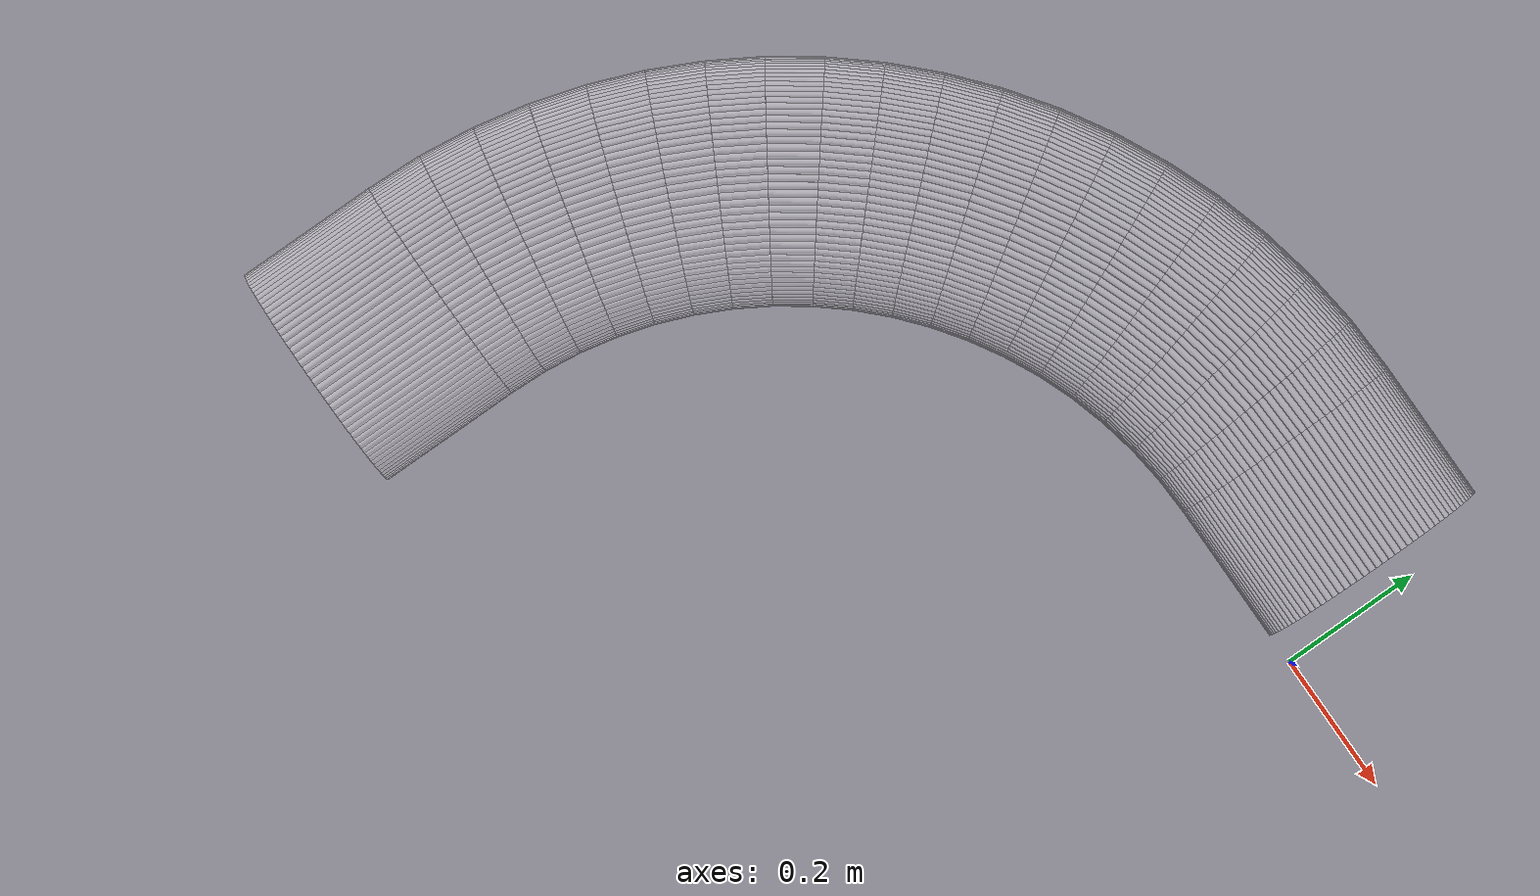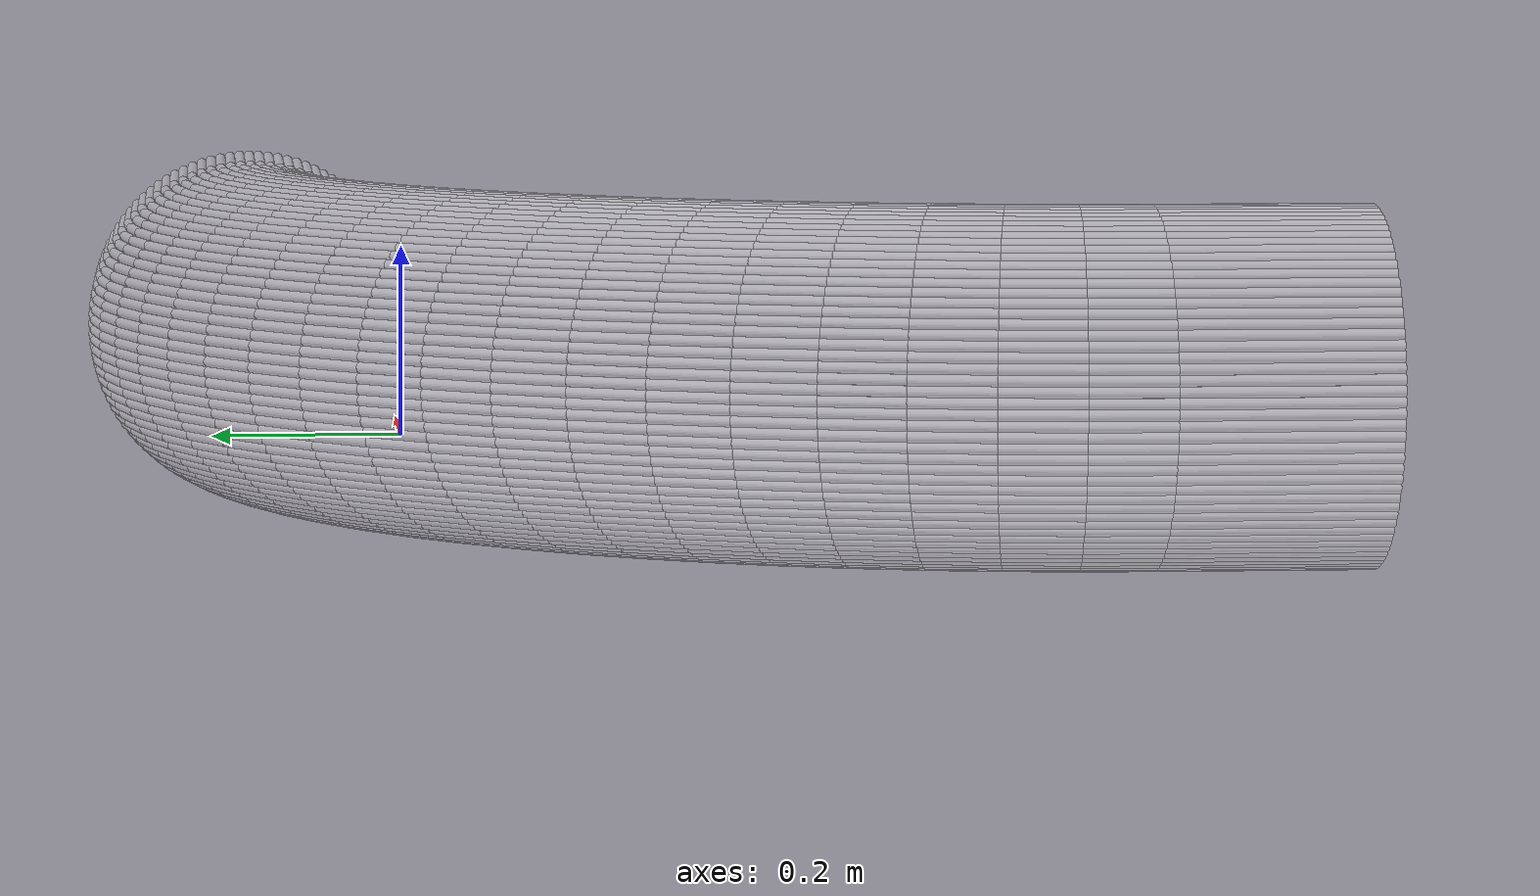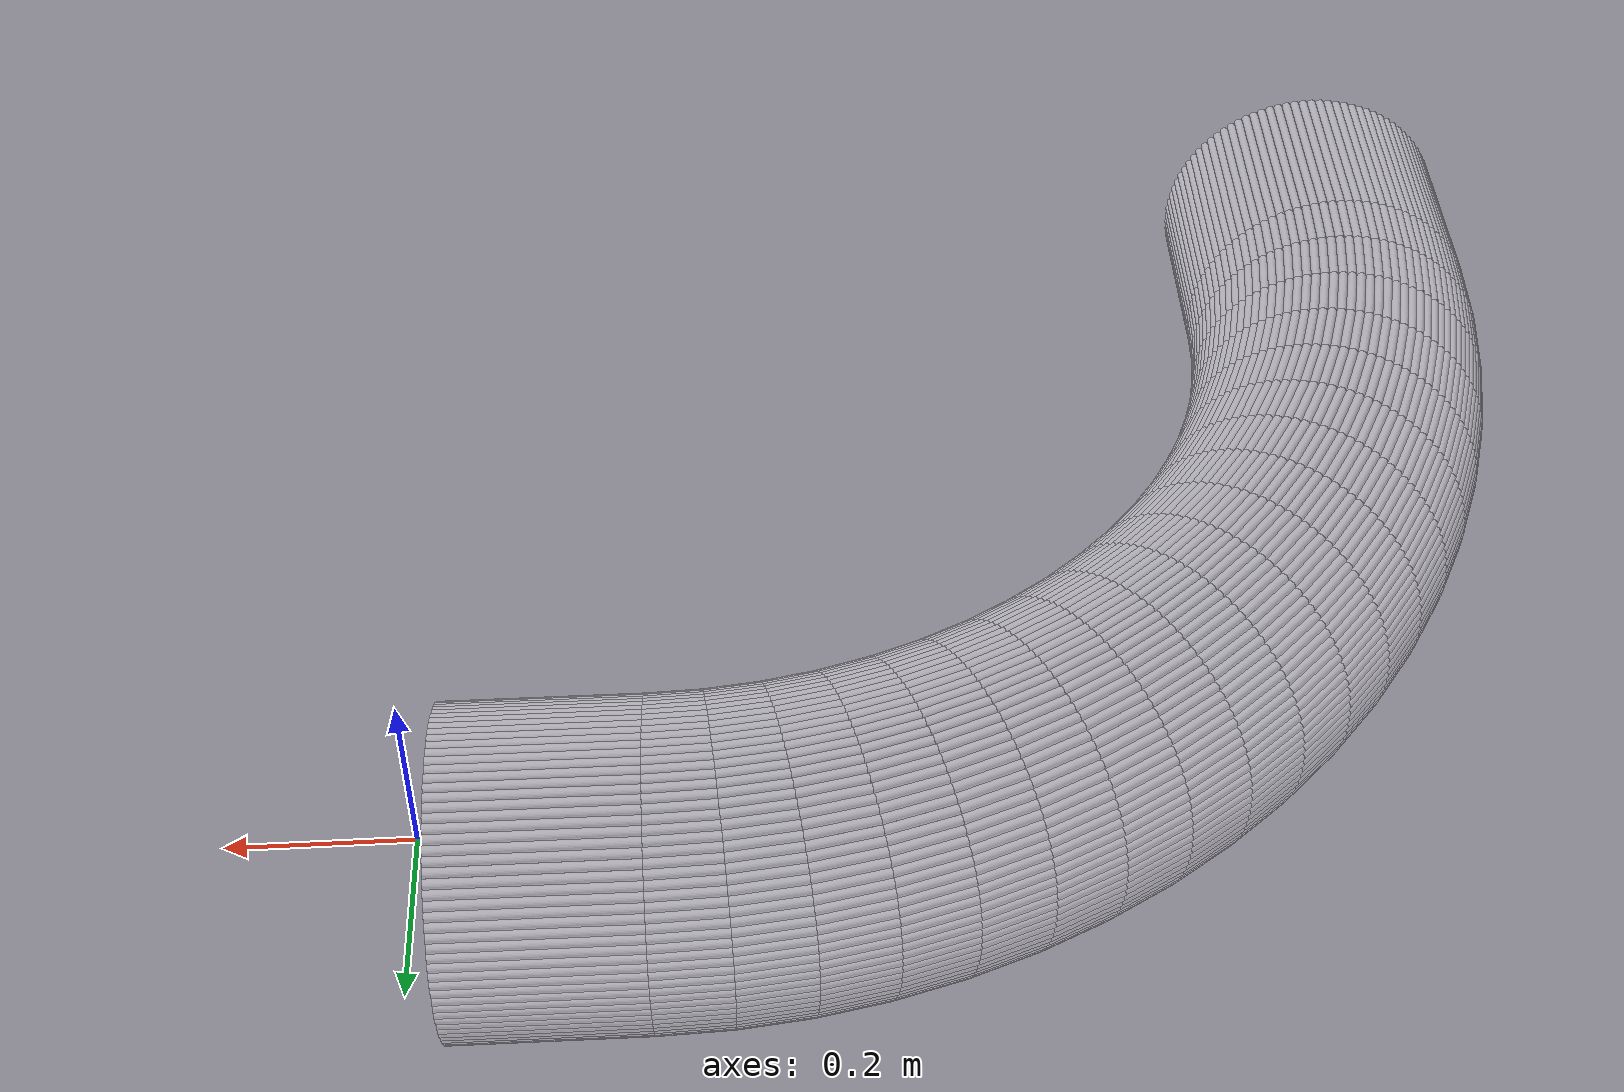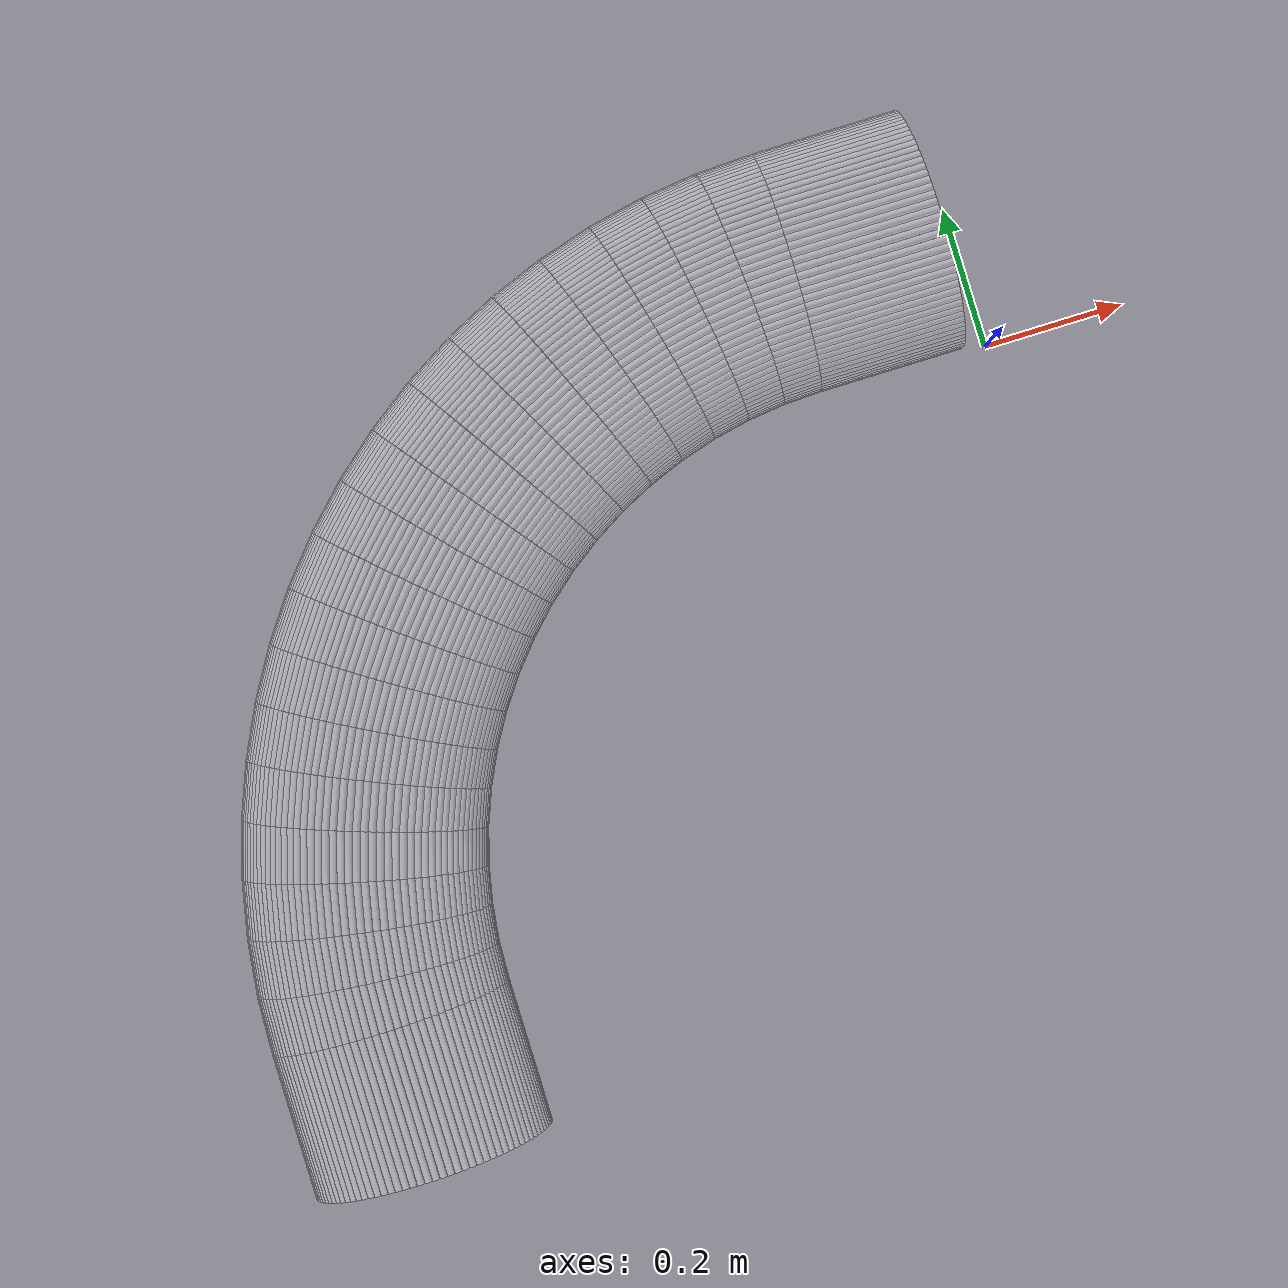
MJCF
<?xml version="1.0" encoding="utf-8"?>
<mujoco>
   <worldbody>
   <body pos="-0.25 -0.64 -0.02" euler="0 0 90">
      <geom euler=" 0 10 0 " fromto="0.96 -0.2 0.16 0.96 0 0.16" rgba="1 1 1 0.35"
            size="0.0050257"
            type="cylinder"/>
      <geom euler=" 0 20 0 " fromto="0.95968 -0.2 0.17005 0.95968 0 0.17005"
            rgba="1 1 1 0.35"
            size="0.0050257"
            type="cylinder"/>
      <geom euler=" 0 30 0 " fromto="0.95874 -0.2 0.18005 0.95874 0 0.18005"
            rgba="1 1 1 0.35"
            size="0.0050257"
            type="cylinder"/>
      <geom euler=" 0 40 0 " fromto="0.95717 -0.2 0.18998 0.95717 0 0.18998"
            rgba="1 1 1 0.35"
            size="0.0050257"
            type="cylinder"/>
      <geom euler=" 0 50 0 " fromto="0.95497 -0.2 0.19979 0.95497 0 0.19979"
            rgba="1 1 1 0.35"
            size="0.0050257"
            type="cylinder"/>
      <geom euler=" 0 60 0 " fromto="0.95217 -0.2 0.20944 0.95217 0 0.20944"
            rgba="1 1 1 0.35"
            size="0.0050257"
            type="cylinder"/>
      <geom euler=" 0 70 0 " fromto="0.94876 -0.2 0.2189 0.94876 0 0.2189"
            rgba="1 1 1 0.35"
            size="0.0050257"
            type="cylinder"/>
      <geom euler=" 0 80 0 " fromto="0.94477 -0.2 0.22812 0.94477 0 0.22812"
            rgba="1 1 1 0.35"
            size="0.0050257"
            type="cylinder"/>
      <geom euler=" 0 90 0 " fromto="0.94021 -0.2 0.23708 0.94021 0 0.23708"
            rgba="1 1 1 0.35"
            size="0.0050257"
            type="cylinder"/>
      <geom euler=" 0 100 0 " fromto="0.93509 -0.2 0.24573 0.93509 0 0.24573"
            rgba="1 1 1 0.35"
            size="0.0050257"
            type="cylinder"/>
      <geom euler=" 0 110 0 " fromto="0.92944 -0.2 0.25405 0.92944 0 0.25405"
            rgba="1 1 1 0.35"
            size="0.0050257"
            type="cylinder"/>
      <geom euler=" 0 120 0 " fromto="0.92328 -0.2 0.26199 0.92328 0 0.26199"
            rgba="1 1 1 0.35"
            size="0.0050257"
            type="cylinder"/>
      <geom euler=" 0 130 0 " fromto="0.91663 -0.2 0.26953 0.91663 0 0.26953"
            rgba="1 1 1 0.35"
            size="0.0050257"
            type="cylinder"/>
      <geom euler=" 0 140 0 " fromto="0.90953 -0.2 0.27663 0.90953 0 0.27663"
            rgba="1 1 1 0.35"
            size="0.0050257"
            type="cylinder"/>
      <geom euler=" 0 150 0 " fromto="0.90199 -0.2 0.28328 0.90199 0 0.28328"
            rgba="1 1 1 0.35"
            size="0.0050257"
            type="cylinder"/>
      <geom euler=" 0 160 0 " fromto="0.89405 -0.2 0.28944 0.89405 0 0.28944"
            rgba="1 1 1 0.35"
            size="0.0050257"
            type="cylinder"/>
      <geom euler=" 0 170 0 " fromto="0.88573 -0.2 0.29509 0.88573 0 0.29509"
            rgba="1 1 1 0.35"
            size="0.0050257"
            type="cylinder"/>
      <geom euler=" 0 180 0 " fromto="0.87708 -0.2 0.30021 0.87708 0 0.30021"
            rgba="1 1 1 0.35"
            size="0.0050257"
            type="cylinder"/>
      <geom euler=" 0 190 0 " fromto="0.86812 -0.2 0.30477 0.86812 0 0.30477"
            rgba="1 1 1 0.35"
            size="0.0050257"
            type="cylinder"/>
      <geom euler=" 0 200 0 " fromto="0.8589 -0.2 0.30876 0.8589 0 0.30876"
            rgba="1 1 1 0.35"
            size="0.0050257"
            type="cylinder"/>
      <geom euler=" 0 210 0 " fromto="0.84944 -0.2 0.31217 0.84944 0 0.31217"
            rgba="1 1 1 0.35"
            size="0.0050257"
            type="cylinder"/>
      <geom euler=" 0 220 0 " fromto="0.83979 -0.2 0.31497 0.83979 0 0.31497"
            rgba="1 1 1 0.35"
            size="0.0050257"
            type="cylinder"/>
      <geom euler=" 0 230 0 " fromto="0.82998 -0.2 0.31717 0.82998 0 0.31717"
            rgba="1 1 1 0.35"
            size="0.0050257"
            type="cylinder"/>
      <geom euler=" 0 240 0 " fromto="0.82005 -0.2 0.31874 0.82005 0 0.31874"
            rgba="1 1 1 0.35"
            size="0.0050257"
            type="cylinder"/>
      <geom euler=" 0 250 0 " fromto="0.81005 -0.2 0.31968 0.81005 0 0.31968"
            rgba="1 1 1 0.35"
            size="0.0050257"
            type="cylinder"/>
      <geom euler=" 0 260 0 " fromto="0.8 -0.2 0.32 0.8 0 0.32" rgba="1 1 1 0.35"
            size="0.0050257"
            type="cylinder"/>
      <geom euler=" 0 270 0 " fromto="0.78995 -0.2 0.31968 0.78995 0 0.31968"
            rgba="1 1 1 0.35"
            size="0.0050257"
            type="cylinder"/>
      <geom euler=" 0 280 0 " fromto="0.77995 -0.2 0.31874 0.77995 0 0.31874"
            rgba="1 1 1 0.35"
            size="0.0050257"
            type="cylinder"/>
      <geom euler=" 0 290 0 " fromto="0.77002 -0.2 0.31717 0.77002 0 0.31717"
            rgba="1 1 1 0.35"
            size="0.0050257"
            type="cylinder"/>
      <geom euler=" 0 300 0 " fromto="0.76021 -0.2 0.31497 0.76021 0 0.31497"
            rgba="1 1 1 0.35"
            size="0.0050257"
            type="cylinder"/>
      <geom euler=" 0 310 0 " fromto="0.75056 -0.2 0.31217 0.75056 0 0.31217"
            rgba="1 1 1 0.35"
            size="0.0050257"
            type="cylinder"/>
      <geom euler=" 0 320 0 " fromto="0.7411 -0.2 0.30876 0.7411 0 0.30876"
            rgba="1 1 1 0.35"
            size="0.0050257"
            type="cylinder"/>
      <geom euler=" 0 330 0 " fromto="0.73188 -0.2 0.30477 0.73188 0 0.30477"
            rgba="1 1 1 0.35"
            size="0.0050257"
            type="cylinder"/>
      <geom euler=" 0 340 0 " fromto="0.72292 -0.2 0.30021 0.72292 0 0.30021"
            rgba="1 1 1 0.35"
            size="0.0050257"
            type="cylinder"/>
      <geom euler=" 0 350 0 " fromto="0.71427 -0.2 0.29509 0.71427 0 0.29509"
            rgba="1 1 1 0.35"
            size="0.0050257"
            type="cylinder"/>
      <geom euler=" 0 360 0 " fromto="0.70595 -0.2 0.28944 0.70595 0 0.28944"
            rgba="1 1 1 0.35"
            size="0.0050257"
            type="cylinder"/>
      <geom euler=" 0 370 0 " fromto="0.69801 -0.2 0.28328 0.69801 0 0.28328"
            rgba="1 1 1 0.35"
            size="0.0050257"
            type="cylinder"/>
      <geom euler=" 0 380 0 " fromto="0.69047 -0.2 0.27663 0.69047 0 0.27663"
            rgba="1 1 1 0.35"
            size="0.0050257"
            type="cylinder"/>
      <geom euler=" 0 390 0 " fromto="0.68337 -0.2 0.26953 0.68337 0 0.26953"
            rgba="1 1 1 0.35"
            size="0.0050257"
            type="cylinder"/>
      <geom euler=" 0 400 0 " fromto="0.67672 -0.2 0.26199 0.67672 0 0.26199"
            rgba="1 1 1 0.35"
            size="0.0050257"
            type="cylinder"/>
      <geom euler=" 0 410 0 " fromto="0.67056 -0.2 0.25405 0.67056 0 0.25405"
            rgba="1 1 1 0.35"
            size="0.0050257"
            type="cylinder"/>
      <geom euler=" 0 420 0 " fromto="0.66491 -0.2 0.24573 0.66491 0 0.24573"
            rgba="1 1 1 0.35"
            size="0.0050257"
            type="cylinder"/>
      <geom euler=" 0 430 0 " fromto="0.65979 -0.2 0.23708 0.65979 0 0.23708"
            rgba="1 1 1 0.35"
            size="0.0050257"
            type="cylinder"/>
      <geom euler=" 0 440 0 " fromto="0.65523 -0.2 0.22812 0.65523 0 0.22812"
            rgba="1 1 1 0.35"
            size="0.0050257"
            type="cylinder"/>
      <geom euler=" 0 450 0 " fromto="0.65124 -0.2 0.2189 0.65124 0 0.2189"
            rgba="1 1 1 0.35"
            size="0.0050257"
            type="cylinder"/>
      <geom euler=" 0 460 0 " fromto="0.64783 -0.2 0.20944 0.64783 0 0.20944"
            rgba="1 1 1 0.35"
            size="0.0050257"
            type="cylinder"/>
      <geom euler=" 0 470 0 " fromto="0.64503 -0.2 0.19979 0.64503 0 0.19979"
            rgba="1 1 1 0.35"
            size="0.0050257"
            type="cylinder"/>
      <geom euler=" 0 480 0 " fromto="0.64283 -0.2 0.18998 0.64283 0 0.18998"
            rgba="1 1 1 0.35"
            size="0.0050257"
            type="cylinder"/>
      <geom euler=" 0 490 0 " fromto="0.64126 -0.2 0.18005 0.64126 0 0.18005"
            rgba="1 1 1 0.35"
            size="0.0050257"
            type="cylinder"/>
      <geom euler=" 0 500 0 " fromto="0.64032 -0.2 0.17005 0.64032 0 0.17005"
            rgba="1 1 1 0.35"
            size="0.0050257"
            type="cylinder"/>
      <geom euler=" 0 510 0 " fromto="0.64 -0.2 0.16 0.64 0 0.16" rgba="1 1 1 0.35"
            size="0.0050257"
            type="cylinder"/>
      <geom euler=" 0 520 0 " fromto="0.64032 -0.2 0.14995 0.64032 0 0.14995"
            rgba="1 1 1 0.35"
            size="0.0050257"
            type="cylinder"/>
      <geom euler=" 0 530 0 " fromto="0.64126 -0.2 0.13995 0.64126 0 0.13995"
            rgba="1 1 1 0.35"
            size="0.0050257"
            type="cylinder"/>
      <geom euler=" 0 540 0 " fromto="0.64283 -0.2 0.13002 0.64283 0 0.13002"
            rgba="1 1 1 0.35"
            size="0.0050257"
            type="cylinder"/>
      <geom euler=" 0 550 0 " fromto="0.64503 -0.2 0.12021 0.64503 0 0.12021"
            rgba="1 1 1 0.35"
            size="0.0050257"
            type="cylinder"/>
      <geom euler=" 0 560 0 " fromto="0.64783 -0.2 0.11056 0.64783 0 0.11056"
            rgba="1 1 1 0.35"
            size="0.0050257"
            type="cylinder"/>
      <geom euler=" 0 570 0 " fromto="0.65124 -0.2 0.1011 0.65124 0 0.1011"
            rgba="1 1 1 0.35"
            size="0.0050257"
            type="cylinder"/>
      <geom euler=" 0 580 0 " fromto="0.65523 -0.2 0.091875 0.65523 0 0.091875"
            rgba="1 1 1 0.35"
            size="0.0050257"
            type="cylinder"/>
      <geom euler=" 0 590 0 " fromto="0.65979 -0.2 0.082919 0.65979 0 0.082919"
            rgba="1 1 1 0.35"
            size="0.0050257"
            type="cylinder"/>
      <geom euler=" 0 600 0 " fromto="0.66491 -0.2 0.074268 0.66491 0 0.074268"
            rgba="1 1 1 0.35"
            size="0.0050257"
            type="cylinder"/>
      <geom euler=" 0 610 0 " fromto="0.67056 -0.2 0.065954 0.67056 0 0.065954"
            rgba="1 1 1 0.35"
            size="0.0050257"
            type="cylinder"/>
      <geom euler=" 0 620 0 " fromto="0.67672 -0.2 0.058012 0.67672 0 0.058012"
            rgba="1 1 1 0.35"
            size="0.0050257"
            type="cylinder"/>
      <geom euler=" 0 630 0 " fromto="0.68337 -0.2 0.050472 0.68337 0 0.050472"
            rgba="1 1 1 0.35"
            size="0.0050257"
            type="cylinder"/>
      <geom euler=" 0 640 0 " fromto="0.69047 -0.2 0.043365 0.69047 0 0.043365"
            rgba="1 1 1 0.35"
            size="0.0050257"
            type="cylinder"/>
      <geom euler=" 0 650 0 " fromto="0.69801 -0.2 0.036718 0.69801 0 0.036718"
            rgba="1 1 1 0.35"
            size="0.0050257"
            type="cylinder"/>
      <geom euler=" 0 660 0 " fromto="0.70595 -0.2 0.030557 0.70595 0 0.030557"
            rgba="1 1 1 0.35"
            size="0.0050257"
            type="cylinder"/>
      <geom euler=" 0 670 0 " fromto="0.71427 -0.2 0.024908 0.71427 0 0.024908"
            rgba="1 1 1 0.35"
            size="0.0050257"
            type="cylinder"/>
      <geom euler=" 0 680 0 " fromto="0.72292 -0.2 0.019791 0.72292 0 0.019791"
            rgba="1 1 1 0.35"
            size="0.0050257"
            type="cylinder"/>
      <geom euler=" 0 690 0 " fromto="0.73188 -0.2 0.015228 0.73188 0 0.015228"
            rgba="1 1 1 0.35"
            size="0.0050257"
            type="cylinder"/>
      <geom euler=" 0 700 0 " fromto="0.7411 -0.2 0.011236 0.7411 0 0.011236"
            rgba="1 1 1 0.35"
            size="0.0050257"
            type="cylinder"/>
      <geom euler=" 0 710 0 " fromto="0.75056 -0.2 0.007831 0.75056 0 0.007831"
            rgba="1 1 1 0.35"
            size="0.0050257"
            type="cylinder"/>
      <geom euler=" 0 720 0 " fromto="0.76021 -0.2 0.0050267 0.76021 0 0.0050267"
            rgba="1 1 1 0.35"
            size="0.0050257"
            type="cylinder"/>
      <geom euler=" 0 730 0 " fromto="0.77002 -0.2 0.002834 0.77002 0 0.002834"
            rgba="1 1 1 0.35"
            size="0.0050257"
            type="cylinder"/>
      <geom euler=" 0 740 0 " fromto="0.77995 -0.2 0.0012616 0.77995 0 0.0012616"
            rgba="1 1 1 0.35"
            size="0.0050257"
            type="cylinder"/>
      <geom euler=" 0 750 0 " fromto="0.78995 -0.2 0.00031572 0.78995 0 0.00031572"
            rgba="1 1 1 0.35"
            size="0.0050257"
            type="cylinder"/>
      <geom euler=" 0 760 0 " fromto="0.8 -0.2 0 0.8 0 0" rgba="1 1 1 0.35"
            size="0.0050257"
            type="cylinder"/>
      <geom euler=" 0 770 0 " fromto="0.81005 -0.2 0.00031572 0.81005 0 0.00031572"
            rgba="1 1 1 0.35"
            size="0.0050257"
            type="cylinder"/>
      <geom euler=" 0 780 0 " fromto="0.82005 -0.2 0.0012616 0.82005 0 0.0012616"
            rgba="1 1 1 0.35"
            size="0.0050257"
            type="cylinder"/>
      <geom euler=" 0 790 0 " fromto="0.82998 -0.2 0.002834 0.82998 0 0.002834"
            rgba="1 1 1 0.35"
            size="0.0050257"
            type="cylinder"/>
      <geom euler=" 0 800 0 " fromto="0.83979 -0.2 0.0050267 0.83979 0 0.0050267"
            rgba="1 1 1 0.35"
            size="0.0050257"
            type="cylinder"/>
      <geom euler=" 0 810 0 " fromto="0.84944 -0.2 0.007831 0.84944 0 0.007831"
            rgba="1 1 1 0.35"
            size="0.0050257"
            type="cylinder"/>
      <geom euler=" 0 820 0 " fromto="0.8589 -0.2 0.011236 0.8589 0 0.011236"
            rgba="1 1 1 0.35"
            size="0.0050257"
            type="cylinder"/>
      <geom euler=" 0 830 0 " fromto="0.86812 -0.2 0.015228 0.86812 0 0.015228"
            rgba="1 1 1 0.35"
            size="0.0050257"
            type="cylinder"/>
      <geom euler=" 0 840 0 " fromto="0.87708 -0.2 0.019791 0.87708 0 0.019791"
            rgba="1 1 1 0.35"
            size="0.0050257"
            type="cylinder"/>
      <geom euler=" 0 850 0 " fromto="0.88573 -0.2 0.024908 0.88573 0 0.024908"
            rgba="1 1 1 0.35"
            size="0.0050257"
            type="cylinder"/>
      <geom euler=" 0 860 0 " fromto="0.89405 -0.2 0.030557 0.89405 0 0.030557"
            rgba="1 1 1 0.35"
            size="0.0050257"
            type="cylinder"/>
      <geom euler=" 0 870 0 " fromto="0.90199 -0.2 0.036718 0.90199 0 0.036718"
            rgba="1 1 1 0.35"
            size="0.0050257"
            type="cylinder"/>
      <geom euler=" 0 880 0 " fromto="0.90953 -0.2 0.043365 0.90953 0 0.043365"
            rgba="1 1 1 0.35"
            size="0.0050257"
            type="cylinder"/>
      <geom euler=" 0 890 0 " fromto="0.91663 -0.2 0.050472 0.91663 0 0.050472"
            rgba="1 1 1 0.35"
            size="0.0050257"
            type="cylinder"/>
      <geom euler=" 0 900 0 " fromto="0.92328 -0.2 0.058012 0.92328 0 0.058012"
            rgba="1 1 1 0.35"
            size="0.0050257"
            type="cylinder"/>
      <geom euler=" 0 910 0 " fromto="0.92944 -0.2 0.065954 0.92944 0 0.065954"
            rgba="1 1 1 0.35"
            size="0.0050257"
            type="cylinder"/>
      <geom euler=" 0 920 0 " fromto="0.93509 -0.2 0.074268 0.93509 0 0.074268"
            rgba="1 1 1 0.35"
            size="0.0050257"
            type="cylinder"/>
      <geom euler=" 0 930 0 " fromto="0.94021 -0.2 0.082919 0.94021 0 0.082919"
            rgba="1 1 1 0.35"
            size="0.0050257"
            type="cylinder"/>
      <geom euler=" 0 940 0 " fromto="0.94477 -0.2 0.091875 0.94477 0 0.091875"
            rgba="1 1 1 0.35"
            size="0.0050257"
            type="cylinder"/>
      <geom euler=" 0 950 0 " fromto="0.94876 -0.2 0.1011 0.94876 0 0.1011"
            rgba="1 1 1 0.35"
            size="0.0050257"
            type="cylinder"/>
      <geom euler=" 0 960 0 " fromto="0.95217 -0.2 0.11056 0.95217 0 0.11056"
            rgba="1 1 1 0.35"
            size="0.0050257"
            type="cylinder"/>
      <geom euler=" 0 970 0 " fromto="0.95497 -0.2 0.12021 0.95497 0 0.12021"
            rgba="1 1 1 0.35"
            size="0.0050257"
            type="cylinder"/>
      <geom euler=" 0 980 0 " fromto="0.95717 -0.2 0.13002 0.95717 0 0.13002"
            rgba="1 1 1 0.35"
            size="0.0050257"
            type="cylinder"/>
      <geom euler=" 0 990 0 " fromto="0.95874 -0.2 0.13995 0.95874 0 0.13995"
            rgba="1 1 1 0.35"
            size="0.0050257"
            type="cylinder"/>
      <geom euler=" 0 1000 0 " fromto="0.95968 -0.2 0.14995 0.95968 0 0.14995"
            rgba="1 1 1 0.35"
            size="0.0050257"
            type="cylinder"/>
      <geom euler=" 0 10 0 " fromto="0.96 0 0.16 0.95672 0.079276 0.16" rgba="1 1 1 0.35"
            size="0.0050257"
            type="cylinder"/>
      <geom euler=" 0 20 0 " fromto="0.95968 0 0.17005 0.95641 0.07925 0.17005"
            rgba="1 1 1 0.35"
            size="0.0050257"
            type="cylinder"/>
      <geom euler=" 0 30 0 " fromto="0.95874 0 0.18005 0.95546 0.079172 0.18005"
            rgba="1 1 1 0.35"
            size="0.0050257"
            type="cylinder"/>
      <geom euler=" 0 40 0 " fromto="0.95717 0 0.18998 0.9539 0.079042 0.18998"
            rgba="1 1 1 0.35"
            size="0.0050257"
            type="cylinder"/>
      <geom euler=" 0 50 0 " fromto="0.95497 0 0.19979 0.95171 0.078861 0.19979"
            rgba="1 1 1 0.35"
            size="0.0050257"
            type="cylinder"/>
      <geom euler=" 0 60 0 " fromto="0.95217 0 0.20944 0.94892 0.078629 0.20944"
            rgba="1 1 1 0.35"
            size="0.0050257"
            type="cylinder"/>
      <geom euler=" 0 70 0 " fromto="0.94876 0 0.2189 0.94552 0.078348 0.2189"
            rgba="1 1 1 0.35"
            size="0.0050257"
            type="cylinder"/>
      <geom euler=" 0 80 0 " fromto="0.94477 0 0.22812 0.94155 0.078019 0.22812"
            rgba="1 1 1 0.35"
            size="0.0050257"
            type="cylinder"/>
      <geom euler=" 0 90 0 " fromto="0.94021 0 0.23708 0.937 0.077642 0.23708"
            rgba="1 1 1 0.35"
            size="0.0050257"
            type="cylinder"/>
      <geom euler=" 0 100 0 " fromto="0.93509 0 0.24573 0.9319 0.077219 0.24573"
            rgba="1 1 1 0.35"
            size="0.0050257"
            type="cylinder"/>
      <geom euler=" 0 110 0 " fromto="0.92944 0 0.25405 0.92627 0.076753 0.25405"
            rgba="1 1 1 0.35"
            size="0.0050257"
            type="cylinder"/>
      <geom euler=" 0 120 0 " fromto="0.92328 0 0.26199 0.92013 0.076244 0.26199"
            rgba="1 1 1 0.35"
            size="0.0050257"
            type="cylinder"/>
      <geom euler=" 0 130 0 " fromto="0.91663 0 0.26953 0.9135 0.075695 0.26953"
            rgba="1 1 1 0.35"
            size="0.0050257"
            type="cylinder"/>
      <geom euler=" 0 140 0 " fromto="0.90953 0 0.27663 0.90642 0.075108 0.27663"
            rgba="1 1 1 0.35"
            size="0.0050257"
            type="cylinder"/>
      <geom euler=" 0 150 0 " fromto="0.90199 0 0.28328 0.89891 0.074486 0.28328"
            rgba="1 1 1 0.35"
            size="0.0050257"
            type="cylinder"/>
      <geom euler=" 0 160 0 " fromto="0.89405 0 0.28944 0.89099 0.07383 0.28944"
            rgba="1 1 1 0.35"
            size="0.0050257"
            type="cylinder"/>
      <geom euler=" 0 170 0 " fromto="0.88573 0 0.29509 0.88271 0.073143 0.29509"
            rgba="1 1 1 0.35"
            size="0.0050257"
            type="cylinder"/>
      <geom euler=" 0 180 0 " fromto="0.87708 0 0.30021 0.87408 0.072429 0.30021"
            rgba="1 1 1 0.35"
            size="0.0050257"
            type="cylinder"/>
      <geom euler=" 0 190 0 " fromto="0.86812 0 0.30477 0.86516 0.071689 0.30477"
            rgba="1 1 1 0.35"
            size="0.0050257"
            type="cylinder"/>
      <geom euler=" 0 200 0 " fromto="0.8589 0 0.30876 0.85597 0.070927 0.30876"
            rgba="1 1 1 0.35"
            size="0.0050257"
            type="cylinder"/>
      <geom euler=" 0 210 0 " fromto="0.84944 0 0.31217 0.84654 0.070146 0.31217"
            rgba="1 1 1 0.35"
            size="0.0050257"
            type="cylinder"/>
      <geom euler=" 0 220 0 " fromto="0.83979 0 0.31497 0.83692 0.069349 0.31497"
            rgba="1 1 1 0.35"
            size="0.0050257"
            type="cylinder"/>
      <geom euler=" 0 230 0 " fromto="0.82998 0 0.31717 0.82715 0.068539 0.31717"
            rgba="1 1 1 0.35"
            size="0.0050257"
            type="cylinder"/>
      <geom euler=" 0 240 0 " fromto="0.82005 0 0.31874 0.81725 0.067719 0.31874"
            rgba="1 1 1 0.35"
            size="0.0050257"
            type="cylinder"/>
      <geom euler=" 0 250 0 " fromto="0.81005 0 0.31968 0.80728 0.066893 0.31968"
            rgba="1 1 1 0.35"
            size="0.0050257"
            type="cylinder"/>
      <geom euler=" 0 260 0 " fromto="0.8 0 0.32 0.79727 0.066063 0.32" rgba="1 1 1 0.35"
            size="0.0050257"
            type="cylinder"/>
      <geom euler=" 0 270 0 " fromto="0.78995 0 0.31968 0.78726 0.065234 0.31968"
            rgba="1 1 1 0.35"
            size="0.0050257"
            type="cylinder"/>
      <geom euler=" 0 280 0 " fromto="0.77995 0 0.31874 0.77728 0.064407 0.31874"
            rgba="1 1 1 0.35"
            size="0.0050257"
            type="cylinder"/>
      <geom euler=" 0 290 0 " fromto="0.77002 0 0.31717 0.76739 0.063588 0.31717"
            rgba="1 1 1 0.35"
            size="0.0050257"
            type="cylinder"/>
      <geom euler=" 0 300 0 " fromto="0.76021 0 0.31497 0.75761 0.062778 0.31497"
            rgba="1 1 1 0.35"
            size="0.0050257"
            type="cylinder"/>
      <geom euler=" 0 310 0 " fromto="0.75056 0 0.31217 0.74799 0.061981 0.31217"
            rgba="1 1 1 0.35"
            size="0.0050257"
            type="cylinder"/>
      <geom euler=" 0 320 0 " fromto="0.7411 0 0.30876 0.73857 0.0612 0.30876"
            rgba="1 1 1 0.35"
            size="0.0050257"
            type="cylinder"/>
      <geom euler=" 0 330 0 " fromto="0.73188 0 0.30477 0.72938 0.060438 0.30477"
            rgba="1 1 1 0.35"
            size="0.0050257"
            type="cylinder"/>
      <geom euler=" 0 340 0 " fromto="0.72292 0 0.30021 0.72045 0.059698 0.30021"
            rgba="1 1 1 0.35"
            size="0.0050257"
            type="cylinder"/>
      <geom euler=" 0 350 0 " fromto="0.71427 0 0.29509 0.71183 0.058984 0.29509"
            rgba="1 1 1 0.35"
            size="0.0050257"
            type="cylinder"/>
      <geom euler=" 0 360 0 " fromto="0.70595 0 0.28944 0.70354 0.058297 0.28944"
            rgba="1 1 1 0.35"
            size="0.0050257"
            type="cylinder"/>
      <geom euler=" 0 370 0 " fromto="0.69801 0 0.28328 0.69563 0.057641 0.28328"
            rgba="1 1 1 0.35"
            size="0.0050257"
            type="cylinder"/>
      <geom euler=" 0 380 0 " fromto="0.69047 0 0.27663 0.68811 0.057019 0.27663"
            rgba="1 1 1 0.35"
            size="0.0050257"
            type="cylinder"/>
      <geom euler=" 0 390 0 " fromto="0.68337 0 0.26953 0.68103 0.056432 0.26953"
            rgba="1 1 1 0.35"
            size="0.0050257"
            type="cylinder"/>
      <geom euler=" 0 400 0 " fromto="0.67672 0 0.26199 0.67441 0.055883 0.26199"
            rgba="1 1 1 0.35"
            size="0.0050257"
            type="cylinder"/>
      <geom euler=" 0 410 0 " fromto="0.67056 0 0.25405 0.66827 0.055374 0.25405"
            rgba="1 1 1 0.35"
            size="0.0050257"
            type="cylinder"/>
      <geom euler=" 0 420 0 " fromto="0.66491 0 0.24573 0.66264 0.054908 0.24573"
            rgba="1 1 1 0.35"
            size="0.0050257"
            type="cylinder"/>
      <geom euler=" 0 430 0 " fromto="0.65979 0 0.23708 0.65754 0.054485 0.23708"
            rgba="1 1 1 0.35"
            size="0.0050257"
            type="cylinder"/>
      <geom euler=" 0 440 0 " fromto="0.65523 0 0.22812 0.65299 0.054108 0.22812"
            rgba="1 1 1 0.35"
            size="0.0050257"
            type="cylinder"/>
      <geom euler=" 0 450 0 " fromto="0.65124 0 0.2189 0.64901 0.053779 0.2189"
            rgba="1 1 1 0.35"
            size="0.0050257"
            type="cylinder"/>
      <geom euler=" 0 460 0 " fromto="0.64783 0 0.20944 0.64562 0.053497 0.20944"
            rgba="1 1 1 0.35"
            size="0.0050257"
            type="cylinder"/>
      <geom euler=" 0 470 0 " fromto="0.64503 0 0.19979 0.64282 0.053266 0.19979"
            rgba="1 1 1 0.35"
            size="0.0050257"
            type="cylinder"/>
      <geom euler=" 0 480 0 " fromto="0.64283 0 0.18998 0.64064 0.053085 0.18998"
            rgba="1 1 1 0.35"
            size="0.0050257"
            type="cylinder"/>
      <geom euler=" 0 490 0 " fromto="0.64126 0 0.18005 0.63907 0.052955 0.18005"
            rgba="1 1 1 0.35"
            size="0.0050257"
            type="cylinder"/>
      <geom euler=" 0 500 0 " fromto="0.64032 0 0.17005 0.63813 0.052877 0.17005"
            rgba="1 1 1 0.35"
            size="0.0050257"
            type="cylinder"/>
      <geom euler=" 0 510 0 " fromto="0.64 0 0.16 0.63781 0.052851 0.16" rgba="1 1 1 0.35"
            size="0.0050257"
            type="cylinder"/>
      <geom euler=" 0 520 0 " fromto="0.64032 0 0.14995 0.63813 0.052877 0.14995"
            rgba="1 1 1 0.35"
            size="0.0050257"
            type="cylinder"/>
      <geom euler=" 0 530 0 " fromto="0.64126 0 0.13995 0.63907 0.052955 0.13995"
            rgba="1 1 1 0.35"
            size="0.0050257"
            type="cylinder"/>
      <geom euler=" 0 540 0 " fromto="0.64283 0 0.13002 0.64064 0.053085 0.13002"
            rgba="1 1 1 0.35"
            size="0.0050257"
            type="cylinder"/>
      <geom euler=" 0 550 0 " fromto="0.64503 0 0.12021 0.64282 0.053266 0.12021"
            rgba="1 1 1 0.35"
            size="0.0050257"
            type="cylinder"/>
      <geom euler=" 0 560 0 " fromto="0.64783 0 0.11056 0.64562 0.053497 0.11056"
            rgba="1 1 1 0.35"
            size="0.0050257"
            type="cylinder"/>
      <geom euler=" 0 570 0 " fromto="0.65124 0 0.1011 0.64901 0.053779 0.1011"
            rgba="1 1 1 0.35"
            size="0.0050257"
            type="cylinder"/>
      <geom euler=" 0 580 0 " fromto="0.65523 0 0.091875 0.65299 0.054108 0.091875"
            rgba="1 1 1 0.35"
            size="0.0050257"
            type="cylinder"/>
      <geom euler=" 0 590 0 " fromto="0.65979 0 0.082919 0.65754 0.054485 0.082919"
            rgba="1 1 1 0.35"
            size="0.0050257"
            type="cylinder"/>
      <geom euler=" 0 600 0 " fromto="0.66491 0 0.074268 0.66264 0.054908 0.074268"
            rgba="1 1 1 0.35"
            size="0.0050257"
            type="cylinder"/>
      <geom euler=" 0 610 0 " fromto="0.67056 0 0.065954 0.66827 0.055374 0.065954"
            rgba="1 1 1 0.35"
            size="0.0050257"
            type="cylinder"/>
      <geom euler=" 0 620 0 " fromto="0.67672 0 0.058012 0.67441 0.055883 0.058012"
            rgba="1 1 1 0.35"
            size="0.0050257"
            type="cylinder"/>
      <geom euler=" 0 630 0 " fromto="0.68337 0 0.050472 0.68103 0.056432 0.050472"
            rgba="1 1 1 0.35"
            size="0.0050257"
            type="cylinder"/>
      <geom euler=" 0 640 0 " fromto="0.69047 0 0.043365 0.68811 0.057019 0.043365"
            rgba="1 1 1 0.35"
            size="0.0050257"
            type="cylinder"/>
      <geom euler=" 0 650 0 " fromto="0.69801 0 0.036718 0.69563 0.057641 0.036718"
            rgba="1 1 1 0.35"
            size="0.0050257"
            type="cylinder"/>
      <geom euler=" 0 660 0 " fromto="0.70595 0 0.030557 0.70354 0.058297 0.030557"
            rgba="1 1 1 0.35"
            size="0.0050257"
            type="cylinder"/>
      <geom euler=" 0 670 0 " fromto="0.71427 0 0.024908 0.71183 0.058984 0.024908"
            rgba="1 1 1 0.35"
            size="0.0050257"
            type="cylinder"/>
      <geom euler=" 0 680 0 " fromto="0.72292 0 0.019791 0.72045 0.059698 0.019791"
            rgba="1 1 1 0.35"
            size="0.0050257"
            type="cylinder"/>
      <geom euler=" 0 690 0 " fromto="0.73188 0 0.015228 0.72938 0.060438 0.015228"
            rgba="1 1 1 0.35"
            size="0.0050257"
            type="cylinder"/>
      <geom euler=" 0 700 0 " fromto="0.7411 0 0.011236 0.73857 0.0612 0.011236"
            rgba="1 1 1 0.35"
            size="0.0050257"
            type="cylinder"/>
      <geom euler=" 0 710 0 " fromto="0.75056 0 0.007831 0.74799 0.061981 0.007831"
            rgba="1 1 1 0.35"
            size="0.0050257"
            type="cylinder"/>
      <geom euler=" 0 720 0 " fromto="0.76021 0 0.0050267 0.75761 0.062778 0.0050267"
            rgba="1 1 1 0.35"
            size="0.0050257"
            type="cylinder"/>
      <geom euler=" 0 730 0 " fromto="0.77002 0 0.002834 0.76739 0.063588 0.002834"
            rgba="1 1 1 0.35"
            size="0.0050257"
            type="cylinder"/>
      <geom euler=" 0 740 0 " fromto="0.77995 0 0.0012616 0.77728 0.064407 0.0012616"
            rgba="1 1 1 0.35"
            size="0.0050257"
            type="cylinder"/>
      <geom euler=" 0 750 0 " fromto="0.78995 0 0.00031572 0.78726 0.065234 0.00031572"
            rgba="1 1 1 0.35"
            size="0.0050257"
            type="cylinder"/>
      <geom euler=" 0 760 0 " fromto="0.8 0 0 0.79727 0.066063 0" rgba="1 1 1 0.35"
            size="0.0050257"
            type="cylinder"/>
      <geom euler=" 0 770 0 " fromto="0.81005 0 0.00031572 0.80728 0.066893 0.00031572"
            rgba="1 1 1 0.35"
            size="0.0050257"
            type="cylinder"/>
      <geom euler=" 0 780 0 " fromto="0.82005 0 0.0012616 0.81725 0.067719 0.0012616"
            rgba="1 1 1 0.35"
            size="0.0050257"
            type="cylinder"/>
      <geom euler=" 0 790 0 " fromto="0.82998 0 0.002834 0.82715 0.068539 0.002834"
            rgba="1 1 1 0.35"
            size="0.0050257"
            type="cylinder"/>
      <geom euler=" 0 800 0 " fromto="0.83979 0 0.0050267 0.83692 0.069349 0.0050267"
            rgba="1 1 1 0.35"
            size="0.0050257"
            type="cylinder"/>
      <geom euler=" 0 810 0 " fromto="0.84944 0 0.007831 0.84654 0.070146 0.007831"
            rgba="1 1 1 0.35"
            size="0.0050257"
            type="cylinder"/>
      <geom euler=" 0 820 0 " fromto="0.8589 0 0.011236 0.85597 0.070927 0.011236"
            rgba="1 1 1 0.35"
            size="0.0050257"
            type="cylinder"/>
      <geom euler=" 0 830 0 " fromto="0.86812 0 0.015228 0.86516 0.071689 0.015228"
            rgba="1 1 1 0.35"
            size="0.0050257"
            type="cylinder"/>
      <geom euler=" 0 840 0 " fromto="0.87708 0 0.019791 0.87408 0.072429 0.019791"
            rgba="1 1 1 0.35"
            size="0.0050257"
            type="cylinder"/>
      <geom euler=" 0 850 0 " fromto="0.88573 0 0.024908 0.88271 0.073143 0.024908"
            rgba="1 1 1 0.35"
            size="0.0050257"
            type="cylinder"/>
      <geom euler=" 0 860 0 " fromto="0.89405 0 0.030557 0.89099 0.07383 0.030557"
            rgba="1 1 1 0.35"
            size="0.0050257"
            type="cylinder"/>
      <geom euler=" 0 870 0 " fromto="0.90199 0 0.036718 0.89891 0.074486 0.036718"
            rgba="1 1 1 0.35"
            size="0.0050257"
            type="cylinder"/>
      <geom euler=" 0 880 0 " fromto="0.90953 0 0.043365 0.90642 0.075108 0.043365"
            rgba="1 1 1 0.35"
            size="0.0050257"
            type="cylinder"/>
      <geom euler=" 0 890 0 " fromto="0.91663 0 0.050472 0.9135 0.075695 0.050472"
            rgba="1 1 1 0.35"
            size="0.0050257"
            type="cylinder"/>
      <geom euler=" 0 900 0 " fromto="0.92328 0 0.058012 0.92013 0.076244 0.058012"
            rgba="1 1 1 0.35"
            size="0.0050257"
            type="cylinder"/>
      <geom euler=" 0 910 0 " fromto="0.92944 0 0.065954 0.92627 0.076753 0.065954"
            rgba="1 1 1 0.35"
            size="0.0050257"
            type="cylinder"/>
      <geom euler=" 0 920 0 " fromto="0.93509 0 0.074268 0.9319 0.077219 0.074268"
            rgba="1 1 1 0.35"
            size="0.0050257"
            type="cylinder"/>
      <geom euler=" 0 930 0 " fromto="0.94021 0 0.082919 0.937 0.077642 0.082919"
            rgba="1 1 1 0.35"
            size="0.0050257"
            type="cylinder"/>
      <geom euler=" 0 940 0 " fromto="0.94477 0 0.091875 0.94155 0.078019 0.091875"
            rgba="1 1 1 0.35"
            size="0.0050257"
            type="cylinder"/>
      <geom euler=" 0 950 0 " fromto="0.94876 0 0.1011 0.94552 0.078348 0.1011"
            rgba="1 1 1 0.35"
            size="0.0050257"
            type="cylinder"/>
      <geom euler=" 0 960 0 " fromto="0.95217 0 0.11056 0.94892 0.078629 0.11056"
            rgba="1 1 1 0.35"
            size="0.0050257"
            type="cylinder"/>
      <geom euler=" 0 970 0 " fromto="0.95497 0 0.12021 0.95171 0.078861 0.12021"
            rgba="1 1 1 0.35"
            size="0.0050257"
            type="cylinder"/>
      <geom euler=" 0 980 0 " fromto="0.95717 0 0.13002 0.9539 0.079042 0.13002"
            rgba="1 1 1 0.35"
            size="0.0050257"
            type="cylinder"/>
      <geom euler=" 0 990 0 " fromto="0.95874 0 0.13995 0.95546 0.079172 0.13995"
            rgba="1 1 1 0.35"
            size="0.0050257"
            type="cylinder"/>
      <geom euler=" 0 1000 0 " fromto="0.95968 0 0.14995 0.95641 0.07925 0.14995"
            rgba="1 1 1 0.35"
            size="0.0050257"
            type="cylinder"/>
      <geom euler=" 0 10 0 " fromto="0.95672 0.079276 0.16 0.94691 0.15801 0.16"
            rgba="1 1 1 0.35"
            size="0.0050257"
            type="cylinder"/>
      <geom euler=" 0 20 0 " fromto="0.95641 0.07925 0.17005 0.9466 0.15796 0.17005"
            rgba="1 1 1 0.35"
            size="0.0050257"
            type="cylinder"/>
      <geom euler=" 0 30 0 " fromto="0.95546 0.079172 0.18005 0.94566 0.1578 0.18005"
            rgba="1 1 1 0.35"
            size="0.0050257"
            type="cylinder"/>
      <geom euler=" 0 40 0 " fromto="0.9539 0.079042 0.18998 0.94411 0.15754 0.18998"
            rgba="1 1 1 0.35"
            size="0.0050257"
            type="cylinder"/>
      <geom euler=" 0 50 0 " fromto="0.95171 0.078861 0.19979 0.94195 0.15718 0.19979"
            rgba="1 1 1 0.35"
            size="0.0050257"
            type="cylinder"/>
      <geom euler=" 0 60 0 " fromto="0.94892 0.078629 0.20944 0.93918 0.15672 0.20944"
            rgba="1 1 1 0.35"
            size="0.0050257"
            type="cylinder"/>
      <geom euler=" 0 70 0 " fromto="0.94552 0.078348 0.2189 0.93582 0.15616 0.2189"
            rgba="1 1 1 0.35"
            size="0.0050257"
            type="cylinder"/>
      <geom euler=" 0 80 0 " fromto="0.94155 0.078019 0.22812 0.93189 0.1555 0.22812"
            rgba="1 1 1 0.35"
            size="0.0050257"
            type="cylinder"/>
      <geom euler=" 0 90 0 " fromto="0.937 0.077642 0.23708 0.92739 0.15475 0.23708"
            rgba="1 1 1 0.35"
            size="0.0050257"
            type="cylinder"/>
      <geom euler=" 0 100 0 " fromto="0.9319 0.077219 0.24573 0.92234 0.15391 0.24573"
            rgba="1 1 1 0.35"
            size="0.0050257"
            type="cylinder"/>
      <geom euler=" 0 110 0 " fromto="0.92627 0.076753 0.25405 0.91677 0.15298 0.25405"
            rgba="1 1 1 0.35"
            size="0.0050257"
            type="cylinder"/>
      <geom euler=" 0 120 0 " fromto="0.92013 0.076244 0.26199 0.91069 0.15197 0.26199"
            rgba="1 1 1 0.35"
            size="0.0050257"
            type="cylinder"/>
      <geom euler=" 0 130 0 " fromto="0.9135 0.075695 0.26953 0.90413 0.15087 0.26953"
            rgba="1 1 1 0.35"
            size="0.0050257"
            type="cylinder"/>
      <geom euler=" 0 140 0 " fromto="0.90642 0.075108 0.27663 0.89712 0.1497 0.27663"
            rgba="1 1 1 0.35"
            size="0.0050257"
            type="cylinder"/>
      <geom euler=" 0 150 0 " fromto="0.89891 0.074486 0.28328 0.88969 0.14846 0.28328"
            rgba="1 1 1 0.35"
            size="0.0050257"
            type="cylinder"/>
      <geom euler=" 0 160 0 " fromto="0.89099 0.07383 0.28944 0.88185 0.14716 0.28944"
            rgba="1 1 1 0.35"
            size="0.0050257"
            type="cylinder"/>
      <geom euler=" 0 170 0 " fromto="0.88271 0.073143 0.29509 0.87365 0.14579 0.29509"
            rgba="1 1 1 0.35"
            size="0.0050257"
            type="cylinder"/>
      <geom euler=" 0 180 0 " fromto="0.87408 0.072429 0.30021 0.86512 0.14436 0.30021"
            rgba="1 1 1 0.35"
            size="0.0050257"
            type="cylinder"/>
      <geom euler=" 0 190 0 " fromto="0.86516 0.071689 0.30477 0.85628 0.14289 0.30477"
            rgba="1 1 1 0.35"
            size="0.0050257"
            type="cylinder"/>
      <geom euler=" 0 200 0 " fromto="0.85597 0.070927 0.30876 0.84719 0.14137 0.30876"
            rgba="1 1 1 0.35"
            size="0.0050257"
            type="cylinder"/>
      <geom euler=" 0 210 0 " fromto="0.84654 0.070146 0.31217 0.83786 0.13981 0.31217"
            rgba="1 1 1 0.35"
            size="0.0050257"
            type="cylinder"/>
      <geom euler=" 0 220 0 " fromto="0.83692 0.069349 0.31497 0.82834 0.13822 0.31497"
            rgba="1 1 1 0.35"
            size="0.0050257"
            type="cylinder"/>
      <geom euler=" 0 230 0 " fromto="0.82715 0.068539 0.31717 0.81866 0.13661 0.31717"
            rgba="1 1 1 0.35"
            size="0.0050257"
            type="cylinder"/>
      <geom euler=" 0 240 0 " fromto="0.81725 0.067719 0.31874 0.80887 0.13498 0.31874"
            rgba="1 1 1 0.35"
            size="0.0050257"
            type="cylinder"/>
      <geom euler=" 0 250 0 " fromto="0.80728 0.066893 0.31968 0.799 0.13333 0.31968"
            rgba="1 1 1 0.35"
            size="0.0050257"
            type="cylinder"/>
      <geom euler=" 0 260 0 " fromto="0.79727 0.066063 0.32 0.78909 0.13168 0.32"
            rgba="1 1 1 0.35"
            size="0.0050257"
            type="cylinder"/>
      <geom euler=" 0 270 0 " fromto="0.78726 0.065234 0.31968 0.77918 0.13002 0.31968"
            rgba="1 1 1 0.35"
            size="0.0050257"
            type="cylinder"/>
      <geom euler=" 0 280 0 " fromto="0.77728 0.064407 0.31874 0.76931 0.12838 0.31874"
            rgba="1 1 1 0.35"
            size="0.0050257"
            type="cylinder"/>
      <geom euler=" 0 290 0 " fromto="0.76739 0.063588 0.31717 0.75952 0.12674 0.31717"
            rgba="1 1 1 0.35"
            size="0.0050257"
            type="cylinder"/>
      <geom euler=" 0 300 0 " fromto="0.75761 0.062778 0.31497 0.74984 0.12513 0.31497"
            rgba="1 1 1 0.35"
            size="0.0050257"
            type="cylinder"/>
      <geom euler=" 0 310 0 " fromto="0.74799 0.061981 0.31217 0.74032 0.12354 0.31217"
            rgba="1 1 1 0.35"
            size="0.0050257"
            type="cylinder"/>
      <geom euler=" 0 320 0 " fromto="0.73857 0.0612 0.30876 0.73099 0.12198 0.30876"
            rgba="1 1 1 0.35"
            size="0.0050257"
            type="cylinder"/>
      <geom euler=" 0 330 0 " fromto="0.72938 0.060438 0.30477 0.72189 0.12046 0.30477"
            rgba="1 1 1 0.35"
            size="0.0050257"
            type="cylinder"/>
      <geom euler=" 0 340 0 " fromto="0.72045 0.059698 0.30021 0.71306 0.11899 0.30021"
            rgba="1 1 1 0.35"
            size="0.0050257"
            type="cylinder"/>
      <geom euler=" 0 350 0 " fromto="0.71183 0.058984 0.29509 0.70453 0.11756 0.29509"
            rgba="1 1 1 0.35"
            size="0.0050257"
            type="cylinder"/>
      <geom euler=" 0 360 0 " fromto="0.70354 0.058297 0.28944 0.69633 0.1162 0.28944"
            rgba="1 1 1 0.35"
            size="0.0050257"
            type="cylinder"/>
      <geom euler=" 0 370 0 " fromto="0.69563 0.057641 0.28328 0.68849 0.11489 0.28328"
            rgba="1 1 1 0.35"
            size="0.0050257"
            type="cylinder"/>
      <geom euler=" 0 380 0 " fromto="0.68811 0.057019 0.27663 0.68106 0.11365 0.27663"
            rgba="1 1 1 0.35"
            size="0.0050257"
            type="cylinder"/>
      <geom euler=" 0 390 0 " fromto="0.68103 0.056432 0.26953 0.67404 0.11248 0.26953"
            rgba="1 1 1 0.35"
            size="0.0050257"
            type="cylinder"/>
      <geom euler=" 0 400 0 " fromto="0.67441 0.055883 0.26199 0.66749 0.11138 0.26199"
            rgba="1 1 1 0.35"
            size="0.0050257"
            type="cylinder"/>
      <geom euler=" 0 410 0 " fromto="0.66827 0.055374 0.25405 0.66141 0.11037 0.25405"
            rgba="1 1 1 0.35"
            size="0.0050257"
            type="cylinder"/>
      <geom euler=" 0 420 0 " fromto="0.66264 0.054908 0.24573 0.65584 0.10944 0.24573"
            rgba="1 1 1 0.35"
            size="0.0050257"
            type="cylinder"/>
      <geom euler=" 0 430 0 " fromto="0.65754 0.054485 0.23708 0.65079 0.1086 0.23708"
            rgba="1 1 1 0.35"
            size="0.0050257"
            type="cylinder"/>
      <geom euler=" 0 440 0 " fromto="0.65299 0.054108 0.22812 0.64629 0.10785 0.22812"
            rgba="1 1 1 0.35"
            size="0.0050257"
            type="cylinder"/>
      <geom euler=" 0 450 0 " fromto="0.64901 0.053779 0.2189 0.64235 0.10719 0.2189"
            rgba="1 1 1 0.35"
            size="0.0050257"
            type="cylinder"/>
      <geom euler=" 0 460 0 " fromto="0.64562 0.053497 0.20944 0.639 0.10663 0.20944"
            rgba="1 1 1 0.35"
            size="0.0050257"
            type="cylinder"/>
      <geom euler=" 0 470 0 " fromto="0.64282 0.053266 0.19979 0.63623 0.10617 0.19979"
            rgba="1 1 1 0.35"
            size="0.0050257"
            type="cylinder"/>
      <geom euler=" 0 480 0 " fromto="0.64064 0.053085 0.18998 0.63407 0.10581 0.18998"
            rgba="1 1 1 0.35"
            size="0.0050257"
            type="cylinder"/>
      <geom euler=" 0 490 0 " fromto="0.63907 0.052955 0.18005 0.63252 0.10555 0.18005"
            rgba="1 1 1 0.35"
            size="0.0050257"
            type="cylinder"/>
      <geom euler=" 0 500 0 " fromto="0.63813 0.052877 0.17005 0.63158 0.10539 0.17005"
            rgba="1 1 1 0.35"
            size="0.0050257"
            type="cylinder"/>
      <geom euler=" 0 510 0 " fromto="0.63781 0.052851 0.16 0.63127 0.10534 0.16"
            rgba="1 1 1 0.35"
            size="0.0050257"
            type="cylinder"/>
      <geom euler=" 0 520 0 " fromto="0.63813 0.052877 0.14995 0.63158 0.10539 0.14995"
            rgba="1 1 1 0.35"
            size="0.0050257"
            type="cylinder"/>
      <geom euler=" 0 530 0 " fromto="0.63907 0.052955 0.13995 0.63252 0.10555 0.13995"
            rgba="1 1 1 0.35"
            size="0.0050257"
            type="cylinder"/>
      <geom euler=" 0 540 0 " fromto="0.64064 0.053085 0.13002 0.63407 0.10581 0.13002"
            rgba="1 1 1 0.35"
            size="0.0050257"
            type="cylinder"/>
      <geom euler=" 0 550 0 " fromto="0.64282 0.053266 0.12021 0.63623 0.10617 0.12021"
            rgba="1 1 1 0.35"
            size="0.0050257"
            type="cylinder"/>
      <geom euler=" 0 560 0 " fromto="0.64562 0.053497 0.11056 0.639 0.10663 0.11056"
            rgba="1 1 1 0.35"
            size="0.0050257"
            type="cylinder"/>
      <geom euler=" 0 570 0 " fromto="0.64901 0.053779 0.1011 0.64235 0.10719 0.1011"
            rgba="1 1 1 0.35"
            size="0.0050257"
            type="cylinder"/>
      <geom euler=" 0 580 0 " fromto="0.65299 0.054108 0.091875 0.64629 0.10785 0.091875"
            rgba="1 1 1 0.35"
            size="0.0050257"
            type="cylinder"/>
      <geom euler=" 0 590 0 " fromto="0.65754 0.054485 0.082919 0.65079 0.1086 0.082919"
            rgba="1 1 1 0.35"
            size="0.0050257"
            type="cylinder"/>
      <geom euler=" 0 600 0 " fromto="0.66264 0.054908 0.074268 0.65584 0.10944 0.074268"
            rgba="1 1 1 0.35"
            size="0.0050257"
            type="cylinder"/>
      <geom euler=" 0 610 0 " fromto="0.66827 0.055374 0.065954 0.66141 0.11037 0.065954"
            rgba="1 1 1 0.35"
            size="0.0050257"
            type="cylinder"/>
      <geom euler=" 0 620 0 " fromto="0.67441 0.055883 0.058012 0.66749 0.11138 0.058012"
            rgba="1 1 1 0.35"
            size="0.0050257"
            type="cylinder"/>
      <geom euler=" 0 630 0 " fromto="0.68103 0.056432 0.050472 0.67404 0.11248 0.050472"
            rgba="1 1 1 0.35"
            size="0.0050257"
            type="cylinder"/>
      <geom euler=" 0 640 0 " fromto="0.68811 0.057019 0.043365 0.68106 0.11365 0.043365"
            rgba="1 1 1 0.35"
            size="0.0050257"
            type="cylinder"/>
      <geom euler=" 0 650 0 " fromto="0.69563 0.057641 0.036718 0.68849 0.11489 0.036718"
            rgba="1 1 1 0.35"
            size="0.0050257"
            type="cylinder"/>
      <geom euler=" 0 660 0 " fromto="0.70354 0.058297 0.030557 0.69633 0.1162 0.030557"
            rgba="1 1 1 0.35"
            size="0.0050257"
            type="cylinder"/>
      <geom euler=" 0 670 0 " fromto="0.71183 0.058984 0.024908 0.70453 0.11756 0.024908"
            rgba="1 1 1 0.35"
            size="0.0050257"
            type="cylinder"/>
      <geom euler=" 0 680 0 " fromto="0.72045 0.059698 0.019791 0.71306 0.11899 0.019791"
            rgba="1 1 1 0.35"
            size="0.0050257"
            type="cylinder"/>
      <geom euler=" 0 690 0 " fromto="0.72938 0.060438 0.015228 0.72189 0.12046 0.015228"
            rgba="1 1 1 0.35"
            size="0.0050257"
            type="cylinder"/>
      <geom euler=" 0 700 0 " fromto="0.73857 0.0612 0.011236 0.73099 0.12198 0.011236"
            rgba="1 1 1 0.35"
            size="0.0050257"
            type="cylinder"/>
      <geom euler=" 0 710 0 " fromto="0.74799 0.061981 0.007831 0.74032 0.12354 0.007831"
            rgba="1 1 1 0.35"
            size="0.0050257"
            type="cylinder"/>
      <geom euler=" 0 720 0 " fromto="0.75761 0.062778 0.0050267 0.74984 0.12513 0.0050267"
            rgba="1 1 1 0.35"
            size="0.0050257"
            type="cylinder"/>
      <geom euler=" 0 730 0 " fromto="0.76739 0.063588 0.002834 0.75952 0.12674 0.002834"
            rgba="1 1 1 0.35"
            size="0.0050257"
            type="cylinder"/>
      <geom euler=" 0 740 0 " fromto="0.77728 0.064407 0.0012616 0.76931 0.12838 0.0012616"
            rgba="1 1 1 0.35"
            size="0.0050257"
            type="cylinder"/>
      <geom euler=" 0 750 0 "
            fromto="0.78726 0.065234 0.00031572 0.77918 0.13002 0.00031572"
            rgba="1 1 1 0.35"
            size="0.0050257"
            type="cylinder"/>
      <geom euler=" 0 760 0 " fromto="0.79727 0.066063 0 0.78909 0.13168 0"
            rgba="1 1 1 0.35"
            size="0.0050257"
            type="cylinder"/>
      <geom euler=" 0 770 0 " fromto="0.80728 0.066893 0.00031572 0.799 0.13333 0.00031572"
            rgba="1 1 1 0.35"
            size="0.0050257"
            type="cylinder"/>
      <geom euler=" 0 780 0 " fromto="0.81725 0.067719 0.0012616 0.80887 0.13498 0.0012616"
            rgba="1 1 1 0.35"
            size="0.0050257"
            type="cylinder"/>
      <geom euler=" 0 790 0 " fromto="0.82715 0.068539 0.002834 0.81866 0.13661 0.002834"
            rgba="1 1 1 0.35"
            size="0.0050257"
            type="cylinder"/>
      <geom euler=" 0 800 0 " fromto="0.83692 0.069349 0.0050267 0.82834 0.13822 0.0050267"
            rgba="1 1 1 0.35"
            size="0.0050257"
            type="cylinder"/>
      <geom euler=" 0 810 0 " fromto="0.84654 0.070146 0.007831 0.83786 0.13981 0.007831"
            rgba="1 1 1 0.35"
            size="0.0050257"
            type="cylinder"/>
      <geom euler=" 0 820 0 " fromto="0.85597 0.070927 0.011236 0.84719 0.14137 0.011236"
            rgba="1 1 1 0.35"
            size="0.0050257"
            type="cylinder"/>
      <geom euler=" 0 830 0 " fromto="0.86516 0.071689 0.015228 0.85628 0.14289 0.015228"
            rgba="1 1 1 0.35"
            size="0.0050257"
            type="cylinder"/>
      <geom euler=" 0 840 0 " fromto="0.87408 0.072429 0.019791 0.86512 0.14436 0.019791"
            rgba="1 1 1 0.35"
            size="0.0050257"
            type="cylinder"/>
      <geom euler=" 0 850 0 " fromto="0.88271 0.073143 0.024908 0.87365 0.14579 0.024908"
            rgba="1 1 1 0.35"
            size="0.0050257"
            type="cylinder"/>
      <geom euler=" 0 860 0 " fromto="0.89099 0.07383 0.030557 0.88185 0.14716 0.030557"
            rgba="1 1 1 0.35"
            size="0.0050257"
            type="cylinder"/>
      <geom euler=" 0 870 0 " fromto="0.89891 0.074486 0.036718 0.88969 0.14846 0.036718"
            rgba="1 1 1 0.35"
            size="0.0050257"
            type="cylinder"/>
      <geom euler=" 0 880 0 " fromto="0.90642 0.075108 0.043365 0.89712 0.1497 0.043365"
            rgba="1 1 1 0.35"
            size="0.0050257"
            type="cylinder"/>
      <geom euler=" 0 890 0 " fromto="0.9135 0.075695 0.050472 0.90413 0.15087 0.050472"
            rgba="1 1 1 0.35"
            size="0.0050257"
            type="cylinder"/>
      <geom euler=" 0 900 0 " fromto="0.92013 0.076244 0.058012 0.91069 0.15197 0.058012"
            rgba="1 1 1 0.35"
            size="0.0050257"
            type="cylinder"/>
      <geom euler=" 0 910 0 " fromto="0.92627 0.076753 0.065954 0.91677 0.15298 0.065954"
            rgba="1 1 1 0.35"
            size="0.0050257"
            type="cylinder"/>
      <geom euler=" 0 920 0 " fromto="0.9319 0.077219 0.074268 0.92234 0.15391 0.074268"
            rgba="1 1 1 0.35"
            size="0.0050257"
            type="cylinder"/>
      <geom euler=" 0 930 0 " fromto="0.937 0.077642 0.082919 0.92739 0.15475 0.082919"
            rgba="1 1 1 0.35"
            size="0.0050257"
            type="cylinder"/>
      <geom euler=" 0 940 0 " fromto="0.94155 0.078019 0.091875 0.93189 0.1555 0.091875"
            rgba="1 1 1 0.35"
            size="0.0050257"
            type="cylinder"/>
      <geom euler=" 0 950 0 " fromto="0.94552 0.078348 0.1011 0.93582 0.15616 0.1011"
            rgba="1 1 1 0.35"
            size="0.0050257"
            type="cylinder"/>
      <geom euler=" 0 960 0 " fromto="0.94892 0.078629 0.11056 0.93918 0.15672 0.11056"
            rgba="1 1 1 0.35"
            size="0.0050257"
            type="cylinder"/>
      <geom euler=" 0 970 0 " fromto="0.95171 0.078861 0.12021 0.94195 0.15718 0.12021"
            rgba="1 1 1 0.35"
            size="0.0050257"
            type="cylinder"/>
      <geom euler=" 0 980 0 " fromto="0.9539 0.079042 0.13002 0.94411 0.15754 0.13002"
            rgba="1 1 1 0.35"
            size="0.0050257"
            type="cylinder"/>
      <geom euler=" 0 990 0 " fromto="0.95546 0.079172 0.13995 0.94566 0.1578 0.13995"
            rgba="1 1 1 0.35"
            size="0.0050257"
            type="cylinder"/>
      <geom euler=" 0 1000 0 " fromto="0.95641 0.07925 0.14995 0.9466 0.15796 0.14995"
            rgba="1 1 1 0.35"
            size="0.0050257"
            type="cylinder"/>
      <geom euler=" 0 10 0 " fromto="0.94691 0.15801 0.16 0.93062 0.23567 0.16"
            rgba="1 1 1 0.35"
            size="0.0050257"
            type="cylinder"/>
      <geom euler=" 0 20 0 " fromto="0.9466 0.15796 0.17005 0.93032 0.23559 0.17005"
            rgba="1 1 1 0.35"
            size="0.0050257"
            type="cylinder"/>
      <geom euler=" 0 30 0 " fromto="0.94566 0.1578 0.18005 0.9294 0.23536 0.18005"
            rgba="1 1 1 0.35"
            size="0.0050257"
            type="cylinder"/>
      <geom euler=" 0 40 0 " fromto="0.94411 0.15754 0.18998 0.92788 0.23497 0.18998"
            rgba="1 1 1 0.35"
            size="0.0050257"
            type="cylinder"/>
      <geom euler=" 0 50 0 " fromto="0.94195 0.15718 0.19979 0.92575 0.23443 0.19979"
            rgba="1 1 1 0.35"
            size="0.0050257"
            type="cylinder"/>
      <geom euler=" 0 60 0 " fromto="0.93918 0.15672 0.20944 0.92303 0.23374 0.20944"
            rgba="1 1 1 0.35"
            size="0.0050257"
            type="cylinder"/>
      <geom euler=" 0 70 0 " fromto="0.93582 0.15616 0.2189 0.91973 0.23291 0.2189"
            rgba="1 1 1 0.35"
            size="0.0050257"
            type="cylinder"/>
      <geom euler=" 0 80 0 " fromto="0.93189 0.1555 0.22812 0.91586 0.23193 0.22812"
            rgba="1 1 1 0.35"
            size="0.0050257"
            type="cylinder"/>
      <geom euler=" 0 90 0 " fromto="0.92739 0.15475 0.23708 0.91144 0.23081 0.23708"
            rgba="1 1 1 0.35"
            size="0.0050257"
            type="cylinder"/>
      <geom euler=" 0 100 0 " fromto="0.92234 0.15391 0.24573 0.90648 0.22955 0.24573"
            rgba="1 1 1 0.35"
            size="0.0050257"
            type="cylinder"/>
      <geom euler=" 0 110 0 " fromto="0.91677 0.15298 0.25405 0.901 0.22816 0.25405"
            rgba="1 1 1 0.35"
            size="0.0050257"
            type="cylinder"/>
      <geom euler=" 0 120 0 " fromto="0.91069 0.15197 0.26199 0.89503 0.22665 0.26199"
            rgba="1 1 1 0.35"
            size="0.0050257"
            type="cylinder"/>
      <geom euler=" 0 130 0 " fromto="0.90413 0.15087 0.26953 0.88859 0.22502 0.26953"
            rgba="1 1 1 0.35"
            size="0.0050257"
            type="cylinder"/>
      <geom euler=" 0 140 0 " fromto="0.89712 0.1497 0.27663 0.8817 0.22328 0.27663"
            rgba="1 1 1 0.35"
            size="0.0050257"
            type="cylinder"/>
      <geom euler=" 0 150 0 " fromto="0.88969 0.14846 0.28328 0.87439 0.22142 0.28328"
            rgba="1 1 1 0.35"
            size="0.0050257"
            type="cylinder"/>
      <geom euler=" 0 160 0 " fromto="0.88185 0.14716 0.28944 0.86669 0.21948 0.28944"
            rgba="1 1 1 0.35"
            size="0.0050257"
            type="cylinder"/>
      <geom euler=" 0 170 0 " fromto="0.87365 0.14579 0.29509 0.85863 0.21743 0.29509"
            rgba="1 1 1 0.35"
            size="0.0050257"
            type="cylinder"/>
      <geom euler=" 0 180 0 " fromto="0.86512 0.14436 0.30021 0.85024 0.21531 0.30021"
            rgba="1 1 1 0.35"
            size="0.0050257"
            type="cylinder"/>
      <geom euler=" 0 190 0 " fromto="0.85628 0.14289 0.30477 0.84156 0.21311 0.30477"
            rgba="1 1 1 0.35"
            size="0.0050257"
            type="cylinder"/>
      <geom euler=" 0 200 0 " fromto="0.84719 0.14137 0.30876 0.83262 0.21085 0.30876"
            rgba="1 1 1 0.35"
            size="0.0050257"
            type="cylinder"/>
      <geom euler=" 0 210 0 " fromto="0.83786 0.13981 0.31217 0.82345 0.20853 0.31217"
            rgba="1 1 1 0.35"
            size="0.0050257"
            type="cylinder"/>
      <geom euler=" 0 220 0 " fromto="0.82834 0.13822 0.31497 0.81409 0.20616 0.31497"
            rgba="1 1 1 0.35"
            size="0.0050257"
            type="cylinder"/>
      <geom euler=" 0 230 0 " fromto="0.81866 0.13661 0.31717 0.80458 0.20375 0.31717"
            rgba="1 1 1 0.35"
            size="0.0050257"
            type="cylinder"/>
      <geom euler=" 0 240 0 " fromto="0.80887 0.13498 0.31874 0.79496 0.20131 0.31874"
            rgba="1 1 1 0.35"
            size="0.0050257"
            type="cylinder"/>
      <geom euler=" 0 250 0 " fromto="0.799 0.13333 0.31968 0.78526 0.19885 0.31968"
            rgba="1 1 1 0.35"
            size="0.0050257"
            type="cylinder"/>
      <geom euler=" 0 260 0 " fromto="0.78909 0.13168 0.32 0.77552 0.19639 0.32"
            rgba="1 1 1 0.35"
            size="0.0050257"
            type="cylinder"/>
      <geom euler=" 0 270 0 " fromto="0.77918 0.13002 0.31968 0.76578 0.19392 0.31968"
            rgba="1 1 1 0.35"
            size="0.0050257"
            type="cylinder"/>
      <geom euler=" 0 280 0 " fromto="0.76931 0.12838 0.31874 0.75608 0.19147 0.31874"
            rgba="1 1 1 0.35"
            size="0.0050257"
            type="cylinder"/>
      <geom euler=" 0 290 0 " fromto="0.75952 0.12674 0.31717 0.74646 0.18903 0.31717"
            rgba="1 1 1 0.35"
            size="0.0050257"
            type="cylinder"/>
      <geom euler=" 0 300 0 " fromto="0.74984 0.12513 0.31497 0.73695 0.18662 0.31497"
            rgba="1 1 1 0.35"
            size="0.0050257"
            type="cylinder"/>
      <geom euler=" 0 310 0 " fromto="0.74032 0.12354 0.31217 0.72759 0.18425 0.31217"
            rgba="1 1 1 0.35"
            size="0.0050257"
            type="cylinder"/>
      <geom euler=" 0 320 0 " fromto="0.73099 0.12198 0.30876 0.71842 0.18193 0.30876"
            rgba="1 1 1 0.35"
            size="0.0050257"
            type="cylinder"/>
      <geom euler=" 0 330 0 " fromto="0.72189 0.12046 0.30477 0.70948 0.17966 0.30477"
            rgba="1 1 1 0.35"
            size="0.0050257"
            type="cylinder"/>
      <geom euler=" 0 340 0 " fromto="0.71306 0.11899 0.30021 0.7008 0.17747 0.30021"
            rgba="1 1 1 0.35"
            size="0.0050257"
            type="cylinder"/>
      <geom euler=" 0 350 0 " fromto="0.70453 0.11756 0.29509 0.69241 0.17534 0.29509"
            rgba="1 1 1 0.35"
            size="0.0050257"
            type="cylinder"/>
      <geom euler=" 0 360 0 " fromto="0.69633 0.1162 0.28944 0.68435 0.1733 0.28944"
            rgba="1 1 1 0.35"
            size="0.0050257"
            type="cylinder"/>
      <geom euler=" 0 370 0 " fromto="0.68849 0.11489 0.28328 0.67665 0.17135 0.28328"
            rgba="1 1 1 0.35"
            size="0.0050257"
            type="cylinder"/>
      <geom euler=" 0 380 0 " fromto="0.68106 0.11365 0.27663 0.66934 0.1695 0.27663"
            rgba="1 1 1 0.35"
            size="0.0050257"
            type="cylinder"/>
      <geom euler=" 0 390 0 " fromto="0.67404 0.11248 0.26953 0.66245 0.16776 0.26953"
            rgba="1 1 1 0.35"
            size="0.0050257"
            type="cylinder"/>
      <geom euler=" 0 400 0 " fromto="0.66749 0.11138 0.26199 0.65601 0.16612 0.26199"
            rgba="1 1 1 0.35"
            size="0.0050257"
            type="cylinder"/>
      <geom euler=" 0 410 0 " fromto="0.66141 0.11037 0.25405 0.65004 0.16461 0.25405"
            rgba="1 1 1 0.35"
            size="0.0050257"
            type="cylinder"/>
      <geom euler=" 0 420 0 " fromto="0.65584 0.10944 0.24573 0.64456 0.16323 0.24573"
            rgba="1 1 1 0.35"
            size="0.0050257"
            type="cylinder"/>
      <geom euler=" 0 430 0 " fromto="0.65079 0.1086 0.23708 0.6396 0.16197 0.23708"
            rgba="1 1 1 0.35"
            size="0.0050257"
            type="cylinder"/>
      <geom euler=" 0 440 0 " fromto="0.64629 0.10785 0.22812 0.63518 0.16085 0.22812"
            rgba="1 1 1 0.35"
            size="0.0050257"
            type="cylinder"/>
      <geom euler=" 0 450 0 " fromto="0.64235 0.10719 0.2189 0.63131 0.15987 0.2189"
            rgba="1 1 1 0.35"
            size="0.0050257"
            type="cylinder"/>
      <geom euler=" 0 460 0 " fromto="0.639 0.10663 0.20944 0.62801 0.15903 0.20944"
            rgba="1 1 1 0.35"
            size="0.0050257"
            type="cylinder"/>
      <geom euler=" 0 470 0 " fromto="0.63623 0.10617 0.19979 0.62529 0.15834 0.19979"
            rgba="1 1 1 0.35"
            size="0.0050257"
            type="cylinder"/>
      <geom euler=" 0 480 0 " fromto="0.63407 0.10581 0.18998 0.62316 0.15781 0.18998"
            rgba="1 1 1 0.35"
            size="0.0050257"
            type="cylinder"/>
      <geom euler=" 0 490 0 " fromto="0.63252 0.10555 0.18005 0.62164 0.15742 0.18005"
            rgba="1 1 1 0.35"
            size="0.0050257"
            type="cylinder"/>
      <geom euler=" 0 500 0 " fromto="0.63158 0.10539 0.17005 0.62072 0.15719 0.17005"
            rgba="1 1 1 0.35"
            size="0.0050257"
            type="cylinder"/>
      <geom euler=" 0 510 0 " fromto="0.63127 0.10534 0.16 0.62042 0.15711 0.16"
            rgba="1 1 1 0.35"
            size="0.0050257"
            type="cylinder"/>
      <geom euler=" 0 520 0 " fromto="0.63158 0.10539 0.14995 0.62072 0.15719 0.14995"
            rgba="1 1 1 0.35"
            size="0.0050257"
            type="cylinder"/>
      <geom euler=" 0 530 0 " fromto="0.63252 0.10555 0.13995 0.62164 0.15742 0.13995"
            rgba="1 1 1 0.35"
            size="0.0050257"
            type="cylinder"/>
      <geom euler=" 0 540 0 " fromto="0.63407 0.10581 0.13002 0.62316 0.15781 0.13002"
            rgba="1 1 1 0.35"
            size="0.0050257"
            type="cylinder"/>
      <geom euler=" 0 550 0 " fromto="0.63623 0.10617 0.12021 0.62529 0.15834 0.12021"
            rgba="1 1 1 0.35"
            size="0.0050257"
            type="cylinder"/>
      <geom euler=" 0 560 0 " fromto="0.639 0.10663 0.11056 0.62801 0.15903 0.11056"
            rgba="1 1 1 0.35"
            size="0.0050257"
            type="cylinder"/>
      <geom euler=" 0 570 0 " fromto="0.64235 0.10719 0.1011 0.63131 0.15987 0.1011"
            rgba="1 1 1 0.35"
            size="0.0050257"
            type="cylinder"/>
      <geom euler=" 0 580 0 " fromto="0.64629 0.10785 0.091875 0.63518 0.16085 0.091875"
            rgba="1 1 1 0.35"
            size="0.0050257"
            type="cylinder"/>
      <geom euler=" 0 590 0 " fromto="0.65079 0.1086 0.082919 0.6396 0.16197 0.082919"
            rgba="1 1 1 0.35"
            size="0.0050257"
            type="cylinder"/>
      <geom euler=" 0 600 0 " fromto="0.65584 0.10944 0.074268 0.64456 0.16323 0.074268"
            rgba="1 1 1 0.35"
            size="0.0050257"
            type="cylinder"/>
      <geom euler=" 0 610 0 " fromto="0.66141 0.11037 0.065954 0.65004 0.16461 0.065954"
            rgba="1 1 1 0.35"
            size="0.0050257"
            type="cylinder"/>
      <geom euler=" 0 620 0 " fromto="0.66749 0.11138 0.058012 0.65601 0.16612 0.058012"
            rgba="1 1 1 0.35"
            size="0.0050257"
            type="cylinder"/>
      <geom euler=" 0 630 0 " fromto="0.67404 0.11248 0.050472 0.66245 0.16776 0.050472"
            rgba="1 1 1 0.35"
            size="0.0050257"
            type="cylinder"/>
      <geom euler=" 0 640 0 " fromto="0.68106 0.11365 0.043365 0.66934 0.1695 0.043365"
            rgba="1 1 1 0.35"
            size="0.0050257"
            type="cylinder"/>
      <geom euler=" 0 650 0 " fromto="0.68849 0.11489 0.036718 0.67665 0.17135 0.036718"
            rgba="1 1 1 0.35"
            size="0.0050257"
            type="cylinder"/>
      <geom euler=" 0 660 0 " fromto="0.69633 0.1162 0.030557 0.68435 0.1733 0.030557"
            rgba="1 1 1 0.35"
            size="0.0050257"
            type="cylinder"/>
      <geom euler=" 0 670 0 " fromto="0.70453 0.11756 0.024908 0.69241 0.17534 0.024908"
            rgba="1 1 1 0.35"
            size="0.0050257"
            type="cylinder"/>
      <geom euler=" 0 680 0 " fromto="0.71306 0.11899 0.019791 0.7008 0.17747 0.019791"
            rgba="1 1 1 0.35"
            size="0.0050257"
            type="cylinder"/>
      <geom euler=" 0 690 0 " fromto="0.72189 0.12046 0.015228 0.70948 0.17966 0.015228"
            rgba="1 1 1 0.35"
            size="0.0050257"
            type="cylinder"/>
      <geom euler=" 0 700 0 " fromto="0.73099 0.12198 0.011236 0.71842 0.18193 0.011236"
            rgba="1 1 1 0.35"
            size="0.0050257"
            type="cylinder"/>
      <geom euler=" 0 710 0 " fromto="0.74032 0.12354 0.007831 0.72759 0.18425 0.007831"
            rgba="1 1 1 0.35"
            size="0.0050257"
            type="cylinder"/>
      <geom euler=" 0 720 0 " fromto="0.74984 0.12513 0.0050267 0.73695 0.18662 0.0050267"
            rgba="1 1 1 0.35"
            size="0.0050257"
            type="cylinder"/>
      <geom euler=" 0 730 0 " fromto="0.75952 0.12674 0.002834 0.74646 0.18903 0.002834"
            rgba="1 1 1 0.35"
            size="0.0050257"
            type="cylinder"/>
      <geom euler=" 0 740 0 " fromto="0.76931 0.12838 0.0012616 0.75608 0.19147 0.0012616"
            rgba="1 1 1 0.35"
            size="0.0050257"
            type="cylinder"/>
      <geom euler=" 0 750 0 "
            fromto="0.77918 0.13002 0.00031572 0.76578 0.19392 0.00031572"
            rgba="1 1 1 0.35"
            size="0.0050257"
            type="cylinder"/>
      <geom euler=" 0 760 0 " fromto="0.78909 0.13168 0 0.77552 0.19639 0"
            rgba="1 1 1 0.35"
            size="0.0050257"
            type="cylinder"/>
      <geom euler=" 0 770 0 " fromto="0.799 0.13333 0.00031572 0.78526 0.19885 0.00031572"
            rgba="1 1 1 0.35"
            size="0.0050257"
            type="cylinder"/>
      <geom euler=" 0 780 0 " fromto="0.80887 0.13498 0.0012616 0.79496 0.20131 0.0012616"
            rgba="1 1 1 0.35"
            size="0.0050257"
            type="cylinder"/>
      <geom euler=" 0 790 0 " fromto="0.81866 0.13661 0.002834 0.80458 0.20375 0.002834"
            rgba="1 1 1 0.35"
            size="0.0050257"
            type="cylinder"/>
      <geom euler=" 0 800 0 " fromto="0.82834 0.13822 0.0050267 0.81409 0.20616 0.0050267"
            rgba="1 1 1 0.35"
            size="0.0050257"
            type="cylinder"/>
      <geom euler=" 0 810 0 " fromto="0.83786 0.13981 0.007831 0.82345 0.20853 0.007831"
            rgba="1 1 1 0.35"
            size="0.0050257"
            type="cylinder"/>
      <geom euler=" 0 820 0 " fromto="0.84719 0.14137 0.011236 0.83262 0.21085 0.011236"
            rgba="1 1 1 0.35"
            size="0.0050257"
            type="cylinder"/>
      <geom euler=" 0 830 0 " fromto="0.85628 0.14289 0.015228 0.84156 0.21311 0.015228"
            rgba="1 1 1 0.35"
            size="0.0050257"
            type="cylinder"/>
      <geom euler=" 0 840 0 " fromto="0.86512 0.14436 0.019791 0.85024 0.21531 0.019791"
            rgba="1 1 1 0.35"
            size="0.0050257"
            type="cylinder"/>
      <geom euler=" 0 850 0 " fromto="0.87365 0.14579 0.024908 0.85863 0.21743 0.024908"
            rgba="1 1 1 0.35"
            size="0.0050257"
            type="cylinder"/>
      <geom euler=" 0 860 0 " fromto="0.88185 0.14716 0.030557 0.86669 0.21948 0.030557"
            rgba="1 1 1 0.35"
            size="0.0050257"
            type="cylinder"/>
      <geom euler=" 0 870 0 " fromto="0.88969 0.14846 0.036718 0.87439 0.22142 0.036718"
            rgba="1 1 1 0.35"
            size="0.0050257"
            type="cylinder"/>
      <geom euler=" 0 880 0 " fromto="0.89712 0.1497 0.043365 0.8817 0.22328 0.043365"
            rgba="1 1 1 0.35"
            size="0.0050257"
            type="cylinder"/>
      <geom euler=" 0 890 0 " fromto="0.90413 0.15087 0.050472 0.88859 0.22502 0.050472"
            rgba="1 1 1 0.35"
            size="0.0050257"
            type="cylinder"/>
      <geom euler=" 0 900 0 " fromto="0.91069 0.15197 0.058012 0.89503 0.22665 0.058012"
            rgba="1 1 1 0.35"
            size="0.0050257"
            type="cylinder"/>
      <geom euler=" 0 910 0 " fromto="0.91677 0.15298 0.065954 0.901 0.22816 0.065954"
            rgba="1 1 1 0.35"
            size="0.0050257"
            type="cylinder"/>
      <geom euler=" 0 920 0 " fromto="0.92234 0.15391 0.074268 0.90648 0.22955 0.074268"
            rgba="1 1 1 0.35"
            size="0.0050257"
            type="cylinder"/>
      <geom euler=" 0 930 0 " fromto="0.92739 0.15475 0.082919 0.91144 0.23081 0.082919"
            rgba="1 1 1 0.35"
            size="0.0050257"
            type="cylinder"/>
      <geom euler=" 0 940 0 " fromto="0.93189 0.1555 0.091875 0.91586 0.23193 0.091875"
            rgba="1 1 1 0.35"
            size="0.0050257"
            type="cylinder"/>
      <geom euler=" 0 950 0 " fromto="0.93582 0.15616 0.1011 0.91973 0.23291 0.1011"
            rgba="1 1 1 0.35"
            size="0.0050257"
            type="cylinder"/>
      <geom euler=" 0 960 0 " fromto="0.93918 0.15672 0.11056 0.92303 0.23374 0.11056"
            rgba="1 1 1 0.35"
            size="0.0050257"
            type="cylinder"/>
      <geom euler=" 0 970 0 " fromto="0.94195 0.15718 0.12021 0.92575 0.23443 0.12021"
            rgba="1 1 1 0.35"
            size="0.0050257"
            type="cylinder"/>
      <geom euler=" 0 980 0 " fromto="0.94411 0.15754 0.13002 0.92788 0.23497 0.13002"
            rgba="1 1 1 0.35"
            size="0.0050257"
            type="cylinder"/>
      <geom euler=" 0 990 0 " fromto="0.94566 0.1578 0.13995 0.9294 0.23536 0.13995"
            rgba="1 1 1 0.35"
            size="0.0050257"
            type="cylinder"/>
      <geom euler=" 0 1000 0 " fromto="0.9466 0.15796 0.14995 0.93032 0.23559 0.14995"
            rgba="1 1 1 0.35"
            size="0.0050257"
            type="cylinder"/>
      <geom euler=" 0 10 0 " fromto="0.93062 0.23567 0.16 0.90798 0.31171 0.16"
            rgba="1 1 1 0.35"
            size="0.0050257"
            type="cylinder"/>
      <geom euler=" 0 20 0 " fromto="0.93032 0.23559 0.17005 0.90769 0.31161 0.17005"
            rgba="1 1 1 0.35"
            size="0.0050257"
            type="cylinder"/>
      <geom euler=" 0 30 0 " fromto="0.9294 0.23536 0.18005 0.90679 0.3113 0.18005"
            rgba="1 1 1 0.35"
            size="0.0050257"
            type="cylinder"/>
      <geom euler=" 0 40 0 " fromto="0.92788 0.23497 0.18998 0.9053 0.31079 0.18998"
            rgba="1 1 1 0.35"
            size="0.0050257"
            type="cylinder"/>
      <geom euler=" 0 50 0 " fromto="0.92575 0.23443 0.19979 0.90323 0.31008 0.19979"
            rgba="1 1 1 0.35"
            size="0.0050257"
            type="cylinder"/>
      <geom euler=" 0 60 0 " fromto="0.92303 0.23374 0.20944 0.90058 0.30917 0.20944"
            rgba="1 1 1 0.35"
            size="0.0050257"
            type="cylinder"/>
      <geom euler=" 0 70 0 " fromto="0.91973 0.23291 0.2189 0.89736 0.30806 0.2189"
            rgba="1 1 1 0.35"
            size="0.0050257"
            type="cylinder"/>
      <geom euler=" 0 80 0 " fromto="0.91586 0.23193 0.22812 0.89358 0.30677 0.22812"
            rgba="1 1 1 0.35"
            size="0.0050257"
            type="cylinder"/>
      <geom euler=" 0 90 0 " fromto="0.91144 0.23081 0.23708 0.88927 0.30529 0.23708"
            rgba="1 1 1 0.35"
            size="0.0050257"
            type="cylinder"/>
      <geom euler=" 0 100 0 " fromto="0.90648 0.22955 0.24573 0.88443 0.30362 0.24573"
            rgba="1 1 1 0.35"
            size="0.0050257"
            type="cylinder"/>
      <geom euler=" 0 110 0 " fromto="0.901 0.22816 0.25405 0.87908 0.30179 0.25405"
            rgba="1 1 1 0.35"
            size="0.0050257"
            type="cylinder"/>
      <geom euler=" 0 120 0 " fromto="0.89503 0.22665 0.26199 0.87326 0.29979 0.26199"
            rgba="1 1 1 0.35"
            size="0.0050257"
            type="cylinder"/>
      <geom euler=" 0 130 0 " fromto="0.88859 0.22502 0.26953 0.86697 0.29763 0.26953"
            rgba="1 1 1 0.35"
            size="0.0050257"
            type="cylinder"/>
      <geom euler=" 0 140 0 " fromto="0.8817 0.22328 0.27663 0.86025 0.29532 0.27663"
            rgba="1 1 1 0.35"
            size="0.0050257"
            type="cylinder"/>
      <geom euler=" 0 150 0 " fromto="0.87439 0.22142 0.28328 0.85312 0.29287 0.28328"
            rgba="1 1 1 0.35"
            size="0.0050257"
            type="cylinder"/>
      <geom euler=" 0 160 0 " fromto="0.86669 0.21948 0.28944 0.8456 0.2903 0.28944"
            rgba="1 1 1 0.35"
            size="0.0050257"
            type="cylinder"/>
      <geom euler=" 0 170 0 " fromto="0.85863 0.21743 0.29509 0.83774 0.2876 0.29509"
            rgba="1 1 1 0.35"
            size="0.0050257"
            type="cylinder"/>
      <geom euler=" 0 180 0 " fromto="0.85024 0.21531 0.30021 0.82956 0.28479 0.30021"
            rgba="1 1 1 0.35"
            size="0.0050257"
            type="cylinder"/>
      <geom euler=" 0 190 0 " fromto="0.84156 0.21311 0.30477 0.82109 0.28188 0.30477"
            rgba="1 1 1 0.35"
            size="0.0050257"
            type="cylinder"/>
      <geom euler=" 0 200 0 " fromto="0.83262 0.21085 0.30876 0.81236 0.27888 0.30876"
            rgba="1 1 1 0.35"
            size="0.0050257"
            type="cylinder"/>
      <geom euler=" 0 210 0 " fromto="0.82345 0.20853 0.31217 0.80342 0.27581 0.31217"
            rgba="1 1 1 0.35"
            size="0.0050257"
            type="cylinder"/>
      <geom euler=" 0 220 0 " fromto="0.81409 0.20616 0.31497 0.79429 0.27268 0.31497"
            rgba="1 1 1 0.35"
            size="0.0050257"
            type="cylinder"/>
      <geom euler=" 0 230 0 " fromto="0.80458 0.20375 0.31717 0.78501 0.26949 0.31717"
            rgba="1 1 1 0.35"
            size="0.0050257"
            type="cylinder"/>
      <geom euler=" 0 240 0 " fromto="0.79496 0.20131 0.31874 0.77562 0.26627 0.31874"
            rgba="1 1 1 0.35"
            size="0.0050257"
            type="cylinder"/>
      <geom euler=" 0 250 0 " fromto="0.78526 0.19885 0.31968 0.76616 0.26302 0.31968"
            rgba="1 1 1 0.35"
            size="0.0050257"
            type="cylinder"/>
      <geom euler=" 0 260 0 " fromto="0.77552 0.19639 0.32 0.75665 0.25976 0.32"
            rgba="1 1 1 0.35"
            size="0.0050257"
            type="cylinder"/>
      <geom euler=" 0 270 0 " fromto="0.76578 0.19392 0.31968 0.74715 0.2565 0.31968"
            rgba="1 1 1 0.35"
            size="0.0050257"
            type="cylinder"/>
      <geom euler=" 0 280 0 " fromto="0.75608 0.19147 0.31874 0.73769 0.25325 0.31874"
            rgba="1 1 1 0.35"
            size="0.0050257"
            type="cylinder"/>
      <geom euler=" 0 290 0 " fromto="0.74646 0.18903 0.31717 0.7283 0.25002 0.31717"
            rgba="1 1 1 0.35"
            size="0.0050257"
            type="cylinder"/>
      <geom euler=" 0 300 0 " fromto="0.73695 0.18662 0.31497 0.71902 0.24684 0.31497"
            rgba="1 1 1 0.35"
            size="0.0050257"
            type="cylinder"/>
      <geom euler=" 0 310 0 " fromto="0.72759 0.18425 0.31217 0.70989 0.24371 0.31217"
            rgba="1 1 1 0.35"
            size="0.0050257"
            type="cylinder"/>
      <geom euler=" 0 320 0 " fromto="0.71842 0.18193 0.30876 0.70095 0.24063 0.30876"
            rgba="1 1 1 0.35"
            size="0.0050257"
            type="cylinder"/>
      <geom euler=" 0 330 0 " fromto="0.70948 0.17966 0.30477 0.69222 0.23764 0.30477"
            rgba="1 1 1 0.35"
            size="0.0050257"
            type="cylinder"/>
      <geom euler=" 0 340 0 " fromto="0.7008 0.17747 0.30021 0.68375 0.23473 0.30021"
            rgba="1 1 1 0.35"
            size="0.0050257"
            type="cylinder"/>
      <geom euler=" 0 350 0 " fromto="0.69241 0.17534 0.29509 0.67557 0.23192 0.29509"
            rgba="1 1 1 0.35"
            size="0.0050257"
            type="cylinder"/>
      <geom euler=" 0 360 0 " fromto="0.68435 0.1733 0.28944 0.6677 0.22922 0.28944"
            rgba="1 1 1 0.35"
            size="0.0050257"
            type="cylinder"/>
      <geom euler=" 0 370 0 " fromto="0.67665 0.17135 0.28328 0.66019 0.22664 0.28328"
            rgba="1 1 1 0.35"
            size="0.0050257"
            type="cylinder"/>
      <geom euler=" 0 380 0 " fromto="0.66934 0.1695 0.27663 0.65306 0.2242 0.27663"
            rgba="1 1 1 0.35"
            size="0.0050257"
            type="cylinder"/>
      <geom euler=" 0 390 0 " fromto="0.66245 0.16776 0.26953 0.64634 0.22189 0.26953"
            rgba="1 1 1 0.35"
            size="0.0050257"
            type="cylinder"/>
      <geom euler=" 0 400 0 " fromto="0.65601 0.16612 0.26199 0.64005 0.21973 0.26199"
            rgba="1 1 1 0.35"
            size="0.0050257"
            type="cylinder"/>
      <geom euler=" 0 410 0 " fromto="0.65004 0.16461 0.25405 0.63422 0.21773 0.25405"
            rgba="1 1 1 0.35"
            size="0.0050257"
            type="cylinder"/>
      <geom euler=" 0 420 0 " fromto="0.64456 0.16323 0.24573 0.62888 0.2159 0.24573"
            rgba="1 1 1 0.35"
            size="0.0050257"
            type="cylinder"/>
      <geom euler=" 0 430 0 " fromto="0.6396 0.16197 0.23708 0.62404 0.21423 0.23708"
            rgba="1 1 1 0.35"
            size="0.0050257"
            type="cylinder"/>
      <geom euler=" 0 440 0 " fromto="0.63518 0.16085 0.22812 0.61973 0.21275 0.22812"
            rgba="1 1 1 0.35"
            size="0.0050257"
            type="cylinder"/>
      <geom euler=" 0 450 0 " fromto="0.63131 0.15987 0.2189 0.61595 0.21146 0.2189"
            rgba="1 1 1 0.35"
            size="0.0050257"
            type="cylinder"/>
      <geom euler=" 0 460 0 " fromto="0.62801 0.15903 0.20944 0.61273 0.21035 0.20944"
            rgba="1 1 1 0.35"
            size="0.0050257"
            type="cylinder"/>
      <geom euler=" 0 470 0 " fromto="0.62529 0.15834 0.19979 0.61008 0.20944 0.19979"
            rgba="1 1 1 0.35"
            size="0.0050257"
            type="cylinder"/>
      <geom euler=" 0 480 0 " fromto="0.62316 0.15781 0.18998 0.608 0.20873 0.18998"
            rgba="1 1 1 0.35"
            size="0.0050257"
            type="cylinder"/>
      <geom euler=" 0 490 0 " fromto="0.62164 0.15742 0.18005 0.60652 0.20822 0.18005"
            rgba="1 1 1 0.35"
            size="0.0050257"
            type="cylinder"/>
      <geom euler=" 0 500 0 " fromto="0.62072 0.15719 0.17005 0.60562 0.20791 0.17005"
            rgba="1 1 1 0.35"
            size="0.0050257"
            type="cylinder"/>
      <geom euler=" 0 510 0 " fromto="0.62042 0.15711 0.16 0.60532 0.20781 0.16"
            rgba="1 1 1 0.35"
            size="0.0050257"
            type="cylinder"/>
      <geom euler=" 0 520 0 " fromto="0.62072 0.15719 0.14995 0.60562 0.20791 0.14995"
            rgba="1 1 1 0.35"
            size="0.0050257"
            type="cylinder"/>
      <geom euler=" 0 530 0 " fromto="0.62164 0.15742 0.13995 0.60652 0.20822 0.13995"
            rgba="1 1 1 0.35"
            size="0.0050257"
            type="cylinder"/>
      <geom euler=" 0 540 0 " fromto="0.62316 0.15781 0.13002 0.608 0.20873 0.13002"
            rgba="1 1 1 0.35"
            size="0.0050257"
            type="cylinder"/>
      <geom euler=" 0 550 0 " fromto="0.62529 0.15834 0.12021 0.61008 0.20944 0.12021"
            rgba="1 1 1 0.35"
            size="0.0050257"
            type="cylinder"/>
      <geom euler=" 0 560 0 " fromto="0.62801 0.15903 0.11056 0.61273 0.21035 0.11056"
            rgba="1 1 1 0.35"
            size="0.0050257"
            type="cylinder"/>
      <geom euler=" 0 570 0 " fromto="0.63131 0.15987 0.1011 0.61595 0.21146 0.1011"
            rgba="1 1 1 0.35"
            size="0.0050257"
            type="cylinder"/>
      <geom euler=" 0 580 0 " fromto="0.63518 0.16085 0.091875 0.61973 0.21275 0.091875"
            rgba="1 1 1 0.35"
            size="0.0050257"
            type="cylinder"/>
      <geom euler=" 0 590 0 " fromto="0.6396 0.16197 0.082919 0.62404 0.21423 0.082919"
            rgba="1 1 1 0.35"
            size="0.0050257"
            type="cylinder"/>
      <geom euler=" 0 600 0 " fromto="0.64456 0.16323 0.074268 0.62888 0.2159 0.074268"
            rgba="1 1 1 0.35"
            size="0.0050257"
            type="cylinder"/>
      <geom euler=" 0 610 0 " fromto="0.65004 0.16461 0.065954 0.63422 0.21773 0.065954"
            rgba="1 1 1 0.35"
            size="0.0050257"
            type="cylinder"/>
      <geom euler=" 0 620 0 " fromto="0.65601 0.16612 0.058012 0.64005 0.21973 0.058012"
            rgba="1 1 1 0.35"
            size="0.0050257"
            type="cylinder"/>
      <geom euler=" 0 630 0 " fromto="0.66245 0.16776 0.050472 0.64634 0.22189 0.050472"
            rgba="1 1 1 0.35"
            size="0.0050257"
            type="cylinder"/>
      <geom euler=" 0 640 0 " fromto="0.66934 0.1695 0.043365 0.65306 0.2242 0.043365"
            rgba="1 1 1 0.35"
            size="0.0050257"
            type="cylinder"/>
      <geom euler=" 0 650 0 " fromto="0.67665 0.17135 0.036718 0.66019 0.22664 0.036718"
            rgba="1 1 1 0.35"
            size="0.0050257"
            type="cylinder"/>
      <geom euler=" 0 660 0 " fromto="0.68435 0.1733 0.030557 0.6677 0.22922 0.030557"
            rgba="1 1 1 0.35"
            size="0.0050257"
            type="cylinder"/>
      <geom euler=" 0 670 0 " fromto="0.69241 0.17534 0.024908 0.67557 0.23192 0.024908"
            rgba="1 1 1 0.35"
            size="0.0050257"
            type="cylinder"/>
      <geom euler=" 0 680 0 " fromto="0.7008 0.17747 0.019791 0.68375 0.23473 0.019791"
            rgba="1 1 1 0.35"
            size="0.0050257"
            type="cylinder"/>
      <geom euler=" 0 690 0 " fromto="0.70948 0.17966 0.015228 0.69222 0.23764 0.015228"
            rgba="1 1 1 0.35"
            size="0.0050257"
            type="cylinder"/>
      <geom euler=" 0 700 0 " fromto="0.71842 0.18193 0.011236 0.70095 0.24063 0.011236"
            rgba="1 1 1 0.35"
            size="0.0050257"
            type="cylinder"/>
      <geom euler=" 0 710 0 " fromto="0.72759 0.18425 0.007831 0.70989 0.24371 0.007831"
            rgba="1 1 1 0.35"
            size="0.0050257"
            type="cylinder"/>
      <geom euler=" 0 720 0 " fromto="0.73695 0.18662 0.0050267 0.71902 0.24684 0.0050267"
            rgba="1 1 1 0.35"
            size="0.0050257"
            type="cylinder"/>
      <geom euler=" 0 730 0 " fromto="0.74646 0.18903 0.002834 0.7283 0.25002 0.002834"
            rgba="1 1 1 0.35"
            size="0.0050257"
            type="cylinder"/>
      <geom euler=" 0 740 0 " fromto="0.75608 0.19147 0.0012616 0.73769 0.25325 0.0012616"
            rgba="1 1 1 0.35"
            size="0.0050257"
            type="cylinder"/>
      <geom euler=" 0 750 0 " fromto="0.76578 0.19392 0.00031572 0.74715 0.2565 0.00031572"
            rgba="1 1 1 0.35"
            size="0.0050257"
            type="cylinder"/>
      <geom euler=" 0 760 0 " fromto="0.77552 0.19639 0 0.75665 0.25976 0"
            rgba="1 1 1 0.35"
            size="0.0050257"
            type="cylinder"/>
      <geom euler=" 0 770 0 "
            fromto="0.78526 0.19885 0.00031572 0.76616 0.26302 0.00031572"
            rgba="1 1 1 0.35"
            size="0.0050257"
            type="cylinder"/>
      <geom euler=" 0 780 0 " fromto="0.79496 0.20131 0.0012616 0.77562 0.26627 0.0012616"
            rgba="1 1 1 0.35"
            size="0.0050257"
            type="cylinder"/>
      <geom euler=" 0 790 0 " fromto="0.80458 0.20375 0.002834 0.78501 0.26949 0.002834"
            rgba="1 1 1 0.35"
            size="0.0050257"
            type="cylinder"/>
      <geom euler=" 0 800 0 " fromto="0.81409 0.20616 0.0050267 0.79429 0.27268 0.0050267"
            rgba="1 1 1 0.35"
            size="0.0050257"
            type="cylinder"/>
      <geom euler=" 0 810 0 " fromto="0.82345 0.20853 0.007831 0.80342 0.27581 0.007831"
            rgba="1 1 1 0.35"
            size="0.0050257"
            type="cylinder"/>
      <geom euler=" 0 820 0 " fromto="0.83262 0.21085 0.011236 0.81236 0.27888 0.011236"
            rgba="1 1 1 0.35"
            size="0.0050257"
            type="cylinder"/>
      <geom euler=" 0 830 0 " fromto="0.84156 0.21311 0.015228 0.82109 0.28188 0.015228"
            rgba="1 1 1 0.35"
            size="0.0050257"
            type="cylinder"/>
      <geom euler=" 0 840 0 " fromto="0.85024 0.21531 0.019791 0.82956 0.28479 0.019791"
            rgba="1 1 1 0.35"
            size="0.0050257"
            type="cylinder"/>
      <geom euler=" 0 850 0 " fromto="0.85863 0.21743 0.024908 0.83774 0.2876 0.024908"
            rgba="1 1 1 0.35"
            size="0.0050257"
            type="cylinder"/>
      <geom euler=" 0 860 0 " fromto="0.86669 0.21948 0.030557 0.8456 0.2903 0.030557"
            rgba="1 1 1 0.35"
            size="0.0050257"
            type="cylinder"/>
      <geom euler=" 0 870 0 " fromto="0.87439 0.22142 0.036718 0.85312 0.29287 0.036718"
            rgba="1 1 1 0.35"
            size="0.0050257"
            type="cylinder"/>
      <geom euler=" 0 880 0 " fromto="0.8817 0.22328 0.043365 0.86025 0.29532 0.043365"
            rgba="1 1 1 0.35"
            size="0.0050257"
            type="cylinder"/>
      <geom euler=" 0 890 0 " fromto="0.88859 0.22502 0.050472 0.86697 0.29763 0.050472"
            rgba="1 1 1 0.35"
            size="0.0050257"
            type="cylinder"/>
      <geom euler=" 0 900 0 " fromto="0.89503 0.22665 0.058012 0.87326 0.29979 0.058012"
            rgba="1 1 1 0.35"
            size="0.0050257"
            type="cylinder"/>
      <geom euler=" 0 910 0 " fromto="0.901 0.22816 0.065954 0.87908 0.30179 0.065954"
            rgba="1 1 1 0.35"
            size="0.0050257"
            type="cylinder"/>
      <geom euler=" 0 920 0 " fromto="0.90648 0.22955 0.074268 0.88443 0.30362 0.074268"
            rgba="1 1 1 0.35"
            size="0.0050257"
            type="cylinder"/>
      <geom euler=" 0 930 0 " fromto="0.91144 0.23081 0.082919 0.88927 0.30529 0.082919"
            rgba="1 1 1 0.35"
            size="0.0050257"
            type="cylinder"/>
      <geom euler=" 0 940 0 " fromto="0.91586 0.23193 0.091875 0.89358 0.30677 0.091875"
            rgba="1 1 1 0.35"
            size="0.0050257"
            type="cylinder"/>
      <geom euler=" 0 950 0 " fromto="0.91973 0.23291 0.1011 0.89736 0.30806 0.1011"
            rgba="1 1 1 0.35"
            size="0.0050257"
            type="cylinder"/>
      <geom euler=" 0 960 0 " fromto="0.92303 0.23374 0.11056 0.90058 0.30917 0.11056"
            rgba="1 1 1 0.35"
            size="0.0050257"
            type="cylinder"/>
      <geom euler=" 0 970 0 " fromto="0.92575 0.23443 0.12021 0.90323 0.31008 0.12021"
            rgba="1 1 1 0.35"
            size="0.0050257"
            type="cylinder"/>
      <geom euler=" 0 980 0 " fromto="0.92788 0.23497 0.13002 0.9053 0.31079 0.13002"
            rgba="1 1 1 0.35"
            size="0.0050257"
            type="cylinder"/>
      <geom euler=" 0 990 0 " fromto="0.9294 0.23536 0.13995 0.90679 0.3113 0.13995"
            rgba="1 1 1 0.35"
            size="0.0050257"
            type="cylinder"/>
      <geom euler=" 0 1000 0 " fromto="0.93032 0.23559 0.14995 0.90769 0.31161 0.14995"
            rgba="1 1 1 0.35"
            size="0.0050257"
            type="cylinder"/>
      <geom euler=" 0 10 0 " fromto="0.90798 0.31171 0.16 0.87914 0.38563 0.16"
            rgba="1 1 1 0.35"
            size="0.0050257"
            type="cylinder"/>
      <geom euler=" 0 20 0 " fromto="0.90769 0.31161 0.17005 0.87885 0.3855 0.17005"
            rgba="1 1 1 0.35"
            size="0.0050257"
            type="cylinder"/>
      <geom euler=" 0 30 0 " fromto="0.90679 0.3113 0.18005 0.87799 0.38512 0.18005"
            rgba="1 1 1 0.35"
            size="0.0050257"
            type="cylinder"/>
      <geom euler=" 0 40 0 " fromto="0.9053 0.31079 0.18998 0.87655 0.38449 0.18998"
            rgba="1 1 1 0.35"
            size="0.0050257"
            type="cylinder"/>
      <geom euler=" 0 50 0 " fromto="0.90323 0.31008 0.19979 0.87454 0.38361 0.19979"
            rgba="1 1 1 0.35"
            size="0.0050257"
            type="cylinder"/>
      <geom euler=" 0 60 0 " fromto="0.90058 0.30917 0.20944 0.87197 0.38248 0.20944"
            rgba="1 1 1 0.35"
            size="0.0050257"
            type="cylinder"/>
      <geom euler=" 0 70 0 " fromto="0.89736 0.30806 0.2189 0.86885 0.38111 0.2189"
            rgba="1 1 1 0.35"
            size="0.0050257"
            type="cylinder"/>
      <geom euler=" 0 80 0 " fromto="0.89358 0.30677 0.22812 0.8652 0.37951 0.22812"
            rgba="1 1 1 0.35"
            size="0.0050257"
            type="cylinder"/>
      <geom euler=" 0 90 0 " fromto="0.88927 0.30529 0.23708 0.86102 0.37768 0.23708"
            rgba="1 1 1 0.35"
            size="0.0050257"
            type="cylinder"/>
      <geom euler=" 0 100 0 " fromto="0.88443 0.30362 0.24573 0.85633 0.37562 0.24573"
            rgba="1 1 1 0.35"
            size="0.0050257"
            type="cylinder"/>
      <geom euler=" 0 110 0 " fromto="0.87908 0.30179 0.25405 0.85116 0.37335 0.25405"
            rgba="1 1 1 0.35"
            size="0.0050257"
            type="cylinder"/>
      <geom euler=" 0 120 0 " fromto="0.87326 0.29979 0.26199 0.84552 0.37088 0.26199"
            rgba="1 1 1 0.35"
            size="0.0050257"
            type="cylinder"/>
      <geom euler=" 0 130 0 " fromto="0.86697 0.29763 0.26953 0.83943 0.36821 0.26953"
            rgba="1 1 1 0.35"
            size="0.0050257"
            type="cylinder"/>
      <geom euler=" 0 140 0 " fromto="0.86025 0.29532 0.27663 0.83292 0.36535 0.27663"
            rgba="1 1 1 0.35"
            size="0.0050257"
            type="cylinder"/>
      <geom euler=" 0 150 0 " fromto="0.85312 0.29287 0.28328 0.82602 0.36232 0.28328"
            rgba="1 1 1 0.35"
            size="0.0050257"
            type="cylinder"/>
      <geom euler=" 0 160 0 " fromto="0.8456 0.2903 0.28944 0.81874 0.35913 0.28944"
            rgba="1 1 1 0.35"
            size="0.0050257"
            type="cylinder"/>
      <geom euler=" 0 170 0 " fromto="0.83774 0.2876 0.29509 0.81113 0.35579 0.29509"
            rgba="1 1 1 0.35"
            size="0.0050257"
            type="cylinder"/>
      <geom euler=" 0 180 0 " fromto="0.82956 0.28479 0.30021 0.80321 0.35232 0.30021"
            rgba="1 1 1 0.35"
            size="0.0050257"
            type="cylinder"/>
      <geom euler=" 0 190 0 " fromto="0.82109 0.28188 0.30477 0.79501 0.34872 0.30477"
            rgba="1 1 1 0.35"
            size="0.0050257"
            type="cylinder"/>
      <geom euler=" 0 200 0 " fromto="0.81236 0.27888 0.30876 0.78656 0.34502 0.30876"
            rgba="1 1 1 0.35"
            size="0.0050257"
            type="cylinder"/>
      <geom euler=" 0 210 0 " fromto="0.80342 0.27581 0.31217 0.7779 0.34122 0.31217"
            rgba="1 1 1 0.35"
            size="0.0050257"
            type="cylinder"/>
      <geom euler=" 0 220 0 " fromto="0.79429 0.27268 0.31497 0.76906 0.33734 0.31497"
            rgba="1 1 1 0.35"
            size="0.0050257"
            type="cylinder"/>
      <geom euler=" 0 230 0 " fromto="0.78501 0.26949 0.31717 0.76007 0.3334 0.31717"
            rgba="1 1 1 0.35"
            size="0.0050257"
            type="cylinder"/>
      <geom euler=" 0 240 0 " fromto="0.77562 0.26627 0.31874 0.75098 0.32941 0.31874"
            rgba="1 1 1 0.35"
            size="0.0050257"
            type="cylinder"/>
      <geom euler=" 0 250 0 " fromto="0.76616 0.26302 0.31968 0.74182 0.32539 0.31968"
            rgba="1 1 1 0.35"
            size="0.0050257"
            type="cylinder"/>
      <geom euler=" 0 260 0 " fromto="0.75665 0.25976 0.32 0.73262 0.32136 0.32"
            rgba="1 1 1 0.35"
            size="0.0050257"
            type="cylinder"/>
      <geom euler=" 0 270 0 " fromto="0.74715 0.2565 0.31968 0.72342 0.31732 0.31968"
            rgba="1 1 1 0.35"
            size="0.0050257"
            type="cylinder"/>
      <geom euler=" 0 280 0 " fromto="0.73769 0.25325 0.31874 0.71425 0.3133 0.31874"
            rgba="1 1 1 0.35"
            size="0.0050257"
            type="cylinder"/>
      <geom euler=" 0 290 0 " fromto="0.7283 0.25002 0.31717 0.70516 0.30931 0.31717"
            rgba="1 1 1 0.35"
            size="0.0050257"
            type="cylinder"/>
      <geom euler=" 0 300 0 " fromto="0.71902 0.24684 0.31497 0.69618 0.30537 0.31497"
            rgba="1 1 1 0.35"
            size="0.0050257"
            type="cylinder"/>
      <geom euler=" 0 310 0 " fromto="0.70989 0.24371 0.31217 0.68734 0.3015 0.31217"
            rgba="1 1 1 0.35"
            size="0.0050257"
            type="cylinder"/>
      <geom euler=" 0 320 0 " fromto="0.70095 0.24063 0.30876 0.67868 0.2977 0.30876"
            rgba="1 1 1 0.35"
            size="0.0050257"
            type="cylinder"/>
      <geom euler=" 0 330 0 " fromto="0.69222 0.23764 0.30477 0.67023 0.29399 0.30477"
            rgba="1 1 1 0.35"
            size="0.0050257"
            type="cylinder"/>
      <geom euler=" 0 340 0 " fromto="0.68375 0.23473 0.30021 0.66203 0.29039 0.30021"
            rgba="1 1 1 0.35"
            size="0.0050257"
            type="cylinder"/>
      <geom euler=" 0 350 0 " fromto="0.67557 0.23192 0.29509 0.65411 0.28692 0.29509"
            rgba="1 1 1 0.35"
            size="0.0050257"
            type="cylinder"/>
      <geom euler=" 0 360 0 " fromto="0.6677 0.22922 0.28944 0.64649 0.28358 0.28944"
            rgba="1 1 1 0.35"
            size="0.0050257"
            type="cylinder"/>
      <geom euler=" 0 370 0 " fromto="0.66019 0.22664 0.28328 0.63922 0.28039 0.28328"
            rgba="1 1 1 0.35"
            size="0.0050257"
            type="cylinder"/>
      <geom euler=" 0 380 0 " fromto="0.65306 0.2242 0.27663 0.63232 0.27736 0.27663"
            rgba="1 1 1 0.35"
            size="0.0050257"
            type="cylinder"/>
      <geom euler=" 0 390 0 " fromto="0.64634 0.22189 0.26953 0.62581 0.2745 0.26953"
            rgba="1 1 1 0.35"
            size="0.0050257"
            type="cylinder"/>
      <geom euler=" 0 400 0 " fromto="0.64005 0.21973 0.26199 0.61972 0.27183 0.26199"
            rgba="1 1 1 0.35"
            size="0.0050257"
            type="cylinder"/>
      <geom euler=" 0 410 0 " fromto="0.63422 0.21773 0.25405 0.61408 0.26936 0.25405"
            rgba="1 1 1 0.35"
            size="0.0050257"
            type="cylinder"/>
      <geom euler=" 0 420 0 " fromto="0.62888 0.2159 0.24573 0.6089 0.26709 0.24573"
            rgba="1 1 1 0.35"
            size="0.0050257"
            type="cylinder"/>
      <geom euler=" 0 430 0 " fromto="0.62404 0.21423 0.23708 0.60422 0.26503 0.23708"
            rgba="1 1 1 0.35"
            size="0.0050257"
            type="cylinder"/>
      <geom euler=" 0 440 0 " fromto="0.61973 0.21275 0.22812 0.60004 0.2632 0.22812"
            rgba="1 1 1 0.35"
            size="0.0050257"
            type="cylinder"/>
      <geom euler=" 0 450 0 " fromto="0.61595 0.21146 0.2189 0.59638 0.2616 0.2189"
            rgba="1 1 1 0.35"
            size="0.0050257"
            type="cylinder"/>
      <geom euler=" 0 460 0 " fromto="0.61273 0.21035 0.20944 0.59327 0.26023 0.20944"
            rgba="1 1 1 0.35"
            size="0.0050257"
            type="cylinder"/>
      <geom euler=" 0 470 0 " fromto="0.61008 0.20944 0.19979 0.5907 0.2591 0.19979"
            rgba="1 1 1 0.35"
            size="0.0050257"
            type="cylinder"/>
      <geom euler=" 0 480 0 " fromto="0.608 0.20873 0.18998 0.58869 0.25822 0.18998"
            rgba="1 1 1 0.35"
            size="0.0050257"
            type="cylinder"/>
      <geom euler=" 0 490 0 " fromto="0.60652 0.20822 0.18005 0.58725 0.25759 0.18005"
            rgba="1 1 1 0.35"
            size="0.0050257"
            type="cylinder"/>
      <geom euler=" 0 500 0 " fromto="0.60562 0.20791 0.17005 0.58638 0.25721 0.17005"
            rgba="1 1 1 0.35"
            size="0.0050257"
            type="cylinder"/>
      <geom euler=" 0 510 0 " fromto="0.60532 0.20781 0.16 0.58609 0.25709 0.16"
            rgba="1 1 1 0.35"
            size="0.0050257"
            type="cylinder"/>
      <geom euler=" 0 520 0 " fromto="0.60562 0.20791 0.14995 0.58638 0.25721 0.14995"
            rgba="1 1 1 0.35"
            size="0.0050257"
            type="cylinder"/>
      <geom euler=" 0 530 0 " fromto="0.60652 0.20822 0.13995 0.58725 0.25759 0.13995"
            rgba="1 1 1 0.35"
            size="0.0050257"
            type="cylinder"/>
      <geom euler=" 0 540 0 " fromto="0.608 0.20873 0.13002 0.58869 0.25822 0.13002"
            rgba="1 1 1 0.35"
            size="0.0050257"
            type="cylinder"/>
      <geom euler=" 0 550 0 " fromto="0.61008 0.20944 0.12021 0.5907 0.2591 0.12021"
            rgba="1 1 1 0.35"
            size="0.0050257"
            type="cylinder"/>
      <geom euler=" 0 560 0 " fromto="0.61273 0.21035 0.11056 0.59327 0.26023 0.11056"
            rgba="1 1 1 0.35"
            size="0.0050257"
            type="cylinder"/>
      <geom euler=" 0 570 0 " fromto="0.61595 0.21146 0.1011 0.59638 0.2616 0.1011"
            rgba="1 1 1 0.35"
            size="0.0050257"
            type="cylinder"/>
      <geom euler=" 0 580 0 " fromto="0.61973 0.21275 0.091875 0.60004 0.2632 0.091875"
            rgba="1 1 1 0.35"
            size="0.0050257"
            type="cylinder"/>
      <geom euler=" 0 590 0 " fromto="0.62404 0.21423 0.082919 0.60422 0.26503 0.082919"
            rgba="1 1 1 0.35"
            size="0.0050257"
            type="cylinder"/>
      <geom euler=" 0 600 0 " fromto="0.62888 0.2159 0.074268 0.6089 0.26709 0.074268"
            rgba="1 1 1 0.35"
            size="0.0050257"
            type="cylinder"/>
      <geom euler=" 0 610 0 " fromto="0.63422 0.21773 0.065954 0.61408 0.26936 0.065954"
            rgba="1 1 1 0.35"
            size="0.0050257"
            type="cylinder"/>
      <geom euler=" 0 620 0 " fromto="0.64005 0.21973 0.058012 0.61972 0.27183 0.058012"
            rgba="1 1 1 0.35"
            size="0.0050257"
            type="cylinder"/>
      <geom euler=" 0 630 0 " fromto="0.64634 0.22189 0.050472 0.62581 0.2745 0.050472"
            rgba="1 1 1 0.35"
            size="0.0050257"
            type="cylinder"/>
      <geom euler=" 0 640 0 " fromto="0.65306 0.2242 0.043365 0.63232 0.27736 0.043365"
            rgba="1 1 1 0.35"
            size="0.0050257"
            type="cylinder"/>
      <geom euler=" 0 650 0 " fromto="0.66019 0.22664 0.036718 0.63922 0.28039 0.036718"
            rgba="1 1 1 0.35"
            size="0.0050257"
            type="cylinder"/>
      <geom euler=" 0 660 0 " fromto="0.6677 0.22922 0.030557 0.64649 0.28358 0.030557"
            rgba="1 1 1 0.35"
            size="0.0050257"
            type="cylinder"/>
      <geom euler=" 0 670 0 " fromto="0.67557 0.23192 0.024908 0.65411 0.28692 0.024908"
            rgba="1 1 1 0.35"
            size="0.0050257"
            type="cylinder"/>
      <geom euler=" 0 680 0 " fromto="0.68375 0.23473 0.019791 0.66203 0.29039 0.019791"
            rgba="1 1 1 0.35"
            size="0.0050257"
            type="cylinder"/>
      <geom euler=" 0 690 0 " fromto="0.69222 0.23764 0.015228 0.67023 0.29399 0.015228"
            rgba="1 1 1 0.35"
            size="0.0050257"
            type="cylinder"/>
      <geom euler=" 0 700 0 " fromto="0.70095 0.24063 0.011236 0.67868 0.2977 0.011236"
            rgba="1 1 1 0.35"
            size="0.0050257"
            type="cylinder"/>
      <geom euler=" 0 710 0 " fromto="0.70989 0.24371 0.007831 0.68734 0.3015 0.007831"
            rgba="1 1 1 0.35"
            size="0.0050257"
            type="cylinder"/>
      <geom euler=" 0 720 0 " fromto="0.71902 0.24684 0.0050267 0.69618 0.30537 0.0050267"
            rgba="1 1 1 0.35"
            size="0.0050257"
            type="cylinder"/>
      <geom euler=" 0 730 0 " fromto="0.7283 0.25002 0.002834 0.70516 0.30931 0.002834"
            rgba="1 1 1 0.35"
            size="0.0050257"
            type="cylinder"/>
      <geom euler=" 0 740 0 " fromto="0.73769 0.25325 0.0012616 0.71425 0.3133 0.0012616"
            rgba="1 1 1 0.35"
            size="0.0050257"
            type="cylinder"/>
      <geom euler=" 0 750 0 " fromto="0.74715 0.2565 0.00031572 0.72342 0.31732 0.00031572"
            rgba="1 1 1 0.35"
            size="0.0050257"
            type="cylinder"/>
      <geom euler=" 0 760 0 " fromto="0.75665 0.25976 0 0.73262 0.32136 0"
            rgba="1 1 1 0.35"
            size="0.0050257"
            type="cylinder"/>
      <geom euler=" 0 770 0 "
            fromto="0.76616 0.26302 0.00031572 0.74182 0.32539 0.00031572"
            rgba="1 1 1 0.35"
            size="0.0050257"
            type="cylinder"/>
      <geom euler=" 0 780 0 " fromto="0.77562 0.26627 0.0012616 0.75098 0.32941 0.0012616"
            rgba="1 1 1 0.35"
            size="0.0050257"
            type="cylinder"/>
      <geom euler=" 0 790 0 " fromto="0.78501 0.26949 0.002834 0.76007 0.3334 0.002834"
            rgba="1 1 1 0.35"
            size="0.0050257"
            type="cylinder"/>
      <geom euler=" 0 800 0 " fromto="0.79429 0.27268 0.0050267 0.76906 0.33734 0.0050267"
            rgba="1 1 1 0.35"
            size="0.0050257"
            type="cylinder"/>
      <geom euler=" 0 810 0 " fromto="0.80342 0.27581 0.007831 0.7779 0.34122 0.007831"
            rgba="1 1 1 0.35"
            size="0.0050257"
            type="cylinder"/>
      <geom euler=" 0 820 0 " fromto="0.81236 0.27888 0.011236 0.78656 0.34502 0.011236"
            rgba="1 1 1 0.35"
            size="0.0050257"
            type="cylinder"/>
      <geom euler=" 0 830 0 " fromto="0.82109 0.28188 0.015228 0.79501 0.34872 0.015228"
            rgba="1 1 1 0.35"
            size="0.0050257"
            type="cylinder"/>
      <geom euler=" 0 840 0 " fromto="0.82956 0.28479 0.019791 0.80321 0.35232 0.019791"
            rgba="1 1 1 0.35"
            size="0.0050257"
            type="cylinder"/>
      <geom euler=" 0 850 0 " fromto="0.83774 0.2876 0.024908 0.81113 0.35579 0.024908"
            rgba="1 1 1 0.35"
            size="0.0050257"
            type="cylinder"/>
      <geom euler=" 0 860 0 " fromto="0.8456 0.2903 0.030557 0.81874 0.35913 0.030557"
            rgba="1 1 1 0.35"
            size="0.0050257"
            type="cylinder"/>
      <geom euler=" 0 870 0 " fromto="0.85312 0.29287 0.036718 0.82602 0.36232 0.036718"
            rgba="1 1 1 0.35"
            size="0.0050257"
            type="cylinder"/>
      <geom euler=" 0 880 0 " fromto="0.86025 0.29532 0.043365 0.83292 0.36535 0.043365"
            rgba="1 1 1 0.35"
            size="0.0050257"
            type="cylinder"/>
      <geom euler=" 0 890 0 " fromto="0.86697 0.29763 0.050472 0.83943 0.36821 0.050472"
            rgba="1 1 1 0.35"
            size="0.0050257"
            type="cylinder"/>
      <geom euler=" 0 900 0 " fromto="0.87326 0.29979 0.058012 0.84552 0.37088 0.058012"
            rgba="1 1 1 0.35"
            size="0.0050257"
            type="cylinder"/>
      <geom euler=" 0 910 0 " fromto="0.87908 0.30179 0.065954 0.85116 0.37335 0.065954"
            rgba="1 1 1 0.35"
            size="0.0050257"
            type="cylinder"/>
      <geom euler=" 0 920 0 " fromto="0.88443 0.30362 0.074268 0.85633 0.37562 0.074268"
            rgba="1 1 1 0.35"
            size="0.0050257"
            type="cylinder"/>
      <geom euler=" 0 930 0 " fromto="0.88927 0.30529 0.082919 0.86102 0.37768 0.082919"
            rgba="1 1 1 0.35"
            size="0.0050257"
            type="cylinder"/>
      <geom euler=" 0 940 0 " fromto="0.89358 0.30677 0.091875 0.8652 0.37951 0.091875"
            rgba="1 1 1 0.35"
            size="0.0050257"
            type="cylinder"/>
      <geom euler=" 0 950 0 " fromto="0.89736 0.30806 0.1011 0.86885 0.38111 0.1011"
            rgba="1 1 1 0.35"
            size="0.0050257"
            type="cylinder"/>
      <geom euler=" 0 960 0 " fromto="0.90058 0.30917 0.11056 0.87197 0.38248 0.11056"
            rgba="1 1 1 0.35"
            size="0.0050257"
            type="cylinder"/>
      <geom euler=" 0 970 0 " fromto="0.90323 0.31008 0.12021 0.87454 0.38361 0.12021"
            rgba="1 1 1 0.35"
            size="0.0050257"
            type="cylinder"/>
      <geom euler=" 0 980 0 " fromto="0.9053 0.31079 0.13002 0.87655 0.38449 0.13002"
            rgba="1 1 1 0.35"
            size="0.0050257"
            type="cylinder"/>
      <geom euler=" 0 990 0 " fromto="0.90679 0.3113 0.13995 0.87799 0.38512 0.13995"
            rgba="1 1 1 0.35"
            size="0.0050257"
            type="cylinder"/>
      <geom euler=" 0 1000 0 " fromto="0.90769 0.31161 0.14995 0.87885 0.3855 0.14995"
            rgba="1 1 1 0.35"
            size="0.0050257"
            type="cylinder"/>
      <geom euler=" 0 10 0 " fromto="0.87914 0.38563 0.16 0.84429 0.45691 0.16"
            rgba="1 1 1 0.35"
            size="0.0050257"
            type="cylinder"/>
      <geom euler=" 0 20 0 " fromto="0.87885 0.3855 0.17005 0.84402 0.45676 0.17005"
            rgba="1 1 1 0.35"
            size="0.0050257"
            type="cylinder"/>
      <geom euler=" 0 30 0 " fromto="0.87799 0.38512 0.18005 0.84319 0.45631 0.18005"
            rgba="1 1 1 0.35"
            size="0.0050257"
            type="cylinder"/>
      <geom euler=" 0 40 0 " fromto="0.87655 0.38449 0.18998 0.8418 0.45556 0.18998"
            rgba="1 1 1 0.35"
            size="0.0050257"
            type="cylinder"/>
      <geom euler=" 0 50 0 " fromto="0.87454 0.38361 0.19979 0.83987 0.45452 0.19979"
            rgba="1 1 1 0.35"
            size="0.0050257"
            type="cylinder"/>
      <geom euler=" 0 60 0 " fromto="0.87197 0.38248 0.20944 0.83741 0.45318 0.20944"
            rgba="1 1 1 0.35"
            size="0.0050257"
            type="cylinder"/>
      <geom euler=" 0 70 0 " fromto="0.86885 0.38111 0.2189 0.83441 0.45156 0.2189"
            rgba="1 1 1 0.35"
            size="0.0050257"
            type="cylinder"/>
      <geom euler=" 0 80 0 " fromto="0.8652 0.37951 0.22812 0.8309 0.44966 0.22812"
            rgba="1 1 1 0.35"
            size="0.0050257"
            type="cylinder"/>
      <geom euler=" 0 90 0 " fromto="0.86102 0.37768 0.23708 0.82689 0.44749 0.23708"
            rgba="1 1 1 0.35"
            size="0.0050257"
            type="cylinder"/>
      <geom euler=" 0 100 0 " fromto="0.85633 0.37562 0.24573 0.82239 0.44505 0.24573"
            rgba="1 1 1 0.35"
            size="0.0050257"
            type="cylinder"/>
      <geom euler=" 0 110 0 " fromto="0.85116 0.37335 0.25405 0.81742 0.44237 0.25405"
            rgba="1 1 1 0.35"
            size="0.0050257"
            type="cylinder"/>
      <geom euler=" 0 120 0 " fromto="0.84552 0.37088 0.26199 0.812 0.43943 0.26199"
            rgba="1 1 1 0.35"
            size="0.0050257"
            type="cylinder"/>
      <geom euler=" 0 130 0 " fromto="0.83943 0.36821 0.26953 0.80616 0.43627 0.26953"
            rgba="1 1 1 0.35"
            size="0.0050257"
            type="cylinder"/>
      <geom euler=" 0 140 0 " fromto="0.83292 0.36535 0.27663 0.79991 0.43289 0.27663"
            rgba="1 1 1 0.35"
            size="0.0050257"
            type="cylinder"/>
      <geom euler=" 0 150 0 " fromto="0.82602 0.36232 0.28328 0.79327 0.4293 0.28328"
            rgba="1 1 1 0.35"
            size="0.0050257"
            type="cylinder"/>
      <geom euler=" 0 160 0 " fromto="0.81874 0.35913 0.28944 0.78629 0.42552 0.28944"
            rgba="1 1 1 0.35"
            size="0.0050257"
            type="cylinder"/>
      <geom euler=" 0 170 0 " fromto="0.81113 0.35579 0.29509 0.77898 0.42156 0.29509"
            rgba="1 1 1 0.35"
            size="0.0050257"
            type="cylinder"/>
      <geom euler=" 0 180 0 " fromto="0.80321 0.35232 0.30021 0.77137 0.41744 0.30021"
            rgba="1 1 1 0.35"
            size="0.0050257"
            type="cylinder"/>
      <geom euler=" 0 190 0 " fromto="0.79501 0.34872 0.30477 0.76349 0.41318 0.30477"
            rgba="1 1 1 0.35"
            size="0.0050257"
            type="cylinder"/>
      <geom euler=" 0 200 0 " fromto="0.78656 0.34502 0.30876 0.75538 0.40879 0.30876"
            rgba="1 1 1 0.35"
            size="0.0050257"
            type="cylinder"/>
      <geom euler=" 0 210 0 " fromto="0.7779 0.34122 0.31217 0.74706 0.40429 0.31217"
            rgba="1 1 1 0.35"
            size="0.0050257"
            type="cylinder"/>
      <geom euler=" 0 220 0 " fromto="0.76906 0.33734 0.31497 0.73857 0.3997 0.31497"
            rgba="1 1 1 0.35"
            size="0.0050257"
            type="cylinder"/>
      <geom euler=" 0 230 0 " fromto="0.76007 0.3334 0.31717 0.72995 0.39503 0.31717"
            rgba="1 1 1 0.35"
            size="0.0050257"
            type="cylinder"/>
      <geom euler=" 0 240 0 " fromto="0.75098 0.32941 0.31874 0.72122 0.3903 0.31874"
            rgba="1 1 1 0.35"
            size="0.0050257"
            type="cylinder"/>
      <geom euler=" 0 250 0 " fromto="0.74182 0.32539 0.31968 0.71241 0.38554 0.31968"
            rgba="1 1 1 0.35"
            size="0.0050257"
            type="cylinder"/>
      <geom euler=" 0 260 0 " fromto="0.73262 0.32136 0.32 0.70358 0.38076 0.32"
            rgba="1 1 1 0.35"
            size="0.0050257"
            type="cylinder"/>
      <geom euler=" 0 270 0 " fromto="0.72342 0.31732 0.31968 0.69474 0.37598 0.31968"
            rgba="1 1 1 0.35"
            size="0.0050257"
            type="cylinder"/>
      <geom euler=" 0 280 0 " fromto="0.71425 0.3133 0.31874 0.68594 0.37121 0.31874"
            rgba="1 1 1 0.35"
            size="0.0050257"
            type="cylinder"/>
      <geom euler=" 0 290 0 " fromto="0.70516 0.30931 0.31717 0.67721 0.36649 0.31717"
            rgba="1 1 1 0.35"
            size="0.0050257"
            type="cylinder"/>
      <geom euler=" 0 300 0 " fromto="0.69618 0.30537 0.31497 0.66858 0.36182 0.31497"
            rgba="1 1 1 0.35"
            size="0.0050257"
            type="cylinder"/>
      <geom euler=" 0 310 0 " fromto="0.68734 0.3015 0.31217 0.6601 0.35723 0.31217"
            rgba="1 1 1 0.35"
            size="0.0050257"
            type="cylinder"/>
      <geom euler=" 0 320 0 " fromto="0.67868 0.2977 0.30876 0.65178 0.35272 0.30876"
            rgba="1 1 1 0.35"
            size="0.0050257"
            type="cylinder"/>
      <geom euler=" 0 330 0 " fromto="0.67023 0.29399 0.30477 0.64367 0.34833 0.30477"
            rgba="1 1 1 0.35"
            size="0.0050257"
            type="cylinder"/>
      <geom euler=" 0 340 0 " fromto="0.66203 0.29039 0.30021 0.63579 0.34407 0.30021"
            rgba="1 1 1 0.35"
            size="0.0050257"
            type="cylinder"/>
      <geom euler=" 0 350 0 " fromto="0.65411 0.28692 0.29509 0.62818 0.33995 0.29509"
            rgba="1 1 1 0.35"
            size="0.0050257"
            type="cylinder"/>
      <geom euler=" 0 360 0 " fromto="0.64649 0.28358 0.28944 0.62087 0.336 0.28944"
            rgba="1 1 1 0.35"
            size="0.0050257"
            type="cylinder"/>
      <geom euler=" 0 370 0 " fromto="0.63922 0.28039 0.28328 0.61388 0.33222 0.28328"
            rgba="1 1 1 0.35"
            size="0.0050257"
            type="cylinder"/>
      <geom euler=" 0 380 0 " fromto="0.63232 0.27736 0.27663 0.60725 0.32863 0.27663"
            rgba="1 1 1 0.35"
            size="0.0050257"
            type="cylinder"/>
      <geom euler=" 0 390 0 " fromto="0.62581 0.2745 0.26953 0.601 0.32525 0.26953"
            rgba="1 1 1 0.35"
            size="0.0050257"
            type="cylinder"/>
      <geom euler=" 0 400 0 " fromto="0.61972 0.27183 0.26199 0.59516 0.32208 0.26199"
            rgba="1 1 1 0.35"
            size="0.0050257"
            type="cylinder"/>
      <geom euler=" 0 410 0 " fromto="0.61408 0.26936 0.25405 0.58974 0.31915 0.25405"
            rgba="1 1 1 0.35"
            size="0.0050257"
            type="cylinder"/>
      <geom euler=" 0 420 0 " fromto="0.6089 0.26709 0.24573 0.58477 0.31646 0.24573"
            rgba="1 1 1 0.35"
            size="0.0050257"
            type="cylinder"/>
      <geom euler=" 0 430 0 " fromto="0.60422 0.26503 0.23708 0.58027 0.31403 0.23708"
            rgba="1 1 1 0.35"
            size="0.0050257"
            type="cylinder"/>
      <geom euler=" 0 440 0 " fromto="0.60004 0.2632 0.22812 0.57626 0.31185 0.22812"
            rgba="1 1 1 0.35"
            size="0.0050257"
            type="cylinder"/>
      <geom euler=" 0 450 0 " fromto="0.59638 0.2616 0.2189 0.57274 0.30995 0.2189"
            rgba="1 1 1 0.35"
            size="0.0050257"
            type="cylinder"/>
      <geom euler=" 0 460 0 " fromto="0.59327 0.26023 0.20944 0.56975 0.30833 0.20944"
            rgba="1 1 1 0.35"
            size="0.0050257"
            type="cylinder"/>
      <geom euler=" 0 470 0 " fromto="0.5907 0.2591 0.19979 0.56728 0.307 0.19979"
            rgba="1 1 1 0.35"
            size="0.0050257"
            type="cylinder"/>
      <geom euler=" 0 480 0 " fromto="0.58869 0.25822 0.18998 0.56536 0.30596 0.18998"
            rgba="1 1 1 0.35"
            size="0.0050257"
            type="cylinder"/>
      <geom euler=" 0 490 0 " fromto="0.58725 0.25759 0.18005 0.56397 0.30521 0.18005"
            rgba="1 1 1 0.35"
            size="0.0050257"
            type="cylinder"/>
      <geom euler=" 0 500 0 " fromto="0.58638 0.25721 0.17005 0.56314 0.30476 0.17005"
            rgba="1 1 1 0.35"
            size="0.0050257"
            type="cylinder"/>
      <geom euler=" 0 510 0 " fromto="0.58609 0.25709 0.16 0.56286 0.30461 0.16"
            rgba="1 1 1 0.35"
            size="0.0050257"
            type="cylinder"/>
      <geom euler=" 0 520 0 " fromto="0.58638 0.25721 0.14995 0.56314 0.30476 0.14995"
            rgba="1 1 1 0.35"
            size="0.0050257"
            type="cylinder"/>
      <geom euler=" 0 530 0 " fromto="0.58725 0.25759 0.13995 0.56397 0.30521 0.13995"
            rgba="1 1 1 0.35"
            size="0.0050257"
            type="cylinder"/>
      <geom euler=" 0 540 0 " fromto="0.58869 0.25822 0.13002 0.56536 0.30596 0.13002"
            rgba="1 1 1 0.35"
            size="0.0050257"
            type="cylinder"/>
      <geom euler=" 0 550 0 " fromto="0.5907 0.2591 0.12021 0.56728 0.307 0.12021"
            rgba="1 1 1 0.35"
            size="0.0050257"
            type="cylinder"/>
      <geom euler=" 0 560 0 " fromto="0.59327 0.26023 0.11056 0.56975 0.30833 0.11056"
            rgba="1 1 1 0.35"
            size="0.0050257"
            type="cylinder"/>
      <geom euler=" 0 570 0 " fromto="0.59638 0.2616 0.1011 0.57274 0.30995 0.1011"
            rgba="1 1 1 0.35"
            size="0.0050257"
            type="cylinder"/>
      <geom euler=" 0 580 0 " fromto="0.60004 0.2632 0.091875 0.57626 0.31185 0.091875"
            rgba="1 1 1 0.35"
            size="0.0050257"
            type="cylinder"/>
      <geom euler=" 0 590 0 " fromto="0.60422 0.26503 0.082919 0.58027 0.31403 0.082919"
            rgba="1 1 1 0.35"
            size="0.0050257"
            type="cylinder"/>
      <geom euler=" 0 600 0 " fromto="0.6089 0.26709 0.074268 0.58477 0.31646 0.074268"
            rgba="1 1 1 0.35"
            size="0.0050257"
            type="cylinder"/>
      <geom euler=" 0 610 0 " fromto="0.61408 0.26936 0.065954 0.58974 0.31915 0.065954"
            rgba="1 1 1 0.35"
            size="0.0050257"
            type="cylinder"/>
      <geom euler=" 0 620 0 " fromto="0.61972 0.27183 0.058012 0.59516 0.32208 0.058012"
            rgba="1 1 1 0.35"
            size="0.0050257"
            type="cylinder"/>
      <geom euler=" 0 630 0 " fromto="0.62581 0.2745 0.050472 0.601 0.32525 0.050472"
            rgba="1 1 1 0.35"
            size="0.0050257"
            type="cylinder"/>
      <geom euler=" 0 640 0 " fromto="0.63232 0.27736 0.043365 0.60725 0.32863 0.043365"
            rgba="1 1 1 0.35"
            size="0.0050257"
            type="cylinder"/>
      <geom euler=" 0 650 0 " fromto="0.63922 0.28039 0.036718 0.61388 0.33222 0.036718"
            rgba="1 1 1 0.35"
            size="0.0050257"
            type="cylinder"/>
      <geom euler=" 0 660 0 " fromto="0.64649 0.28358 0.030557 0.62087 0.336 0.030557"
            rgba="1 1 1 0.35"
            size="0.0050257"
            type="cylinder"/>
      <geom euler=" 0 670 0 " fromto="0.65411 0.28692 0.024908 0.62818 0.33995 0.024908"
            rgba="1 1 1 0.35"
            size="0.0050257"
            type="cylinder"/>
      <geom euler=" 0 680 0 " fromto="0.66203 0.29039 0.019791 0.63579 0.34407 0.019791"
            rgba="1 1 1 0.35"
            size="0.0050257"
            type="cylinder"/>
      <geom euler=" 0 690 0 " fromto="0.67023 0.29399 0.015228 0.64367 0.34833 0.015228"
            rgba="1 1 1 0.35"
            size="0.0050257"
            type="cylinder"/>
      <geom euler=" 0 700 0 " fromto="0.67868 0.2977 0.011236 0.65178 0.35272 0.011236"
            rgba="1 1 1 0.35"
            size="0.0050257"
            type="cylinder"/>
      <geom euler=" 0 710 0 " fromto="0.68734 0.3015 0.007831 0.6601 0.35723 0.007831"
            rgba="1 1 1 0.35"
            size="0.0050257"
            type="cylinder"/>
      <geom euler=" 0 720 0 " fromto="0.69618 0.30537 0.0050267 0.66858 0.36182 0.0050267"
            rgba="1 1 1 0.35"
            size="0.0050257"
            type="cylinder"/>
      <geom euler=" 0 730 0 " fromto="0.70516 0.30931 0.002834 0.67721 0.36649 0.002834"
            rgba="1 1 1 0.35"
            size="0.0050257"
            type="cylinder"/>
      <geom euler=" 0 740 0 " fromto="0.71425 0.3133 0.0012616 0.68594 0.37121 0.0012616"
            rgba="1 1 1 0.35"
            size="0.0050257"
            type="cylinder"/>
      <geom euler=" 0 750 0 "
            fromto="0.72342 0.31732 0.00031572 0.69474 0.37598 0.00031572"
            rgba="1 1 1 0.35"
            size="0.0050257"
            type="cylinder"/>
      <geom euler=" 0 760 0 " fromto="0.73262 0.32136 0 0.70358 0.38076 0"
            rgba="1 1 1 0.35"
            size="0.0050257"
            type="cylinder"/>
      <geom euler=" 0 770 0 "
            fromto="0.74182 0.32539 0.00031572 0.71241 0.38554 0.00031572"
            rgba="1 1 1 0.35"
            size="0.0050257"
            type="cylinder"/>
      <geom euler=" 0 780 0 " fromto="0.75098 0.32941 0.0012616 0.72122 0.3903 0.0012616"
            rgba="1 1 1 0.35"
            size="0.0050257"
            type="cylinder"/>
      <geom euler=" 0 790 0 " fromto="0.76007 0.3334 0.002834 0.72995 0.39503 0.002834"
            rgba="1 1 1 0.35"
            size="0.0050257"
            type="cylinder"/>
      <geom euler=" 0 800 0 " fromto="0.76906 0.33734 0.0050267 0.73857 0.3997 0.0050267"
            rgba="1 1 1 0.35"
            size="0.0050257"
            type="cylinder"/>
      <geom euler=" 0 810 0 " fromto="0.7779 0.34122 0.007831 0.74706 0.40429 0.007831"
            rgba="1 1 1 0.35"
            size="0.0050257"
            type="cylinder"/>
      <geom euler=" 0 820 0 " fromto="0.78656 0.34502 0.011236 0.75538 0.40879 0.011236"
            rgba="1 1 1 0.35"
            size="0.0050257"
            type="cylinder"/>
      <geom euler=" 0 830 0 " fromto="0.79501 0.34872 0.015228 0.76349 0.41318 0.015228"
            rgba="1 1 1 0.35"
            size="0.0050257"
            type="cylinder"/>
      <geom euler=" 0 840 0 " fromto="0.80321 0.35232 0.019791 0.77137 0.41744 0.019791"
            rgba="1 1 1 0.35"
            size="0.0050257"
            type="cylinder"/>
      <geom euler=" 0 850 0 " fromto="0.81113 0.35579 0.024908 0.77898 0.42156 0.024908"
            rgba="1 1 1 0.35"
            size="0.0050257"
            type="cylinder"/>
      <geom euler=" 0 860 0 " fromto="0.81874 0.35913 0.030557 0.78629 0.42552 0.030557"
            rgba="1 1 1 0.35"
            size="0.0050257"
            type="cylinder"/>
      <geom euler=" 0 870 0 " fromto="0.82602 0.36232 0.036718 0.79327 0.4293 0.036718"
            rgba="1 1 1 0.35"
            size="0.0050257"
            type="cylinder"/>
      <geom euler=" 0 880 0 " fromto="0.83292 0.36535 0.043365 0.79991 0.43289 0.043365"
            rgba="1 1 1 0.35"
            size="0.0050257"
            type="cylinder"/>
      <geom euler=" 0 890 0 " fromto="0.83943 0.36821 0.050472 0.80616 0.43627 0.050472"
            rgba="1 1 1 0.35"
            size="0.0050257"
            type="cylinder"/>
      <geom euler=" 0 900 0 " fromto="0.84552 0.37088 0.058012 0.812 0.43943 0.058012"
            rgba="1 1 1 0.35"
            size="0.0050257"
            type="cylinder"/>
      <geom euler=" 0 910 0 " fromto="0.85116 0.37335 0.065954 0.81742 0.44237 0.065954"
            rgba="1 1 1 0.35"
            size="0.0050257"
            type="cylinder"/>
      <geom euler=" 0 920 0 " fromto="0.85633 0.37562 0.074268 0.82239 0.44505 0.074268"
            rgba="1 1 1 0.35"
            size="0.0050257"
            type="cylinder"/>
      <geom euler=" 0 930 0 " fromto="0.86102 0.37768 0.082919 0.82689 0.44749 0.082919"
            rgba="1 1 1 0.35"
            size="0.0050257"
            type="cylinder"/>
      <geom euler=" 0 940 0 " fromto="0.8652 0.37951 0.091875 0.8309 0.44966 0.091875"
            rgba="1 1 1 0.35"
            size="0.0050257"
            type="cylinder"/>
      <geom euler=" 0 950 0 " fromto="0.86885 0.38111 0.1011 0.83441 0.45156 0.1011"
            rgba="1 1 1 0.35"
            size="0.0050257"
            type="cylinder"/>
      <geom euler=" 0 960 0 " fromto="0.87197 0.38248 0.11056 0.83741 0.45318 0.11056"
            rgba="1 1 1 0.35"
            size="0.0050257"
            type="cylinder"/>
      <geom euler=" 0 970 0 " fromto="0.87454 0.38361 0.12021 0.83987 0.45452 0.12021"
            rgba="1 1 1 0.35"
            size="0.0050257"
            type="cylinder"/>
      <geom euler=" 0 980 0 " fromto="0.87655 0.38449 0.13002 0.8418 0.45556 0.13002"
            rgba="1 1 1 0.35"
            size="0.0050257"
            type="cylinder"/>
      <geom euler=" 0 990 0 " fromto="0.87799 0.38512 0.13995 0.84319 0.45631 0.13995"
            rgba="1 1 1 0.35"
            size="0.0050257"
            type="cylinder"/>
      <geom euler=" 0 1000 0 " fromto="0.87885 0.3855 0.14995 0.84402 0.45676 0.14995"
            rgba="1 1 1 0.35"
            size="0.0050257"
            type="cylinder"/>
      <geom euler=" 0 10 0 " fromto="0.84429 0.45691 0.16 0.80368 0.52507 0.16"
            rgba="1 1 1 0.35"
            size="0.0050257"
            type="cylinder"/>
      <geom euler=" 0 20 0 " fromto="0.84402 0.45676 0.17005 0.80342 0.5249 0.17005"
            rgba="1 1 1 0.35"
            size="0.0050257"
            type="cylinder"/>
      <geom euler=" 0 30 0 " fromto="0.84319 0.45631 0.18005 0.80262 0.52438 0.18005"
            rgba="1 1 1 0.35"
            size="0.0050257"
            type="cylinder"/>
      <geom euler=" 0 40 0 " fromto="0.8418 0.45556 0.18998 0.80131 0.52352 0.18998"
            rgba="1 1 1 0.35"
            size="0.0050257"
            type="cylinder"/>
      <geom euler=" 0 50 0 " fromto="0.83987 0.45452 0.19979 0.79947 0.52232 0.19979"
            rgba="1 1 1 0.35"
            size="0.0050257"
            type="cylinder"/>
      <geom euler=" 0 60 0 " fromto="0.83741 0.45318 0.20944 0.79712 0.52079 0.20944"
            rgba="1 1 1 0.35"
            size="0.0050257"
            type="cylinder"/>
      <geom euler=" 0 70 0 " fromto="0.83441 0.45156 0.2189 0.79427 0.51892 0.2189"
            rgba="1 1 1 0.35"
            size="0.0050257"
            type="cylinder"/>
      <geom euler=" 0 80 0 " fromto="0.8309 0.44966 0.22812 0.79093 0.51674 0.22812"
            rgba="1 1 1 0.35"
            size="0.0050257"
            type="cylinder"/>
      <geom euler=" 0 90 0 " fromto="0.82689 0.44749 0.23708 0.78711 0.51425 0.23708"
            rgba="1 1 1 0.35"
            size="0.0050257"
            type="cylinder"/>
      <geom euler=" 0 100 0 " fromto="0.82239 0.44505 0.24573 0.78283 0.51145 0.24573"
            rgba="1 1 1 0.35"
            size="0.0050257"
            type="cylinder"/>
      <geom euler=" 0 110 0 " fromto="0.81742 0.44237 0.25405 0.7781 0.50836 0.25405"
            rgba="1 1 1 0.35"
            size="0.0050257"
            type="cylinder"/>
      <geom euler=" 0 120 0 " fromto="0.812 0.43943 0.26199 0.77294 0.50499 0.26199"
            rgba="1 1 1 0.35"
            size="0.0050257"
            type="cylinder"/>
      <geom euler=" 0 130 0 " fromto="0.80616 0.43627 0.26953 0.76738 0.50135 0.26953"
            rgba="1 1 1 0.35"
            size="0.0050257"
            type="cylinder"/>
      <geom euler=" 0 140 0 " fromto="0.79991 0.43289 0.27663 0.76143 0.49746 0.27663"
            rgba="1 1 1 0.35"
            size="0.0050257"
            type="cylinder"/>
      <geom euler=" 0 150 0 " fromto="0.79327 0.4293 0.28328 0.75511 0.49334 0.28328"
            rgba="1 1 1 0.35"
            size="0.0050257"
            type="cylinder"/>
      <geom euler=" 0 160 0 " fromto="0.78629 0.42552 0.28944 0.74847 0.489 0.28944"
            rgba="1 1 1 0.35"
            size="0.0050257"
            type="cylinder"/>
      <geom euler=" 0 170 0 " fromto="0.77898 0.42156 0.29509 0.74151 0.48445 0.29509"
            rgba="1 1 1 0.35"
            size="0.0050257"
            type="cylinder"/>
      <geom euler=" 0 180 0 " fromto="0.77137 0.41744 0.30021 0.73426 0.47972 0.30021"
            rgba="1 1 1 0.35"
            size="0.0050257"
            type="cylinder"/>
      <geom euler=" 0 190 0 " fromto="0.76349 0.41318 0.30477 0.72676 0.47482 0.30477"
            rgba="1 1 1 0.35"
            size="0.0050257"
            type="cylinder"/>
      <geom euler=" 0 200 0 " fromto="0.75538 0.40879 0.30876 0.71904 0.46977 0.30876"
            rgba="1 1 1 0.35"
            size="0.0050257"
            type="cylinder"/>
      <geom euler=" 0 210 0 " fromto="0.74706 0.40429 0.31217 0.71112 0.4646 0.31217"
            rgba="1 1 1 0.35"
            size="0.0050257"
            type="cylinder"/>
      <geom euler=" 0 220 0 " fromto="0.73857 0.3997 0.31497 0.70304 0.45932 0.31497"
            rgba="1 1 1 0.35"
            size="0.0050257"
            type="cylinder"/>
      <geom euler=" 0 230 0 " fromto="0.72995 0.39503 0.31717 0.69483 0.45396 0.31717"
            rgba="1 1 1 0.35"
            size="0.0050257"
            type="cylinder"/>
      <geom euler=" 0 240 0 " fromto="0.72122 0.3903 0.31874 0.68652 0.44853 0.31874"
            rgba="1 1 1 0.35"
            size="0.0050257"
            type="cylinder"/>
      <geom euler=" 0 250 0 " fromto="0.71241 0.38554 0.31968 0.67814 0.44305 0.31968"
            rgba="1 1 1 0.35"
            size="0.0050257"
            type="cylinder"/>
      <geom euler=" 0 260 0 " fromto="0.70358 0.38076 0.32 0.66973 0.43756 0.32"
            rgba="1 1 1 0.35"
            size="0.0050257"
            type="cylinder"/>
      <geom euler=" 0 270 0 " fromto="0.69474 0.37598 0.31968 0.66132 0.43206 0.31968"
            rgba="1 1 1 0.35"
            size="0.0050257"
            type="cylinder"/>
      <geom euler=" 0 280 0 " fromto="0.68594 0.37121 0.31874 0.65295 0.42659 0.31874"
            rgba="1 1 1 0.35"
            size="0.0050257"
            type="cylinder"/>
      <geom euler=" 0 290 0 " fromto="0.67721 0.36649 0.31717 0.64463 0.42116 0.31717"
            rgba="1 1 1 0.35"
            size="0.0050257"
            type="cylinder"/>
      <geom euler=" 0 300 0 " fromto="0.66858 0.36182 0.31497 0.63642 0.4158 0.31497"
            rgba="1 1 1 0.35"
            size="0.0050257"
            type="cylinder"/>
      <geom euler=" 0 310 0 " fromto="0.6601 0.35723 0.31217 0.62834 0.41052 0.31217"
            rgba="1 1 1 0.35"
            size="0.0050257"
            type="cylinder"/>
      <geom euler=" 0 320 0 " fromto="0.65178 0.35272 0.30876 0.62042 0.40534 0.30876"
            rgba="1 1 1 0.35"
            size="0.0050257"
            type="cylinder"/>
      <geom euler=" 0 330 0 " fromto="0.64367 0.34833 0.30477 0.6127 0.4003 0.30477"
            rgba="1 1 1 0.35"
            size="0.0050257"
            type="cylinder"/>
      <geom euler=" 0 340 0 " fromto="0.63579 0.34407 0.30021 0.6052 0.3954 0.30021"
            rgba="1 1 1 0.35"
            size="0.0050257"
            type="cylinder"/>
      <geom euler=" 0 350 0 " fromto="0.62818 0.33995 0.29509 0.59796 0.39067 0.29509"
            rgba="1 1 1 0.35"
            size="0.0050257"
            type="cylinder"/>
      <geom euler=" 0 360 0 " fromto="0.62087 0.336 0.28944 0.591 0.38612 0.28944"
            rgba="1 1 1 0.35"
            size="0.0050257"
            type="cylinder"/>
      <geom euler=" 0 370 0 " fromto="0.61388 0.33222 0.28328 0.58435 0.38178 0.28328"
            rgba="1 1 1 0.35"
            size="0.0050257"
            type="cylinder"/>
      <geom euler=" 0 380 0 " fromto="0.60725 0.32863 0.27663 0.57804 0.37765 0.27663"
            rgba="1 1 1 0.35"
            size="0.0050257"
            type="cylinder"/>
      <geom euler=" 0 390 0 " fromto="0.601 0.32525 0.26953 0.57209 0.37377 0.26953"
            rgba="1 1 1 0.35"
            size="0.0050257"
            type="cylinder"/>
      <geom euler=" 0 400 0 " fromto="0.59516 0.32208 0.26199 0.56653 0.37013 0.26199"
            rgba="1 1 1 0.35"
            size="0.0050257"
            type="cylinder"/>
      <geom euler=" 0 410 0 " fromto="0.58974 0.31915 0.25405 0.56137 0.36676 0.25405"
            rgba="1 1 1 0.35"
            size="0.0050257"
            type="cylinder"/>
      <geom euler=" 0 420 0 " fromto="0.58477 0.31646 0.24573 0.55664 0.36367 0.24573"
            rgba="1 1 1 0.35"
            size="0.0050257"
            type="cylinder"/>
      <geom euler=" 0 430 0 " fromto="0.58027 0.31403 0.23708 0.55235 0.36087 0.23708"
            rgba="1 1 1 0.35"
            size="0.0050257"
            type="cylinder"/>
      <geom euler=" 0 440 0 " fromto="0.57626 0.31185 0.22812 0.54853 0.35838 0.22812"
            rgba="1 1 1 0.35"
            size="0.0050257"
            type="cylinder"/>
      <geom euler=" 0 450 0 " fromto="0.57274 0.30995 0.2189 0.54519 0.35619 0.2189"
            rgba="1 1 1 0.35"
            size="0.0050257"
            type="cylinder"/>
      <geom euler=" 0 460 0 " fromto="0.56975 0.30833 0.20944 0.54234 0.35433 0.20944"
            rgba="1 1 1 0.35"
            size="0.0050257"
            type="cylinder"/>
      <geom euler=" 0 470 0 " fromto="0.56728 0.307 0.19979 0.53999 0.3528 0.19979"
            rgba="1 1 1 0.35"
            size="0.0050257"
            type="cylinder"/>
      <geom euler=" 0 480 0 " fromto="0.56536 0.30596 0.18998 0.53816 0.3516 0.18998"
            rgba="1 1 1 0.35"
            size="0.0050257"
            type="cylinder"/>
      <geom euler=" 0 490 0 " fromto="0.56397 0.30521 0.18005 0.53684 0.35074 0.18005"
            rgba="1 1 1 0.35"
            size="0.0050257"
            type="cylinder"/>
      <geom euler=" 0 500 0 " fromto="0.56314 0.30476 0.17005 0.53605 0.35022 0.17005"
            rgba="1 1 1 0.35"
            size="0.0050257"
            type="cylinder"/>
      <geom euler=" 0 510 0 " fromto="0.56286 0.30461 0.16 0.53579 0.35005 0.16"
            rgba="1 1 1 0.35"
            size="0.0050257"
            type="cylinder"/>
      <geom euler=" 0 520 0 " fromto="0.56314 0.30476 0.14995 0.53605 0.35022 0.14995"
            rgba="1 1 1 0.35"
            size="0.0050257"
            type="cylinder"/>
      <geom euler=" 0 530 0 " fromto="0.56397 0.30521 0.13995 0.53684 0.35074 0.13995"
            rgba="1 1 1 0.35"
            size="0.0050257"
            type="cylinder"/>
      <geom euler=" 0 540 0 " fromto="0.56536 0.30596 0.13002 0.53816 0.3516 0.13002"
            rgba="1 1 1 0.35"
            size="0.0050257"
            type="cylinder"/>
      <geom euler=" 0 550 0 " fromto="0.56728 0.307 0.12021 0.53999 0.3528 0.12021"
            rgba="1 1 1 0.35"
            size="0.0050257"
            type="cylinder"/>
      <geom euler=" 0 560 0 " fromto="0.56975 0.30833 0.11056 0.54234 0.35433 0.11056"
            rgba="1 1 1 0.35"
            size="0.0050257"
            type="cylinder"/>
      <geom euler=" 0 570 0 " fromto="0.57274 0.30995 0.1011 0.54519 0.35619 0.1011"
            rgba="1 1 1 0.35"
            size="0.0050257"
            type="cylinder"/>
      <geom euler=" 0 580 0 " fromto="0.57626 0.31185 0.091875 0.54853 0.35838 0.091875"
            rgba="1 1 1 0.35"
            size="0.0050257"
            type="cylinder"/>
      <geom euler=" 0 590 0 " fromto="0.58027 0.31403 0.082919 0.55235 0.36087 0.082919"
            rgba="1 1 1 0.35"
            size="0.0050257"
            type="cylinder"/>
      <geom euler=" 0 600 0 " fromto="0.58477 0.31646 0.074268 0.55664 0.36367 0.074268"
            rgba="1 1 1 0.35"
            size="0.0050257"
            type="cylinder"/>
      <geom euler=" 0 610 0 " fromto="0.58974 0.31915 0.065954 0.56137 0.36676 0.065954"
            rgba="1 1 1 0.35"
            size="0.0050257"
            type="cylinder"/>
      <geom euler=" 0 620 0 " fromto="0.59516 0.32208 0.058012 0.56653 0.37013 0.058012"
            rgba="1 1 1 0.35"
            size="0.0050257"
            type="cylinder"/>
      <geom euler=" 0 630 0 " fromto="0.601 0.32525 0.050472 0.57209 0.37377 0.050472"
            rgba="1 1 1 0.35"
            size="0.0050257"
            type="cylinder"/>
      <geom euler=" 0 640 0 " fromto="0.60725 0.32863 0.043365 0.57804 0.37765 0.043365"
            rgba="1 1 1 0.35"
            size="0.0050257"
            type="cylinder"/>
      <geom euler=" 0 650 0 " fromto="0.61388 0.33222 0.036718 0.58435 0.38178 0.036718"
            rgba="1 1 1 0.35"
            size="0.0050257"
            type="cylinder"/>
      <geom euler=" 0 660 0 " fromto="0.62087 0.336 0.030557 0.591 0.38612 0.030557"
            rgba="1 1 1 0.35"
            size="0.0050257"
            type="cylinder"/>
      <geom euler=" 0 670 0 " fromto="0.62818 0.33995 0.024908 0.59796 0.39067 0.024908"
            rgba="1 1 1 0.35"
            size="0.0050257"
            type="cylinder"/>
      <geom euler=" 0 680 0 " fromto="0.63579 0.34407 0.019791 0.6052 0.3954 0.019791"
            rgba="1 1 1 0.35"
            size="0.0050257"
            type="cylinder"/>
      <geom euler=" 0 690 0 " fromto="0.64367 0.34833 0.015228 0.6127 0.4003 0.015228"
            rgba="1 1 1 0.35"
            size="0.0050257"
            type="cylinder"/>
      <geom euler=" 0 700 0 " fromto="0.65178 0.35272 0.011236 0.62042 0.40534 0.011236"
            rgba="1 1 1 0.35"
            size="0.0050257"
            type="cylinder"/>
      <geom euler=" 0 710 0 " fromto="0.6601 0.35723 0.007831 0.62834 0.41052 0.007831"
            rgba="1 1 1 0.35"
            size="0.0050257"
            type="cylinder"/>
      <geom euler=" 0 720 0 " fromto="0.66858 0.36182 0.0050267 0.63642 0.4158 0.0050267"
            rgba="1 1 1 0.35"
            size="0.0050257"
            type="cylinder"/>
      <geom euler=" 0 730 0 " fromto="0.67721 0.36649 0.002834 0.64463 0.42116 0.002834"
            rgba="1 1 1 0.35"
            size="0.0050257"
            type="cylinder"/>
      <geom euler=" 0 740 0 " fromto="0.68594 0.37121 0.0012616 0.65295 0.42659 0.0012616"
            rgba="1 1 1 0.35"
            size="0.0050257"
            type="cylinder"/>
      <geom euler=" 0 750 0 "
            fromto="0.69474 0.37598 0.00031572 0.66132 0.43206 0.00031572"
            rgba="1 1 1 0.35"
            size="0.0050257"
            type="cylinder"/>
      <geom euler=" 0 760 0 " fromto="0.70358 0.38076 0 0.66973 0.43756 0"
            rgba="1 1 1 0.35"
            size="0.0050257"
            type="cylinder"/>
      <geom euler=" 0 770 0 "
            fromto="0.71241 0.38554 0.00031572 0.67814 0.44305 0.00031572"
            rgba="1 1 1 0.35"
            size="0.0050257"
            type="cylinder"/>
      <geom euler=" 0 780 0 " fromto="0.72122 0.3903 0.0012616 0.68652 0.44853 0.0012616"
            rgba="1 1 1 0.35"
            size="0.0050257"
            type="cylinder"/>
      <geom euler=" 0 790 0 " fromto="0.72995 0.39503 0.002834 0.69483 0.45396 0.002834"
            rgba="1 1 1 0.35"
            size="0.0050257"
            type="cylinder"/>
      <geom euler=" 0 800 0 " fromto="0.73857 0.3997 0.0050267 0.70304 0.45932 0.0050267"
            rgba="1 1 1 0.35"
            size="0.0050257"
            type="cylinder"/>
      <geom euler=" 0 810 0 " fromto="0.74706 0.40429 0.007831 0.71112 0.4646 0.007831"
            rgba="1 1 1 0.35"
            size="0.0050257"
            type="cylinder"/>
      <geom euler=" 0 820 0 " fromto="0.75538 0.40879 0.011236 0.71904 0.46977 0.011236"
            rgba="1 1 1 0.35"
            size="0.0050257"
            type="cylinder"/>
      <geom euler=" 0 830 0 " fromto="0.76349 0.41318 0.015228 0.72676 0.47482 0.015228"
            rgba="1 1 1 0.35"
            size="0.0050257"
            type="cylinder"/>
      <geom euler=" 0 840 0 " fromto="0.77137 0.41744 0.019791 0.73426 0.47972 0.019791"
            rgba="1 1 1 0.35"
            size="0.0050257"
            type="cylinder"/>
      <geom euler=" 0 850 0 " fromto="0.77898 0.42156 0.024908 0.74151 0.48445 0.024908"
            rgba="1 1 1 0.35"
            size="0.0050257"
            type="cylinder"/>
      <geom euler=" 0 860 0 " fromto="0.78629 0.42552 0.030557 0.74847 0.489 0.030557"
            rgba="1 1 1 0.35"
            size="0.0050257"
            type="cylinder"/>
      <geom euler=" 0 870 0 " fromto="0.79327 0.4293 0.036718 0.75511 0.49334 0.036718"
            rgba="1 1 1 0.35"
            size="0.0050257"
            type="cylinder"/>
      <geom euler=" 0 880 0 " fromto="0.79991 0.43289 0.043365 0.76143 0.49746 0.043365"
            rgba="1 1 1 0.35"
            size="0.0050257"
            type="cylinder"/>
      <geom euler=" 0 890 0 " fromto="0.80616 0.43627 0.050472 0.76738 0.50135 0.050472"
            rgba="1 1 1 0.35"
            size="0.0050257"
            type="cylinder"/>
      <geom euler=" 0 900 0 " fromto="0.812 0.43943 0.058012 0.77294 0.50499 0.058012"
            rgba="1 1 1 0.35"
            size="0.0050257"
            type="cylinder"/>
      <geom euler=" 0 910 0 " fromto="0.81742 0.44237 0.065954 0.7781 0.50836 0.065954"
            rgba="1 1 1 0.35"
            size="0.0050257"
            type="cylinder"/>
      <geom euler=" 0 920 0 " fromto="0.82239 0.44505 0.074268 0.78283 0.51145 0.074268"
            rgba="1 1 1 0.35"
            size="0.0050257"
            type="cylinder"/>
      <geom euler=" 0 930 0 " fromto="0.82689 0.44749 0.082919 0.78711 0.51425 0.082919"
            rgba="1 1 1 0.35"
            size="0.0050257"
            type="cylinder"/>
      <geom euler=" 0 940 0 " fromto="0.8309 0.44966 0.091875 0.79093 0.51674 0.091875"
            rgba="1 1 1 0.35"
            size="0.0050257"
            type="cylinder"/>
      <geom euler=" 0 950 0 " fromto="0.83441 0.45156 0.1011 0.79427 0.51892 0.1011"
            rgba="1 1 1 0.35"
            size="0.0050257"
            type="cylinder"/>
      <geom euler=" 0 960 0 " fromto="0.83741 0.45318 0.11056 0.79712 0.52079 0.11056"
            rgba="1 1 1 0.35"
            size="0.0050257"
            type="cylinder"/>
      <geom euler=" 0 970 0 " fromto="0.83987 0.45452 0.12021 0.79947 0.52232 0.12021"
            rgba="1 1 1 0.35"
            size="0.0050257"
            type="cylinder"/>
      <geom euler=" 0 980 0 " fromto="0.8418 0.45556 0.13002 0.80131 0.52352 0.13002"
            rgba="1 1 1 0.35"
            size="0.0050257"
            type="cylinder"/>
      <geom euler=" 0 990 0 " fromto="0.84319 0.45631 0.13995 0.80262 0.52438 0.13995"
            rgba="1 1 1 0.35"
            size="0.0050257"
            type="cylinder"/>
      <geom euler=" 0 1000 0 " fromto="0.84402 0.45676 0.14995 0.80342 0.5249 0.14995"
            rgba="1 1 1 0.35"
            size="0.0050257"
            type="cylinder"/>
      <geom euler=" 0 10 0 " fromto="0.80368 0.52507 0.16 0.75757 0.58964 0.16"
            rgba="1 1 1 0.35"
            size="0.0050257"
            type="cylinder"/>
      <geom euler=" 0 20 0 " fromto="0.80342 0.5249 0.17005 0.75733 0.58945 0.17005"
            rgba="1 1 1 0.35"
            size="0.0050257"
            type="cylinder"/>
      <geom euler=" 0 30 0 " fromto="0.80262 0.52438 0.18005 0.75658 0.58887 0.18005"
            rgba="1 1 1 0.35"
            size="0.0050257"
            type="cylinder"/>
      <geom euler=" 0 40 0 " fromto="0.80131 0.52352 0.18998 0.75534 0.5879 0.18998"
            rgba="1 1 1 0.35"
            size="0.0050257"
            type="cylinder"/>
      <geom euler=" 0 50 0 " fromto="0.79947 0.52232 0.19979 0.75361 0.58656 0.19979"
            rgba="1 1 1 0.35"
            size="0.0050257"
            type="cylinder"/>
      <geom euler=" 0 60 0 " fromto="0.79712 0.52079 0.20944 0.7514 0.58483 0.20944"
            rgba="1 1 1 0.35"
            size="0.0050257"
            type="cylinder"/>
      <geom euler=" 0 70 0 " fromto="0.79427 0.51892 0.2189 0.74871 0.58274 0.2189"
            rgba="1 1 1 0.35"
            size="0.0050257"
            type="cylinder"/>
      <geom euler=" 0 80 0 " fromto="0.79093 0.51674 0.22812 0.74556 0.58029 0.22812"
            rgba="1 1 1 0.35"
            size="0.0050257"
            type="cylinder"/>
      <geom euler=" 0 90 0 " fromto="0.78711 0.51425 0.23708 0.74196 0.57749 0.23708"
            rgba="1 1 1 0.35"
            size="0.0050257"
            type="cylinder"/>
      <geom euler=" 0 100 0 " fromto="0.78283 0.51145 0.24573 0.73792 0.57435 0.24573"
            rgba="1 1 1 0.35"
            size="0.0050257"
            type="cylinder"/>
      <geom euler=" 0 110 0 " fromto="0.7781 0.50836 0.25405 0.73346 0.57088 0.25405"
            rgba="1 1 1 0.35"
            size="0.0050257"
            type="cylinder"/>
      <geom euler=" 0 120 0 " fromto="0.77294 0.50499 0.26199 0.7286 0.56709 0.26199"
            rgba="1 1 1 0.35"
            size="0.0050257"
            type="cylinder"/>
      <geom euler=" 0 130 0 " fromto="0.76738 0.50135 0.26953 0.72335 0.56301 0.26953"
            rgba="1 1 1 0.35"
            size="0.0050257"
            type="cylinder"/>
      <geom euler=" 0 140 0 " fromto="0.76143 0.49746 0.27663 0.71775 0.55864 0.27663"
            rgba="1 1 1 0.35"
            size="0.0050257"
            type="cylinder"/>
      <geom euler=" 0 150 0 " fromto="0.75511 0.49334 0.28328 0.7118 0.55401 0.28328"
            rgba="1 1 1 0.35"
            size="0.0050257"
            type="cylinder"/>
      <geom euler=" 0 160 0 " fromto="0.74847 0.489 0.28944 0.70553 0.54913 0.28944"
            rgba="1 1 1 0.35"
            size="0.0050257"
            type="cylinder"/>
      <geom euler=" 0 170 0 " fromto="0.74151 0.48445 0.29509 0.69897 0.54403 0.29509"
            rgba="1 1 1 0.35"
            size="0.0050257"
            type="cylinder"/>
      <geom euler=" 0 180 0 " fromto="0.73426 0.47972 0.30021 0.69214 0.53871 0.30021"
            rgba="1 1 1 0.35"
            size="0.0050257"
            type="cylinder"/>
      <geom euler=" 0 190 0 " fromto="0.72676 0.47482 0.30477 0.68507 0.53321 0.30477"
            rgba="1 1 1 0.35"
            size="0.0050257"
            type="cylinder"/>
      <geom euler=" 0 200 0 " fromto="0.71904 0.46977 0.30876 0.67779 0.52755 0.30876"
            rgba="1 1 1 0.35"
            size="0.0050257"
            type="cylinder"/>
      <geom euler=" 0 210 0 " fromto="0.71112 0.4646 0.31217 0.67033 0.52174 0.31217"
            rgba="1 1 1 0.35"
            size="0.0050257"
            type="cylinder"/>
      <geom euler=" 0 220 0 " fromto="0.70304 0.45932 0.31497 0.66271 0.51581 0.31497"
            rgba="1 1 1 0.35"
            size="0.0050257"
            type="cylinder"/>
      <geom euler=" 0 230 0 " fromto="0.69483 0.45396 0.31717 0.65497 0.50978 0.31717"
            rgba="1 1 1 0.35"
            size="0.0050257"
            type="cylinder"/>
      <geom euler=" 0 240 0 " fromto="0.68652 0.44853 0.31874 0.64714 0.50369 0.31874"
            rgba="1 1 1 0.35"
            size="0.0050257"
            type="cylinder"/>
      <geom euler=" 0 250 0 " fromto="0.67814 0.44305 0.31968 0.63924 0.49754 0.31968"
            rgba="1 1 1 0.35"
            size="0.0050257"
            type="cylinder"/>
      <geom euler=" 0 260 0 " fromto="0.66973 0.43756 0.32 0.63131 0.49137 0.32"
            rgba="1 1 1 0.35"
            size="0.0050257"
            type="cylinder"/>
      <geom euler=" 0 270 0 " fromto="0.66132 0.43206 0.31968 0.62338 0.4852 0.31968"
            rgba="1 1 1 0.35"
            size="0.0050257"
            type="cylinder"/>
      <geom euler=" 0 280 0 " fromto="0.65295 0.42659 0.31874 0.61549 0.47905 0.31874"
            rgba="1 1 1 0.35"
            size="0.0050257"
            type="cylinder"/>
      <geom euler=" 0 290 0 " fromto="0.64463 0.42116 0.31717 0.60765 0.47296 0.31717"
            rgba="1 1 1 0.35"
            size="0.0050257"
            type="cylinder"/>
      <geom euler=" 0 300 0 " fromto="0.63642 0.4158 0.31497 0.59991 0.46693 0.31497"
            rgba="1 1 1 0.35"
            size="0.0050257"
            type="cylinder"/>
      <geom euler=" 0 310 0 " fromto="0.62834 0.41052 0.31217 0.5923 0.461 0.31217"
            rgba="1 1 1 0.35"
            size="0.0050257"
            type="cylinder"/>
      <geom euler=" 0 320 0 " fromto="0.62042 0.40534 0.30876 0.58483 0.45519 0.30876"
            rgba="1 1 1 0.35"
            size="0.0050257"
            type="cylinder"/>
      <geom euler=" 0 330 0 " fromto="0.6127 0.4003 0.30477 0.57755 0.44953 0.30477"
            rgba="1 1 1 0.35"
            size="0.0050257"
            type="cylinder"/>
      <geom euler=" 0 340 0 " fromto="0.6052 0.3954 0.30021 0.57048 0.44403 0.30021"
            rgba="1 1 1 0.35"
            size="0.0050257"
            type="cylinder"/>
      <geom euler=" 0 350 0 " fromto="0.59796 0.39067 0.29509 0.56366 0.43871 0.29509"
            rgba="1 1 1 0.35"
            size="0.0050257"
            type="cylinder"/>
      <geom euler=" 0 360 0 " fromto="0.591 0.38612 0.28944 0.5571 0.43361 0.28944"
            rgba="1 1 1 0.35"
            size="0.0050257"
            type="cylinder"/>
      <geom euler=" 0 370 0 " fromto="0.58435 0.38178 0.28328 0.55083 0.42873 0.28328"
            rgba="1 1 1 0.35"
            size="0.0050257"
            type="cylinder"/>
      <geom euler=" 0 380 0 " fromto="0.57804 0.37765 0.27663 0.54488 0.4241 0.27663"
            rgba="1 1 1 0.35"
            size="0.0050257"
            type="cylinder"/>
      <geom euler=" 0 390 0 " fromto="0.57209 0.37377 0.26953 0.53927 0.41973 0.26953"
            rgba="1 1 1 0.35"
            size="0.0050257"
            type="cylinder"/>
      <geom euler=" 0 400 0 " fromto="0.56653 0.37013 0.26199 0.53403 0.41565 0.26199"
            rgba="1 1 1 0.35"
            size="0.0050257"
            type="cylinder"/>
      <geom euler=" 0 410 0 " fromto="0.56137 0.36676 0.25405 0.52916 0.41186 0.25405"
            rgba="1 1 1 0.35"
            size="0.0050257"
            type="cylinder"/>
      <geom euler=" 0 420 0 " fromto="0.55664 0.36367 0.24573 0.52471 0.40839 0.24573"
            rgba="1 1 1 0.35"
            size="0.0050257"
            type="cylinder"/>
      <geom euler=" 0 430 0 " fromto="0.55235 0.36087 0.23708 0.52067 0.40525 0.23708"
            rgba="1 1 1 0.35"
            size="0.0050257"
            type="cylinder"/>
      <geom euler=" 0 440 0 " fromto="0.54853 0.35838 0.22812 0.51707 0.40245 0.22812"
            rgba="1 1 1 0.35"
            size="0.0050257"
            type="cylinder"/>
      <geom euler=" 0 450 0 " fromto="0.54519 0.35619 0.2189 0.51392 0.4 0.2189"
            rgba="1 1 1 0.35"
            size="0.0050257"
            type="cylinder"/>
      <geom euler=" 0 460 0 " fromto="0.54234 0.35433 0.20944 0.51123 0.39791 0.20944"
            rgba="1 1 1 0.35"
            size="0.0050257"
            type="cylinder"/>
      <geom euler=" 0 470 0 " fromto="0.53999 0.3528 0.19979 0.50902 0.39618 0.19979"
            rgba="1 1 1 0.35"
            size="0.0050257"
            type="cylinder"/>
      <geom euler=" 0 480 0 " fromto="0.53816 0.3516 0.18998 0.50729 0.39484 0.18998"
            rgba="1 1 1 0.35"
            size="0.0050257"
            type="cylinder"/>
      <geom euler=" 0 490 0 " fromto="0.53684 0.35074 0.18005 0.50605 0.39387 0.18005"
            rgba="1 1 1 0.35"
            size="0.0050257"
            type="cylinder"/>
      <geom euler=" 0 500 0 " fromto="0.53605 0.35022 0.17005 0.5053 0.39329 0.17005"
            rgba="1 1 1 0.35"
            size="0.0050257"
            type="cylinder"/>
      <geom euler=" 0 510 0 " fromto="0.53579 0.35005 0.16 0.50505 0.3931 0.16"
            rgba="1 1 1 0.35"
            size="0.0050257"
            type="cylinder"/>
      <geom euler=" 0 520 0 " fromto="0.53605 0.35022 0.14995 0.5053 0.39329 0.14995"
            rgba="1 1 1 0.35"
            size="0.0050257"
            type="cylinder"/>
      <geom euler=" 0 530 0 " fromto="0.53684 0.35074 0.13995 0.50605 0.39387 0.13995"
            rgba="1 1 1 0.35"
            size="0.0050257"
            type="cylinder"/>
      <geom euler=" 0 540 0 " fromto="0.53816 0.3516 0.13002 0.50729 0.39484 0.13002"
            rgba="1 1 1 0.35"
            size="0.0050257"
            type="cylinder"/>
      <geom euler=" 0 550 0 " fromto="0.53999 0.3528 0.12021 0.50902 0.39618 0.12021"
            rgba="1 1 1 0.35"
            size="0.0050257"
            type="cylinder"/>
      <geom euler=" 0 560 0 " fromto="0.54234 0.35433 0.11056 0.51123 0.39791 0.11056"
            rgba="1 1 1 0.35"
            size="0.0050257"
            type="cylinder"/>
      <geom euler=" 0 570 0 " fromto="0.54519 0.35619 0.1011 0.51392 0.4 0.1011"
            rgba="1 1 1 0.35"
            size="0.0050257"
            type="cylinder"/>
      <geom euler=" 0 580 0 " fromto="0.54853 0.35838 0.091875 0.51707 0.40245 0.091875"
            rgba="1 1 1 0.35"
            size="0.0050257"
            type="cylinder"/>
      <geom euler=" 0 590 0 " fromto="0.55235 0.36087 0.082919 0.52067 0.40525 0.082919"
            rgba="1 1 1 0.35"
            size="0.0050257"
            type="cylinder"/>
      <geom euler=" 0 600 0 " fromto="0.55664 0.36367 0.074268 0.52471 0.40839 0.074268"
            rgba="1 1 1 0.35"
            size="0.0050257"
            type="cylinder"/>
      <geom euler=" 0 610 0 " fromto="0.56137 0.36676 0.065954 0.52916 0.41186 0.065954"
            rgba="1 1 1 0.35"
            size="0.0050257"
            type="cylinder"/>
      <geom euler=" 0 620 0 " fromto="0.56653 0.37013 0.058012 0.53403 0.41565 0.058012"
            rgba="1 1 1 0.35"
            size="0.0050257"
            type="cylinder"/>
      <geom euler=" 0 630 0 " fromto="0.57209 0.37377 0.050472 0.53927 0.41973 0.050472"
            rgba="1 1 1 0.35"
            size="0.0050257"
            type="cylinder"/>
      <geom euler=" 0 640 0 " fromto="0.57804 0.37765 0.043365 0.54488 0.4241 0.043365"
            rgba="1 1 1 0.35"
            size="0.0050257"
            type="cylinder"/>
      <geom euler=" 0 650 0 " fromto="0.58435 0.38178 0.036718 0.55083 0.42873 0.036718"
            rgba="1 1 1 0.35"
            size="0.0050257"
            type="cylinder"/>
      <geom euler=" 0 660 0 " fromto="0.591 0.38612 0.030557 0.5571 0.43361 0.030557"
            rgba="1 1 1 0.35"
            size="0.0050257"
            type="cylinder"/>
      <geom euler=" 0 670 0 " fromto="0.59796 0.39067 0.024908 0.56366 0.43871 0.024908"
            rgba="1 1 1 0.35"
            size="0.0050257"
            type="cylinder"/>
      <geom euler=" 0 680 0 " fromto="0.6052 0.3954 0.019791 0.57048 0.44403 0.019791"
            rgba="1 1 1 0.35"
            size="0.0050257"
            type="cylinder"/>
      <geom euler=" 0 690 0 " fromto="0.6127 0.4003 0.015228 0.57755 0.44953 0.015228"
            rgba="1 1 1 0.35"
            size="0.0050257"
            type="cylinder"/>
      <geom euler=" 0 700 0 " fromto="0.62042 0.40534 0.011236 0.58483 0.45519 0.011236"
            rgba="1 1 1 0.35"
            size="0.0050257"
            type="cylinder"/>
      <geom euler=" 0 710 0 " fromto="0.62834 0.41052 0.007831 0.5923 0.461 0.007831"
            rgba="1 1 1 0.35"
            size="0.0050257"
            type="cylinder"/>
      <geom euler=" 0 720 0 " fromto="0.63642 0.4158 0.0050267 0.59991 0.46693 0.0050267"
            rgba="1 1 1 0.35"
            size="0.0050257"
            type="cylinder"/>
      <geom euler=" 0 730 0 " fromto="0.64463 0.42116 0.002834 0.60765 0.47296 0.002834"
            rgba="1 1 1 0.35"
            size="0.0050257"
            type="cylinder"/>
      <geom euler=" 0 740 0 " fromto="0.65295 0.42659 0.0012616 0.61549 0.47905 0.0012616"
            rgba="1 1 1 0.35"
            size="0.0050257"
            type="cylinder"/>
      <geom euler=" 0 750 0 " fromto="0.66132 0.43206 0.00031572 0.62338 0.4852 0.00031572"
            rgba="1 1 1 0.35"
            size="0.0050257"
            type="cylinder"/>
      <geom euler=" 0 760 0 " fromto="0.66973 0.43756 0 0.63131 0.49137 0"
            rgba="1 1 1 0.35"
            size="0.0050257"
            type="cylinder"/>
      <geom euler=" 0 770 0 "
            fromto="0.67814 0.44305 0.00031572 0.63924 0.49754 0.00031572"
            rgba="1 1 1 0.35"
            size="0.0050257"
            type="cylinder"/>
      <geom euler=" 0 780 0 " fromto="0.68652 0.44853 0.0012616 0.64714 0.50369 0.0012616"
            rgba="1 1 1 0.35"
            size="0.0050257"
            type="cylinder"/>
      <geom euler=" 0 790 0 " fromto="0.69483 0.45396 0.002834 0.65497 0.50978 0.002834"
            rgba="1 1 1 0.35"
            size="0.0050257"
            type="cylinder"/>
      <geom euler=" 0 800 0 " fromto="0.70304 0.45932 0.0050267 0.66271 0.51581 0.0050267"
            rgba="1 1 1 0.35"
            size="0.0050257"
            type="cylinder"/>
      <geom euler=" 0 810 0 " fromto="0.71112 0.4646 0.007831 0.67033 0.52174 0.007831"
            rgba="1 1 1 0.35"
            size="0.0050257"
            type="cylinder"/>
      <geom euler=" 0 820 0 " fromto="0.71904 0.46977 0.011236 0.67779 0.52755 0.011236"
            rgba="1 1 1 0.35"
            size="0.0050257"
            type="cylinder"/>
      <geom euler=" 0 830 0 " fromto="0.72676 0.47482 0.015228 0.68507 0.53321 0.015228"
            rgba="1 1 1 0.35"
            size="0.0050257"
            type="cylinder"/>
      <geom euler=" 0 840 0 " fromto="0.73426 0.47972 0.019791 0.69214 0.53871 0.019791"
            rgba="1 1 1 0.35"
            size="0.0050257"
            type="cylinder"/>
      <geom euler=" 0 850 0 " fromto="0.74151 0.48445 0.024908 0.69897 0.54403 0.024908"
            rgba="1 1 1 0.35"
            size="0.0050257"
            type="cylinder"/>
      <geom euler=" 0 860 0 " fromto="0.74847 0.489 0.030557 0.70553 0.54913 0.030557"
            rgba="1 1 1 0.35"
            size="0.0050257"
            type="cylinder"/>
      <geom euler=" 0 870 0 " fromto="0.75511 0.49334 0.036718 0.7118 0.55401 0.036718"
            rgba="1 1 1 0.35"
            size="0.0050257"
            type="cylinder"/>
      <geom euler=" 0 880 0 " fromto="0.76143 0.49746 0.043365 0.71775 0.55864 0.043365"
            rgba="1 1 1 0.35"
            size="0.0050257"
            type="cylinder"/>
      <geom euler=" 0 890 0 " fromto="0.76738 0.50135 0.050472 0.72335 0.56301 0.050472"
            rgba="1 1 1 0.35"
            size="0.0050257"
            type="cylinder"/>
      <geom euler=" 0 900 0 " fromto="0.77294 0.50499 0.058012 0.7286 0.56709 0.058012"
            rgba="1 1 1 0.35"
            size="0.0050257"
            type="cylinder"/>
      <geom euler=" 0 910 0 " fromto="0.7781 0.50836 0.065954 0.73346 0.57088 0.065954"
            rgba="1 1 1 0.35"
            size="0.0050257"
            type="cylinder"/>
      <geom euler=" 0 920 0 " fromto="0.78283 0.51145 0.074268 0.73792 0.57435 0.074268"
            rgba="1 1 1 0.35"
            size="0.0050257"
            type="cylinder"/>
      <geom euler=" 0 930 0 " fromto="0.78711 0.51425 0.082919 0.74196 0.57749 0.082919"
            rgba="1 1 1 0.35"
            size="0.0050257"
            type="cylinder"/>
      <geom euler=" 0 940 0 " fromto="0.79093 0.51674 0.091875 0.74556 0.58029 0.091875"
            rgba="1 1 1 0.35"
            size="0.0050257"
            type="cylinder"/>
      <geom euler=" 0 950 0 " fromto="0.79427 0.51892 0.1011 0.74871 0.58274 0.1011"
            rgba="1 1 1 0.35"
            size="0.0050257"
            type="cylinder"/>
      <geom euler=" 0 960 0 " fromto="0.79712 0.52079 0.11056 0.7514 0.58483 0.11056"
            rgba="1 1 1 0.35"
            size="0.0050257"
            type="cylinder"/>
      <geom euler=" 0 970 0 " fromto="0.79947 0.52232 0.12021 0.75361 0.58656 0.12021"
            rgba="1 1 1 0.35"
            size="0.0050257"
            type="cylinder"/>
      <geom euler=" 0 980 0 " fromto="0.80131 0.52352 0.13002 0.75534 0.5879 0.13002"
            rgba="1 1 1 0.35"
            size="0.0050257"
            type="cylinder"/>
      <geom euler=" 0 990 0 " fromto="0.80262 0.52438 0.13995 0.75658 0.58887 0.13995"
            rgba="1 1 1 0.35"
            size="0.0050257"
            type="cylinder"/>
      <geom euler=" 0 1000 0 " fromto="0.80342 0.5249 0.14995 0.75733 0.58945 0.14995"
            rgba="1 1 1 0.35"
            size="0.0050257"
            type="cylinder"/>
      <geom euler=" 0 10 0 " fromto="0.75757 0.58964 0.16 0.70629 0.65019 0.16"
            rgba="1 1 1 0.35"
            size="0.0050257"
            type="cylinder"/>
      <geom euler=" 0 20 0 " fromto="0.75733 0.58945 0.17005 0.70606 0.64998 0.17005"
            rgba="1 1 1 0.35"
            size="0.0050257"
            type="cylinder"/>
      <geom euler=" 0 30 0 " fromto="0.75658 0.58887 0.18005 0.70537 0.64934 0.18005"
            rgba="1 1 1 0.35"
            size="0.0050257"
            type="cylinder"/>
      <geom euler=" 0 40 0 " fromto="0.75534 0.5879 0.18998 0.70421 0.64827 0.18998"
            rgba="1 1 1 0.35"
            size="0.0050257"
            type="cylinder"/>
      <geom euler=" 0 50 0 " fromto="0.75361 0.58656 0.19979 0.7026 0.64679 0.19979"
            rgba="1 1 1 0.35"
            size="0.0050257"
            type="cylinder"/>
      <geom euler=" 0 60 0 " fromto="0.7514 0.58483 0.20944 0.70053 0.64489 0.20944"
            rgba="1 1 1 0.35"
            size="0.0050257"
            type="cylinder"/>
      <geom euler=" 0 70 0 " fromto="0.74871 0.58274 0.2189 0.69803 0.64258 0.2189"
            rgba="1 1 1 0.35"
            size="0.0050257"
            type="cylinder"/>
      <geom euler=" 0 80 0 " fromto="0.74556 0.58029 0.22812 0.69509 0.63988 0.22812"
            rgba="1 1 1 0.35"
            size="0.0050257"
            type="cylinder"/>
      <geom euler=" 0 90 0 " fromto="0.74196 0.57749 0.23708 0.69173 0.63679 0.23708"
            rgba="1 1 1 0.35"
            size="0.0050257"
            type="cylinder"/>
      <geom euler=" 0 100 0 " fromto="0.73792 0.57435 0.24573 0.68797 0.63332 0.24573"
            rgba="1 1 1 0.35"
            size="0.0050257"
            type="cylinder"/>
      <geom euler=" 0 110 0 " fromto="0.73346 0.57088 0.25405 0.68381 0.62949 0.25405"
            rgba="1 1 1 0.35"
            size="0.0050257"
            type="cylinder"/>
      <geom euler=" 0 120 0 " fromto="0.7286 0.56709 0.26199 0.67928 0.62532 0.26199"
            rgba="1 1 1 0.35"
            size="0.0050257"
            type="cylinder"/>
      <geom euler=" 0 130 0 " fromto="0.72335 0.56301 0.26953 0.67439 0.62082 0.26953"
            rgba="1 1 1 0.35"
            size="0.0050257"
            type="cylinder"/>
      <geom euler=" 0 140 0 " fromto="0.71775 0.55864 0.27663 0.66916 0.61601 0.27663"
            rgba="1 1 1 0.35"
            size="0.0050257"
            type="cylinder"/>
      <geom euler=" 0 150 0 " fromto="0.7118 0.55401 0.28328 0.66361 0.6109 0.28328"
            rgba="1 1 1 0.35"
            size="0.0050257"
            type="cylinder"/>
      <geom euler=" 0 160 0 " fromto="0.70553 0.54913 0.28944 0.65777 0.60552 0.28944"
            rgba="1 1 1 0.35"
            size="0.0050257"
            type="cylinder"/>
      <geom euler=" 0 170 0 " fromto="0.69897 0.54403 0.29509 0.65165 0.59989 0.29509"
            rgba="1 1 1 0.35"
            size="0.0050257"
            type="cylinder"/>
      <geom euler=" 0 180 0 " fromto="0.69214 0.53871 0.30021 0.64529 0.59403 0.30021"
            rgba="1 1 1 0.35"
            size="0.0050257"
            type="cylinder"/>
      <geom euler=" 0 190 0 " fromto="0.68507 0.53321 0.30477 0.6387 0.58796 0.30477"
            rgba="1 1 1 0.35"
            size="0.0050257"
            type="cylinder"/>
      <geom euler=" 0 200 0 " fromto="0.67779 0.52755 0.30876 0.63191 0.58172 0.30876"
            rgba="1 1 1 0.35"
            size="0.0050257"
            type="cylinder"/>
      <geom euler=" 0 210 0 " fromto="0.67033 0.52174 0.31217 0.62496 0.57531 0.31217"
            rgba="1 1 1 0.35"
            size="0.0050257"
            type="cylinder"/>
      <geom euler=" 0 220 0 " fromto="0.66271 0.51581 0.31497 0.61785 0.56877 0.31497"
            rgba="1 1 1 0.35"
            size="0.0050257"
            type="cylinder"/>
      <geom euler=" 0 230 0 " fromto="0.65497 0.50978 0.31717 0.61064 0.56213 0.31717"
            rgba="1 1 1 0.35"
            size="0.0050257"
            type="cylinder"/>
      <geom euler=" 0 240 0 " fromto="0.64714 0.50369 0.31874 0.60333 0.55541 0.31874"
            rgba="1 1 1 0.35"
            size="0.0050257"
            type="cylinder"/>
      <geom euler=" 0 250 0 " fromto="0.63924 0.49754 0.31968 0.59597 0.54863 0.31968"
            rgba="1 1 1 0.35"
            size="0.0050257"
            type="cylinder"/>
      <geom euler=" 0 260 0 " fromto="0.63131 0.49137 0.32 0.58858 0.54183 0.32"
            rgba="1 1 1 0.35"
            size="0.0050257"
            type="cylinder"/>
      <geom euler=" 0 270 0 " fromto="0.62338 0.4852 0.31968 0.58119 0.53502 0.31968"
            rgba="1 1 1 0.35"
            size="0.0050257"
            type="cylinder"/>
      <geom euler=" 0 280 0 " fromto="0.61549 0.47905 0.31874 0.57383 0.52824 0.31874"
            rgba="1 1 1 0.35"
            size="0.0050257"
            type="cylinder"/>
      <geom euler=" 0 290 0 " fromto="0.60765 0.47296 0.31717 0.56652 0.52152 0.31717"
            rgba="1 1 1 0.35"
            size="0.0050257"
            type="cylinder"/>
      <geom euler=" 0 300 0 " fromto="0.59991 0.46693 0.31497 0.5593 0.51488 0.31497"
            rgba="1 1 1 0.35"
            size="0.0050257"
            type="cylinder"/>
      <geom euler=" 0 310 0 " fromto="0.5923 0.461 0.31217 0.5522 0.50834 0.31217"
            rgba="1 1 1 0.35"
            size="0.0050257"
            type="cylinder"/>
      <geom euler=" 0 320 0 " fromto="0.58483 0.45519 0.30876 0.54525 0.50193 0.30876"
            rgba="1 1 1 0.35"
            size="0.0050257"
            type="cylinder"/>
      <geom euler=" 0 330 0 " fromto="0.57755 0.44953 0.30477 0.53846 0.49569 0.30477"
            rgba="1 1 1 0.35"
            size="0.0050257"
            type="cylinder"/>
      <geom euler=" 0 340 0 " fromto="0.57048 0.44403 0.30021 0.53187 0.48962 0.30021"
            rgba="1 1 1 0.35"
            size="0.0050257"
            type="cylinder"/>
      <geom euler=" 0 350 0 " fromto="0.56366 0.43871 0.29509 0.5255 0.48376 0.29509"
            rgba="1 1 1 0.35"
            size="0.0050257"
            type="cylinder"/>
      <geom euler=" 0 360 0 " fromto="0.5571 0.43361 0.28944 0.51939 0.47813 0.28944"
            rgba="1 1 1 0.35"
            size="0.0050257"
            type="cylinder"/>
      <geom euler=" 0 370 0 " fromto="0.55083 0.42873 0.28328 0.51354 0.47275 0.28328"
            rgba="1 1 1 0.35"
            size="0.0050257"
            type="cylinder"/>
      <geom euler=" 0 380 0 " fromto="0.54488 0.4241 0.27663 0.508 0.46764 0.27663"
            rgba="1 1 1 0.35"
            size="0.0050257"
            type="cylinder"/>
      <geom euler=" 0 390 0 " fromto="0.53927 0.41973 0.26953 0.50277 0.46283 0.26953"
            rgba="1 1 1 0.35"
            size="0.0050257"
            type="cylinder"/>
      <geom euler=" 0 400 0 " fromto="0.53403 0.41565 0.26199 0.49788 0.45833 0.26199"
            rgba="1 1 1 0.35"
            size="0.0050257"
            type="cylinder"/>
      <geom euler=" 0 410 0 " fromto="0.52916 0.41186 0.25405 0.49335 0.45416 0.25405"
            rgba="1 1 1 0.35"
            size="0.0050257"
            type="cylinder"/>
      <geom euler=" 0 420 0 " fromto="0.52471 0.40839 0.24573 0.48919 0.45033 0.24573"
            rgba="1 1 1 0.35"
            size="0.0050257"
            type="cylinder"/>
      <geom euler=" 0 430 0 " fromto="0.52067 0.40525 0.23708 0.48542 0.44686 0.23708"
            rgba="1 1 1 0.35"
            size="0.0050257"
            type="cylinder"/>
      <geom euler=" 0 440 0 " fromto="0.51707 0.40245 0.22812 0.48207 0.44377 0.22812"
            rgba="1 1 1 0.35"
            size="0.0050257"
            type="cylinder"/>
      <geom euler=" 0 450 0 " fromto="0.51392 0.4 0.2189 0.47913 0.44107 0.2189"
            rgba="1 1 1 0.35"
            size="0.0050257"
            type="cylinder"/>
      <geom euler=" 0 460 0 " fromto="0.51123 0.39791 0.20944 0.47662 0.43876 0.20944"
            rgba="1 1 1 0.35"
            size="0.0050257"
            type="cylinder"/>
      <geom euler=" 0 470 0 " fromto="0.50902 0.39618 0.19979 0.47456 0.43686 0.19979"
            rgba="1 1 1 0.35"
            size="0.0050257"
            type="cylinder"/>
      <geom euler=" 0 480 0 " fromto="0.50729 0.39484 0.18998 0.47295 0.43538 0.18998"
            rgba="1 1 1 0.35"
            size="0.0050257"
            type="cylinder"/>
      <geom euler=" 0 490 0 " fromto="0.50605 0.39387 0.18005 0.47179 0.43431 0.18005"
            rgba="1 1 1 0.35"
            size="0.0050257"
            type="cylinder"/>
      <geom euler=" 0 500 0 " fromto="0.5053 0.39329 0.17005 0.4711 0.43367 0.17005"
            rgba="1 1 1 0.35"
            size="0.0050257"
            type="cylinder"/>
      <geom euler=" 0 510 0 " fromto="0.50505 0.3931 0.16 0.47086 0.43346 0.16"
            rgba="1 1 1 0.35"
            size="0.0050257"
            type="cylinder"/>
      <geom euler=" 0 520 0 " fromto="0.5053 0.39329 0.14995 0.4711 0.43367 0.14995"
            rgba="1 1 1 0.35"
            size="0.0050257"
            type="cylinder"/>
      <geom euler=" 0 530 0 " fromto="0.50605 0.39387 0.13995 0.47179 0.43431 0.13995"
            rgba="1 1 1 0.35"
            size="0.0050257"
            type="cylinder"/>
      <geom euler=" 0 540 0 " fromto="0.50729 0.39484 0.13002 0.47295 0.43538 0.13002"
            rgba="1 1 1 0.35"
            size="0.0050257"
            type="cylinder"/>
      <geom euler=" 0 550 0 " fromto="0.50902 0.39618 0.12021 0.47456 0.43686 0.12021"
            rgba="1 1 1 0.35"
            size="0.0050257"
            type="cylinder"/>
      <geom euler=" 0 560 0 " fromto="0.51123 0.39791 0.11056 0.47662 0.43876 0.11056"
            rgba="1 1 1 0.35"
            size="0.0050257"
            type="cylinder"/>
      <geom euler=" 0 570 0 " fromto="0.51392 0.4 0.1011 0.47913 0.44107 0.1011"
            rgba="1 1 1 0.35"
            size="0.0050257"
            type="cylinder"/>
      <geom euler=" 0 580 0 " fromto="0.51707 0.40245 0.091875 0.48207 0.44377 0.091875"
            rgba="1 1 1 0.35"
            size="0.0050257"
            type="cylinder"/>
      <geom euler=" 0 590 0 " fromto="0.52067 0.40525 0.082919 0.48542 0.44686 0.082919"
            rgba="1 1 1 0.35"
            size="0.0050257"
            type="cylinder"/>
      <geom euler=" 0 600 0 " fromto="0.52471 0.40839 0.074268 0.48919 0.45033 0.074268"
            rgba="1 1 1 0.35"
            size="0.0050257"
            type="cylinder"/>
      <geom euler=" 0 610 0 " fromto="0.52916 0.41186 0.065954 0.49335 0.45416 0.065954"
            rgba="1 1 1 0.35"
            size="0.0050257"
            type="cylinder"/>
      <geom euler=" 0 620 0 " fromto="0.53403 0.41565 0.058012 0.49788 0.45833 0.058012"
            rgba="1 1 1 0.35"
            size="0.0050257"
            type="cylinder"/>
      <geom euler=" 0 630 0 " fromto="0.53927 0.41973 0.050472 0.50277 0.46283 0.050472"
            rgba="1 1 1 0.35"
            size="0.0050257"
            type="cylinder"/>
      <geom euler=" 0 640 0 " fromto="0.54488 0.4241 0.043365 0.508 0.46764 0.043365"
            rgba="1 1 1 0.35"
            size="0.0050257"
            type="cylinder"/>
      <geom euler=" 0 650 0 " fromto="0.55083 0.42873 0.036718 0.51354 0.47275 0.036718"
            rgba="1 1 1 0.35"
            size="0.0050257"
            type="cylinder"/>
      <geom euler=" 0 660 0 " fromto="0.5571 0.43361 0.030557 0.51939 0.47813 0.030557"
            rgba="1 1 1 0.35"
            size="0.0050257"
            type="cylinder"/>
      <geom euler=" 0 670 0 " fromto="0.56366 0.43871 0.024908 0.5255 0.48376 0.024908"
            rgba="1 1 1 0.35"
            size="0.0050257"
            type="cylinder"/>
      <geom euler=" 0 680 0 " fromto="0.57048 0.44403 0.019791 0.53187 0.48962 0.019791"
            rgba="1 1 1 0.35"
            size="0.0050257"
            type="cylinder"/>
      <geom euler=" 0 690 0 " fromto="0.57755 0.44953 0.015228 0.53846 0.49569 0.015228"
            rgba="1 1 1 0.35"
            size="0.0050257"
            type="cylinder"/>
      <geom euler=" 0 700 0 " fromto="0.58483 0.45519 0.011236 0.54525 0.50193 0.011236"
            rgba="1 1 1 0.35"
            size="0.0050257"
            type="cylinder"/>
      <geom euler=" 0 710 0 " fromto="0.5923 0.461 0.007831 0.5522 0.50834 0.007831"
            rgba="1 1 1 0.35"
            size="0.0050257"
            type="cylinder"/>
      <geom euler=" 0 720 0 " fromto="0.59991 0.46693 0.0050267 0.5593 0.51488 0.0050267"
            rgba="1 1 1 0.35"
            size="0.0050257"
            type="cylinder"/>
      <geom euler=" 0 730 0 " fromto="0.60765 0.47296 0.002834 0.56652 0.52152 0.002834"
            rgba="1 1 1 0.35"
            size="0.0050257"
            type="cylinder"/>
      <geom euler=" 0 740 0 " fromto="0.61549 0.47905 0.0012616 0.57383 0.52824 0.0012616"
            rgba="1 1 1 0.35"
            size="0.0050257"
            type="cylinder"/>
      <geom euler=" 0 750 0 " fromto="0.62338 0.4852 0.00031572 0.58119 0.53502 0.00031572"
            rgba="1 1 1 0.35"
            size="0.0050257"
            type="cylinder"/>
      <geom euler=" 0 760 0 " fromto="0.63131 0.49137 0 0.58858 0.54183 0"
            rgba="1 1 1 0.35"
            size="0.0050257"
            type="cylinder"/>
      <geom euler=" 0 770 0 "
            fromto="0.63924 0.49754 0.00031572 0.59597 0.54863 0.00031572"
            rgba="1 1 1 0.35"
            size="0.0050257"
            type="cylinder"/>
      <geom euler=" 0 780 0 " fromto="0.64714 0.50369 0.0012616 0.60333 0.55541 0.0012616"
            rgba="1 1 1 0.35"
            size="0.0050257"
            type="cylinder"/>
      <geom euler=" 0 790 0 " fromto="0.65497 0.50978 0.002834 0.61064 0.56213 0.002834"
            rgba="1 1 1 0.35"
            size="0.0050257"
            type="cylinder"/>
      <geom euler=" 0 800 0 " fromto="0.66271 0.51581 0.0050267 0.61785 0.56877 0.0050267"
            rgba="1 1 1 0.35"
            size="0.0050257"
            type="cylinder"/>
      <geom euler=" 0 810 0 " fromto="0.67033 0.52174 0.007831 0.62496 0.57531 0.007831"
            rgba="1 1 1 0.35"
            size="0.0050257"
            type="cylinder"/>
      <geom euler=" 0 820 0 " fromto="0.67779 0.52755 0.011236 0.63191 0.58172 0.011236"
            rgba="1 1 1 0.35"
            size="0.0050257"
            type="cylinder"/>
      <geom euler=" 0 830 0 " fromto="0.68507 0.53321 0.015228 0.6387 0.58796 0.015228"
            rgba="1 1 1 0.35"
            size="0.0050257"
            type="cylinder"/>
      <geom euler=" 0 840 0 " fromto="0.69214 0.53871 0.019791 0.64529 0.59403 0.019791"
            rgba="1 1 1 0.35"
            size="0.0050257"
            type="cylinder"/>
      <geom euler=" 0 850 0 " fromto="0.69897 0.54403 0.024908 0.65165 0.59989 0.024908"
            rgba="1 1 1 0.35"
            size="0.0050257"
            type="cylinder"/>
      <geom euler=" 0 860 0 " fromto="0.70553 0.54913 0.030557 0.65777 0.60552 0.030557"
            rgba="1 1 1 0.35"
            size="0.0050257"
            type="cylinder"/>
      <geom euler=" 0 870 0 " fromto="0.7118 0.55401 0.036718 0.66361 0.6109 0.036718"
            rgba="1 1 1 0.35"
            size="0.0050257"
            type="cylinder"/>
      <geom euler=" 0 880 0 " fromto="0.71775 0.55864 0.043365 0.66916 0.61601 0.043365"
            rgba="1 1 1 0.35"
            size="0.0050257"
            type="cylinder"/>
      <geom euler=" 0 890 0 " fromto="0.72335 0.56301 0.050472 0.67439 0.62082 0.050472"
            rgba="1 1 1 0.35"
            size="0.0050257"
            type="cylinder"/>
      <geom euler=" 0 900 0 " fromto="0.7286 0.56709 0.058012 0.67928 0.62532 0.058012"
            rgba="1 1 1 0.35"
            size="0.0050257"
            type="cylinder"/>
      <geom euler=" 0 910 0 " fromto="0.73346 0.57088 0.065954 0.68381 0.62949 0.065954"
            rgba="1 1 1 0.35"
            size="0.0050257"
            type="cylinder"/>
      <geom euler=" 0 920 0 " fromto="0.73792 0.57435 0.074268 0.68797 0.63332 0.074268"
            rgba="1 1 1 0.35"
            size="0.0050257"
            type="cylinder"/>
      <geom euler=" 0 930 0 " fromto="0.74196 0.57749 0.082919 0.69173 0.63679 0.082919"
            rgba="1 1 1 0.35"
            size="0.0050257"
            type="cylinder"/>
      <geom euler=" 0 940 0 " fromto="0.74556 0.58029 0.091875 0.69509 0.63988 0.091875"
            rgba="1 1 1 0.35"
            size="0.0050257"
            type="cylinder"/>
      <geom euler=" 0 950 0 " fromto="0.74871 0.58274 0.1011 0.69803 0.64258 0.1011"
            rgba="1 1 1 0.35"
            size="0.0050257"
            type="cylinder"/>
      <geom euler=" 0 960 0 " fromto="0.7514 0.58483 0.11056 0.70053 0.64489 0.11056"
            rgba="1 1 1 0.35"
            size="0.0050257"
            type="cylinder"/>
      <geom euler=" 0 970 0 " fromto="0.75361 0.58656 0.12021 0.7026 0.64679 0.12021"
            rgba="1 1 1 0.35"
            size="0.0050257"
            type="cylinder"/>
      <geom euler=" 0 980 0 " fromto="0.75534 0.5879 0.13002 0.70421 0.64827 0.13002"
            rgba="1 1 1 0.35"
            size="0.0050257"
            type="cylinder"/>
      <geom euler=" 0 990 0 " fromto="0.75658 0.58887 0.13995 0.70537 0.64934 0.13995"
            rgba="1 1 1 0.35"
            size="0.0050257"
            type="cylinder"/>
      <geom euler=" 0 1000 0 " fromto="0.75733 0.58945 0.14995 0.70606 0.64998 0.14995"
            rgba="1 1 1 0.35"
            size="0.0050257"
            type="cylinder"/>
      <geom euler=" 0 10 0 " fromto="0.70629 0.65019 0.16 0.65019 0.70629 0.16"
            rgba="1 1 1 0.35"
            size="0.0050257"
            type="cylinder"/>
      <geom euler=" 0 20 0 " fromto="0.70606 0.64998 0.17005 0.64998 0.70606 0.17005"
            rgba="1 1 1 0.35"
            size="0.0050257"
            type="cylinder"/>
      <geom euler=" 0 30 0 " fromto="0.70537 0.64934 0.18005 0.64934 0.70537 0.18005"
            rgba="1 1 1 0.35"
            size="0.0050257"
            type="cylinder"/>
      <geom euler=" 0 40 0 " fromto="0.70421 0.64827 0.18998 0.64827 0.70421 0.18998"
            rgba="1 1 1 0.35"
            size="0.0050257"
            type="cylinder"/>
      <geom euler=" 0 50 0 " fromto="0.7026 0.64679 0.19979 0.64679 0.7026 0.19979"
            rgba="1 1 1 0.35"
            size="0.0050257"
            type="cylinder"/>
      <geom euler=" 0 60 0 " fromto="0.70053 0.64489 0.20944 0.64489 0.70053 0.20944"
            rgba="1 1 1 0.35"
            size="0.0050257"
            type="cylinder"/>
      <geom euler=" 0 70 0 " fromto="0.69803 0.64258 0.2189 0.64258 0.69803 0.2189"
            rgba="1 1 1 0.35"
            size="0.0050257"
            type="cylinder"/>
      <geom euler=" 0 80 0 " fromto="0.69509 0.63988 0.22812 0.63988 0.69509 0.22812"
            rgba="1 1 1 0.35"
            size="0.0050257"
            type="cylinder"/>
      <geom euler=" 0 90 0 " fromto="0.69173 0.63679 0.23708 0.63679 0.69173 0.23708"
            rgba="1 1 1 0.35"
            size="0.0050257"
            type="cylinder"/>
      <geom euler=" 0 100 0 " fromto="0.68797 0.63332 0.24573 0.63332 0.68797 0.24573"
            rgba="1 1 1 0.35"
            size="0.0050257"
            type="cylinder"/>
      <geom euler=" 0 110 0 " fromto="0.68381 0.62949 0.25405 0.62949 0.68381 0.25405"
            rgba="1 1 1 0.35"
            size="0.0050257"
            type="cylinder"/>
      <geom euler=" 0 120 0 " fromto="0.67928 0.62532 0.26199 0.62532 0.67928 0.26199"
            rgba="1 1 1 0.35"
            size="0.0050257"
            type="cylinder"/>
      <geom euler=" 0 130 0 " fromto="0.67439 0.62082 0.26953 0.62082 0.67439 0.26953"
            rgba="1 1 1 0.35"
            size="0.0050257"
            type="cylinder"/>
      <geom euler=" 0 140 0 " fromto="0.66916 0.61601 0.27663 0.61601 0.66916 0.27663"
            rgba="1 1 1 0.35"
            size="0.0050257"
            type="cylinder"/>
      <geom euler=" 0 150 0 " fromto="0.66361 0.6109 0.28328 0.6109 0.66361 0.28328"
            rgba="1 1 1 0.35"
            size="0.0050257"
            type="cylinder"/>
      <geom euler=" 0 160 0 " fromto="0.65777 0.60552 0.28944 0.60552 0.65777 0.28944"
            rgba="1 1 1 0.35"
            size="0.0050257"
            type="cylinder"/>
      <geom euler=" 0 170 0 " fromto="0.65165 0.59989 0.29509 0.59989 0.65165 0.29509"
            rgba="1 1 1 0.35"
            size="0.0050257"
            type="cylinder"/>
      <geom euler=" 0 180 0 " fromto="0.64529 0.59403 0.30021 0.59403 0.64529 0.30021"
            rgba="1 1 1 0.35"
            size="0.0050257"
            type="cylinder"/>
      <geom euler=" 0 190 0 " fromto="0.6387 0.58796 0.30477 0.58796 0.6387 0.30477"
            rgba="1 1 1 0.35"
            size="0.0050257"
            type="cylinder"/>
      <geom euler=" 0 200 0 " fromto="0.63191 0.58172 0.30876 0.58172 0.63191 0.30876"
            rgba="1 1 1 0.35"
            size="0.0050257"
            type="cylinder"/>
      <geom euler=" 0 210 0 " fromto="0.62496 0.57531 0.31217 0.57531 0.62496 0.31217"
            rgba="1 1 1 0.35"
            size="0.0050257"
            type="cylinder"/>
      <geom euler=" 0 220 0 " fromto="0.61785 0.56877 0.31497 0.56877 0.61785 0.31497"
            rgba="1 1 1 0.35"
            size="0.0050257"
            type="cylinder"/>
      <geom euler=" 0 230 0 " fromto="0.61064 0.56213 0.31717 0.56213 0.61064 0.31717"
            rgba="1 1 1 0.35"
            size="0.0050257"
            type="cylinder"/>
      <geom euler=" 0 240 0 " fromto="0.60333 0.55541 0.31874 0.55541 0.60333 0.31874"
            rgba="1 1 1 0.35"
            size="0.0050257"
            type="cylinder"/>
      <geom euler=" 0 250 0 " fromto="0.59597 0.54863 0.31968 0.54863 0.59597 0.31968"
            rgba="1 1 1 0.35"
            size="0.0050257"
            type="cylinder"/>
      <geom euler=" 0 260 0 " fromto="0.58858 0.54183 0.32 0.54183 0.58858 0.32"
            rgba="1 1 1 0.35"
            size="0.0050257"
            type="cylinder"/>
      <geom euler=" 0 270 0 " fromto="0.58119 0.53502 0.31968 0.53502 0.58119 0.31968"
            rgba="1 1 1 0.35"
            size="0.0050257"
            type="cylinder"/>
      <geom euler=" 0 280 0 " fromto="0.57383 0.52824 0.31874 0.52824 0.57383 0.31874"
            rgba="1 1 1 0.35"
            size="0.0050257"
            type="cylinder"/>
      <geom euler=" 0 290 0 " fromto="0.56652 0.52152 0.31717 0.52152 0.56652 0.31717"
            rgba="1 1 1 0.35"
            size="0.0050257"
            type="cylinder"/>
      <geom euler=" 0 300 0 " fromto="0.5593 0.51488 0.31497 0.51488 0.5593 0.31497"
            rgba="1 1 1 0.35"
            size="0.0050257"
            type="cylinder"/>
      <geom euler=" 0 310 0 " fromto="0.5522 0.50834 0.31217 0.50834 0.5522 0.31217"
            rgba="1 1 1 0.35"
            size="0.0050257"
            type="cylinder"/>
      <geom euler=" 0 320 0 " fromto="0.54525 0.50193 0.30876 0.50193 0.54525 0.30876"
            rgba="1 1 1 0.35"
            size="0.0050257"
            type="cylinder"/>
      <geom euler=" 0 330 0 " fromto="0.53846 0.49569 0.30477 0.49569 0.53846 0.30477"
            rgba="1 1 1 0.35"
            size="0.0050257"
            type="cylinder"/>
      <geom euler=" 0 340 0 " fromto="0.53187 0.48962 0.30021 0.48962 0.53187 0.30021"
            rgba="1 1 1 0.35"
            size="0.0050257"
            type="cylinder"/>
      <geom euler=" 0 350 0 " fromto="0.5255 0.48376 0.29509 0.48376 0.5255 0.29509"
            rgba="1 1 1 0.35"
            size="0.0050257"
            type="cylinder"/>
      <geom euler=" 0 360 0 " fromto="0.51939 0.47813 0.28944 0.47813 0.51939 0.28944"
            rgba="1 1 1 0.35"
            size="0.0050257"
            type="cylinder"/>
      <geom euler=" 0 370 0 " fromto="0.51354 0.47275 0.28328 0.47275 0.51354 0.28328"
            rgba="1 1 1 0.35"
            size="0.0050257"
            type="cylinder"/>
      <geom euler=" 0 380 0 " fromto="0.508 0.46764 0.27663 0.46764 0.508 0.27663"
            rgba="1 1 1 0.35"
            size="0.0050257"
            type="cylinder"/>
      <geom euler=" 0 390 0 " fromto="0.50277 0.46283 0.26953 0.46283 0.50277 0.26953"
            rgba="1 1 1 0.35"
            size="0.0050257"
            type="cylinder"/>
      <geom euler=" 0 400 0 " fromto="0.49788 0.45833 0.26199 0.45833 0.49788 0.26199"
            rgba="1 1 1 0.35"
            size="0.0050257"
            type="cylinder"/>
      <geom euler=" 0 410 0 " fromto="0.49335 0.45416 0.25405 0.45416 0.49335 0.25405"
            rgba="1 1 1 0.35"
            size="0.0050257"
            type="cylinder"/>
      <geom euler=" 0 420 0 " fromto="0.48919 0.45033 0.24573 0.45033 0.48919 0.24573"
            rgba="1 1 1 0.35"
            size="0.0050257"
            type="cylinder"/>
      <geom euler=" 0 430 0 " fromto="0.48542 0.44686 0.23708 0.44686 0.48542 0.23708"
            rgba="1 1 1 0.35"
            size="0.0050257"
            type="cylinder"/>
      <geom euler=" 0 440 0 " fromto="0.48207 0.44377 0.22812 0.44377 0.48207 0.22812"
            rgba="1 1 1 0.35"
            size="0.0050257"
            type="cylinder"/>
      <geom euler=" 0 450 0 " fromto="0.47913 0.44107 0.2189 0.44107 0.47913 0.2189"
            rgba="1 1 1 0.35"
            size="0.0050257"
            type="cylinder"/>
      <geom euler=" 0 460 0 " fromto="0.47662 0.43876 0.20944 0.43876 0.47662 0.20944"
            rgba="1 1 1 0.35"
            size="0.0050257"
            type="cylinder"/>
      <geom euler=" 0 470 0 " fromto="0.47456 0.43686 0.19979 0.43686 0.47456 0.19979"
            rgba="1 1 1 0.35"
            size="0.0050257"
            type="cylinder"/>
      <geom euler=" 0 480 0 " fromto="0.47295 0.43538 0.18998 0.43538 0.47295 0.18998"
            rgba="1 1 1 0.35"
            size="0.0050257"
            type="cylinder"/>
      <geom euler=" 0 490 0 " fromto="0.47179 0.43431 0.18005 0.43431 0.47179 0.18005"
            rgba="1 1 1 0.35"
            size="0.0050257"
            type="cylinder"/>
      <geom euler=" 0 500 0 " fromto="0.4711 0.43367 0.17005 0.43367 0.4711 0.17005"
            rgba="1 1 1 0.35"
            size="0.0050257"
            type="cylinder"/>
      <geom euler=" 0 510 0 " fromto="0.47086 0.43346 0.16 0.43346 0.47086 0.16"
            rgba="1 1 1 0.35"
            size="0.0050257"
            type="cylinder"/>
      <geom euler=" 0 520 0 " fromto="0.4711 0.43367 0.14995 0.43367 0.4711 0.14995"
            rgba="1 1 1 0.35"
            size="0.0050257"
            type="cylinder"/>
      <geom euler=" 0 530 0 " fromto="0.47179 0.43431 0.13995 0.43431 0.47179 0.13995"
            rgba="1 1 1 0.35"
            size="0.0050257"
            type="cylinder"/>
      <geom euler=" 0 540 0 " fromto="0.47295 0.43538 0.13002 0.43538 0.47295 0.13002"
            rgba="1 1 1 0.35"
            size="0.0050257"
            type="cylinder"/>
      <geom euler=" 0 550 0 " fromto="0.47456 0.43686 0.12021 0.43686 0.47456 0.12021"
            rgba="1 1 1 0.35"
            size="0.0050257"
            type="cylinder"/>
      <geom euler=" 0 560 0 " fromto="0.47662 0.43876 0.11056 0.43876 0.47662 0.11056"
            rgba="1 1 1 0.35"
            size="0.0050257"
            type="cylinder"/>
      <geom euler=" 0 570 0 " fromto="0.47913 0.44107 0.1011 0.44107 0.47913 0.1011"
            rgba="1 1 1 0.35"
            size="0.0050257"
            type="cylinder"/>
      <geom euler=" 0 580 0 " fromto="0.48207 0.44377 0.091875 0.44377 0.48207 0.091875"
            rgba="1 1 1 0.35"
            size="0.0050257"
            type="cylinder"/>
      <geom euler=" 0 590 0 " fromto="0.48542 0.44686 0.082919 0.44686 0.48542 0.082919"
            rgba="1 1 1 0.35"
            size="0.0050257"
            type="cylinder"/>
      <geom euler=" 0 600 0 " fromto="0.48919 0.45033 0.074268 0.45033 0.48919 0.074268"
            rgba="1 1 1 0.35"
            size="0.0050257"
            type="cylinder"/>
      <geom euler=" 0 610 0 " fromto="0.49335 0.45416 0.065954 0.45416 0.49335 0.065954"
            rgba="1 1 1 0.35"
            size="0.0050257"
            type="cylinder"/>
      <geom euler=" 0 620 0 " fromto="0.49788 0.45833 0.058012 0.45833 0.49788 0.058012"
            rgba="1 1 1 0.35"
            size="0.0050257"
            type="cylinder"/>
      <geom euler=" 0 630 0 " fromto="0.50277 0.46283 0.050472 0.46283 0.50277 0.050472"
            rgba="1 1 1 0.35"
            size="0.0050257"
            type="cylinder"/>
      <geom euler=" 0 640 0 " fromto="0.508 0.46764 0.043365 0.46764 0.508 0.043365"
            rgba="1 1 1 0.35"
            size="0.0050257"
            type="cylinder"/>
      <geom euler=" 0 650 0 " fromto="0.51354 0.47275 0.036718 0.47275 0.51354 0.036718"
            rgba="1 1 1 0.35"
            size="0.0050257"
            type="cylinder"/>
      <geom euler=" 0 660 0 " fromto="0.51939 0.47813 0.030557 0.47813 0.51939 0.030557"
            rgba="1 1 1 0.35"
            size="0.0050257"
            type="cylinder"/>
      <geom euler=" 0 670 0 " fromto="0.5255 0.48376 0.024908 0.48376 0.5255 0.024908"
            rgba="1 1 1 0.35"
            size="0.0050257"
            type="cylinder"/>
      <geom euler=" 0 680 0 " fromto="0.53187 0.48962 0.019791 0.48962 0.53187 0.019791"
            rgba="1 1 1 0.35"
            size="0.0050257"
            type="cylinder"/>
      <geom euler=" 0 690 0 " fromto="0.53846 0.49569 0.015228 0.49569 0.53846 0.015228"
            rgba="1 1 1 0.35"
            size="0.0050257"
            type="cylinder"/>
      <geom euler=" 0 700 0 " fromto="0.54525 0.50193 0.011236 0.50193 0.54525 0.011236"
            rgba="1 1 1 0.35"
            size="0.0050257"
            type="cylinder"/>
      <geom euler=" 0 710 0 " fromto="0.5522 0.50834 0.007831 0.50834 0.5522 0.007831"
            rgba="1 1 1 0.35"
            size="0.0050257"
            type="cylinder"/>
      <geom euler=" 0 720 0 " fromto="0.5593 0.51488 0.0050267 0.51488 0.5593 0.0050267"
            rgba="1 1 1 0.35"
            size="0.0050257"
            type="cylinder"/>
      <geom euler=" 0 730 0 " fromto="0.56652 0.52152 0.002834 0.52152 0.56652 0.002834"
            rgba="1 1 1 0.35"
            size="0.0050257"
            type="cylinder"/>
      <geom euler=" 0 740 0 " fromto="0.57383 0.52824 0.0012616 0.52824 0.57383 0.0012616"
            rgba="1 1 1 0.35"
            size="0.0050257"
            type="cylinder"/>
      <geom euler=" 0 750 0 "
            fromto="0.58119 0.53502 0.00031572 0.53502 0.58119 0.00031572"
            rgba="1 1 1 0.35"
            size="0.0050257"
            type="cylinder"/>
      <geom euler=" 0 760 0 " fromto="0.58858 0.54183 0 0.54183 0.58858 0"
            rgba="1 1 1 0.35"
            size="0.0050257"
            type="cylinder"/>
      <geom euler=" 0 770 0 "
            fromto="0.59597 0.54863 0.00031572 0.54863 0.59597 0.00031572"
            rgba="1 1 1 0.35"
            size="0.0050257"
            type="cylinder"/>
      <geom euler=" 0 780 0 " fromto="0.60333 0.55541 0.0012616 0.55541 0.60333 0.0012616"
            rgba="1 1 1 0.35"
            size="0.0050257"
            type="cylinder"/>
      <geom euler=" 0 790 0 " fromto="0.61064 0.56213 0.002834 0.56213 0.61064 0.002834"
            rgba="1 1 1 0.35"
            size="0.0050257"
            type="cylinder"/>
      <geom euler=" 0 800 0 " fromto="0.61785 0.56877 0.0050267 0.56877 0.61785 0.0050267"
            rgba="1 1 1 0.35"
            size="0.0050257"
            type="cylinder"/>
      <geom euler=" 0 810 0 " fromto="0.62496 0.57531 0.007831 0.57531 0.62496 0.007831"
            rgba="1 1 1 0.35"
            size="0.0050257"
            type="cylinder"/>
      <geom euler=" 0 820 0 " fromto="0.63191 0.58172 0.011236 0.58172 0.63191 0.011236"
            rgba="1 1 1 0.35"
            size="0.0050257"
            type="cylinder"/>
      <geom euler=" 0 830 0 " fromto="0.6387 0.58796 0.015228 0.58796 0.6387 0.015228"
            rgba="1 1 1 0.35"
            size="0.0050257"
            type="cylinder"/>
      <geom euler=" 0 840 0 " fromto="0.64529 0.59403 0.019791 0.59403 0.64529 0.019791"
            rgba="1 1 1 0.35"
            size="0.0050257"
            type="cylinder"/>
      <geom euler=" 0 850 0 " fromto="0.65165 0.59989 0.024908 0.59989 0.65165 0.024908"
            rgba="1 1 1 0.35"
            size="0.0050257"
            type="cylinder"/>
      <geom euler=" 0 860 0 " fromto="0.65777 0.60552 0.030557 0.60552 0.65777 0.030557"
            rgba="1 1 1 0.35"
            size="0.0050257"
            type="cylinder"/>
      <geom euler=" 0 870 0 " fromto="0.66361 0.6109 0.036718 0.6109 0.66361 0.036718"
            rgba="1 1 1 0.35"
            size="0.0050257"
            type="cylinder"/>
      <geom euler=" 0 880 0 " fromto="0.66916 0.61601 0.043365 0.61601 0.66916 0.043365"
            rgba="1 1 1 0.35"
            size="0.0050257"
            type="cylinder"/>
      <geom euler=" 0 890 0 " fromto="0.67439 0.62082 0.050472 0.62082 0.67439 0.050472"
            rgba="1 1 1 0.35"
            size="0.0050257"
            type="cylinder"/>
      <geom euler=" 0 900 0 " fromto="0.67928 0.62532 0.058012 0.62532 0.67928 0.058012"
            rgba="1 1 1 0.35"
            size="0.0050257"
            type="cylinder"/>
      <geom euler=" 0 910 0 " fromto="0.68381 0.62949 0.065954 0.62949 0.68381 0.065954"
            rgba="1 1 1 0.35"
            size="0.0050257"
            type="cylinder"/>
      <geom euler=" 0 920 0 " fromto="0.68797 0.63332 0.074268 0.63332 0.68797 0.074268"
            rgba="1 1 1 0.35"
            size="0.0050257"
            type="cylinder"/>
      <geom euler=" 0 930 0 " fromto="0.69173 0.63679 0.082919 0.63679 0.69173 0.082919"
            rgba="1 1 1 0.35"
            size="0.0050257"
            type="cylinder"/>
      <geom euler=" 0 940 0 " fromto="0.69509 0.63988 0.091875 0.63988 0.69509 0.091875"
            rgba="1 1 1 0.35"
            size="0.0050257"
            type="cylinder"/>
      <geom euler=" 0 950 0 " fromto="0.69803 0.64258 0.1011 0.64258 0.69803 0.1011"
            rgba="1 1 1 0.35"
            size="0.0050257"
            type="cylinder"/>
      <geom euler=" 0 960 0 " fromto="0.70053 0.64489 0.11056 0.64489 0.70053 0.11056"
            rgba="1 1 1 0.35"
            size="0.0050257"
            type="cylinder"/>
      <geom euler=" 0 970 0 " fromto="0.7026 0.64679 0.12021 0.64679 0.7026 0.12021"
            rgba="1 1 1 0.35"
            size="0.0050257"
            type="cylinder"/>
      <geom euler=" 0 980 0 " fromto="0.70421 0.64827 0.13002 0.64827 0.70421 0.13002"
            rgba="1 1 1 0.35"
            size="0.0050257"
            type="cylinder"/>
      <geom euler=" 0 990 0 " fromto="0.70537 0.64934 0.13995 0.64934 0.70537 0.13995"
            rgba="1 1 1 0.35"
            size="0.0050257"
            type="cylinder"/>
      <geom euler=" 0 1000 0 " fromto="0.70606 0.64998 0.14995 0.64998 0.70606 0.14995"
            rgba="1 1 1 0.35"
            size="0.0050257"
            type="cylinder"/>
      <geom euler=" 0 10 0 " fromto="0.65019 0.70629 0.16 0.58964 0.75757 0.16"
            rgba="1 1 1 0.35"
            size="0.0050257"
            type="cylinder"/>
      <geom euler=" 0 20 0 " fromto="0.64998 0.70606 0.17005 0.58945 0.75733 0.17005"
            rgba="1 1 1 0.35"
            size="0.0050257"
            type="cylinder"/>
      <geom euler=" 0 30 0 " fromto="0.64934 0.70537 0.18005 0.58887 0.75658 0.18005"
            rgba="1 1 1 0.35"
            size="0.0050257"
            type="cylinder"/>
      <geom euler=" 0 40 0 " fromto="0.64827 0.70421 0.18998 0.5879 0.75534 0.18998"
            rgba="1 1 1 0.35"
            size="0.0050257"
            type="cylinder"/>
      <geom euler=" 0 50 0 " fromto="0.64679 0.7026 0.19979 0.58656 0.75361 0.19979"
            rgba="1 1 1 0.35"
            size="0.0050257"
            type="cylinder"/>
      <geom euler=" 0 60 0 " fromto="0.64489 0.70053 0.20944 0.58483 0.7514 0.20944"
            rgba="1 1 1 0.35"
            size="0.0050257"
            type="cylinder"/>
      <geom euler=" 0 70 0 " fromto="0.64258 0.69803 0.2189 0.58274 0.74871 0.2189"
            rgba="1 1 1 0.35"
            size="0.0050257"
            type="cylinder"/>
      <geom euler=" 0 80 0 " fromto="0.63988 0.69509 0.22812 0.58029 0.74556 0.22812"
            rgba="1 1 1 0.35"
            size="0.0050257"
            type="cylinder"/>
      <geom euler=" 0 90 0 " fromto="0.63679 0.69173 0.23708 0.57749 0.74196 0.23708"
            rgba="1 1 1 0.35"
            size="0.0050257"
            type="cylinder"/>
      <geom euler=" 0 100 0 " fromto="0.63332 0.68797 0.24573 0.57435 0.73792 0.24573"
            rgba="1 1 1 0.35"
            size="0.0050257"
            type="cylinder"/>
      <geom euler=" 0 110 0 " fromto="0.62949 0.68381 0.25405 0.57088 0.73346 0.25405"
            rgba="1 1 1 0.35"
            size="0.0050257"
            type="cylinder"/>
      <geom euler=" 0 120 0 " fromto="0.62532 0.67928 0.26199 0.56709 0.7286 0.26199"
            rgba="1 1 1 0.35"
            size="0.0050257"
            type="cylinder"/>
      <geom euler=" 0 130 0 " fromto="0.62082 0.67439 0.26953 0.56301 0.72335 0.26953"
            rgba="1 1 1 0.35"
            size="0.0050257"
            type="cylinder"/>
      <geom euler=" 0 140 0 " fromto="0.61601 0.66916 0.27663 0.55864 0.71775 0.27663"
            rgba="1 1 1 0.35"
            size="0.0050257"
            type="cylinder"/>
      <geom euler=" 0 150 0 " fromto="0.6109 0.66361 0.28328 0.55401 0.7118 0.28328"
            rgba="1 1 1 0.35"
            size="0.0050257"
            type="cylinder"/>
      <geom euler=" 0 160 0 " fromto="0.60552 0.65777 0.28944 0.54913 0.70553 0.28944"
            rgba="1 1 1 0.35"
            size="0.0050257"
            type="cylinder"/>
      <geom euler=" 0 170 0 " fromto="0.59989 0.65165 0.29509 0.54403 0.69897 0.29509"
            rgba="1 1 1 0.35"
            size="0.0050257"
            type="cylinder"/>
      <geom euler=" 0 180 0 " fromto="0.59403 0.64529 0.30021 0.53871 0.69214 0.30021"
            rgba="1 1 1 0.35"
            size="0.0050257"
            type="cylinder"/>
      <geom euler=" 0 190 0 " fromto="0.58796 0.6387 0.30477 0.53321 0.68507 0.30477"
            rgba="1 1 1 0.35"
            size="0.0050257"
            type="cylinder"/>
      <geom euler=" 0 200 0 " fromto="0.58172 0.63191 0.30876 0.52755 0.67779 0.30876"
            rgba="1 1 1 0.35"
            size="0.0050257"
            type="cylinder"/>
      <geom euler=" 0 210 0 " fromto="0.57531 0.62496 0.31217 0.52174 0.67033 0.31217"
            rgba="1 1 1 0.35"
            size="0.0050257"
            type="cylinder"/>
      <geom euler=" 0 220 0 " fromto="0.56877 0.61785 0.31497 0.51581 0.66271 0.31497"
            rgba="1 1 1 0.35"
            size="0.0050257"
            type="cylinder"/>
      <geom euler=" 0 230 0 " fromto="0.56213 0.61064 0.31717 0.50978 0.65497 0.31717"
            rgba="1 1 1 0.35"
            size="0.0050257"
            type="cylinder"/>
      <geom euler=" 0 240 0 " fromto="0.55541 0.60333 0.31874 0.50369 0.64714 0.31874"
            rgba="1 1 1 0.35"
            size="0.0050257"
            type="cylinder"/>
      <geom euler=" 0 250 0 " fromto="0.54863 0.59597 0.31968 0.49754 0.63924 0.31968"
            rgba="1 1 1 0.35"
            size="0.0050257"
            type="cylinder"/>
      <geom euler=" 0 260 0 " fromto="0.54183 0.58858 0.32 0.49137 0.63131 0.32"
            rgba="1 1 1 0.35"
            size="0.0050257"
            type="cylinder"/>
      <geom euler=" 0 270 0 " fromto="0.53502 0.58119 0.31968 0.4852 0.62338 0.31968"
            rgba="1 1 1 0.35"
            size="0.0050257"
            type="cylinder"/>
      <geom euler=" 0 280 0 " fromto="0.52824 0.57383 0.31874 0.47905 0.61549 0.31874"
            rgba="1 1 1 0.35"
            size="0.0050257"
            type="cylinder"/>
      <geom euler=" 0 290 0 " fromto="0.52152 0.56652 0.31717 0.47296 0.60765 0.31717"
            rgba="1 1 1 0.35"
            size="0.0050257"
            type="cylinder"/>
      <geom euler=" 0 300 0 " fromto="0.51488 0.5593 0.31497 0.46693 0.59991 0.31497"
            rgba="1 1 1 0.35"
            size="0.0050257"
            type="cylinder"/>
      <geom euler=" 0 310 0 " fromto="0.50834 0.5522 0.31217 0.461 0.5923 0.31217"
            rgba="1 1 1 0.35"
            size="0.0050257"
            type="cylinder"/>
      <geom euler=" 0 320 0 " fromto="0.50193 0.54525 0.30876 0.45519 0.58483 0.30876"
            rgba="1 1 1 0.35"
            size="0.0050257"
            type="cylinder"/>
      <geom euler=" 0 330 0 " fromto="0.49569 0.53846 0.30477 0.44953 0.57755 0.30477"
            rgba="1 1 1 0.35"
            size="0.0050257"
            type="cylinder"/>
      <geom euler=" 0 340 0 " fromto="0.48962 0.53187 0.30021 0.44403 0.57048 0.30021"
            rgba="1 1 1 0.35"
            size="0.0050257"
            type="cylinder"/>
      <geom euler=" 0 350 0 " fromto="0.48376 0.5255 0.29509 0.43871 0.56366 0.29509"
            rgba="1 1 1 0.35"
            size="0.0050257"
            type="cylinder"/>
      <geom euler=" 0 360 0 " fromto="0.47813 0.51939 0.28944 0.43361 0.5571 0.28944"
            rgba="1 1 1 0.35"
            size="0.0050257"
            type="cylinder"/>
      <geom euler=" 0 370 0 " fromto="0.47275 0.51354 0.28328 0.42873 0.55083 0.28328"
            rgba="1 1 1 0.35"
            size="0.0050257"
            type="cylinder"/>
      <geom euler=" 0 380 0 " fromto="0.46764 0.508 0.27663 0.4241 0.54488 0.27663"
            rgba="1 1 1 0.35"
            size="0.0050257"
            type="cylinder"/>
      <geom euler=" 0 390 0 " fromto="0.46283 0.50277 0.26953 0.41973 0.53927 0.26953"
            rgba="1 1 1 0.35"
            size="0.0050257"
            type="cylinder"/>
      <geom euler=" 0 400 0 " fromto="0.45833 0.49788 0.26199 0.41565 0.53403 0.26199"
            rgba="1 1 1 0.35"
            size="0.0050257"
            type="cylinder"/>
      <geom euler=" 0 410 0 " fromto="0.45416 0.49335 0.25405 0.41186 0.52916 0.25405"
            rgba="1 1 1 0.35"
            size="0.0050257"
            type="cylinder"/>
      <geom euler=" 0 420 0 " fromto="0.45033 0.48919 0.24573 0.40839 0.52471 0.24573"
            rgba="1 1 1 0.35"
            size="0.0050257"
            type="cylinder"/>
      <geom euler=" 0 430 0 " fromto="0.44686 0.48542 0.23708 0.40525 0.52067 0.23708"
            rgba="1 1 1 0.35"
            size="0.0050257"
            type="cylinder"/>
      <geom euler=" 0 440 0 " fromto="0.44377 0.48207 0.22812 0.40245 0.51707 0.22812"
            rgba="1 1 1 0.35"
            size="0.0050257"
            type="cylinder"/>
      <geom euler=" 0 450 0 " fromto="0.44107 0.47913 0.2189 0.4 0.51392 0.2189"
            rgba="1 1 1 0.35"
            size="0.0050257"
            type="cylinder"/>
      <geom euler=" 0 460 0 " fromto="0.43876 0.47662 0.20944 0.39791 0.51123 0.20944"
            rgba="1 1 1 0.35"
            size="0.0050257"
            type="cylinder"/>
      <geom euler=" 0 470 0 " fromto="0.43686 0.47456 0.19979 0.39618 0.50902 0.19979"
            rgba="1 1 1 0.35"
            size="0.0050257"
            type="cylinder"/>
      <geom euler=" 0 480 0 " fromto="0.43538 0.47295 0.18998 0.39484 0.50729 0.18998"
            rgba="1 1 1 0.35"
            size="0.0050257"
            type="cylinder"/>
      <geom euler=" 0 490 0 " fromto="0.43431 0.47179 0.18005 0.39387 0.50605 0.18005"
            rgba="1 1 1 0.35"
            size="0.0050257"
            type="cylinder"/>
      <geom euler=" 0 500 0 " fromto="0.43367 0.4711 0.17005 0.39329 0.5053 0.17005"
            rgba="1 1 1 0.35"
            size="0.0050257"
            type="cylinder"/>
      <geom euler=" 0 510 0 " fromto="0.43346 0.47086 0.16 0.3931 0.50505 0.16"
            rgba="1 1 1 0.35"
            size="0.0050257"
            type="cylinder"/>
      <geom euler=" 0 520 0 " fromto="0.43367 0.4711 0.14995 0.39329 0.5053 0.14995"
            rgba="1 1 1 0.35"
            size="0.0050257"
            type="cylinder"/>
      <geom euler=" 0 530 0 " fromto="0.43431 0.47179 0.13995 0.39387 0.50605 0.13995"
            rgba="1 1 1 0.35"
            size="0.0050257"
            type="cylinder"/>
      <geom euler=" 0 540 0 " fromto="0.43538 0.47295 0.13002 0.39484 0.50729 0.13002"
            rgba="1 1 1 0.35"
            size="0.0050257"
            type="cylinder"/>
      <geom euler=" 0 550 0 " fromto="0.43686 0.47456 0.12021 0.39618 0.50902 0.12021"
            rgba="1 1 1 0.35"
            size="0.0050257"
            type="cylinder"/>
      <geom euler=" 0 560 0 " fromto="0.43876 0.47662 0.11056 0.39791 0.51123 0.11056"
            rgba="1 1 1 0.35"
            size="0.0050257"
            type="cylinder"/>
      <geom euler=" 0 570 0 " fromto="0.44107 0.47913 0.1011 0.4 0.51392 0.1011"
            rgba="1 1 1 0.35"
            size="0.0050257"
            type="cylinder"/>
      <geom euler=" 0 580 0 " fromto="0.44377 0.48207 0.091875 0.40245 0.51707 0.091875"
            rgba="1 1 1 0.35"
            size="0.0050257"
            type="cylinder"/>
      <geom euler=" 0 590 0 " fromto="0.44686 0.48542 0.082919 0.40525 0.52067 0.082919"
            rgba="1 1 1 0.35"
            size="0.0050257"
            type="cylinder"/>
      <geom euler=" 0 600 0 " fromto="0.45033 0.48919 0.074268 0.40839 0.52471 0.074268"
            rgba="1 1 1 0.35"
            size="0.0050257"
            type="cylinder"/>
      <geom euler=" 0 610 0 " fromto="0.45416 0.49335 0.065954 0.41186 0.52916 0.065954"
            rgba="1 1 1 0.35"
            size="0.0050257"
            type="cylinder"/>
      <geom euler=" 0 620 0 " fromto="0.45833 0.49788 0.058012 0.41565 0.53403 0.058012"
            rgba="1 1 1 0.35"
            size="0.0050257"
            type="cylinder"/>
      <geom euler=" 0 630 0 " fromto="0.46283 0.50277 0.050472 0.41973 0.53927 0.050472"
            rgba="1 1 1 0.35"
            size="0.0050257"
            type="cylinder"/>
      <geom euler=" 0 640 0 " fromto="0.46764 0.508 0.043365 0.4241 0.54488 0.043365"
            rgba="1 1 1 0.35"
            size="0.0050257"
            type="cylinder"/>
      <geom euler=" 0 650 0 " fromto="0.47275 0.51354 0.036718 0.42873 0.55083 0.036718"
            rgba="1 1 1 0.35"
            size="0.0050257"
            type="cylinder"/>
      <geom euler=" 0 660 0 " fromto="0.47813 0.51939 0.030557 0.43361 0.5571 0.030557"
            rgba="1 1 1 0.35"
            size="0.0050257"
            type="cylinder"/>
      <geom euler=" 0 670 0 " fromto="0.48376 0.5255 0.024908 0.43871 0.56366 0.024908"
            rgba="1 1 1 0.35"
            size="0.0050257"
            type="cylinder"/>
      <geom euler=" 0 680 0 " fromto="0.48962 0.53187 0.019791 0.44403 0.57048 0.019791"
            rgba="1 1 1 0.35"
            size="0.0050257"
            type="cylinder"/>
      <geom euler=" 0 690 0 " fromto="0.49569 0.53846 0.015228 0.44953 0.57755 0.015228"
            rgba="1 1 1 0.35"
            size="0.0050257"
            type="cylinder"/>
      <geom euler=" 0 700 0 " fromto="0.50193 0.54525 0.011236 0.45519 0.58483 0.011236"
            rgba="1 1 1 0.35"
            size="0.0050257"
            type="cylinder"/>
      <geom euler=" 0 710 0 " fromto="0.50834 0.5522 0.007831 0.461 0.5923 0.007831"
            rgba="1 1 1 0.35"
            size="0.0050257"
            type="cylinder"/>
      <geom euler=" 0 720 0 " fromto="0.51488 0.5593 0.0050267 0.46693 0.59991 0.0050267"
            rgba="1 1 1 0.35"
            size="0.0050257"
            type="cylinder"/>
      <geom euler=" 0 730 0 " fromto="0.52152 0.56652 0.002834 0.47296 0.60765 0.002834"
            rgba="1 1 1 0.35"
            size="0.0050257"
            type="cylinder"/>
      <geom euler=" 0 740 0 " fromto="0.52824 0.57383 0.0012616 0.47905 0.61549 0.0012616"
            rgba="1 1 1 0.35"
            size="0.0050257"
            type="cylinder"/>
      <geom euler=" 0 750 0 " fromto="0.53502 0.58119 0.00031572 0.4852 0.62338 0.00031572"
            rgba="1 1 1 0.35"
            size="0.0050257"
            type="cylinder"/>
      <geom euler=" 0 760 0 " fromto="0.54183 0.58858 0 0.49137 0.63131 0"
            rgba="1 1 1 0.35"
            size="0.0050257"
            type="cylinder"/>
      <geom euler=" 0 770 0 "
            fromto="0.54863 0.59597 0.00031572 0.49754 0.63924 0.00031572"
            rgba="1 1 1 0.35"
            size="0.0050257"
            type="cylinder"/>
      <geom euler=" 0 780 0 " fromto="0.55541 0.60333 0.0012616 0.50369 0.64714 0.0012616"
            rgba="1 1 1 0.35"
            size="0.0050257"
            type="cylinder"/>
      <geom euler=" 0 790 0 " fromto="0.56213 0.61064 0.002834 0.50978 0.65497 0.002834"
            rgba="1 1 1 0.35"
            size="0.0050257"
            type="cylinder"/>
      <geom euler=" 0 800 0 " fromto="0.56877 0.61785 0.0050267 0.51581 0.66271 0.0050267"
            rgba="1 1 1 0.35"
            size="0.0050257"
            type="cylinder"/>
      <geom euler=" 0 810 0 " fromto="0.57531 0.62496 0.007831 0.52174 0.67033 0.007831"
            rgba="1 1 1 0.35"
            size="0.0050257"
            type="cylinder"/>
      <geom euler=" 0 820 0 " fromto="0.58172 0.63191 0.011236 0.52755 0.67779 0.011236"
            rgba="1 1 1 0.35"
            size="0.0050257"
            type="cylinder"/>
      <geom euler=" 0 830 0 " fromto="0.58796 0.6387 0.015228 0.53321 0.68507 0.015228"
            rgba="1 1 1 0.35"
            size="0.0050257"
            type="cylinder"/>
      <geom euler=" 0 840 0 " fromto="0.59403 0.64529 0.019791 0.53871 0.69214 0.019791"
            rgba="1 1 1 0.35"
            size="0.0050257"
            type="cylinder"/>
      <geom euler=" 0 850 0 " fromto="0.59989 0.65165 0.024908 0.54403 0.69897 0.024908"
            rgba="1 1 1 0.35"
            size="0.0050257"
            type="cylinder"/>
      <geom euler=" 0 860 0 " fromto="0.60552 0.65777 0.030557 0.54913 0.70553 0.030557"
            rgba="1 1 1 0.35"
            size="0.0050257"
            type="cylinder"/>
      <geom euler=" 0 870 0 " fromto="0.6109 0.66361 0.036718 0.55401 0.7118 0.036718"
            rgba="1 1 1 0.35"
            size="0.0050257"
            type="cylinder"/>
      <geom euler=" 0 880 0 " fromto="0.61601 0.66916 0.043365 0.55864 0.71775 0.043365"
            rgba="1 1 1 0.35"
            size="0.0050257"
            type="cylinder"/>
      <geom euler=" 0 890 0 " fromto="0.62082 0.67439 0.050472 0.56301 0.72335 0.050472"
            rgba="1 1 1 0.35"
            size="0.0050257"
            type="cylinder"/>
      <geom euler=" 0 900 0 " fromto="0.62532 0.67928 0.058012 0.56709 0.7286 0.058012"
            rgba="1 1 1 0.35"
            size="0.0050257"
            type="cylinder"/>
      <geom euler=" 0 910 0 " fromto="0.62949 0.68381 0.065954 0.57088 0.73346 0.065954"
            rgba="1 1 1 0.35"
            size="0.0050257"
            type="cylinder"/>
      <geom euler=" 0 920 0 " fromto="0.63332 0.68797 0.074268 0.57435 0.73792 0.074268"
            rgba="1 1 1 0.35"
            size="0.0050257"
            type="cylinder"/>
      <geom euler=" 0 930 0 " fromto="0.63679 0.69173 0.082919 0.57749 0.74196 0.082919"
            rgba="1 1 1 0.35"
            size="0.0050257"
            type="cylinder"/>
      <geom euler=" 0 940 0 " fromto="0.63988 0.69509 0.091875 0.58029 0.74556 0.091875"
            rgba="1 1 1 0.35"
            size="0.0050257"
            type="cylinder"/>
      <geom euler=" 0 950 0 " fromto="0.64258 0.69803 0.1011 0.58274 0.74871 0.1011"
            rgba="1 1 1 0.35"
            size="0.0050257"
            type="cylinder"/>
      <geom euler=" 0 960 0 " fromto="0.64489 0.70053 0.11056 0.58483 0.7514 0.11056"
            rgba="1 1 1 0.35"
            size="0.0050257"
            type="cylinder"/>
      <geom euler=" 0 970 0 " fromto="0.64679 0.7026 0.12021 0.58656 0.75361 0.12021"
            rgba="1 1 1 0.35"
            size="0.0050257"
            type="cylinder"/>
      <geom euler=" 0 980 0 " fromto="0.64827 0.70421 0.13002 0.5879 0.75534 0.13002"
            rgba="1 1 1 0.35"
            size="0.0050257"
            type="cylinder"/>
      <geom euler=" 0 990 0 " fromto="0.64934 0.70537 0.13995 0.58887 0.75658 0.13995"
            rgba="1 1 1 0.35"
            size="0.0050257"
            type="cylinder"/>
      <geom euler=" 0 1000 0 " fromto="0.64998 0.70606 0.14995 0.58945 0.75733 0.14995"
            rgba="1 1 1 0.35"
            size="0.0050257"
            type="cylinder"/>
      <geom euler=" 0 10 0 " fromto="0.58964 0.75757 0.16 0.52507 0.80368 0.16"
            rgba="1 1 1 0.35"
            size="0.0050257"
            type="cylinder"/>
      <geom euler=" 0 20 0 " fromto="0.58945 0.75733 0.17005 0.5249 0.80342 0.17005"
            rgba="1 1 1 0.35"
            size="0.0050257"
            type="cylinder"/>
      <geom euler=" 0 30 0 " fromto="0.58887 0.75658 0.18005 0.52438 0.80262 0.18005"
            rgba="1 1 1 0.35"
            size="0.0050257"
            type="cylinder"/>
      <geom euler=" 0 40 0 " fromto="0.5879 0.75534 0.18998 0.52352 0.80131 0.18998"
            rgba="1 1 1 0.35"
            size="0.0050257"
            type="cylinder"/>
      <geom euler=" 0 50 0 " fromto="0.58656 0.75361 0.19979 0.52232 0.79947 0.19979"
            rgba="1 1 1 0.35"
            size="0.0050257"
            type="cylinder"/>
      <geom euler=" 0 60 0 " fromto="0.58483 0.7514 0.20944 0.52079 0.79712 0.20944"
            rgba="1 1 1 0.35"
            size="0.0050257"
            type="cylinder"/>
      <geom euler=" 0 70 0 " fromto="0.58274 0.74871 0.2189 0.51892 0.79427 0.2189"
            rgba="1 1 1 0.35"
            size="0.0050257"
            type="cylinder"/>
      <geom euler=" 0 80 0 " fromto="0.58029 0.74556 0.22812 0.51674 0.79093 0.22812"
            rgba="1 1 1 0.35"
            size="0.0050257"
            type="cylinder"/>
      <geom euler=" 0 90 0 " fromto="0.57749 0.74196 0.23708 0.51425 0.78711 0.23708"
            rgba="1 1 1 0.35"
            size="0.0050257"
            type="cylinder"/>
      <geom euler=" 0 100 0 " fromto="0.57435 0.73792 0.24573 0.51145 0.78283 0.24573"
            rgba="1 1 1 0.35"
            size="0.0050257"
            type="cylinder"/>
      <geom euler=" 0 110 0 " fromto="0.57088 0.73346 0.25405 0.50836 0.7781 0.25405"
            rgba="1 1 1 0.35"
            size="0.0050257"
            type="cylinder"/>
      <geom euler=" 0 120 0 " fromto="0.56709 0.7286 0.26199 0.50499 0.77294 0.26199"
            rgba="1 1 1 0.35"
            size="0.0050257"
            type="cylinder"/>
      <geom euler=" 0 130 0 " fromto="0.56301 0.72335 0.26953 0.50135 0.76738 0.26953"
            rgba="1 1 1 0.35"
            size="0.0050257"
            type="cylinder"/>
      <geom euler=" 0 140 0 " fromto="0.55864 0.71775 0.27663 0.49746 0.76143 0.27663"
            rgba="1 1 1 0.35"
            size="0.0050257"
            type="cylinder"/>
      <geom euler=" 0 150 0 " fromto="0.55401 0.7118 0.28328 0.49334 0.75511 0.28328"
            rgba="1 1 1 0.35"
            size="0.0050257"
            type="cylinder"/>
      <geom euler=" 0 160 0 " fromto="0.54913 0.70553 0.28944 0.489 0.74847 0.28944"
            rgba="1 1 1 0.35"
            size="0.0050257"
            type="cylinder"/>
      <geom euler=" 0 170 0 " fromto="0.54403 0.69897 0.29509 0.48445 0.74151 0.29509"
            rgba="1 1 1 0.35"
            size="0.0050257"
            type="cylinder"/>
      <geom euler=" 0 180 0 " fromto="0.53871 0.69214 0.30021 0.47972 0.73426 0.30021"
            rgba="1 1 1 0.35"
            size="0.0050257"
            type="cylinder"/>
      <geom euler=" 0 190 0 " fromto="0.53321 0.68507 0.30477 0.47482 0.72676 0.30477"
            rgba="1 1 1 0.35"
            size="0.0050257"
            type="cylinder"/>
      <geom euler=" 0 200 0 " fromto="0.52755 0.67779 0.30876 0.46977 0.71904 0.30876"
            rgba="1 1 1 0.35"
            size="0.0050257"
            type="cylinder"/>
      <geom euler=" 0 210 0 " fromto="0.52174 0.67033 0.31217 0.4646 0.71112 0.31217"
            rgba="1 1 1 0.35"
            size="0.0050257"
            type="cylinder"/>
      <geom euler=" 0 220 0 " fromto="0.51581 0.66271 0.31497 0.45932 0.70304 0.31497"
            rgba="1 1 1 0.35"
            size="0.0050257"
            type="cylinder"/>
      <geom euler=" 0 230 0 " fromto="0.50978 0.65497 0.31717 0.45396 0.69483 0.31717"
            rgba="1 1 1 0.35"
            size="0.0050257"
            type="cylinder"/>
      <geom euler=" 0 240 0 " fromto="0.50369 0.64714 0.31874 0.44853 0.68652 0.31874"
            rgba="1 1 1 0.35"
            size="0.0050257"
            type="cylinder"/>
      <geom euler=" 0 250 0 " fromto="0.49754 0.63924 0.31968 0.44305 0.67814 0.31968"
            rgba="1 1 1 0.35"
            size="0.0050257"
            type="cylinder"/>
      <geom euler=" 0 260 0 " fromto="0.49137 0.63131 0.32 0.43756 0.66973 0.32"
            rgba="1 1 1 0.35"
            size="0.0050257"
            type="cylinder"/>
      <geom euler=" 0 270 0 " fromto="0.4852 0.62338 0.31968 0.43206 0.66132 0.31968"
            rgba="1 1 1 0.35"
            size="0.0050257"
            type="cylinder"/>
      <geom euler=" 0 280 0 " fromto="0.47905 0.61549 0.31874 0.42659 0.65295 0.31874"
            rgba="1 1 1 0.35"
            size="0.0050257"
            type="cylinder"/>
      <geom euler=" 0 290 0 " fromto="0.47296 0.60765 0.31717 0.42116 0.64463 0.31717"
            rgba="1 1 1 0.35"
            size="0.0050257"
            type="cylinder"/>
      <geom euler=" 0 300 0 " fromto="0.46693 0.59991 0.31497 0.4158 0.63642 0.31497"
            rgba="1 1 1 0.35"
            size="0.0050257"
            type="cylinder"/>
      <geom euler=" 0 310 0 " fromto="0.461 0.5923 0.31217 0.41052 0.62834 0.31217"
            rgba="1 1 1 0.35"
            size="0.0050257"
            type="cylinder"/>
      <geom euler=" 0 320 0 " fromto="0.45519 0.58483 0.30876 0.40534 0.62042 0.30876"
            rgba="1 1 1 0.35"
            size="0.0050257"
            type="cylinder"/>
      <geom euler=" 0 330 0 " fromto="0.44953 0.57755 0.30477 0.4003 0.6127 0.30477"
            rgba="1 1 1 0.35"
            size="0.0050257"
            type="cylinder"/>
      <geom euler=" 0 340 0 " fromto="0.44403 0.57048 0.30021 0.3954 0.6052 0.30021"
            rgba="1 1 1 0.35"
            size="0.0050257"
            type="cylinder"/>
      <geom euler=" 0 350 0 " fromto="0.43871 0.56366 0.29509 0.39067 0.59796 0.29509"
            rgba="1 1 1 0.35"
            size="0.0050257"
            type="cylinder"/>
      <geom euler=" 0 360 0 " fromto="0.43361 0.5571 0.28944 0.38612 0.591 0.28944"
            rgba="1 1 1 0.35"
            size="0.0050257"
            type="cylinder"/>
      <geom euler=" 0 370 0 " fromto="0.42873 0.55083 0.28328 0.38178 0.58435 0.28328"
            rgba="1 1 1 0.35"
            size="0.0050257"
            type="cylinder"/>
      <geom euler=" 0 380 0 " fromto="0.4241 0.54488 0.27663 0.37765 0.57804 0.27663"
            rgba="1 1 1 0.35"
            size="0.0050257"
            type="cylinder"/>
      <geom euler=" 0 390 0 " fromto="0.41973 0.53927 0.26953 0.37377 0.57209 0.26953"
            rgba="1 1 1 0.35"
            size="0.0050257"
            type="cylinder"/>
      <geom euler=" 0 400 0 " fromto="0.41565 0.53403 0.26199 0.37013 0.56653 0.26199"
            rgba="1 1 1 0.35"
            size="0.0050257"
            type="cylinder"/>
      <geom euler=" 0 410 0 " fromto="0.41186 0.52916 0.25405 0.36676 0.56137 0.25405"
            rgba="1 1 1 0.35"
            size="0.0050257"
            type="cylinder"/>
      <geom euler=" 0 420 0 " fromto="0.40839 0.52471 0.24573 0.36367 0.55664 0.24573"
            rgba="1 1 1 0.35"
            size="0.0050257"
            type="cylinder"/>
      <geom euler=" 0 430 0 " fromto="0.40525 0.52067 0.23708 0.36087 0.55235 0.23708"
            rgba="1 1 1 0.35"
            size="0.0050257"
            type="cylinder"/>
      <geom euler=" 0 440 0 " fromto="0.40245 0.51707 0.22812 0.35838 0.54853 0.22812"
            rgba="1 1 1 0.35"
            size="0.0050257"
            type="cylinder"/>
      <geom euler=" 0 450 0 " fromto="0.4 0.51392 0.2189 0.35619 0.54519 0.2189"
            rgba="1 1 1 0.35"
            size="0.0050257"
            type="cylinder"/>
      <geom euler=" 0 460 0 " fromto="0.39791 0.51123 0.20944 0.35433 0.54234 0.20944"
            rgba="1 1 1 0.35"
            size="0.0050257"
            type="cylinder"/>
      <geom euler=" 0 470 0 " fromto="0.39618 0.50902 0.19979 0.3528 0.53999 0.19979"
            rgba="1 1 1 0.35"
            size="0.0050257"
            type="cylinder"/>
      <geom euler=" 0 480 0 " fromto="0.39484 0.50729 0.18998 0.3516 0.53816 0.18998"
            rgba="1 1 1 0.35"
            size="0.0050257"
            type="cylinder"/>
      <geom euler=" 0 490 0 " fromto="0.39387 0.50605 0.18005 0.35074 0.53684 0.18005"
            rgba="1 1 1 0.35"
            size="0.0050257"
            type="cylinder"/>
      <geom euler=" 0 500 0 " fromto="0.39329 0.5053 0.17005 0.35022 0.53605 0.17005"
            rgba="1 1 1 0.35"
            size="0.0050257"
            type="cylinder"/>
      <geom euler=" 0 510 0 " fromto="0.3931 0.50505 0.16 0.35005 0.53579 0.16"
            rgba="1 1 1 0.35"
            size="0.0050257"
            type="cylinder"/>
      <geom euler=" 0 520 0 " fromto="0.39329 0.5053 0.14995 0.35022 0.53605 0.14995"
            rgba="1 1 1 0.35"
            size="0.0050257"
            type="cylinder"/>
      <geom euler=" 0 530 0 " fromto="0.39387 0.50605 0.13995 0.35074 0.53684 0.13995"
            rgba="1 1 1 0.35"
            size="0.0050257"
            type="cylinder"/>
      <geom euler=" 0 540 0 " fromto="0.39484 0.50729 0.13002 0.3516 0.53816 0.13002"
            rgba="1 1 1 0.35"
            size="0.0050257"
            type="cylinder"/>
      <geom euler=" 0 550 0 " fromto="0.39618 0.50902 0.12021 0.3528 0.53999 0.12021"
            rgba="1 1 1 0.35"
            size="0.0050257"
            type="cylinder"/>
      <geom euler=" 0 560 0 " fromto="0.39791 0.51123 0.11056 0.35433 0.54234 0.11056"
            rgba="1 1 1 0.35"
            size="0.0050257"
            type="cylinder"/>
      <geom euler=" 0 570 0 " fromto="0.4 0.51392 0.1011 0.35619 0.54519 0.1011"
            rgba="1 1 1 0.35"
            size="0.0050257"
            type="cylinder"/>
      <geom euler=" 0 580 0 " fromto="0.40245 0.51707 0.091875 0.35838 0.54853 0.091875"
            rgba="1 1 1 0.35"
            size="0.0050257"
            type="cylinder"/>
      <geom euler=" 0 590 0 " fromto="0.40525 0.52067 0.082919 0.36087 0.55235 0.082919"
            rgba="1 1 1 0.35"
            size="0.0050257"
            type="cylinder"/>
      <geom euler=" 0 600 0 " fromto="0.40839 0.52471 0.074268 0.36367 0.55664 0.074268"
            rgba="1 1 1 0.35"
            size="0.0050257"
            type="cylinder"/>
      <geom euler=" 0 610 0 " fromto="0.41186 0.52916 0.065954 0.36676 0.56137 0.065954"
            rgba="1 1 1 0.35"
            size="0.0050257"
            type="cylinder"/>
      <geom euler=" 0 620 0 " fromto="0.41565 0.53403 0.058012 0.37013 0.56653 0.058012"
            rgba="1 1 1 0.35"
            size="0.0050257"
            type="cylinder"/>
      <geom euler=" 0 630 0 " fromto="0.41973 0.53927 0.050472 0.37377 0.57209 0.050472"
            rgba="1 1 1 0.35"
            size="0.0050257"
            type="cylinder"/>
      <geom euler=" 0 640 0 " fromto="0.4241 0.54488 0.043365 0.37765 0.57804 0.043365"
            rgba="1 1 1 0.35"
            size="0.0050257"
            type="cylinder"/>
      <geom euler=" 0 650 0 " fromto="0.42873 0.55083 0.036718 0.38178 0.58435 0.036718"
            rgba="1 1 1 0.35"
            size="0.0050257"
            type="cylinder"/>
      <geom euler=" 0 660 0 " fromto="0.43361 0.5571 0.030557 0.38612 0.591 0.030557"
            rgba="1 1 1 0.35"
            size="0.0050257"
            type="cylinder"/>
      <geom euler=" 0 670 0 " fromto="0.43871 0.56366 0.024908 0.39067 0.59796 0.024908"
            rgba="1 1 1 0.35"
            size="0.0050257"
            type="cylinder"/>
      <geom euler=" 0 680 0 " fromto="0.44403 0.57048 0.019791 0.3954 0.6052 0.019791"
            rgba="1 1 1 0.35"
            size="0.0050257"
            type="cylinder"/>
      <geom euler=" 0 690 0 " fromto="0.44953 0.57755 0.015228 0.4003 0.6127 0.015228"
            rgba="1 1 1 0.35"
            size="0.0050257"
            type="cylinder"/>
      <geom euler=" 0 700 0 " fromto="0.45519 0.58483 0.011236 0.40534 0.62042 0.011236"
            rgba="1 1 1 0.35"
            size="0.0050257"
            type="cylinder"/>
      <geom euler=" 0 710 0 " fromto="0.461 0.5923 0.007831 0.41052 0.62834 0.007831"
            rgba="1 1 1 0.35"
            size="0.0050257"
            type="cylinder"/>
      <geom euler=" 0 720 0 " fromto="0.46693 0.59991 0.0050267 0.4158 0.63642 0.0050267"
            rgba="1 1 1 0.35"
            size="0.0050257"
            type="cylinder"/>
      <geom euler=" 0 730 0 " fromto="0.47296 0.60765 0.002834 0.42116 0.64463 0.002834"
            rgba="1 1 1 0.35"
            size="0.0050257"
            type="cylinder"/>
      <geom euler=" 0 740 0 " fromto="0.47905 0.61549 0.0012616 0.42659 0.65295 0.0012616"
            rgba="1 1 1 0.35"
            size="0.0050257"
            type="cylinder"/>
      <geom euler=" 0 750 0 " fromto="0.4852 0.62338 0.00031572 0.43206 0.66132 0.00031572"
            rgba="1 1 1 0.35"
            size="0.0050257"
            type="cylinder"/>
      <geom euler=" 0 760 0 " fromto="0.49137 0.63131 0 0.43756 0.66973 0"
            rgba="1 1 1 0.35"
            size="0.0050257"
            type="cylinder"/>
      <geom euler=" 0 770 0 "
            fromto="0.49754 0.63924 0.00031572 0.44305 0.67814 0.00031572"
            rgba="1 1 1 0.35"
            size="0.0050257"
            type="cylinder"/>
      <geom euler=" 0 780 0 " fromto="0.50369 0.64714 0.0012616 0.44853 0.68652 0.0012616"
            rgba="1 1 1 0.35"
            size="0.0050257"
            type="cylinder"/>
      <geom euler=" 0 790 0 " fromto="0.50978 0.65497 0.002834 0.45396 0.69483 0.002834"
            rgba="1 1 1 0.35"
            size="0.0050257"
            type="cylinder"/>
      <geom euler=" 0 800 0 " fromto="0.51581 0.66271 0.0050267 0.45932 0.70304 0.0050267"
            rgba="1 1 1 0.35"
            size="0.0050257"
            type="cylinder"/>
      <geom euler=" 0 810 0 " fromto="0.52174 0.67033 0.007831 0.4646 0.71112 0.007831"
            rgba="1 1 1 0.35"
            size="0.0050257"
            type="cylinder"/>
      <geom euler=" 0 820 0 " fromto="0.52755 0.67779 0.011236 0.46977 0.71904 0.011236"
            rgba="1 1 1 0.35"
            size="0.0050257"
            type="cylinder"/>
      <geom euler=" 0 830 0 " fromto="0.53321 0.68507 0.015228 0.47482 0.72676 0.015228"
            rgba="1 1 1 0.35"
            size="0.0050257"
            type="cylinder"/>
      <geom euler=" 0 840 0 " fromto="0.53871 0.69214 0.019791 0.47972 0.73426 0.019791"
            rgba="1 1 1 0.35"
            size="0.0050257"
            type="cylinder"/>
      <geom euler=" 0 850 0 " fromto="0.54403 0.69897 0.024908 0.48445 0.74151 0.024908"
            rgba="1 1 1 0.35"
            size="0.0050257"
            type="cylinder"/>
      <geom euler=" 0 860 0 " fromto="0.54913 0.70553 0.030557 0.489 0.74847 0.030557"
            rgba="1 1 1 0.35"
            size="0.0050257"
            type="cylinder"/>
      <geom euler=" 0 870 0 " fromto="0.55401 0.7118 0.036718 0.49334 0.75511 0.036718"
            rgba="1 1 1 0.35"
            size="0.0050257"
            type="cylinder"/>
      <geom euler=" 0 880 0 " fromto="0.55864 0.71775 0.043365 0.49746 0.76143 0.043365"
            rgba="1 1 1 0.35"
            size="0.0050257"
            type="cylinder"/>
      <geom euler=" 0 890 0 " fromto="0.56301 0.72335 0.050472 0.50135 0.76738 0.050472"
            rgba="1 1 1 0.35"
            size="0.0050257"
            type="cylinder"/>
      <geom euler=" 0 900 0 " fromto="0.56709 0.7286 0.058012 0.50499 0.77294 0.058012"
            rgba="1 1 1 0.35"
            size="0.0050257"
            type="cylinder"/>
      <geom euler=" 0 910 0 " fromto="0.57088 0.73346 0.065954 0.50836 0.7781 0.065954"
            rgba="1 1 1 0.35"
            size="0.0050257"
            type="cylinder"/>
      <geom euler=" 0 920 0 " fromto="0.57435 0.73792 0.074268 0.51145 0.78283 0.074268"
            rgba="1 1 1 0.35"
            size="0.0050257"
            type="cylinder"/>
      <geom euler=" 0 930 0 " fromto="0.57749 0.74196 0.082919 0.51425 0.78711 0.082919"
            rgba="1 1 1 0.35"
            size="0.0050257"
            type="cylinder"/>
      <geom euler=" 0 940 0 " fromto="0.58029 0.74556 0.091875 0.51674 0.79093 0.091875"
            rgba="1 1 1 0.35"
            size="0.0050257"
            type="cylinder"/>
      <geom euler=" 0 950 0 " fromto="0.58274 0.74871 0.1011 0.51892 0.79427 0.1011"
            rgba="1 1 1 0.35"
            size="0.0050257"
            type="cylinder"/>
      <geom euler=" 0 960 0 " fromto="0.58483 0.7514 0.11056 0.52079 0.79712 0.11056"
            rgba="1 1 1 0.35"
            size="0.0050257"
            type="cylinder"/>
      <geom euler=" 0 970 0 " fromto="0.58656 0.75361 0.12021 0.52232 0.79947 0.12021"
            rgba="1 1 1 0.35"
            size="0.0050257"
            type="cylinder"/>
      <geom euler=" 0 980 0 " fromto="0.5879 0.75534 0.13002 0.52352 0.80131 0.13002"
            rgba="1 1 1 0.35"
            size="0.0050257"
            type="cylinder"/>
      <geom euler=" 0 990 0 " fromto="0.58887 0.75658 0.13995 0.52438 0.80262 0.13995"
            rgba="1 1 1 0.35"
            size="0.0050257"
            type="cylinder"/>
      <geom euler=" 0 1000 0 " fromto="0.58945 0.75733 0.14995 0.5249 0.80342 0.14995"
            rgba="1 1 1 0.35"
            size="0.0050257"
            type="cylinder"/>
      <geom euler=" 0 10 0 " fromto="0.52507 0.80368 0.16 0.45691 0.84429 0.16"
            rgba="1 1 1 0.35"
            size="0.0050257"
            type="cylinder"/>
      <geom euler=" 0 20 0 " fromto="0.5249 0.80342 0.17005 0.45676 0.84402 0.17005"
            rgba="1 1 1 0.35"
            size="0.0050257"
            type="cylinder"/>
      <geom euler=" 0 30 0 " fromto="0.52438 0.80262 0.18005 0.45631 0.84319 0.18005"
            rgba="1 1 1 0.35"
            size="0.0050257"
            type="cylinder"/>
      <geom euler=" 0 40 0 " fromto="0.52352 0.80131 0.18998 0.45556 0.8418 0.18998"
            rgba="1 1 1 0.35"
            size="0.0050257"
            type="cylinder"/>
      <geom euler=" 0 50 0 " fromto="0.52232 0.79947 0.19979 0.45452 0.83987 0.19979"
            rgba="1 1 1 0.35"
            size="0.0050257"
            type="cylinder"/>
      <geom euler=" 0 60 0 " fromto="0.52079 0.79712 0.20944 0.45318 0.83741 0.20944"
            rgba="1 1 1 0.35"
            size="0.0050257"
            type="cylinder"/>
      <geom euler=" 0 70 0 " fromto="0.51892 0.79427 0.2189 0.45156 0.83441 0.2189"
            rgba="1 1 1 0.35"
            size="0.0050257"
            type="cylinder"/>
      <geom euler=" 0 80 0 " fromto="0.51674 0.79093 0.22812 0.44966 0.8309 0.22812"
            rgba="1 1 1 0.35"
            size="0.0050257"
            type="cylinder"/>
      <geom euler=" 0 90 0 " fromto="0.51425 0.78711 0.23708 0.44749 0.82689 0.23708"
            rgba="1 1 1 0.35"
            size="0.0050257"
            type="cylinder"/>
      <geom euler=" 0 100 0 " fromto="0.51145 0.78283 0.24573 0.44505 0.82239 0.24573"
            rgba="1 1 1 0.35"
            size="0.0050257"
            type="cylinder"/>
      <geom euler=" 0 110 0 " fromto="0.50836 0.7781 0.25405 0.44237 0.81742 0.25405"
            rgba="1 1 1 0.35"
            size="0.0050257"
            type="cylinder"/>
      <geom euler=" 0 120 0 " fromto="0.50499 0.77294 0.26199 0.43943 0.812 0.26199"
            rgba="1 1 1 0.35"
            size="0.0050257"
            type="cylinder"/>
      <geom euler=" 0 130 0 " fromto="0.50135 0.76738 0.26953 0.43627 0.80616 0.26953"
            rgba="1 1 1 0.35"
            size="0.0050257"
            type="cylinder"/>
      <geom euler=" 0 140 0 " fromto="0.49746 0.76143 0.27663 0.43289 0.79991 0.27663"
            rgba="1 1 1 0.35"
            size="0.0050257"
            type="cylinder"/>
      <geom euler=" 0 150 0 " fromto="0.49334 0.75511 0.28328 0.4293 0.79327 0.28328"
            rgba="1 1 1 0.35"
            size="0.0050257"
            type="cylinder"/>
      <geom euler=" 0 160 0 " fromto="0.489 0.74847 0.28944 0.42552 0.78629 0.28944"
            rgba="1 1 1 0.35"
            size="0.0050257"
            type="cylinder"/>
      <geom euler=" 0 170 0 " fromto="0.48445 0.74151 0.29509 0.42156 0.77898 0.29509"
            rgba="1 1 1 0.35"
            size="0.0050257"
            type="cylinder"/>
      <geom euler=" 0 180 0 " fromto="0.47972 0.73426 0.30021 0.41744 0.77137 0.30021"
            rgba="1 1 1 0.35"
            size="0.0050257"
            type="cylinder"/>
      <geom euler=" 0 190 0 " fromto="0.47482 0.72676 0.30477 0.41318 0.76349 0.30477"
            rgba="1 1 1 0.35"
            size="0.0050257"
            type="cylinder"/>
      <geom euler=" 0 200 0 " fromto="0.46977 0.71904 0.30876 0.40879 0.75538 0.30876"
            rgba="1 1 1 0.35"
            size="0.0050257"
            type="cylinder"/>
      <geom euler=" 0 210 0 " fromto="0.4646 0.71112 0.31217 0.40429 0.74706 0.31217"
            rgba="1 1 1 0.35"
            size="0.0050257"
            type="cylinder"/>
      <geom euler=" 0 220 0 " fromto="0.45932 0.70304 0.31497 0.3997 0.73857 0.31497"
            rgba="1 1 1 0.35"
            size="0.0050257"
            type="cylinder"/>
      <geom euler=" 0 230 0 " fromto="0.45396 0.69483 0.31717 0.39503 0.72995 0.31717"
            rgba="1 1 1 0.35"
            size="0.0050257"
            type="cylinder"/>
      <geom euler=" 0 240 0 " fromto="0.44853 0.68652 0.31874 0.3903 0.72122 0.31874"
            rgba="1 1 1 0.35"
            size="0.0050257"
            type="cylinder"/>
      <geom euler=" 0 250 0 " fromto="0.44305 0.67814 0.31968 0.38554 0.71241 0.31968"
            rgba="1 1 1 0.35"
            size="0.0050257"
            type="cylinder"/>
      <geom euler=" 0 260 0 " fromto="0.43756 0.66973 0.32 0.38076 0.70358 0.32"
            rgba="1 1 1 0.35"
            size="0.0050257"
            type="cylinder"/>
      <geom euler=" 0 270 0 " fromto="0.43206 0.66132 0.31968 0.37598 0.69474 0.31968"
            rgba="1 1 1 0.35"
            size="0.0050257"
            type="cylinder"/>
      <geom euler=" 0 280 0 " fromto="0.42659 0.65295 0.31874 0.37121 0.68594 0.31874"
            rgba="1 1 1 0.35"
            size="0.0050257"
            type="cylinder"/>
      <geom euler=" 0 290 0 " fromto="0.42116 0.64463 0.31717 0.36649 0.67721 0.31717"
            rgba="1 1 1 0.35"
            size="0.0050257"
            type="cylinder"/>
      <geom euler=" 0 300 0 " fromto="0.4158 0.63642 0.31497 0.36182 0.66858 0.31497"
            rgba="1 1 1 0.35"
            size="0.0050257"
            type="cylinder"/>
      <geom euler=" 0 310 0 " fromto="0.41052 0.62834 0.31217 0.35723 0.6601 0.31217"
            rgba="1 1 1 0.35"
            size="0.0050257"
            type="cylinder"/>
      <geom euler=" 0 320 0 " fromto="0.40534 0.62042 0.30876 0.35272 0.65178 0.30876"
            rgba="1 1 1 0.35"
            size="0.0050257"
            type="cylinder"/>
      <geom euler=" 0 330 0 " fromto="0.4003 0.6127 0.30477 0.34833 0.64367 0.30477"
            rgba="1 1 1 0.35"
            size="0.0050257"
            type="cylinder"/>
      <geom euler=" 0 340 0 " fromto="0.3954 0.6052 0.30021 0.34407 0.63579 0.30021"
            rgba="1 1 1 0.35"
            size="0.0050257"
            type="cylinder"/>
      <geom euler=" 0 350 0 " fromto="0.39067 0.59796 0.29509 0.33995 0.62818 0.29509"
            rgba="1 1 1 0.35"
            size="0.0050257"
            type="cylinder"/>
      <geom euler=" 0 360 0 " fromto="0.38612 0.591 0.28944 0.336 0.62087 0.28944"
            rgba="1 1 1 0.35"
            size="0.0050257"
            type="cylinder"/>
      <geom euler=" 0 370 0 " fromto="0.38178 0.58435 0.28328 0.33222 0.61388 0.28328"
            rgba="1 1 1 0.35"
            size="0.0050257"
            type="cylinder"/>
      <geom euler=" 0 380 0 " fromto="0.37765 0.57804 0.27663 0.32863 0.60725 0.27663"
            rgba="1 1 1 0.35"
            size="0.0050257"
            type="cylinder"/>
      <geom euler=" 0 390 0 " fromto="0.37377 0.57209 0.26953 0.32525 0.601 0.26953"
            rgba="1 1 1 0.35"
            size="0.0050257"
            type="cylinder"/>
      <geom euler=" 0 400 0 " fromto="0.37013 0.56653 0.26199 0.32208 0.59516 0.26199"
            rgba="1 1 1 0.35"
            size="0.0050257"
            type="cylinder"/>
      <geom euler=" 0 410 0 " fromto="0.36676 0.56137 0.25405 0.31915 0.58974 0.25405"
            rgba="1 1 1 0.35"
            size="0.0050257"
            type="cylinder"/>
      <geom euler=" 0 420 0 " fromto="0.36367 0.55664 0.24573 0.31646 0.58477 0.24573"
            rgba="1 1 1 0.35"
            size="0.0050257"
            type="cylinder"/>
      <geom euler=" 0 430 0 " fromto="0.36087 0.55235 0.23708 0.31403 0.58027 0.23708"
            rgba="1 1 1 0.35"
            size="0.0050257"
            type="cylinder"/>
      <geom euler=" 0 440 0 " fromto="0.35838 0.54853 0.22812 0.31185 0.57626 0.22812"
            rgba="1 1 1 0.35"
            size="0.0050257"
            type="cylinder"/>
      <geom euler=" 0 450 0 " fromto="0.35619 0.54519 0.2189 0.30995 0.57274 0.2189"
            rgba="1 1 1 0.35"
            size="0.0050257"
            type="cylinder"/>
      <geom euler=" 0 460 0 " fromto="0.35433 0.54234 0.20944 0.30833 0.56975 0.20944"
            rgba="1 1 1 0.35"
            size="0.0050257"
            type="cylinder"/>
      <geom euler=" 0 470 0 " fromto="0.3528 0.53999 0.19979 0.307 0.56728 0.19979"
            rgba="1 1 1 0.35"
            size="0.0050257"
            type="cylinder"/>
      <geom euler=" 0 480 0 " fromto="0.3516 0.53816 0.18998 0.30596 0.56536 0.18998"
            rgba="1 1 1 0.35"
            size="0.0050257"
            type="cylinder"/>
      <geom euler=" 0 490 0 " fromto="0.35074 0.53684 0.18005 0.30521 0.56397 0.18005"
            rgba="1 1 1 0.35"
            size="0.0050257"
            type="cylinder"/>
      <geom euler=" 0 500 0 " fromto="0.35022 0.53605 0.17005 0.30476 0.56314 0.17005"
            rgba="1 1 1 0.35"
            size="0.0050257"
            type="cylinder"/>
      <geom euler=" 0 510 0 " fromto="0.35005 0.53579 0.16 0.30461 0.56286 0.16"
            rgba="1 1 1 0.35"
            size="0.0050257"
            type="cylinder"/>
      <geom euler=" 0 520 0 " fromto="0.35022 0.53605 0.14995 0.30476 0.56314 0.14995"
            rgba="1 1 1 0.35"
            size="0.0050257"
            type="cylinder"/>
      <geom euler=" 0 530 0 " fromto="0.35074 0.53684 0.13995 0.30521 0.56397 0.13995"
            rgba="1 1 1 0.35"
            size="0.0050257"
            type="cylinder"/>
      <geom euler=" 0 540 0 " fromto="0.3516 0.53816 0.13002 0.30596 0.56536 0.13002"
            rgba="1 1 1 0.35"
            size="0.0050257"
            type="cylinder"/>
      <geom euler=" 0 550 0 " fromto="0.3528 0.53999 0.12021 0.307 0.56728 0.12021"
            rgba="1 1 1 0.35"
            size="0.0050257"
            type="cylinder"/>
      <geom euler=" 0 560 0 " fromto="0.35433 0.54234 0.11056 0.30833 0.56975 0.11056"
            rgba="1 1 1 0.35"
            size="0.0050257"
            type="cylinder"/>
      <geom euler=" 0 570 0 " fromto="0.35619 0.54519 0.1011 0.30995 0.57274 0.1011"
            rgba="1 1 1 0.35"
            size="0.0050257"
            type="cylinder"/>
      <geom euler=" 0 580 0 " fromto="0.35838 0.54853 0.091875 0.31185 0.57626 0.091875"
            rgba="1 1 1 0.35"
            size="0.0050257"
            type="cylinder"/>
      <geom euler=" 0 590 0 " fromto="0.36087 0.55235 0.082919 0.31403 0.58027 0.082919"
            rgba="1 1 1 0.35"
            size="0.0050257"
            type="cylinder"/>
      <geom euler=" 0 600 0 " fromto="0.36367 0.55664 0.074268 0.31646 0.58477 0.074268"
            rgba="1 1 1 0.35"
            size="0.0050257"
            type="cylinder"/>
      <geom euler=" 0 610 0 " fromto="0.36676 0.56137 0.065954 0.31915 0.58974 0.065954"
            rgba="1 1 1 0.35"
            size="0.0050257"
            type="cylinder"/>
      <geom euler=" 0 620 0 " fromto="0.37013 0.56653 0.058012 0.32208 0.59516 0.058012"
            rgba="1 1 1 0.35"
            size="0.0050257"
            type="cylinder"/>
      <geom euler=" 0 630 0 " fromto="0.37377 0.57209 0.050472 0.32525 0.601 0.050472"
            rgba="1 1 1 0.35"
            size="0.0050257"
            type="cylinder"/>
      <geom euler=" 0 640 0 " fromto="0.37765 0.57804 0.043365 0.32863 0.60725 0.043365"
            rgba="1 1 1 0.35"
            size="0.0050257"
            type="cylinder"/>
      <geom euler=" 0 650 0 " fromto="0.38178 0.58435 0.036718 0.33222 0.61388 0.036718"
            rgba="1 1 1 0.35"
            size="0.0050257"
            type="cylinder"/>
      <geom euler=" 0 660 0 " fromto="0.38612 0.591 0.030557 0.336 0.62087 0.030557"
            rgba="1 1 1 0.35"
            size="0.0050257"
            type="cylinder"/>
      <geom euler=" 0 670 0 " fromto="0.39067 0.59796 0.024908 0.33995 0.62818 0.024908"
            rgba="1 1 1 0.35"
            size="0.0050257"
            type="cylinder"/>
      <geom euler=" 0 680 0 " fromto="0.3954 0.6052 0.019791 0.34407 0.63579 0.019791"
            rgba="1 1 1 0.35"
            size="0.0050257"
            type="cylinder"/>
      <geom euler=" 0 690 0 " fromto="0.4003 0.6127 0.015228 0.34833 0.64367 0.015228"
            rgba="1 1 1 0.35"
            size="0.0050257"
            type="cylinder"/>
      <geom euler=" 0 700 0 " fromto="0.40534 0.62042 0.011236 0.35272 0.65178 0.011236"
            rgba="1 1 1 0.35"
            size="0.0050257"
            type="cylinder"/>
      <geom euler=" 0 710 0 " fromto="0.41052 0.62834 0.007831 0.35723 0.6601 0.007831"
            rgba="1 1 1 0.35"
            size="0.0050257"
            type="cylinder"/>
      <geom euler=" 0 720 0 " fromto="0.4158 0.63642 0.0050267 0.36182 0.66858 0.0050267"
            rgba="1 1 1 0.35"
            size="0.0050257"
            type="cylinder"/>
      <geom euler=" 0 730 0 " fromto="0.42116 0.64463 0.002834 0.36649 0.67721 0.002834"
            rgba="1 1 1 0.35"
            size="0.0050257"
            type="cylinder"/>
      <geom euler=" 0 740 0 " fromto="0.42659 0.65295 0.0012616 0.37121 0.68594 0.0012616"
            rgba="1 1 1 0.35"
            size="0.0050257"
            type="cylinder"/>
      <geom euler=" 0 750 0 "
            fromto="0.43206 0.66132 0.00031572 0.37598 0.69474 0.00031572"
            rgba="1 1 1 0.35"
            size="0.0050257"
            type="cylinder"/>
      <geom euler=" 0 760 0 " fromto="0.43756 0.66973 0 0.38076 0.70358 0"
            rgba="1 1 1 0.35"
            size="0.0050257"
            type="cylinder"/>
      <geom euler=" 0 770 0 "
            fromto="0.44305 0.67814 0.00031572 0.38554 0.71241 0.00031572"
            rgba="1 1 1 0.35"
            size="0.0050257"
            type="cylinder"/>
      <geom euler=" 0 780 0 " fromto="0.44853 0.68652 0.0012616 0.3903 0.72122 0.0012616"
            rgba="1 1 1 0.35"
            size="0.0050257"
            type="cylinder"/>
      <geom euler=" 0 790 0 " fromto="0.45396 0.69483 0.002834 0.39503 0.72995 0.002834"
            rgba="1 1 1 0.35"
            size="0.0050257"
            type="cylinder"/>
      <geom euler=" 0 800 0 " fromto="0.45932 0.70304 0.0050267 0.3997 0.73857 0.0050267"
            rgba="1 1 1 0.35"
            size="0.0050257"
            type="cylinder"/>
      <geom euler=" 0 810 0 " fromto="0.4646 0.71112 0.007831 0.40429 0.74706 0.007831"
            rgba="1 1 1 0.35"
            size="0.0050257"
            type="cylinder"/>
      <geom euler=" 0 820 0 " fromto="0.46977 0.71904 0.011236 0.40879 0.75538 0.011236"
            rgba="1 1 1 0.35"
            size="0.0050257"
            type="cylinder"/>
      <geom euler=" 0 830 0 " fromto="0.47482 0.72676 0.015228 0.41318 0.76349 0.015228"
            rgba="1 1 1 0.35"
            size="0.0050257"
            type="cylinder"/>
      <geom euler=" 0 840 0 " fromto="0.47972 0.73426 0.019791 0.41744 0.77137 0.019791"
            rgba="1 1 1 0.35"
            size="0.0050257"
            type="cylinder"/>
      <geom euler=" 0 850 0 " fromto="0.48445 0.74151 0.024908 0.42156 0.77898 0.024908"
            rgba="1 1 1 0.35"
            size="0.0050257"
            type="cylinder"/>
      <geom euler=" 0 860 0 " fromto="0.489 0.74847 0.030557 0.42552 0.78629 0.030557"
            rgba="1 1 1 0.35"
            size="0.0050257"
            type="cylinder"/>
      <geom euler=" 0 870 0 " fromto="0.49334 0.75511 0.036718 0.4293 0.79327 0.036718"
            rgba="1 1 1 0.35"
            size="0.0050257"
            type="cylinder"/>
      <geom euler=" 0 880 0 " fromto="0.49746 0.76143 0.043365 0.43289 0.79991 0.043365"
            rgba="1 1 1 0.35"
            size="0.0050257"
            type="cylinder"/>
      <geom euler=" 0 890 0 " fromto="0.50135 0.76738 0.050472 0.43627 0.80616 0.050472"
            rgba="1 1 1 0.35"
            size="0.0050257"
            type="cylinder"/>
      <geom euler=" 0 900 0 " fromto="0.50499 0.77294 0.058012 0.43943 0.812 0.058012"
            rgba="1 1 1 0.35"
            size="0.0050257"
            type="cylinder"/>
      <geom euler=" 0 910 0 " fromto="0.50836 0.7781 0.065954 0.44237 0.81742 0.065954"
            rgba="1 1 1 0.35"
            size="0.0050257"
            type="cylinder"/>
      <geom euler=" 0 920 0 " fromto="0.51145 0.78283 0.074268 0.44505 0.82239 0.074268"
            rgba="1 1 1 0.35"
            size="0.0050257"
            type="cylinder"/>
      <geom euler=" 0 930 0 " fromto="0.51425 0.78711 0.082919 0.44749 0.82689 0.082919"
            rgba="1 1 1 0.35"
            size="0.0050257"
            type="cylinder"/>
      <geom euler=" 0 940 0 " fromto="0.51674 0.79093 0.091875 0.44966 0.8309 0.091875"
            rgba="1 1 1 0.35"
            size="0.0050257"
            type="cylinder"/>
      <geom euler=" 0 950 0 " fromto="0.51892 0.79427 0.1011 0.45156 0.83441 0.1011"
            rgba="1 1 1 0.35"
            size="0.0050257"
            type="cylinder"/>
      <geom euler=" 0 960 0 " fromto="0.52079 0.79712 0.11056 0.45318 0.83741 0.11056"
            rgba="1 1 1 0.35"
            size="0.0050257"
            type="cylinder"/>
      <geom euler=" 0 970 0 " fromto="0.52232 0.79947 0.12021 0.45452 0.83987 0.12021"
            rgba="1 1 1 0.35"
            size="0.0050257"
            type="cylinder"/>
      <geom euler=" 0 980 0 " fromto="0.52352 0.80131 0.13002 0.45556 0.8418 0.13002"
            rgba="1 1 1 0.35"
            size="0.0050257"
            type="cylinder"/>
      <geom euler=" 0 990 0 " fromto="0.52438 0.80262 0.13995 0.45631 0.84319 0.13995"
            rgba="1 1 1 0.35"
            size="0.0050257"
            type="cylinder"/>
      <geom euler=" 0 1000 0 " fromto="0.5249 0.80342 0.14995 0.45676 0.84402 0.14995"
            rgba="1 1 1 0.35"
            size="0.0050257"
            type="cylinder"/>
      <geom euler=" 0 10 0 " fromto="0.45691 0.84429 0.16 0.38563 0.87914 0.16"
            rgba="1 1 1 0.35"
            size="0.0050257"
            type="cylinder"/>
      <geom euler=" 0 20 0 " fromto="0.45676 0.84402 0.17005 0.3855 0.87885 0.17005"
            rgba="1 1 1 0.35"
            size="0.0050257"
            type="cylinder"/>
      <geom euler=" 0 30 0 " fromto="0.45631 0.84319 0.18005 0.38512 0.87799 0.18005"
            rgba="1 1 1 0.35"
            size="0.0050257"
            type="cylinder"/>
      <geom euler=" 0 40 0 " fromto="0.45556 0.8418 0.18998 0.38449 0.87655 0.18998"
            rgba="1 1 1 0.35"
            size="0.0050257"
            type="cylinder"/>
      <geom euler=" 0 50 0 " fromto="0.45452 0.83987 0.19979 0.38361 0.87454 0.19979"
            rgba="1 1 1 0.35"
            size="0.0050257"
            type="cylinder"/>
      <geom euler=" 0 60 0 " fromto="0.45318 0.83741 0.20944 0.38248 0.87197 0.20944"
            rgba="1 1 1 0.35"
            size="0.0050257"
            type="cylinder"/>
      <geom euler=" 0 70 0 " fromto="0.45156 0.83441 0.2189 0.38111 0.86885 0.2189"
            rgba="1 1 1 0.35"
            size="0.0050257"
            type="cylinder"/>
      <geom euler=" 0 80 0 " fromto="0.44966 0.8309 0.22812 0.37951 0.8652 0.22812"
            rgba="1 1 1 0.35"
            size="0.0050257"
            type="cylinder"/>
      <geom euler=" 0 90 0 " fromto="0.44749 0.82689 0.23708 0.37768 0.86102 0.23708"
            rgba="1 1 1 0.35"
            size="0.0050257"
            type="cylinder"/>
      <geom euler=" 0 100 0 " fromto="0.44505 0.82239 0.24573 0.37562 0.85633 0.24573"
            rgba="1 1 1 0.35"
            size="0.0050257"
            type="cylinder"/>
      <geom euler=" 0 110 0 " fromto="0.44237 0.81742 0.25405 0.37335 0.85116 0.25405"
            rgba="1 1 1 0.35"
            size="0.0050257"
            type="cylinder"/>
      <geom euler=" 0 120 0 " fromto="0.43943 0.812 0.26199 0.37088 0.84552 0.26199"
            rgba="1 1 1 0.35"
            size="0.0050257"
            type="cylinder"/>
      <geom euler=" 0 130 0 " fromto="0.43627 0.80616 0.26953 0.36821 0.83943 0.26953"
            rgba="1 1 1 0.35"
            size="0.0050257"
            type="cylinder"/>
      <geom euler=" 0 140 0 " fromto="0.43289 0.79991 0.27663 0.36535 0.83292 0.27663"
            rgba="1 1 1 0.35"
            size="0.0050257"
            type="cylinder"/>
      <geom euler=" 0 150 0 " fromto="0.4293 0.79327 0.28328 0.36232 0.82602 0.28328"
            rgba="1 1 1 0.35"
            size="0.0050257"
            type="cylinder"/>
      <geom euler=" 0 160 0 " fromto="0.42552 0.78629 0.28944 0.35913 0.81874 0.28944"
            rgba="1 1 1 0.35"
            size="0.0050257"
            type="cylinder"/>
      <geom euler=" 0 170 0 " fromto="0.42156 0.77898 0.29509 0.35579 0.81113 0.29509"
            rgba="1 1 1 0.35"
            size="0.0050257"
            type="cylinder"/>
      <geom euler=" 0 180 0 " fromto="0.41744 0.77137 0.30021 0.35232 0.80321 0.30021"
            rgba="1 1 1 0.35"
            size="0.0050257"
            type="cylinder"/>
      <geom euler=" 0 190 0 " fromto="0.41318 0.76349 0.30477 0.34872 0.79501 0.30477"
            rgba="1 1 1 0.35"
            size="0.0050257"
            type="cylinder"/>
      <geom euler=" 0 200 0 " fromto="0.40879 0.75538 0.30876 0.34502 0.78656 0.30876"
            rgba="1 1 1 0.35"
            size="0.0050257"
            type="cylinder"/>
      <geom euler=" 0 210 0 " fromto="0.40429 0.74706 0.31217 0.34122 0.7779 0.31217"
            rgba="1 1 1 0.35"
            size="0.0050257"
            type="cylinder"/>
      <geom euler=" 0 220 0 " fromto="0.3997 0.73857 0.31497 0.33734 0.76906 0.31497"
            rgba="1 1 1 0.35"
            size="0.0050257"
            type="cylinder"/>
      <geom euler=" 0 230 0 " fromto="0.39503 0.72995 0.31717 0.3334 0.76007 0.31717"
            rgba="1 1 1 0.35"
            size="0.0050257"
            type="cylinder"/>
      <geom euler=" 0 240 0 " fromto="0.3903 0.72122 0.31874 0.32941 0.75098 0.31874"
            rgba="1 1 1 0.35"
            size="0.0050257"
            type="cylinder"/>
      <geom euler=" 0 250 0 " fromto="0.38554 0.71241 0.31968 0.32539 0.74182 0.31968"
            rgba="1 1 1 0.35"
            size="0.0050257"
            type="cylinder"/>
      <geom euler=" 0 260 0 " fromto="0.38076 0.70358 0.32 0.32136 0.73262 0.32"
            rgba="1 1 1 0.35"
            size="0.0050257"
            type="cylinder"/>
      <geom euler=" 0 270 0 " fromto="0.37598 0.69474 0.31968 0.31732 0.72342 0.31968"
            rgba="1 1 1 0.35"
            size="0.0050257"
            type="cylinder"/>
      <geom euler=" 0 280 0 " fromto="0.37121 0.68594 0.31874 0.3133 0.71425 0.31874"
            rgba="1 1 1 0.35"
            size="0.0050257"
            type="cylinder"/>
      <geom euler=" 0 290 0 " fromto="0.36649 0.67721 0.31717 0.30931 0.70516 0.31717"
            rgba="1 1 1 0.35"
            size="0.0050257"
            type="cylinder"/>
      <geom euler=" 0 300 0 " fromto="0.36182 0.66858 0.31497 0.30537 0.69618 0.31497"
            rgba="1 1 1 0.35"
            size="0.0050257"
            type="cylinder"/>
      <geom euler=" 0 310 0 " fromto="0.35723 0.6601 0.31217 0.3015 0.68734 0.31217"
            rgba="1 1 1 0.35"
            size="0.0050257"
            type="cylinder"/>
      <geom euler=" 0 320 0 " fromto="0.35272 0.65178 0.30876 0.2977 0.67868 0.30876"
            rgba="1 1 1 0.35"
            size="0.0050257"
            type="cylinder"/>
      <geom euler=" 0 330 0 " fromto="0.34833 0.64367 0.30477 0.29399 0.67023 0.30477"
            rgba="1 1 1 0.35"
            size="0.0050257"
            type="cylinder"/>
      <geom euler=" 0 340 0 " fromto="0.34407 0.63579 0.30021 0.29039 0.66203 0.30021"
            rgba="1 1 1 0.35"
            size="0.0050257"
            type="cylinder"/>
      <geom euler=" 0 350 0 " fromto="0.33995 0.62818 0.29509 0.28692 0.65411 0.29509"
            rgba="1 1 1 0.35"
            size="0.0050257"
            type="cylinder"/>
      <geom euler=" 0 360 0 " fromto="0.336 0.62087 0.28944 0.28358 0.64649 0.28944"
            rgba="1 1 1 0.35"
            size="0.0050257"
            type="cylinder"/>
      <geom euler=" 0 370 0 " fromto="0.33222 0.61388 0.28328 0.28039 0.63922 0.28328"
            rgba="1 1 1 0.35"
            size="0.0050257"
            type="cylinder"/>
      <geom euler=" 0 380 0 " fromto="0.32863 0.60725 0.27663 0.27736 0.63232 0.27663"
            rgba="1 1 1 0.35"
            size="0.0050257"
            type="cylinder"/>
      <geom euler=" 0 390 0 " fromto="0.32525 0.601 0.26953 0.2745 0.62581 0.26953"
            rgba="1 1 1 0.35"
            size="0.0050257"
            type="cylinder"/>
      <geom euler=" 0 400 0 " fromto="0.32208 0.59516 0.26199 0.27183 0.61972 0.26199"
            rgba="1 1 1 0.35"
            size="0.0050257"
            type="cylinder"/>
      <geom euler=" 0 410 0 " fromto="0.31915 0.58974 0.25405 0.26936 0.61408 0.25405"
            rgba="1 1 1 0.35"
            size="0.0050257"
            type="cylinder"/>
      <geom euler=" 0 420 0 " fromto="0.31646 0.58477 0.24573 0.26709 0.6089 0.24573"
            rgba="1 1 1 0.35"
            size="0.0050257"
            type="cylinder"/>
      <geom euler=" 0 430 0 " fromto="0.31403 0.58027 0.23708 0.26503 0.60422 0.23708"
            rgba="1 1 1 0.35"
            size="0.0050257"
            type="cylinder"/>
      <geom euler=" 0 440 0 " fromto="0.31185 0.57626 0.22812 0.2632 0.60004 0.22812"
            rgba="1 1 1 0.35"
            size="0.0050257"
            type="cylinder"/>
      <geom euler=" 0 450 0 " fromto="0.30995 0.57274 0.2189 0.2616 0.59638 0.2189"
            rgba="1 1 1 0.35"
            size="0.0050257"
            type="cylinder"/>
      <geom euler=" 0 460 0 " fromto="0.30833 0.56975 0.20944 0.26023 0.59327 0.20944"
            rgba="1 1 1 0.35"
            size="0.0050257"
            type="cylinder"/>
      <geom euler=" 0 470 0 " fromto="0.307 0.56728 0.19979 0.2591 0.5907 0.19979"
            rgba="1 1 1 0.35"
            size="0.0050257"
            type="cylinder"/>
      <geom euler=" 0 480 0 " fromto="0.30596 0.56536 0.18998 0.25822 0.58869 0.18998"
            rgba="1 1 1 0.35"
            size="0.0050257"
            type="cylinder"/>
      <geom euler=" 0 490 0 " fromto="0.30521 0.56397 0.18005 0.25759 0.58725 0.18005"
            rgba="1 1 1 0.35"
            size="0.0050257"
            type="cylinder"/>
      <geom euler=" 0 500 0 " fromto="0.30476 0.56314 0.17005 0.25721 0.58638 0.17005"
            rgba="1 1 1 0.35"
            size="0.0050257"
            type="cylinder"/>
      <geom euler=" 0 510 0 " fromto="0.30461 0.56286 0.16 0.25709 0.58609 0.16"
            rgba="1 1 1 0.35"
            size="0.0050257"
            type="cylinder"/>
      <geom euler=" 0 520 0 " fromto="0.30476 0.56314 0.14995 0.25721 0.58638 0.14995"
            rgba="1 1 1 0.35"
            size="0.0050257"
            type="cylinder"/>
      <geom euler=" 0 530 0 " fromto="0.30521 0.56397 0.13995 0.25759 0.58725 0.13995"
            rgba="1 1 1 0.35"
            size="0.0050257"
            type="cylinder"/>
      <geom euler=" 0 540 0 " fromto="0.30596 0.56536 0.13002 0.25822 0.58869 0.13002"
            rgba="1 1 1 0.35"
            size="0.0050257"
            type="cylinder"/>
      <geom euler=" 0 550 0 " fromto="0.307 0.56728 0.12021 0.2591 0.5907 0.12021"
            rgba="1 1 1 0.35"
            size="0.0050257"
            type="cylinder"/>
      <geom euler=" 0 560 0 " fromto="0.30833 0.56975 0.11056 0.26023 0.59327 0.11056"
            rgba="1 1 1 0.35"
            size="0.0050257"
            type="cylinder"/>
      <geom euler=" 0 570 0 " fromto="0.30995 0.57274 0.1011 0.2616 0.59638 0.1011"
            rgba="1 1 1 0.35"
            size="0.0050257"
            type="cylinder"/>
      <geom euler=" 0 580 0 " fromto="0.31185 0.57626 0.091875 0.2632 0.60004 0.091875"
            rgba="1 1 1 0.35"
            size="0.0050257"
            type="cylinder"/>
      <geom euler=" 0 590 0 " fromto="0.31403 0.58027 0.082919 0.26503 0.60422 0.082919"
            rgba="1 1 1 0.35"
            size="0.0050257"
            type="cylinder"/>
      <geom euler=" 0 600 0 " fromto="0.31646 0.58477 0.074268 0.26709 0.6089 0.074268"
            rgba="1 1 1 0.35"
            size="0.0050257"
            type="cylinder"/>
      <geom euler=" 0 610 0 " fromto="0.31915 0.58974 0.065954 0.26936 0.61408 0.065954"
            rgba="1 1 1 0.35"
            size="0.0050257"
            type="cylinder"/>
      <geom euler=" 0 620 0 " fromto="0.32208 0.59516 0.058012 0.27183 0.61972 0.058012"
            rgba="1 1 1 0.35"
            size="0.0050257"
            type="cylinder"/>
      <geom euler=" 0 630 0 " fromto="0.32525 0.601 0.050472 0.2745 0.62581 0.050472"
            rgba="1 1 1 0.35"
            size="0.0050257"
            type="cylinder"/>
      <geom euler=" 0 640 0 " fromto="0.32863 0.60725 0.043365 0.27736 0.63232 0.043365"
            rgba="1 1 1 0.35"
            size="0.0050257"
            type="cylinder"/>
      <geom euler=" 0 650 0 " fromto="0.33222 0.61388 0.036718 0.28039 0.63922 0.036718"
            rgba="1 1 1 0.35"
            size="0.0050257"
            type="cylinder"/>
      <geom euler=" 0 660 0 " fromto="0.336 0.62087 0.030557 0.28358 0.64649 0.030557"
            rgba="1 1 1 0.35"
            size="0.0050257"
            type="cylinder"/>
      <geom euler=" 0 670 0 " fromto="0.33995 0.62818 0.024908 0.28692 0.65411 0.024908"
            rgba="1 1 1 0.35"
            size="0.0050257"
            type="cylinder"/>
      <geom euler=" 0 680 0 " fromto="0.34407 0.63579 0.019791 0.29039 0.66203 0.019791"
            rgba="1 1 1 0.35"
            size="0.0050257"
            type="cylinder"/>
      <geom euler=" 0 690 0 " fromto="0.34833 0.64367 0.015228 0.29399 0.67023 0.015228"
            rgba="1 1 1 0.35"
            size="0.0050257"
            type="cylinder"/>
      <geom euler=" 0 700 0 " fromto="0.35272 0.65178 0.011236 0.2977 0.67868 0.011236"
            rgba="1 1 1 0.35"
            size="0.0050257"
            type="cylinder"/>
      <geom euler=" 0 710 0 " fromto="0.35723 0.6601 0.007831 0.3015 0.68734 0.007831"
            rgba="1 1 1 0.35"
            size="0.0050257"
            type="cylinder"/>
      <geom euler=" 0 720 0 " fromto="0.36182 0.66858 0.0050267 0.30537 0.69618 0.0050267"
            rgba="1 1 1 0.35"
            size="0.0050257"
            type="cylinder"/>
      <geom euler=" 0 730 0 " fromto="0.36649 0.67721 0.002834 0.30931 0.70516 0.002834"
            rgba="1 1 1 0.35"
            size="0.0050257"
            type="cylinder"/>
      <geom euler=" 0 740 0 " fromto="0.37121 0.68594 0.0012616 0.3133 0.71425 0.0012616"
            rgba="1 1 1 0.35"
            size="0.0050257"
            type="cylinder"/>
      <geom euler=" 0 750 0 "
            fromto="0.37598 0.69474 0.00031572 0.31732 0.72342 0.00031572"
            rgba="1 1 1 0.35"
            size="0.0050257"
            type="cylinder"/>
      <geom euler=" 0 760 0 " fromto="0.38076 0.70358 0 0.32136 0.73262 0"
            rgba="1 1 1 0.35"
            size="0.0050257"
            type="cylinder"/>
      <geom euler=" 0 770 0 "
            fromto="0.38554 0.71241 0.00031572 0.32539 0.74182 0.00031572"
            rgba="1 1 1 0.35"
            size="0.0050257"
            type="cylinder"/>
      <geom euler=" 0 780 0 " fromto="0.3903 0.72122 0.0012616 0.32941 0.75098 0.0012616"
            rgba="1 1 1 0.35"
            size="0.0050257"
            type="cylinder"/>
      <geom euler=" 0 790 0 " fromto="0.39503 0.72995 0.002834 0.3334 0.76007 0.002834"
            rgba="1 1 1 0.35"
            size="0.0050257"
            type="cylinder"/>
      <geom euler=" 0 800 0 " fromto="0.3997 0.73857 0.0050267 0.33734 0.76906 0.0050267"
            rgba="1 1 1 0.35"
            size="0.0050257"
            type="cylinder"/>
      <geom euler=" 0 810 0 " fromto="0.40429 0.74706 0.007831 0.34122 0.7779 0.007831"
            rgba="1 1 1 0.35"
            size="0.0050257"
            type="cylinder"/>
      <geom euler=" 0 820 0 " fromto="0.40879 0.75538 0.011236 0.34502 0.78656 0.011236"
            rgba="1 1 1 0.35"
            size="0.0050257"
            type="cylinder"/>
      <geom euler=" 0 830 0 " fromto="0.41318 0.76349 0.015228 0.34872 0.79501 0.015228"
            rgba="1 1 1 0.35"
            size="0.0050257"
            type="cylinder"/>
      <geom euler=" 0 840 0 " fromto="0.41744 0.77137 0.019791 0.35232 0.80321 0.019791"
            rgba="1 1 1 0.35"
            size="0.0050257"
            type="cylinder"/>
      <geom euler=" 0 850 0 " fromto="0.42156 0.77898 0.024908 0.35579 0.81113 0.024908"
            rgba="1 1 1 0.35"
            size="0.0050257"
            type="cylinder"/>
      <geom euler=" 0 860 0 " fromto="0.42552 0.78629 0.030557 0.35913 0.81874 0.030557"
            rgba="1 1 1 0.35"
            size="0.0050257"
            type="cylinder"/>
      <geom euler=" 0 870 0 " fromto="0.4293 0.79327 0.036718 0.36232 0.82602 0.036718"
            rgba="1 1 1 0.35"
            size="0.0050257"
            type="cylinder"/>
      <geom euler=" 0 880 0 " fromto="0.43289 0.79991 0.043365 0.36535 0.83292 0.043365"
            rgba="1 1 1 0.35"
            size="0.0050257"
            type="cylinder"/>
      <geom euler=" 0 890 0 " fromto="0.43627 0.80616 0.050472 0.36821 0.83943 0.050472"
            rgba="1 1 1 0.35"
            size="0.0050257"
            type="cylinder"/>
      <geom euler=" 0 900 0 " fromto="0.43943 0.812 0.058012 0.37088 0.84552 0.058012"
            rgba="1 1 1 0.35"
            size="0.0050257"
            type="cylinder"/>
      <geom euler=" 0 910 0 " fromto="0.44237 0.81742 0.065954 0.37335 0.85116 0.065954"
            rgba="1 1 1 0.35"
            size="0.0050257"
            type="cylinder"/>
      <geom euler=" 0 920 0 " fromto="0.44505 0.82239 0.074268 0.37562 0.85633 0.074268"
            rgba="1 1 1 0.35"
            size="0.0050257"
            type="cylinder"/>
      <geom euler=" 0 930 0 " fromto="0.44749 0.82689 0.082919 0.37768 0.86102 0.082919"
            rgba="1 1 1 0.35"
            size="0.0050257"
            type="cylinder"/>
      <geom euler=" 0 940 0 " fromto="0.44966 0.8309 0.091875 0.37951 0.8652 0.091875"
            rgba="1 1 1 0.35"
            size="0.0050257"
            type="cylinder"/>
      <geom euler=" 0 950 0 " fromto="0.45156 0.83441 0.1011 0.38111 0.86885 0.1011"
            rgba="1 1 1 0.35"
            size="0.0050257"
            type="cylinder"/>
      <geom euler=" 0 960 0 " fromto="0.45318 0.83741 0.11056 0.38248 0.87197 0.11056"
            rgba="1 1 1 0.35"
            size="0.0050257"
            type="cylinder"/>
      <geom euler=" 0 970 0 " fromto="0.45452 0.83987 0.12021 0.38361 0.87454 0.12021"
            rgba="1 1 1 0.35"
            size="0.0050257"
            type="cylinder"/>
      <geom euler=" 0 980 0 " fromto="0.45556 0.8418 0.13002 0.38449 0.87655 0.13002"
            rgba="1 1 1 0.35"
            size="0.0050257"
            type="cylinder"/>
      <geom euler=" 0 990 0 " fromto="0.45631 0.84319 0.13995 0.38512 0.87799 0.13995"
            rgba="1 1 1 0.35"
            size="0.0050257"
            type="cylinder"/>
      <geom euler=" 0 1000 0 " fromto="0.45676 0.84402 0.14995 0.3855 0.87885 0.14995"
            rgba="1 1 1 0.35"
            size="0.0050257"
            type="cylinder"/>
      <geom euler=" 0 10 0 " fromto="0.38563 0.87914 0.16 0.31171 0.90798 0.16"
            rgba="1 1 1 0.35"
            size="0.0050257"
            type="cylinder"/>
      <geom euler=" 0 20 0 " fromto="0.3855 0.87885 0.17005 0.31161 0.90769 0.17005"
            rgba="1 1 1 0.35"
            size="0.0050257"
            type="cylinder"/>
      <geom euler=" 0 30 0 " fromto="0.38512 0.87799 0.18005 0.3113 0.90679 0.18005"
            rgba="1 1 1 0.35"
            size="0.0050257"
            type="cylinder"/>
      <geom euler=" 0 40 0 " fromto="0.38449 0.87655 0.18998 0.31079 0.9053 0.18998"
            rgba="1 1 1 0.35"
            size="0.0050257"
            type="cylinder"/>
      <geom euler=" 0 50 0 " fromto="0.38361 0.87454 0.19979 0.31008 0.90323 0.19979"
            rgba="1 1 1 0.35"
            size="0.0050257"
            type="cylinder"/>
      <geom euler=" 0 60 0 " fromto="0.38248 0.87197 0.20944 0.30917 0.90058 0.20944"
            rgba="1 1 1 0.35"
            size="0.0050257"
            type="cylinder"/>
      <geom euler=" 0 70 0 " fromto="0.38111 0.86885 0.2189 0.30806 0.89736 0.2189"
            rgba="1 1 1 0.35"
            size="0.0050257"
            type="cylinder"/>
      <geom euler=" 0 80 0 " fromto="0.37951 0.8652 0.22812 0.30677 0.89358 0.22812"
            rgba="1 1 1 0.35"
            size="0.0050257"
            type="cylinder"/>
      <geom euler=" 0 90 0 " fromto="0.37768 0.86102 0.23708 0.30529 0.88927 0.23708"
            rgba="1 1 1 0.35"
            size="0.0050257"
            type="cylinder"/>
      <geom euler=" 0 100 0 " fromto="0.37562 0.85633 0.24573 0.30362 0.88443 0.24573"
            rgba="1 1 1 0.35"
            size="0.0050257"
            type="cylinder"/>
      <geom euler=" 0 110 0 " fromto="0.37335 0.85116 0.25405 0.30179 0.87908 0.25405"
            rgba="1 1 1 0.35"
            size="0.0050257"
            type="cylinder"/>
      <geom euler=" 0 120 0 " fromto="0.37088 0.84552 0.26199 0.29979 0.87326 0.26199"
            rgba="1 1 1 0.35"
            size="0.0050257"
            type="cylinder"/>
      <geom euler=" 0 130 0 " fromto="0.36821 0.83943 0.26953 0.29763 0.86697 0.26953"
            rgba="1 1 1 0.35"
            size="0.0050257"
            type="cylinder"/>
      <geom euler=" 0 140 0 " fromto="0.36535 0.83292 0.27663 0.29532 0.86025 0.27663"
            rgba="1 1 1 0.35"
            size="0.0050257"
            type="cylinder"/>
      <geom euler=" 0 150 0 " fromto="0.36232 0.82602 0.28328 0.29287 0.85312 0.28328"
            rgba="1 1 1 0.35"
            size="0.0050257"
            type="cylinder"/>
      <geom euler=" 0 160 0 " fromto="0.35913 0.81874 0.28944 0.2903 0.8456 0.28944"
            rgba="1 1 1 0.35"
            size="0.0050257"
            type="cylinder"/>
      <geom euler=" 0 170 0 " fromto="0.35579 0.81113 0.29509 0.2876 0.83774 0.29509"
            rgba="1 1 1 0.35"
            size="0.0050257"
            type="cylinder"/>
      <geom euler=" 0 180 0 " fromto="0.35232 0.80321 0.30021 0.28479 0.82956 0.30021"
            rgba="1 1 1 0.35"
            size="0.0050257"
            type="cylinder"/>
      <geom euler=" 0 190 0 " fromto="0.34872 0.79501 0.30477 0.28188 0.82109 0.30477"
            rgba="1 1 1 0.35"
            size="0.0050257"
            type="cylinder"/>
      <geom euler=" 0 200 0 " fromto="0.34502 0.78656 0.30876 0.27888 0.81236 0.30876"
            rgba="1 1 1 0.35"
            size="0.0050257"
            type="cylinder"/>
      <geom euler=" 0 210 0 " fromto="0.34122 0.7779 0.31217 0.27581 0.80342 0.31217"
            rgba="1 1 1 0.35"
            size="0.0050257"
            type="cylinder"/>
      <geom euler=" 0 220 0 " fromto="0.33734 0.76906 0.31497 0.27268 0.79429 0.31497"
            rgba="1 1 1 0.35"
            size="0.0050257"
            type="cylinder"/>
      <geom euler=" 0 230 0 " fromto="0.3334 0.76007 0.31717 0.26949 0.78501 0.31717"
            rgba="1 1 1 0.35"
            size="0.0050257"
            type="cylinder"/>
      <geom euler=" 0 240 0 " fromto="0.32941 0.75098 0.31874 0.26627 0.77562 0.31874"
            rgba="1 1 1 0.35"
            size="0.0050257"
            type="cylinder"/>
      <geom euler=" 0 250 0 " fromto="0.32539 0.74182 0.31968 0.26302 0.76616 0.31968"
            rgba="1 1 1 0.35"
            size="0.0050257"
            type="cylinder"/>
      <geom euler=" 0 260 0 " fromto="0.32136 0.73262 0.32 0.25976 0.75665 0.32"
            rgba="1 1 1 0.35"
            size="0.0050257"
            type="cylinder"/>
      <geom euler=" 0 270 0 " fromto="0.31732 0.72342 0.31968 0.2565 0.74715 0.31968"
            rgba="1 1 1 0.35"
            size="0.0050257"
            type="cylinder"/>
      <geom euler=" 0 280 0 " fromto="0.3133 0.71425 0.31874 0.25325 0.73769 0.31874"
            rgba="1 1 1 0.35"
            size="0.0050257"
            type="cylinder"/>
      <geom euler=" 0 290 0 " fromto="0.30931 0.70516 0.31717 0.25002 0.7283 0.31717"
            rgba="1 1 1 0.35"
            size="0.0050257"
            type="cylinder"/>
      <geom euler=" 0 300 0 " fromto="0.30537 0.69618 0.31497 0.24684 0.71902 0.31497"
            rgba="1 1 1 0.35"
            size="0.0050257"
            type="cylinder"/>
      <geom euler=" 0 310 0 " fromto="0.3015 0.68734 0.31217 0.24371 0.70989 0.31217"
            rgba="1 1 1 0.35"
            size="0.0050257"
            type="cylinder"/>
      <geom euler=" 0 320 0 " fromto="0.2977 0.67868 0.30876 0.24063 0.70095 0.30876"
            rgba="1 1 1 0.35"
            size="0.0050257"
            type="cylinder"/>
      <geom euler=" 0 330 0 " fromto="0.29399 0.67023 0.30477 0.23764 0.69222 0.30477"
            rgba="1 1 1 0.35"
            size="0.0050257"
            type="cylinder"/>
      <geom euler=" 0 340 0 " fromto="0.29039 0.66203 0.30021 0.23473 0.68375 0.30021"
            rgba="1 1 1 0.35"
            size="0.0050257"
            type="cylinder"/>
      <geom euler=" 0 350 0 " fromto="0.28692 0.65411 0.29509 0.23192 0.67557 0.29509"
            rgba="1 1 1 0.35"
            size="0.0050257"
            type="cylinder"/>
      <geom euler=" 0 360 0 " fromto="0.28358 0.64649 0.28944 0.22922 0.6677 0.28944"
            rgba="1 1 1 0.35"
            size="0.0050257"
            type="cylinder"/>
      <geom euler=" 0 370 0 " fromto="0.28039 0.63922 0.28328 0.22664 0.66019 0.28328"
            rgba="1 1 1 0.35"
            size="0.0050257"
            type="cylinder"/>
      <geom euler=" 0 380 0 " fromto="0.27736 0.63232 0.27663 0.2242 0.65306 0.27663"
            rgba="1 1 1 0.35"
            size="0.0050257"
            type="cylinder"/>
      <geom euler=" 0 390 0 " fromto="0.2745 0.62581 0.26953 0.22189 0.64634 0.26953"
            rgba="1 1 1 0.35"
            size="0.0050257"
            type="cylinder"/>
      <geom euler=" 0 400 0 " fromto="0.27183 0.61972 0.26199 0.21973 0.64005 0.26199"
            rgba="1 1 1 0.35"
            size="0.0050257"
            type="cylinder"/>
      <geom euler=" 0 410 0 " fromto="0.26936 0.61408 0.25405 0.21773 0.63422 0.25405"
            rgba="1 1 1 0.35"
            size="0.0050257"
            type="cylinder"/>
      <geom euler=" 0 420 0 " fromto="0.26709 0.6089 0.24573 0.2159 0.62888 0.24573"
            rgba="1 1 1 0.35"
            size="0.0050257"
            type="cylinder"/>
      <geom euler=" 0 430 0 " fromto="0.26503 0.60422 0.23708 0.21423 0.62404 0.23708"
            rgba="1 1 1 0.35"
            size="0.0050257"
            type="cylinder"/>
      <geom euler=" 0 440 0 " fromto="0.2632 0.60004 0.22812 0.21275 0.61973 0.22812"
            rgba="1 1 1 0.35"
            size="0.0050257"
            type="cylinder"/>
      <geom euler=" 0 450 0 " fromto="0.2616 0.59638 0.2189 0.21146 0.61595 0.2189"
            rgba="1 1 1 0.35"
            size="0.0050257"
            type="cylinder"/>
      <geom euler=" 0 460 0 " fromto="0.26023 0.59327 0.20944 0.21035 0.61273 0.20944"
            rgba="1 1 1 0.35"
            size="0.0050257"
            type="cylinder"/>
      <geom euler=" 0 470 0 " fromto="0.2591 0.5907 0.19979 0.20944 0.61008 0.19979"
            rgba="1 1 1 0.35"
            size="0.0050257"
            type="cylinder"/>
      <geom euler=" 0 480 0 " fromto="0.25822 0.58869 0.18998 0.20873 0.608 0.18998"
            rgba="1 1 1 0.35"
            size="0.0050257"
            type="cylinder"/>
      <geom euler=" 0 490 0 " fromto="0.25759 0.58725 0.18005 0.20822 0.60652 0.18005"
            rgba="1 1 1 0.35"
            size="0.0050257"
            type="cylinder"/>
      <geom euler=" 0 500 0 " fromto="0.25721 0.58638 0.17005 0.20791 0.60562 0.17005"
            rgba="1 1 1 0.35"
            size="0.0050257"
            type="cylinder"/>
      <geom euler=" 0 510 0 " fromto="0.25709 0.58609 0.16 0.20781 0.60532 0.16"
            rgba="1 1 1 0.35"
            size="0.0050257"
            type="cylinder"/>
      <geom euler=" 0 520 0 " fromto="0.25721 0.58638 0.14995 0.20791 0.60562 0.14995"
            rgba="1 1 1 0.35"
            size="0.0050257"
            type="cylinder"/>
      <geom euler=" 0 530 0 " fromto="0.25759 0.58725 0.13995 0.20822 0.60652 0.13995"
            rgba="1 1 1 0.35"
            size="0.0050257"
            type="cylinder"/>
      <geom euler=" 0 540 0 " fromto="0.25822 0.58869 0.13002 0.20873 0.608 0.13002"
            rgba="1 1 1 0.35"
            size="0.0050257"
            type="cylinder"/>
      <geom euler=" 0 550 0 " fromto="0.2591 0.5907 0.12021 0.20944 0.61008 0.12021"
            rgba="1 1 1 0.35"
            size="0.0050257"
            type="cylinder"/>
      <geom euler=" 0 560 0 " fromto="0.26023 0.59327 0.11056 0.21035 0.61273 0.11056"
            rgba="1 1 1 0.35"
            size="0.0050257"
            type="cylinder"/>
      <geom euler=" 0 570 0 " fromto="0.2616 0.59638 0.1011 0.21146 0.61595 0.1011"
            rgba="1 1 1 0.35"
            size="0.0050257"
            type="cylinder"/>
      <geom euler=" 0 580 0 " fromto="0.2632 0.60004 0.091875 0.21275 0.61973 0.091875"
            rgba="1 1 1 0.35"
            size="0.0050257"
            type="cylinder"/>
      <geom euler=" 0 590 0 " fromto="0.26503 0.60422 0.082919 0.21423 0.62404 0.082919"
            rgba="1 1 1 0.35"
            size="0.0050257"
            type="cylinder"/>
      <geom euler=" 0 600 0 " fromto="0.26709 0.6089 0.074268 0.2159 0.62888 0.074268"
            rgba="1 1 1 0.35"
            size="0.0050257"
            type="cylinder"/>
      <geom euler=" 0 610 0 " fromto="0.26936 0.61408 0.065954 0.21773 0.63422 0.065954"
            rgba="1 1 1 0.35"
            size="0.0050257"
            type="cylinder"/>
      <geom euler=" 0 620 0 " fromto="0.27183 0.61972 0.058012 0.21973 0.64005 0.058012"
            rgba="1 1 1 0.35"
            size="0.0050257"
            type="cylinder"/>
      <geom euler=" 0 630 0 " fromto="0.2745 0.62581 0.050472 0.22189 0.64634 0.050472"
            rgba="1 1 1 0.35"
            size="0.0050257"
            type="cylinder"/>
      <geom euler=" 0 640 0 " fromto="0.27736 0.63232 0.043365 0.2242 0.65306 0.043365"
            rgba="1 1 1 0.35"
            size="0.0050257"
            type="cylinder"/>
      <geom euler=" 0 650 0 " fromto="0.28039 0.63922 0.036718 0.22664 0.66019 0.036718"
            rgba="1 1 1 0.35"
            size="0.0050257"
            type="cylinder"/>
      <geom euler=" 0 660 0 " fromto="0.28358 0.64649 0.030557 0.22922 0.6677 0.030557"
            rgba="1 1 1 0.35"
            size="0.0050257"
            type="cylinder"/>
      <geom euler=" 0 670 0 " fromto="0.28692 0.65411 0.024908 0.23192 0.67557 0.024908"
            rgba="1 1 1 0.35"
            size="0.0050257"
            type="cylinder"/>
      <geom euler=" 0 680 0 " fromto="0.29039 0.66203 0.019791 0.23473 0.68375 0.019791"
            rgba="1 1 1 0.35"
            size="0.0050257"
            type="cylinder"/>
      <geom euler=" 0 690 0 " fromto="0.29399 0.67023 0.015228 0.23764 0.69222 0.015228"
            rgba="1 1 1 0.35"
            size="0.0050257"
            type="cylinder"/>
      <geom euler=" 0 700 0 " fromto="0.2977 0.67868 0.011236 0.24063 0.70095 0.011236"
            rgba="1 1 1 0.35"
            size="0.0050257"
            type="cylinder"/>
      <geom euler=" 0 710 0 " fromto="0.3015 0.68734 0.007831 0.24371 0.70989 0.007831"
            rgba="1 1 1 0.35"
            size="0.0050257"
            type="cylinder"/>
      <geom euler=" 0 720 0 " fromto="0.30537 0.69618 0.0050267 0.24684 0.71902 0.0050267"
            rgba="1 1 1 0.35"
            size="0.0050257"
            type="cylinder"/>
      <geom euler=" 0 730 0 " fromto="0.30931 0.70516 0.002834 0.25002 0.7283 0.002834"
            rgba="1 1 1 0.35"
            size="0.0050257"
            type="cylinder"/>
      <geom euler=" 0 740 0 " fromto="0.3133 0.71425 0.0012616 0.25325 0.73769 0.0012616"
            rgba="1 1 1 0.35"
            size="0.0050257"
            type="cylinder"/>
      <geom euler=" 0 750 0 " fromto="0.31732 0.72342 0.00031572 0.2565 0.74715 0.00031572"
            rgba="1 1 1 0.35"
            size="0.0050257"
            type="cylinder"/>
      <geom euler=" 0 760 0 " fromto="0.32136 0.73262 0 0.25976 0.75665 0"
            rgba="1 1 1 0.35"
            size="0.0050257"
            type="cylinder"/>
      <geom euler=" 0 770 0 "
            fromto="0.32539 0.74182 0.00031572 0.26302 0.76616 0.00031572"
            rgba="1 1 1 0.35"
            size="0.0050257"
            type="cylinder"/>
      <geom euler=" 0 780 0 " fromto="0.32941 0.75098 0.0012616 0.26627 0.77562 0.0012616"
            rgba="1 1 1 0.35"
            size="0.0050257"
            type="cylinder"/>
      <geom euler=" 0 790 0 " fromto="0.3334 0.76007 0.002834 0.26949 0.78501 0.002834"
            rgba="1 1 1 0.35"
            size="0.0050257"
            type="cylinder"/>
      <geom euler=" 0 800 0 " fromto="0.33734 0.76906 0.0050267 0.27268 0.79429 0.0050267"
            rgba="1 1 1 0.35"
            size="0.0050257"
            type="cylinder"/>
      <geom euler=" 0 810 0 " fromto="0.34122 0.7779 0.007831 0.27581 0.80342 0.007831"
            rgba="1 1 1 0.35"
            size="0.0050257"
            type="cylinder"/>
      <geom euler=" 0 820 0 " fromto="0.34502 0.78656 0.011236 0.27888 0.81236 0.011236"
            rgba="1 1 1 0.35"
            size="0.0050257"
            type="cylinder"/>
      <geom euler=" 0 830 0 " fromto="0.34872 0.79501 0.015228 0.28188 0.82109 0.015228"
            rgba="1 1 1 0.35"
            size="0.0050257"
            type="cylinder"/>
      <geom euler=" 0 840 0 " fromto="0.35232 0.80321 0.019791 0.28479 0.82956 0.019791"
            rgba="1 1 1 0.35"
            size="0.0050257"
            type="cylinder"/>
      <geom euler=" 0 850 0 " fromto="0.35579 0.81113 0.024908 0.2876 0.83774 0.024908"
            rgba="1 1 1 0.35"
            size="0.0050257"
            type="cylinder"/>
      <geom euler=" 0 860 0 " fromto="0.35913 0.81874 0.030557 0.2903 0.8456 0.030557"
            rgba="1 1 1 0.35"
            size="0.0050257"
            type="cylinder"/>
      <geom euler=" 0 870 0 " fromto="0.36232 0.82602 0.036718 0.29287 0.85312 0.036718"
            rgba="1 1 1 0.35"
            size="0.0050257"
            type="cylinder"/>
      <geom euler=" 0 880 0 " fromto="0.36535 0.83292 0.043365 0.29532 0.86025 0.043365"
            rgba="1 1 1 0.35"
            size="0.0050257"
            type="cylinder"/>
      <geom euler=" 0 890 0 " fromto="0.36821 0.83943 0.050472 0.29763 0.86697 0.050472"
            rgba="1 1 1 0.35"
            size="0.0050257"
            type="cylinder"/>
      <geom euler=" 0 900 0 " fromto="0.37088 0.84552 0.058012 0.29979 0.87326 0.058012"
            rgba="1 1 1 0.35"
            size="0.0050257"
            type="cylinder"/>
      <geom euler=" 0 910 0 " fromto="0.37335 0.85116 0.065954 0.30179 0.87908 0.065954"
            rgba="1 1 1 0.35"
            size="0.0050257"
            type="cylinder"/>
      <geom euler=" 0 920 0 " fromto="0.37562 0.85633 0.074268 0.30362 0.88443 0.074268"
            rgba="1 1 1 0.35"
            size="0.0050257"
            type="cylinder"/>
      <geom euler=" 0 930 0 " fromto="0.37768 0.86102 0.082919 0.30529 0.88927 0.082919"
            rgba="1 1 1 0.35"
            size="0.0050257"
            type="cylinder"/>
      <geom euler=" 0 940 0 " fromto="0.37951 0.8652 0.091875 0.30677 0.89358 0.091875"
            rgba="1 1 1 0.35"
            size="0.0050257"
            type="cylinder"/>
      <geom euler=" 0 950 0 " fromto="0.38111 0.86885 0.1011 0.30806 0.89736 0.1011"
            rgba="1 1 1 0.35"
            size="0.0050257"
            type="cylinder"/>
      <geom euler=" 0 960 0 " fromto="0.38248 0.87197 0.11056 0.30917 0.90058 0.11056"
            rgba="1 1 1 0.35"
            size="0.0050257"
            type="cylinder"/>
      <geom euler=" 0 970 0 " fromto="0.38361 0.87454 0.12021 0.31008 0.90323 0.12021"
            rgba="1 1 1 0.35"
            size="0.0050257"
            type="cylinder"/>
      <geom euler=" 0 980 0 " fromto="0.38449 0.87655 0.13002 0.31079 0.9053 0.13002"
            rgba="1 1 1 0.35"
            size="0.0050257"
            type="cylinder"/>
      <geom euler=" 0 990 0 " fromto="0.38512 0.87799 0.13995 0.3113 0.90679 0.13995"
            rgba="1 1 1 0.35"
            size="0.0050257"
            type="cylinder"/>
      <geom euler=" 0 1000 0 " fromto="0.3855 0.87885 0.14995 0.31161 0.90769 0.14995"
            rgba="1 1 1 0.35"
            size="0.0050257"
            type="cylinder"/>
      <geom euler=" 0 10 0 " fromto="0.31171 0.90798 0.16 0.23567 0.93062 0.16"
            rgba="1 1 1 0.35"
            size="0.0050257"
            type="cylinder"/>
      <geom euler=" 0 20 0 " fromto="0.31161 0.90769 0.17005 0.23559 0.93032 0.17005"
            rgba="1 1 1 0.35"
            size="0.0050257"
            type="cylinder"/>
      <geom euler=" 0 30 0 " fromto="0.3113 0.90679 0.18005 0.23536 0.9294 0.18005"
            rgba="1 1 1 0.35"
            size="0.0050257"
            type="cylinder"/>
      <geom euler=" 0 40 0 " fromto="0.31079 0.9053 0.18998 0.23497 0.92788 0.18998"
            rgba="1 1 1 0.35"
            size="0.0050257"
            type="cylinder"/>
      <geom euler=" 0 50 0 " fromto="0.31008 0.90323 0.19979 0.23443 0.92575 0.19979"
            rgba="1 1 1 0.35"
            size="0.0050257"
            type="cylinder"/>
      <geom euler=" 0 60 0 " fromto="0.30917 0.90058 0.20944 0.23374 0.92303 0.20944"
            rgba="1 1 1 0.35"
            size="0.0050257"
            type="cylinder"/>
      <geom euler=" 0 70 0 " fromto="0.30806 0.89736 0.2189 0.23291 0.91973 0.2189"
            rgba="1 1 1 0.35"
            size="0.0050257"
            type="cylinder"/>
      <geom euler=" 0 80 0 " fromto="0.30677 0.89358 0.22812 0.23193 0.91586 0.22812"
            rgba="1 1 1 0.35"
            size="0.0050257"
            type="cylinder"/>
      <geom euler=" 0 90 0 " fromto="0.30529 0.88927 0.23708 0.23081 0.91144 0.23708"
            rgba="1 1 1 0.35"
            size="0.0050257"
            type="cylinder"/>
      <geom euler=" 0 100 0 " fromto="0.30362 0.88443 0.24573 0.22955 0.90648 0.24573"
            rgba="1 1 1 0.35"
            size="0.0050257"
            type="cylinder"/>
      <geom euler=" 0 110 0 " fromto="0.30179 0.87908 0.25405 0.22816 0.901 0.25405"
            rgba="1 1 1 0.35"
            size="0.0050257"
            type="cylinder"/>
      <geom euler=" 0 120 0 " fromto="0.29979 0.87326 0.26199 0.22665 0.89503 0.26199"
            rgba="1 1 1 0.35"
            size="0.0050257"
            type="cylinder"/>
      <geom euler=" 0 130 0 " fromto="0.29763 0.86697 0.26953 0.22502 0.88859 0.26953"
            rgba="1 1 1 0.35"
            size="0.0050257"
            type="cylinder"/>
      <geom euler=" 0 140 0 " fromto="0.29532 0.86025 0.27663 0.22328 0.8817 0.27663"
            rgba="1 1 1 0.35"
            size="0.0050257"
            type="cylinder"/>
      <geom euler=" 0 150 0 " fromto="0.29287 0.85312 0.28328 0.22142 0.87439 0.28328"
            rgba="1 1 1 0.35"
            size="0.0050257"
            type="cylinder"/>
      <geom euler=" 0 160 0 " fromto="0.2903 0.8456 0.28944 0.21948 0.86669 0.28944"
            rgba="1 1 1 0.35"
            size="0.0050257"
            type="cylinder"/>
      <geom euler=" 0 170 0 " fromto="0.2876 0.83774 0.29509 0.21743 0.85863 0.29509"
            rgba="1 1 1 0.35"
            size="0.0050257"
            type="cylinder"/>
      <geom euler=" 0 180 0 " fromto="0.28479 0.82956 0.30021 0.21531 0.85024 0.30021"
            rgba="1 1 1 0.35"
            size="0.0050257"
            type="cylinder"/>
      <geom euler=" 0 190 0 " fromto="0.28188 0.82109 0.30477 0.21311 0.84156 0.30477"
            rgba="1 1 1 0.35"
            size="0.0050257"
            type="cylinder"/>
      <geom euler=" 0 200 0 " fromto="0.27888 0.81236 0.30876 0.21085 0.83262 0.30876"
            rgba="1 1 1 0.35"
            size="0.0050257"
            type="cylinder"/>
      <geom euler=" 0 210 0 " fromto="0.27581 0.80342 0.31217 0.20853 0.82345 0.31217"
            rgba="1 1 1 0.35"
            size="0.0050257"
            type="cylinder"/>
      <geom euler=" 0 220 0 " fromto="0.27268 0.79429 0.31497 0.20616 0.81409 0.31497"
            rgba="1 1 1 0.35"
            size="0.0050257"
            type="cylinder"/>
      <geom euler=" 0 230 0 " fromto="0.26949 0.78501 0.31717 0.20375 0.80458 0.31717"
            rgba="1 1 1 0.35"
            size="0.0050257"
            type="cylinder"/>
      <geom euler=" 0 240 0 " fromto="0.26627 0.77562 0.31874 0.20131 0.79496 0.31874"
            rgba="1 1 1 0.35"
            size="0.0050257"
            type="cylinder"/>
      <geom euler=" 0 250 0 " fromto="0.26302 0.76616 0.31968 0.19885 0.78526 0.31968"
            rgba="1 1 1 0.35"
            size="0.0050257"
            type="cylinder"/>
      <geom euler=" 0 260 0 " fromto="0.25976 0.75665 0.32 0.19639 0.77552 0.32"
            rgba="1 1 1 0.35"
            size="0.0050257"
            type="cylinder"/>
      <geom euler=" 0 270 0 " fromto="0.2565 0.74715 0.31968 0.19392 0.76578 0.31968"
            rgba="1 1 1 0.35"
            size="0.0050257"
            type="cylinder"/>
      <geom euler=" 0 280 0 " fromto="0.25325 0.73769 0.31874 0.19147 0.75608 0.31874"
            rgba="1 1 1 0.35"
            size="0.0050257"
            type="cylinder"/>
      <geom euler=" 0 290 0 " fromto="0.25002 0.7283 0.31717 0.18903 0.74646 0.31717"
            rgba="1 1 1 0.35"
            size="0.0050257"
            type="cylinder"/>
      <geom euler=" 0 300 0 " fromto="0.24684 0.71902 0.31497 0.18662 0.73695 0.31497"
            rgba="1 1 1 0.35"
            size="0.0050257"
            type="cylinder"/>
      <geom euler=" 0 310 0 " fromto="0.24371 0.70989 0.31217 0.18425 0.72759 0.31217"
            rgba="1 1 1 0.35"
            size="0.0050257"
            type="cylinder"/>
      <geom euler=" 0 320 0 " fromto="0.24063 0.70095 0.30876 0.18193 0.71842 0.30876"
            rgba="1 1 1 0.35"
            size="0.0050257"
            type="cylinder"/>
      <geom euler=" 0 330 0 " fromto="0.23764 0.69222 0.30477 0.17966 0.70948 0.30477"
            rgba="1 1 1 0.35"
            size="0.0050257"
            type="cylinder"/>
      <geom euler=" 0 340 0 " fromto="0.23473 0.68375 0.30021 0.17747 0.7008 0.30021"
            rgba="1 1 1 0.35"
            size="0.0050257"
            type="cylinder"/>
      <geom euler=" 0 350 0 " fromto="0.23192 0.67557 0.29509 0.17534 0.69241 0.29509"
            rgba="1 1 1 0.35"
            size="0.0050257"
            type="cylinder"/>
      <geom euler=" 0 360 0 " fromto="0.22922 0.6677 0.28944 0.1733 0.68435 0.28944"
            rgba="1 1 1 0.35"
            size="0.0050257"
            type="cylinder"/>
      <geom euler=" 0 370 0 " fromto="0.22664 0.66019 0.28328 0.17135 0.67665 0.28328"
            rgba="1 1 1 0.35"
            size="0.0050257"
            type="cylinder"/>
      <geom euler=" 0 380 0 " fromto="0.2242 0.65306 0.27663 0.1695 0.66934 0.27663"
            rgba="1 1 1 0.35"
            size="0.0050257"
            type="cylinder"/>
      <geom euler=" 0 390 0 " fromto="0.22189 0.64634 0.26953 0.16776 0.66245 0.26953"
            rgba="1 1 1 0.35"
            size="0.0050257"
            type="cylinder"/>
      <geom euler=" 0 400 0 " fromto="0.21973 0.64005 0.26199 0.16612 0.65601 0.26199"
            rgba="1 1 1 0.35"
            size="0.0050257"
            type="cylinder"/>
      <geom euler=" 0 410 0 " fromto="0.21773 0.63422 0.25405 0.16461 0.65004 0.25405"
            rgba="1 1 1 0.35"
            size="0.0050257"
            type="cylinder"/>
      <geom euler=" 0 420 0 " fromto="0.2159 0.62888 0.24573 0.16323 0.64456 0.24573"
            rgba="1 1 1 0.35"
            size="0.0050257"
            type="cylinder"/>
      <geom euler=" 0 430 0 " fromto="0.21423 0.62404 0.23708 0.16197 0.6396 0.23708"
            rgba="1 1 1 0.35"
            size="0.0050257"
            type="cylinder"/>
      <geom euler=" 0 440 0 " fromto="0.21275 0.61973 0.22812 0.16085 0.63518 0.22812"
            rgba="1 1 1 0.35"
            size="0.0050257"
            type="cylinder"/>
      <geom euler=" 0 450 0 " fromto="0.21146 0.61595 0.2189 0.15987 0.63131 0.2189"
            rgba="1 1 1 0.35"
            size="0.0050257"
            type="cylinder"/>
      <geom euler=" 0 460 0 " fromto="0.21035 0.61273 0.20944 0.15903 0.62801 0.20944"
            rgba="1 1 1 0.35"
            size="0.0050257"
            type="cylinder"/>
      <geom euler=" 0 470 0 " fromto="0.20944 0.61008 0.19979 0.15834 0.62529 0.19979"
            rgba="1 1 1 0.35"
            size="0.0050257"
            type="cylinder"/>
      <geom euler=" 0 480 0 " fromto="0.20873 0.608 0.18998 0.15781 0.62316 0.18998"
            rgba="1 1 1 0.35"
            size="0.0050257"
            type="cylinder"/>
      <geom euler=" 0 490 0 " fromto="0.20822 0.60652 0.18005 0.15742 0.62164 0.18005"
            rgba="1 1 1 0.35"
            size="0.0050257"
            type="cylinder"/>
      <geom euler=" 0 500 0 " fromto="0.20791 0.60562 0.17005 0.15719 0.62072 0.17005"
            rgba="1 1 1 0.35"
            size="0.0050257"
            type="cylinder"/>
      <geom euler=" 0 510 0 " fromto="0.20781 0.60532 0.16 0.15711 0.62042 0.16"
            rgba="1 1 1 0.35"
            size="0.0050257"
            type="cylinder"/>
      <geom euler=" 0 520 0 " fromto="0.20791 0.60562 0.14995 0.15719 0.62072 0.14995"
            rgba="1 1 1 0.35"
            size="0.0050257"
            type="cylinder"/>
      <geom euler=" 0 530 0 " fromto="0.20822 0.60652 0.13995 0.15742 0.62164 0.13995"
            rgba="1 1 1 0.35"
            size="0.0050257"
            type="cylinder"/>
      <geom euler=" 0 540 0 " fromto="0.20873 0.608 0.13002 0.15781 0.62316 0.13002"
            rgba="1 1 1 0.35"
            size="0.0050257"
            type="cylinder"/>
      <geom euler=" 0 550 0 " fromto="0.20944 0.61008 0.12021 0.15834 0.62529 0.12021"
            rgba="1 1 1 0.35"
            size="0.0050257"
            type="cylinder"/>
      <geom euler=" 0 560 0 " fromto="0.21035 0.61273 0.11056 0.15903 0.62801 0.11056"
            rgba="1 1 1 0.35"
            size="0.0050257"
            type="cylinder"/>
      <geom euler=" 0 570 0 " fromto="0.21146 0.61595 0.1011 0.15987 0.63131 0.1011"
            rgba="1 1 1 0.35"
            size="0.0050257"
            type="cylinder"/>
      <geom euler=" 0 580 0 " fromto="0.21275 0.61973 0.091875 0.16085 0.63518 0.091875"
            rgba="1 1 1 0.35"
            size="0.0050257"
            type="cylinder"/>
      <geom euler=" 0 590 0 " fromto="0.21423 0.62404 0.082919 0.16197 0.6396 0.082919"
            rgba="1 1 1 0.35"
            size="0.0050257"
            type="cylinder"/>
      <geom euler=" 0 600 0 " fromto="0.2159 0.62888 0.074268 0.16323 0.64456 0.074268"
            rgba="1 1 1 0.35"
            size="0.0050257"
            type="cylinder"/>
      <geom euler=" 0 610 0 " fromto="0.21773 0.63422 0.065954 0.16461 0.65004 0.065954"
            rgba="1 1 1 0.35"
            size="0.0050257"
            type="cylinder"/>
      <geom euler=" 0 620 0 " fromto="0.21973 0.64005 0.058012 0.16612 0.65601 0.058012"
            rgba="1 1 1 0.35"
            size="0.0050257"
            type="cylinder"/>
      <geom euler=" 0 630 0 " fromto="0.22189 0.64634 0.050472 0.16776 0.66245 0.050472"
            rgba="1 1 1 0.35"
            size="0.0050257"
            type="cylinder"/>
      <geom euler=" 0 640 0 " fromto="0.2242 0.65306 0.043365 0.1695 0.66934 0.043365"
            rgba="1 1 1 0.35"
            size="0.0050257"
            type="cylinder"/>
      <geom euler=" 0 650 0 " fromto="0.22664 0.66019 0.036718 0.17135 0.67665 0.036718"
            rgba="1 1 1 0.35"
            size="0.0050257"
            type="cylinder"/>
      <geom euler=" 0 660 0 " fromto="0.22922 0.6677 0.030557 0.1733 0.68435 0.030557"
            rgba="1 1 1 0.35"
            size="0.0050257"
            type="cylinder"/>
      <geom euler=" 0 670 0 " fromto="0.23192 0.67557 0.024908 0.17534 0.69241 0.024908"
            rgba="1 1 1 0.35"
            size="0.0050257"
            type="cylinder"/>
      <geom euler=" 0 680 0 " fromto="0.23473 0.68375 0.019791 0.17747 0.7008 0.019791"
            rgba="1 1 1 0.35"
            size="0.0050257"
            type="cylinder"/>
      <geom euler=" 0 690 0 " fromto="0.23764 0.69222 0.015228 0.17966 0.70948 0.015228"
            rgba="1 1 1 0.35"
            size="0.0050257"
            type="cylinder"/>
      <geom euler=" 0 700 0 " fromto="0.24063 0.70095 0.011236 0.18193 0.71842 0.011236"
            rgba="1 1 1 0.35"
            size="0.0050257"
            type="cylinder"/>
      <geom euler=" 0 710 0 " fromto="0.24371 0.70989 0.007831 0.18425 0.72759 0.007831"
            rgba="1 1 1 0.35"
            size="0.0050257"
            type="cylinder"/>
      <geom euler=" 0 720 0 " fromto="0.24684 0.71902 0.0050267 0.18662 0.73695 0.0050267"
            rgba="1 1 1 0.35"
            size="0.0050257"
            type="cylinder"/>
      <geom euler=" 0 730 0 " fromto="0.25002 0.7283 0.002834 0.18903 0.74646 0.002834"
            rgba="1 1 1 0.35"
            size="0.0050257"
            type="cylinder"/>
      <geom euler=" 0 740 0 " fromto="0.25325 0.73769 0.0012616 0.19147 0.75608 0.0012616"
            rgba="1 1 1 0.35"
            size="0.0050257"
            type="cylinder"/>
      <geom euler=" 0 750 0 " fromto="0.2565 0.74715 0.00031572 0.19392 0.76578 0.00031572"
            rgba="1 1 1 0.35"
            size="0.0050257"
            type="cylinder"/>
      <geom euler=" 0 760 0 " fromto="0.25976 0.75665 0 0.19639 0.77552 0"
            rgba="1 1 1 0.35"
            size="0.0050257"
            type="cylinder"/>
      <geom euler=" 0 770 0 "
            fromto="0.26302 0.76616 0.00031572 0.19885 0.78526 0.00031572"
            rgba="1 1 1 0.35"
            size="0.0050257"
            type="cylinder"/>
      <geom euler=" 0 780 0 " fromto="0.26627 0.77562 0.0012616 0.20131 0.79496 0.0012616"
            rgba="1 1 1 0.35"
            size="0.0050257"
            type="cylinder"/>
      <geom euler=" 0 790 0 " fromto="0.26949 0.78501 0.002834 0.20375 0.80458 0.002834"
            rgba="1 1 1 0.35"
            size="0.0050257"
            type="cylinder"/>
      <geom euler=" 0 800 0 " fromto="0.27268 0.79429 0.0050267 0.20616 0.81409 0.0050267"
            rgba="1 1 1 0.35"
            size="0.0050257"
            type="cylinder"/>
      <geom euler=" 0 810 0 " fromto="0.27581 0.80342 0.007831 0.20853 0.82345 0.007831"
            rgba="1 1 1 0.35"
            size="0.0050257"
            type="cylinder"/>
      <geom euler=" 0 820 0 " fromto="0.27888 0.81236 0.011236 0.21085 0.83262 0.011236"
            rgba="1 1 1 0.35"
            size="0.0050257"
            type="cylinder"/>
      <geom euler=" 0 830 0 " fromto="0.28188 0.82109 0.015228 0.21311 0.84156 0.015228"
            rgba="1 1 1 0.35"
            size="0.0050257"
            type="cylinder"/>
      <geom euler=" 0 840 0 " fromto="0.28479 0.82956 0.019791 0.21531 0.85024 0.019791"
            rgba="1 1 1 0.35"
            size="0.0050257"
            type="cylinder"/>
      <geom euler=" 0 850 0 " fromto="0.2876 0.83774 0.024908 0.21743 0.85863 0.024908"
            rgba="1 1 1 0.35"
            size="0.0050257"
            type="cylinder"/>
      <geom euler=" 0 860 0 " fromto="0.2903 0.8456 0.030557 0.21948 0.86669 0.030557"
            rgba="1 1 1 0.35"
            size="0.0050257"
            type="cylinder"/>
      <geom euler=" 0 870 0 " fromto="0.29287 0.85312 0.036718 0.22142 0.87439 0.036718"
            rgba="1 1 1 0.35"
            size="0.0050257"
            type="cylinder"/>
      <geom euler=" 0 880 0 " fromto="0.29532 0.86025 0.043365 0.22328 0.8817 0.043365"
            rgba="1 1 1 0.35"
            size="0.0050257"
            type="cylinder"/>
      <geom euler=" 0 890 0 " fromto="0.29763 0.86697 0.050472 0.22502 0.88859 0.050472"
            rgba="1 1 1 0.35"
            size="0.0050257"
            type="cylinder"/>
      <geom euler=" 0 900 0 " fromto="0.29979 0.87326 0.058012 0.22665 0.89503 0.058012"
            rgba="1 1 1 0.35"
            size="0.0050257"
            type="cylinder"/>
      <geom euler=" 0 910 0 " fromto="0.30179 0.87908 0.065954 0.22816 0.901 0.065954"
            rgba="1 1 1 0.35"
            size="0.0050257"
            type="cylinder"/>
      <geom euler=" 0 920 0 " fromto="0.30362 0.88443 0.074268 0.22955 0.90648 0.074268"
            rgba="1 1 1 0.35"
            size="0.0050257"
            type="cylinder"/>
      <geom euler=" 0 930 0 " fromto="0.30529 0.88927 0.082919 0.23081 0.91144 0.082919"
            rgba="1 1 1 0.35"
            size="0.0050257"
            type="cylinder"/>
      <geom euler=" 0 940 0 " fromto="0.30677 0.89358 0.091875 0.23193 0.91586 0.091875"
            rgba="1 1 1 0.35"
            size="0.0050257"
            type="cylinder"/>
      <geom euler=" 0 950 0 " fromto="0.30806 0.89736 0.1011 0.23291 0.91973 0.1011"
            rgba="1 1 1 0.35"
            size="0.0050257"
            type="cylinder"/>
      <geom euler=" 0 960 0 " fromto="0.30917 0.90058 0.11056 0.23374 0.92303 0.11056"
            rgba="1 1 1 0.35"
            size="0.0050257"
            type="cylinder"/>
      <geom euler=" 0 970 0 " fromto="0.31008 0.90323 0.12021 0.23443 0.92575 0.12021"
            rgba="1 1 1 0.35"
            size="0.0050257"
            type="cylinder"/>
      <geom euler=" 0 980 0 " fromto="0.31079 0.9053 0.13002 0.23497 0.92788 0.13002"
            rgba="1 1 1 0.35"
            size="0.0050257"
            type="cylinder"/>
      <geom euler=" 0 990 0 " fromto="0.3113 0.90679 0.13995 0.23536 0.9294 0.13995"
            rgba="1 1 1 0.35"
            size="0.0050257"
            type="cylinder"/>
      <geom euler=" 0 1000 0 " fromto="0.31161 0.90769 0.14995 0.23559 0.93032 0.14995"
            rgba="1 1 1 0.35"
            size="0.0050257"
            type="cylinder"/>
      <geom euler=" 0 10 0 " fromto="0.23567 0.93062 0.16 0.15801 0.94691 0.16"
            rgba="1 1 1 0.35"
            size="0.0050257"
            type="cylinder"/>
      <geom euler=" 0 20 0 " fromto="0.23559 0.93032 0.17005 0.15796 0.9466 0.17005"
            rgba="1 1 1 0.35"
            size="0.0050257"
            type="cylinder"/>
      <geom euler=" 0 30 0 " fromto="0.23536 0.9294 0.18005 0.1578 0.94566 0.18005"
            rgba="1 1 1 0.35"
            size="0.0050257"
            type="cylinder"/>
      <geom euler=" 0 40 0 " fromto="0.23497 0.92788 0.18998 0.15754 0.94411 0.18998"
            rgba="1 1 1 0.35"
            size="0.0050257"
            type="cylinder"/>
      <geom euler=" 0 50 0 " fromto="0.23443 0.92575 0.19979 0.15718 0.94195 0.19979"
            rgba="1 1 1 0.35"
            size="0.0050257"
            type="cylinder"/>
      <geom euler=" 0 60 0 " fromto="0.23374 0.92303 0.20944 0.15672 0.93918 0.20944"
            rgba="1 1 1 0.35"
            size="0.0050257"
            type="cylinder"/>
      <geom euler=" 0 70 0 " fromto="0.23291 0.91973 0.2189 0.15616 0.93582 0.2189"
            rgba="1 1 1 0.35"
            size="0.0050257"
            type="cylinder"/>
      <geom euler=" 0 80 0 " fromto="0.23193 0.91586 0.22812 0.1555 0.93189 0.22812"
            rgba="1 1 1 0.35"
            size="0.0050257"
            type="cylinder"/>
      <geom euler=" 0 90 0 " fromto="0.23081 0.91144 0.23708 0.15475 0.92739 0.23708"
            rgba="1 1 1 0.35"
            size="0.0050257"
            type="cylinder"/>
      <geom euler=" 0 100 0 " fromto="0.22955 0.90648 0.24573 0.15391 0.92234 0.24573"
            rgba="1 1 1 0.35"
            size="0.0050257"
            type="cylinder"/>
      <geom euler=" 0 110 0 " fromto="0.22816 0.901 0.25405 0.15298 0.91677 0.25405"
            rgba="1 1 1 0.35"
            size="0.0050257"
            type="cylinder"/>
      <geom euler=" 0 120 0 " fromto="0.22665 0.89503 0.26199 0.15197 0.91069 0.26199"
            rgba="1 1 1 0.35"
            size="0.0050257"
            type="cylinder"/>
      <geom euler=" 0 130 0 " fromto="0.22502 0.88859 0.26953 0.15087 0.90413 0.26953"
            rgba="1 1 1 0.35"
            size="0.0050257"
            type="cylinder"/>
      <geom euler=" 0 140 0 " fromto="0.22328 0.8817 0.27663 0.1497 0.89712 0.27663"
            rgba="1 1 1 0.35"
            size="0.0050257"
            type="cylinder"/>
      <geom euler=" 0 150 0 " fromto="0.22142 0.87439 0.28328 0.14846 0.88969 0.28328"
            rgba="1 1 1 0.35"
            size="0.0050257"
            type="cylinder"/>
      <geom euler=" 0 160 0 " fromto="0.21948 0.86669 0.28944 0.14716 0.88185 0.28944"
            rgba="1 1 1 0.35"
            size="0.0050257"
            type="cylinder"/>
      <geom euler=" 0 170 0 " fromto="0.21743 0.85863 0.29509 0.14579 0.87365 0.29509"
            rgba="1 1 1 0.35"
            size="0.0050257"
            type="cylinder"/>
      <geom euler=" 0 180 0 " fromto="0.21531 0.85024 0.30021 0.14436 0.86512 0.30021"
            rgba="1 1 1 0.35"
            size="0.0050257"
            type="cylinder"/>
      <geom euler=" 0 190 0 " fromto="0.21311 0.84156 0.30477 0.14289 0.85628 0.30477"
            rgba="1 1 1 0.35"
            size="0.0050257"
            type="cylinder"/>
      <geom euler=" 0 200 0 " fromto="0.21085 0.83262 0.30876 0.14137 0.84719 0.30876"
            rgba="1 1 1 0.35"
            size="0.0050257"
            type="cylinder"/>
      <geom euler=" 0 210 0 " fromto="0.20853 0.82345 0.31217 0.13981 0.83786 0.31217"
            rgba="1 1 1 0.35"
            size="0.0050257"
            type="cylinder"/>
      <geom euler=" 0 220 0 " fromto="0.20616 0.81409 0.31497 0.13822 0.82834 0.31497"
            rgba="1 1 1 0.35"
            size="0.0050257"
            type="cylinder"/>
      <geom euler=" 0 230 0 " fromto="0.20375 0.80458 0.31717 0.13661 0.81866 0.31717"
            rgba="1 1 1 0.35"
            size="0.0050257"
            type="cylinder"/>
      <geom euler=" 0 240 0 " fromto="0.20131 0.79496 0.31874 0.13498 0.80887 0.31874"
            rgba="1 1 1 0.35"
            size="0.0050257"
            type="cylinder"/>
      <geom euler=" 0 250 0 " fromto="0.19885 0.78526 0.31968 0.13333 0.799 0.31968"
            rgba="1 1 1 0.35"
            size="0.0050257"
            type="cylinder"/>
      <geom euler=" 0 260 0 " fromto="0.19639 0.77552 0.32 0.13168 0.78909 0.32"
            rgba="1 1 1 0.35"
            size="0.0050257"
            type="cylinder"/>
      <geom euler=" 0 270 0 " fromto="0.19392 0.76578 0.31968 0.13002 0.77918 0.31968"
            rgba="1 1 1 0.35"
            size="0.0050257"
            type="cylinder"/>
      <geom euler=" 0 280 0 " fromto="0.19147 0.75608 0.31874 0.12838 0.76931 0.31874"
            rgba="1 1 1 0.35"
            size="0.0050257"
            type="cylinder"/>
      <geom euler=" 0 290 0 " fromto="0.18903 0.74646 0.31717 0.12674 0.75952 0.31717"
            rgba="1 1 1 0.35"
            size="0.0050257"
            type="cylinder"/>
      <geom euler=" 0 300 0 " fromto="0.18662 0.73695 0.31497 0.12513 0.74984 0.31497"
            rgba="1 1 1 0.35"
            size="0.0050257"
            type="cylinder"/>
      <geom euler=" 0 310 0 " fromto="0.18425 0.72759 0.31217 0.12354 0.74032 0.31217"
            rgba="1 1 1 0.35"
            size="0.0050257"
            type="cylinder"/>
      <geom euler=" 0 320 0 " fromto="0.18193 0.71842 0.30876 0.12198 0.73099 0.30876"
            rgba="1 1 1 0.35"
            size="0.0050257"
            type="cylinder"/>
      <geom euler=" 0 330 0 " fromto="0.17966 0.70948 0.30477 0.12046 0.72189 0.30477"
            rgba="1 1 1 0.35"
            size="0.0050257"
            type="cylinder"/>
      <geom euler=" 0 340 0 " fromto="0.17747 0.7008 0.30021 0.11899 0.71306 0.30021"
            rgba="1 1 1 0.35"
            size="0.0050257"
            type="cylinder"/>
      <geom euler=" 0 350 0 " fromto="0.17534 0.69241 0.29509 0.11756 0.70453 0.29509"
            rgba="1 1 1 0.35"
            size="0.0050257"
            type="cylinder"/>
      <geom euler=" 0 360 0 " fromto="0.1733 0.68435 0.28944 0.1162 0.69633 0.28944"
            rgba="1 1 1 0.35"
            size="0.0050257"
            type="cylinder"/>
      <geom euler=" 0 370 0 " fromto="0.17135 0.67665 0.28328 0.11489 0.68849 0.28328"
            rgba="1 1 1 0.35"
            size="0.0050257"
            type="cylinder"/>
      <geom euler=" 0 380 0 " fromto="0.1695 0.66934 0.27663 0.11365 0.68106 0.27663"
            rgba="1 1 1 0.35"
            size="0.0050257"
            type="cylinder"/>
      <geom euler=" 0 390 0 " fromto="0.16776 0.66245 0.26953 0.11248 0.67404 0.26953"
            rgba="1 1 1 0.35"
            size="0.0050257"
            type="cylinder"/>
      <geom euler=" 0 400 0 " fromto="0.16612 0.65601 0.26199 0.11138 0.66749 0.26199"
            rgba="1 1 1 0.35"
            size="0.0050257"
            type="cylinder"/>
      <geom euler=" 0 410 0 " fromto="0.16461 0.65004 0.25405 0.11037 0.66141 0.25405"
            rgba="1 1 1 0.35"
            size="0.0050257"
            type="cylinder"/>
      <geom euler=" 0 420 0 " fromto="0.16323 0.64456 0.24573 0.10944 0.65584 0.24573"
            rgba="1 1 1 0.35"
            size="0.0050257"
            type="cylinder"/>
      <geom euler=" 0 430 0 " fromto="0.16197 0.6396 0.23708 0.1086 0.65079 0.23708"
            rgba="1 1 1 0.35"
            size="0.0050257"
            type="cylinder"/>
      <geom euler=" 0 440 0 " fromto="0.16085 0.63518 0.22812 0.10785 0.64629 0.22812"
            rgba="1 1 1 0.35"
            size="0.0050257"
            type="cylinder"/>
      <geom euler=" 0 450 0 " fromto="0.15987 0.63131 0.2189 0.10719 0.64235 0.2189"
            rgba="1 1 1 0.35"
            size="0.0050257"
            type="cylinder"/>
      <geom euler=" 0 460 0 " fromto="0.15903 0.62801 0.20944 0.10663 0.639 0.20944"
            rgba="1 1 1 0.35"
            size="0.0050257"
            type="cylinder"/>
      <geom euler=" 0 470 0 " fromto="0.15834 0.62529 0.19979 0.10617 0.63623 0.19979"
            rgba="1 1 1 0.35"
            size="0.0050257"
            type="cylinder"/>
      <geom euler=" 0 480 0 " fromto="0.15781 0.62316 0.18998 0.10581 0.63407 0.18998"
            rgba="1 1 1 0.35"
            size="0.0050257"
            type="cylinder"/>
      <geom euler=" 0 490 0 " fromto="0.15742 0.62164 0.18005 0.10555 0.63252 0.18005"
            rgba="1 1 1 0.35"
            size="0.0050257"
            type="cylinder"/>
      <geom euler=" 0 500 0 " fromto="0.15719 0.62072 0.17005 0.10539 0.63158 0.17005"
            rgba="1 1 1 0.35"
            size="0.0050257"
            type="cylinder"/>
      <geom euler=" 0 510 0 " fromto="0.15711 0.62042 0.16 0.10534 0.63127 0.16"
            rgba="1 1 1 0.35"
            size="0.0050257"
            type="cylinder"/>
      <geom euler=" 0 520 0 " fromto="0.15719 0.62072 0.14995 0.10539 0.63158 0.14995"
            rgba="1 1 1 0.35"
            size="0.0050257"
            type="cylinder"/>
      <geom euler=" 0 530 0 " fromto="0.15742 0.62164 0.13995 0.10555 0.63252 0.13995"
            rgba="1 1 1 0.35"
            size="0.0050257"
            type="cylinder"/>
      <geom euler=" 0 540 0 " fromto="0.15781 0.62316 0.13002 0.10581 0.63407 0.13002"
            rgba="1 1 1 0.35"
            size="0.0050257"
            type="cylinder"/>
      <geom euler=" 0 550 0 " fromto="0.15834 0.62529 0.12021 0.10617 0.63623 0.12021"
            rgba="1 1 1 0.35"
            size="0.0050257"
            type="cylinder"/>
      <geom euler=" 0 560 0 " fromto="0.15903 0.62801 0.11056 0.10663 0.639 0.11056"
            rgba="1 1 1 0.35"
            size="0.0050257"
            type="cylinder"/>
      <geom euler=" 0 570 0 " fromto="0.15987 0.63131 0.1011 0.10719 0.64235 0.1011"
            rgba="1 1 1 0.35"
            size="0.0050257"
            type="cylinder"/>
      <geom euler=" 0 580 0 " fromto="0.16085 0.63518 0.091875 0.10785 0.64629 0.091875"
            rgba="1 1 1 0.35"
            size="0.0050257"
            type="cylinder"/>
      <geom euler=" 0 590 0 " fromto="0.16197 0.6396 0.082919 0.1086 0.65079 0.082919"
            rgba="1 1 1 0.35"
            size="0.0050257"
            type="cylinder"/>
      <geom euler=" 0 600 0 " fromto="0.16323 0.64456 0.074268 0.10944 0.65584 0.074268"
            rgba="1 1 1 0.35"
            size="0.0050257"
            type="cylinder"/>
      <geom euler=" 0 610 0 " fromto="0.16461 0.65004 0.065954 0.11037 0.66141 0.065954"
            rgba="1 1 1 0.35"
            size="0.0050257"
            type="cylinder"/>
      <geom euler=" 0 620 0 " fromto="0.16612 0.65601 0.058012 0.11138 0.66749 0.058012"
            rgba="1 1 1 0.35"
            size="0.0050257"
            type="cylinder"/>
      <geom euler=" 0 630 0 " fromto="0.16776 0.66245 0.050472 0.11248 0.67404 0.050472"
            rgba="1 1 1 0.35"
            size="0.0050257"
            type="cylinder"/>
      <geom euler=" 0 640 0 " fromto="0.1695 0.66934 0.043365 0.11365 0.68106 0.043365"
            rgba="1 1 1 0.35"
            size="0.0050257"
            type="cylinder"/>
      <geom euler=" 0 650 0 " fromto="0.17135 0.67665 0.036718 0.11489 0.68849 0.036718"
            rgba="1 1 1 0.35"
            size="0.0050257"
            type="cylinder"/>
      <geom euler=" 0 660 0 " fromto="0.1733 0.68435 0.030557 0.1162 0.69633 0.030557"
            rgba="1 1 1 0.35"
            size="0.0050257"
            type="cylinder"/>
      <geom euler=" 0 670 0 " fromto="0.17534 0.69241 0.024908 0.11756 0.70453 0.024908"
            rgba="1 1 1 0.35"
            size="0.0050257"
            type="cylinder"/>
      <geom euler=" 0 680 0 " fromto="0.17747 0.7008 0.019791 0.11899 0.71306 0.019791"
            rgba="1 1 1 0.35"
            size="0.0050257"
            type="cylinder"/>
      <geom euler=" 0 690 0 " fromto="0.17966 0.70948 0.015228 0.12046 0.72189 0.015228"
            rgba="1 1 1 0.35"
            size="0.0050257"
            type="cylinder"/>
      <geom euler=" 0 700 0 " fromto="0.18193 0.71842 0.011236 0.12198 0.73099 0.011236"
            rgba="1 1 1 0.35"
            size="0.0050257"
            type="cylinder"/>
      <geom euler=" 0 710 0 " fromto="0.18425 0.72759 0.007831 0.12354 0.74032 0.007831"
            rgba="1 1 1 0.35"
            size="0.0050257"
            type="cylinder"/>
      <geom euler=" 0 720 0 " fromto="0.18662 0.73695 0.0050267 0.12513 0.74984 0.0050267"
            rgba="1 1 1 0.35"
            size="0.0050257"
            type="cylinder"/>
      <geom euler=" 0 730 0 " fromto="0.18903 0.74646 0.002834 0.12674 0.75952 0.002834"
            rgba="1 1 1 0.35"
            size="0.0050257"
            type="cylinder"/>
      <geom euler=" 0 740 0 " fromto="0.19147 0.75608 0.0012616 0.12838 0.76931 0.0012616"
            rgba="1 1 1 0.35"
            size="0.0050257"
            type="cylinder"/>
      <geom euler=" 0 750 0 "
            fromto="0.19392 0.76578 0.00031572 0.13002 0.77918 0.00031572"
            rgba="1 1 1 0.35"
            size="0.0050257"
            type="cylinder"/>
      <geom euler=" 0 760 0 " fromto="0.19639 0.77552 0 0.13168 0.78909 0"
            rgba="1 1 1 0.35"
            size="0.0050257"
            type="cylinder"/>
      <geom euler=" 0 770 0 " fromto="0.19885 0.78526 0.00031572 0.13333 0.799 0.00031572"
            rgba="1 1 1 0.35"
            size="0.0050257"
            type="cylinder"/>
      <geom euler=" 0 780 0 " fromto="0.20131 0.79496 0.0012616 0.13498 0.80887 0.0012616"
            rgba="1 1 1 0.35"
            size="0.0050257"
            type="cylinder"/>
      <geom euler=" 0 790 0 " fromto="0.20375 0.80458 0.002834 0.13661 0.81866 0.002834"
            rgba="1 1 1 0.35"
            size="0.0050257"
            type="cylinder"/>
      <geom euler=" 0 800 0 " fromto="0.20616 0.81409 0.0050267 0.13822 0.82834 0.0050267"
            rgba="1 1 1 0.35"
            size="0.0050257"
            type="cylinder"/>
      <geom euler=" 0 810 0 " fromto="0.20853 0.82345 0.007831 0.13981 0.83786 0.007831"
            rgba="1 1 1 0.35"
            size="0.0050257"
            type="cylinder"/>
      <geom euler=" 0 820 0 " fromto="0.21085 0.83262 0.011236 0.14137 0.84719 0.011236"
            rgba="1 1 1 0.35"
            size="0.0050257"
            type="cylinder"/>
      <geom euler=" 0 830 0 " fromto="0.21311 0.84156 0.015228 0.14289 0.85628 0.015228"
            rgba="1 1 1 0.35"
            size="0.0050257"
            type="cylinder"/>
      <geom euler=" 0 840 0 " fromto="0.21531 0.85024 0.019791 0.14436 0.86512 0.019791"
            rgba="1 1 1 0.35"
            size="0.0050257"
            type="cylinder"/>
      <geom euler=" 0 850 0 " fromto="0.21743 0.85863 0.024908 0.14579 0.87365 0.024908"
            rgba="1 1 1 0.35"
            size="0.0050257"
            type="cylinder"/>
      <geom euler=" 0 860 0 " fromto="0.21948 0.86669 0.030557 0.14716 0.88185 0.030557"
            rgba="1 1 1 0.35"
            size="0.0050257"
            type="cylinder"/>
      <geom euler=" 0 870 0 " fromto="0.22142 0.87439 0.036718 0.14846 0.88969 0.036718"
            rgba="1 1 1 0.35"
            size="0.0050257"
            type="cylinder"/>
      <geom euler=" 0 880 0 " fromto="0.22328 0.8817 0.043365 0.1497 0.89712 0.043365"
            rgba="1 1 1 0.35"
            size="0.0050257"
            type="cylinder"/>
      <geom euler=" 0 890 0 " fromto="0.22502 0.88859 0.050472 0.15087 0.90413 0.050472"
            rgba="1 1 1 0.35"
            size="0.0050257"
            type="cylinder"/>
      <geom euler=" 0 900 0 " fromto="0.22665 0.89503 0.058012 0.15197 0.91069 0.058012"
            rgba="1 1 1 0.35"
            size="0.0050257"
            type="cylinder"/>
      <geom euler=" 0 910 0 " fromto="0.22816 0.901 0.065954 0.15298 0.91677 0.065954"
            rgba="1 1 1 0.35"
            size="0.0050257"
            type="cylinder"/>
      <geom euler=" 0 920 0 " fromto="0.22955 0.90648 0.074268 0.15391 0.92234 0.074268"
            rgba="1 1 1 0.35"
            size="0.0050257"
            type="cylinder"/>
      <geom euler=" 0 930 0 " fromto="0.23081 0.91144 0.082919 0.15475 0.92739 0.082919"
            rgba="1 1 1 0.35"
            size="0.0050257"
            type="cylinder"/>
      <geom euler=" 0 940 0 " fromto="0.23193 0.91586 0.091875 0.1555 0.93189 0.091875"
            rgba="1 1 1 0.35"
            size="0.0050257"
            type="cylinder"/>
      <geom euler=" 0 950 0 " fromto="0.23291 0.91973 0.1011 0.15616 0.93582 0.1011"
            rgba="1 1 1 0.35"
            size="0.0050257"
            type="cylinder"/>
      <geom euler=" 0 960 0 " fromto="0.23374 0.92303 0.11056 0.15672 0.93918 0.11056"
            rgba="1 1 1 0.35"
            size="0.0050257"
            type="cylinder"/>
      <geom euler=" 0 970 0 " fromto="0.23443 0.92575 0.12021 0.15718 0.94195 0.12021"
            rgba="1 1 1 0.35"
            size="0.0050257"
            type="cylinder"/>
      <geom euler=" 0 980 0 " fromto="0.23497 0.92788 0.13002 0.15754 0.94411 0.13002"
            rgba="1 1 1 0.35"
            size="0.0050257"
            type="cylinder"/>
      <geom euler=" 0 990 0 " fromto="0.23536 0.9294 0.13995 0.1578 0.94566 0.13995"
            rgba="1 1 1 0.35"
            size="0.0050257"
            type="cylinder"/>
      <geom euler=" 0 1000 0 " fromto="0.23559 0.93032 0.14995 0.15796 0.9466 0.14995"
            rgba="1 1 1 0.35"
            size="0.0050257"
            type="cylinder"/>
      <geom euler=" 0 10 0 " fromto="0.15801 0.94691 0.16 0.079276 0.95672 0.16"
            rgba="1 1 1 0.35"
            size="0.0050257"
            type="cylinder"/>
      <geom euler=" 0 20 0 " fromto="0.15796 0.9466 0.17005 0.07925 0.95641 0.17005"
            rgba="1 1 1 0.35"
            size="0.0050257"
            type="cylinder"/>
      <geom euler=" 0 30 0 " fromto="0.1578 0.94566 0.18005 0.079172 0.95546 0.18005"
            rgba="1 1 1 0.35"
            size="0.0050257"
            type="cylinder"/>
      <geom euler=" 0 40 0 " fromto="0.15754 0.94411 0.18998 0.079042 0.9539 0.18998"
            rgba="1 1 1 0.35"
            size="0.0050257"
            type="cylinder"/>
      <geom euler=" 0 50 0 " fromto="0.15718 0.94195 0.19979 0.078861 0.95171 0.19979"
            rgba="1 1 1 0.35"
            size="0.0050257"
            type="cylinder"/>
      <geom euler=" 0 60 0 " fromto="0.15672 0.93918 0.20944 0.078629 0.94892 0.20944"
            rgba="1 1 1 0.35"
            size="0.0050257"
            type="cylinder"/>
      <geom euler=" 0 70 0 " fromto="0.15616 0.93582 0.2189 0.078348 0.94552 0.2189"
            rgba="1 1 1 0.35"
            size="0.0050257"
            type="cylinder"/>
      <geom euler=" 0 80 0 " fromto="0.1555 0.93189 0.22812 0.078019 0.94155 0.22812"
            rgba="1 1 1 0.35"
            size="0.0050257"
            type="cylinder"/>
      <geom euler=" 0 90 0 " fromto="0.15475 0.92739 0.23708 0.077642 0.937 0.23708"
            rgba="1 1 1 0.35"
            size="0.0050257"
            type="cylinder"/>
      <geom euler=" 0 100 0 " fromto="0.15391 0.92234 0.24573 0.077219 0.9319 0.24573"
            rgba="1 1 1 0.35"
            size="0.0050257"
            type="cylinder"/>
      <geom euler=" 0 110 0 " fromto="0.15298 0.91677 0.25405 0.076753 0.92627 0.25405"
            rgba="1 1 1 0.35"
            size="0.0050257"
            type="cylinder"/>
      <geom euler=" 0 120 0 " fromto="0.15197 0.91069 0.26199 0.076244 0.92013 0.26199"
            rgba="1 1 1 0.35"
            size="0.0050257"
            type="cylinder"/>
      <geom euler=" 0 130 0 " fromto="0.15087 0.90413 0.26953 0.075695 0.9135 0.26953"
            rgba="1 1 1 0.35"
            size="0.0050257"
            type="cylinder"/>
      <geom euler=" 0 140 0 " fromto="0.1497 0.89712 0.27663 0.075108 0.90642 0.27663"
            rgba="1 1 1 0.35"
            size="0.0050257"
            type="cylinder"/>
      <geom euler=" 0 150 0 " fromto="0.14846 0.88969 0.28328 0.074486 0.89891 0.28328"
            rgba="1 1 1 0.35"
            size="0.0050257"
            type="cylinder"/>
      <geom euler=" 0 160 0 " fromto="0.14716 0.88185 0.28944 0.07383 0.89099 0.28944"
            rgba="1 1 1 0.35"
            size="0.0050257"
            type="cylinder"/>
      <geom euler=" 0 170 0 " fromto="0.14579 0.87365 0.29509 0.073143 0.88271 0.29509"
            rgba="1 1 1 0.35"
            size="0.0050257"
            type="cylinder"/>
      <geom euler=" 0 180 0 " fromto="0.14436 0.86512 0.30021 0.072429 0.87408 0.30021"
            rgba="1 1 1 0.35"
            size="0.0050257"
            type="cylinder"/>
      <geom euler=" 0 190 0 " fromto="0.14289 0.85628 0.30477 0.071689 0.86516 0.30477"
            rgba="1 1 1 0.35"
            size="0.0050257"
            type="cylinder"/>
      <geom euler=" 0 200 0 " fromto="0.14137 0.84719 0.30876 0.070927 0.85597 0.30876"
            rgba="1 1 1 0.35"
            size="0.0050257"
            type="cylinder"/>
      <geom euler=" 0 210 0 " fromto="0.13981 0.83786 0.31217 0.070146 0.84654 0.31217"
            rgba="1 1 1 0.35"
            size="0.0050257"
            type="cylinder"/>
      <geom euler=" 0 220 0 " fromto="0.13822 0.82834 0.31497 0.069349 0.83692 0.31497"
            rgba="1 1 1 0.35"
            size="0.0050257"
            type="cylinder"/>
      <geom euler=" 0 230 0 " fromto="0.13661 0.81866 0.31717 0.068539 0.82715 0.31717"
            rgba="1 1 1 0.35"
            size="0.0050257"
            type="cylinder"/>
      <geom euler=" 0 240 0 " fromto="0.13498 0.80887 0.31874 0.067719 0.81725 0.31874"
            rgba="1 1 1 0.35"
            size="0.0050257"
            type="cylinder"/>
      <geom euler=" 0 250 0 " fromto="0.13333 0.799 0.31968 0.066893 0.80728 0.31968"
            rgba="1 1 1 0.35"
            size="0.0050257"
            type="cylinder"/>
      <geom euler=" 0 260 0 " fromto="0.13168 0.78909 0.32 0.066063 0.79727 0.32"
            rgba="1 1 1 0.35"
            size="0.0050257"
            type="cylinder"/>
      <geom euler=" 0 270 0 " fromto="0.13002 0.77918 0.31968 0.065234 0.78726 0.31968"
            rgba="1 1 1 0.35"
            size="0.0050257"
            type="cylinder"/>
      <geom euler=" 0 280 0 " fromto="0.12838 0.76931 0.31874 0.064407 0.77728 0.31874"
            rgba="1 1 1 0.35"
            size="0.0050257"
            type="cylinder"/>
      <geom euler=" 0 290 0 " fromto="0.12674 0.75952 0.31717 0.063588 0.76739 0.31717"
            rgba="1 1 1 0.35"
            size="0.0050257"
            type="cylinder"/>
      <geom euler=" 0 300 0 " fromto="0.12513 0.74984 0.31497 0.062778 0.75761 0.31497"
            rgba="1 1 1 0.35"
            size="0.0050257"
            type="cylinder"/>
      <geom euler=" 0 310 0 " fromto="0.12354 0.74032 0.31217 0.061981 0.74799 0.31217"
            rgba="1 1 1 0.35"
            size="0.0050257"
            type="cylinder"/>
      <geom euler=" 0 320 0 " fromto="0.12198 0.73099 0.30876 0.0612 0.73857 0.30876"
            rgba="1 1 1 0.35"
            size="0.0050257"
            type="cylinder"/>
      <geom euler=" 0 330 0 " fromto="0.12046 0.72189 0.30477 0.060438 0.72938 0.30477"
            rgba="1 1 1 0.35"
            size="0.0050257"
            type="cylinder"/>
      <geom euler=" 0 340 0 " fromto="0.11899 0.71306 0.30021 0.059698 0.72045 0.30021"
            rgba="1 1 1 0.35"
            size="0.0050257"
            type="cylinder"/>
      <geom euler=" 0 350 0 " fromto="0.11756 0.70453 0.29509 0.058984 0.71183 0.29509"
            rgba="1 1 1 0.35"
            size="0.0050257"
            type="cylinder"/>
      <geom euler=" 0 360 0 " fromto="0.1162 0.69633 0.28944 0.058297 0.70354 0.28944"
            rgba="1 1 1 0.35"
            size="0.0050257"
            type="cylinder"/>
      <geom euler=" 0 370 0 " fromto="0.11489 0.68849 0.28328 0.057641 0.69563 0.28328"
            rgba="1 1 1 0.35"
            size="0.0050257"
            type="cylinder"/>
      <geom euler=" 0 380 0 " fromto="0.11365 0.68106 0.27663 0.057019 0.68811 0.27663"
            rgba="1 1 1 0.35"
            size="0.0050257"
            type="cylinder"/>
      <geom euler=" 0 390 0 " fromto="0.11248 0.67404 0.26953 0.056432 0.68103 0.26953"
            rgba="1 1 1 0.35"
            size="0.0050257"
            type="cylinder"/>
      <geom euler=" 0 400 0 " fromto="0.11138 0.66749 0.26199 0.055883 0.67441 0.26199"
            rgba="1 1 1 0.35"
            size="0.0050257"
            type="cylinder"/>
      <geom euler=" 0 410 0 " fromto="0.11037 0.66141 0.25405 0.055374 0.66827 0.25405"
            rgba="1 1 1 0.35"
            size="0.0050257"
            type="cylinder"/>
      <geom euler=" 0 420 0 " fromto="0.10944 0.65584 0.24573 0.054908 0.66264 0.24573"
            rgba="1 1 1 0.35"
            size="0.0050257"
            type="cylinder"/>
      <geom euler=" 0 430 0 " fromto="0.1086 0.65079 0.23708 0.054485 0.65754 0.23708"
            rgba="1 1 1 0.35"
            size="0.0050257"
            type="cylinder"/>
      <geom euler=" 0 440 0 " fromto="0.10785 0.64629 0.22812 0.054108 0.65299 0.22812"
            rgba="1 1 1 0.35"
            size="0.0050257"
            type="cylinder"/>
      <geom euler=" 0 450 0 " fromto="0.10719 0.64235 0.2189 0.053779 0.64901 0.2189"
            rgba="1 1 1 0.35"
            size="0.0050257"
            type="cylinder"/>
      <geom euler=" 0 460 0 " fromto="0.10663 0.639 0.20944 0.053497 0.64562 0.20944"
            rgba="1 1 1 0.35"
            size="0.0050257"
            type="cylinder"/>
      <geom euler=" 0 470 0 " fromto="0.10617 0.63623 0.19979 0.053266 0.64282 0.19979"
            rgba="1 1 1 0.35"
            size="0.0050257"
            type="cylinder"/>
      <geom euler=" 0 480 0 " fromto="0.10581 0.63407 0.18998 0.053085 0.64064 0.18998"
            rgba="1 1 1 0.35"
            size="0.0050257"
            type="cylinder"/>
      <geom euler=" 0 490 0 " fromto="0.10555 0.63252 0.18005 0.052955 0.63907 0.18005"
            rgba="1 1 1 0.35"
            size="0.0050257"
            type="cylinder"/>
      <geom euler=" 0 500 0 " fromto="0.10539 0.63158 0.17005 0.052877 0.63813 0.17005"
            rgba="1 1 1 0.35"
            size="0.0050257"
            type="cylinder"/>
      <geom euler=" 0 510 0 " fromto="0.10534 0.63127 0.16 0.052851 0.63781 0.16"
            rgba="1 1 1 0.35"
            size="0.0050257"
            type="cylinder"/>
      <geom euler=" 0 520 0 " fromto="0.10539 0.63158 0.14995 0.052877 0.63813 0.14995"
            rgba="1 1 1 0.35"
            size="0.0050257"
            type="cylinder"/>
      <geom euler=" 0 530 0 " fromto="0.10555 0.63252 0.13995 0.052955 0.63907 0.13995"
            rgba="1 1 1 0.35"
            size="0.0050257"
            type="cylinder"/>
      <geom euler=" 0 540 0 " fromto="0.10581 0.63407 0.13002 0.053085 0.64064 0.13002"
            rgba="1 1 1 0.35"
            size="0.0050257"
            type="cylinder"/>
      <geom euler=" 0 550 0 " fromto="0.10617 0.63623 0.12021 0.053266 0.64282 0.12021"
            rgba="1 1 1 0.35"
            size="0.0050257"
            type="cylinder"/>
      <geom euler=" 0 560 0 " fromto="0.10663 0.639 0.11056 0.053497 0.64562 0.11056"
            rgba="1 1 1 0.35"
            size="0.0050257"
            type="cylinder"/>
      <geom euler=" 0 570 0 " fromto="0.10719 0.64235 0.1011 0.053779 0.64901 0.1011"
            rgba="1 1 1 0.35"
            size="0.0050257"
            type="cylinder"/>
      <geom euler=" 0 580 0 " fromto="0.10785 0.64629 0.091875 0.054108 0.65299 0.091875"
            rgba="1 1 1 0.35"
            size="0.0050257"
            type="cylinder"/>
      <geom euler=" 0 590 0 " fromto="0.1086 0.65079 0.082919 0.054485 0.65754 0.082919"
            rgba="1 1 1 0.35"
            size="0.0050257"
            type="cylinder"/>
      <geom euler=" 0 600 0 " fromto="0.10944 0.65584 0.074268 0.054908 0.66264 0.074268"
            rgba="1 1 1 0.35"
            size="0.0050257"
            type="cylinder"/>
      <geom euler=" 0 610 0 " fromto="0.11037 0.66141 0.065954 0.055374 0.66827 0.065954"
            rgba="1 1 1 0.35"
            size="0.0050257"
            type="cylinder"/>
      <geom euler=" 0 620 0 " fromto="0.11138 0.66749 0.058012 0.055883 0.67441 0.058012"
            rgba="1 1 1 0.35"
            size="0.0050257"
            type="cylinder"/>
      <geom euler=" 0 630 0 " fromto="0.11248 0.67404 0.050472 0.056432 0.68103 0.050472"
            rgba="1 1 1 0.35"
            size="0.0050257"
            type="cylinder"/>
      <geom euler=" 0 640 0 " fromto="0.11365 0.68106 0.043365 0.057019 0.68811 0.043365"
            rgba="1 1 1 0.35"
            size="0.0050257"
            type="cylinder"/>
      <geom euler=" 0 650 0 " fromto="0.11489 0.68849 0.036718 0.057641 0.69563 0.036718"
            rgba="1 1 1 0.35"
            size="0.0050257"
            type="cylinder"/>
      <geom euler=" 0 660 0 " fromto="0.1162 0.69633 0.030557 0.058297 0.70354 0.030557"
            rgba="1 1 1 0.35"
            size="0.0050257"
            type="cylinder"/>
      <geom euler=" 0 670 0 " fromto="0.11756 0.70453 0.024908 0.058984 0.71183 0.024908"
            rgba="1 1 1 0.35"
            size="0.0050257"
            type="cylinder"/>
      <geom euler=" 0 680 0 " fromto="0.11899 0.71306 0.019791 0.059698 0.72045 0.019791"
            rgba="1 1 1 0.35"
            size="0.0050257"
            type="cylinder"/>
      <geom euler=" 0 690 0 " fromto="0.12046 0.72189 0.015228 0.060438 0.72938 0.015228"
            rgba="1 1 1 0.35"
            size="0.0050257"
            type="cylinder"/>
      <geom euler=" 0 700 0 " fromto="0.12198 0.73099 0.011236 0.0612 0.73857 0.011236"
            rgba="1 1 1 0.35"
            size="0.0050257"
            type="cylinder"/>
      <geom euler=" 0 710 0 " fromto="0.12354 0.74032 0.007831 0.061981 0.74799 0.007831"
            rgba="1 1 1 0.35"
            size="0.0050257"
            type="cylinder"/>
      <geom euler=" 0 720 0 " fromto="0.12513 0.74984 0.0050267 0.062778 0.75761 0.0050267"
            rgba="1 1 1 0.35"
            size="0.0050257"
            type="cylinder"/>
      <geom euler=" 0 730 0 " fromto="0.12674 0.75952 0.002834 0.063588 0.76739 0.002834"
            rgba="1 1 1 0.35"
            size="0.0050257"
            type="cylinder"/>
      <geom euler=" 0 740 0 " fromto="0.12838 0.76931 0.0012616 0.064407 0.77728 0.0012616"
            rgba="1 1 1 0.35"
            size="0.0050257"
            type="cylinder"/>
      <geom euler=" 0 750 0 "
            fromto="0.13002 0.77918 0.00031572 0.065234 0.78726 0.00031572"
            rgba="1 1 1 0.35"
            size="0.0050257"
            type="cylinder"/>
      <geom euler=" 0 760 0 " fromto="0.13168 0.78909 0 0.066063 0.79727 0"
            rgba="1 1 1 0.35"
            size="0.0050257"
            type="cylinder"/>
      <geom euler=" 0 770 0 " fromto="0.13333 0.799 0.00031572 0.066893 0.80728 0.00031572"
            rgba="1 1 1 0.35"
            size="0.0050257"
            type="cylinder"/>
      <geom euler=" 0 780 0 " fromto="0.13498 0.80887 0.0012616 0.067719 0.81725 0.0012616"
            rgba="1 1 1 0.35"
            size="0.0050257"
            type="cylinder"/>
      <geom euler=" 0 790 0 " fromto="0.13661 0.81866 0.002834 0.068539 0.82715 0.002834"
            rgba="1 1 1 0.35"
            size="0.0050257"
            type="cylinder"/>
      <geom euler=" 0 800 0 " fromto="0.13822 0.82834 0.0050267 0.069349 0.83692 0.0050267"
            rgba="1 1 1 0.35"
            size="0.0050257"
            type="cylinder"/>
      <geom euler=" 0 810 0 " fromto="0.13981 0.83786 0.007831 0.070146 0.84654 0.007831"
            rgba="1 1 1 0.35"
            size="0.0050257"
            type="cylinder"/>
      <geom euler=" 0 820 0 " fromto="0.14137 0.84719 0.011236 0.070927 0.85597 0.011236"
            rgba="1 1 1 0.35"
            size="0.0050257"
            type="cylinder"/>
      <geom euler=" 0 830 0 " fromto="0.14289 0.85628 0.015228 0.071689 0.86516 0.015228"
            rgba="1 1 1 0.35"
            size="0.0050257"
            type="cylinder"/>
      <geom euler=" 0 840 0 " fromto="0.14436 0.86512 0.019791 0.072429 0.87408 0.019791"
            rgba="1 1 1 0.35"
            size="0.0050257"
            type="cylinder"/>
      <geom euler=" 0 850 0 " fromto="0.14579 0.87365 0.024908 0.073143 0.88271 0.024908"
            rgba="1 1 1 0.35"
            size="0.0050257"
            type="cylinder"/>
      <geom euler=" 0 860 0 " fromto="0.14716 0.88185 0.030557 0.07383 0.89099 0.030557"
            rgba="1 1 1 0.35"
            size="0.0050257"
            type="cylinder"/>
      <geom euler=" 0 870 0 " fromto="0.14846 0.88969 0.036718 0.074486 0.89891 0.036718"
            rgba="1 1 1 0.35"
            size="0.0050257"
            type="cylinder"/>
      <geom euler=" 0 880 0 " fromto="0.1497 0.89712 0.043365 0.075108 0.90642 0.043365"
            rgba="1 1 1 0.35"
            size="0.0050257"
            type="cylinder"/>
      <geom euler=" 0 890 0 " fromto="0.15087 0.90413 0.050472 0.075695 0.9135 0.050472"
            rgba="1 1 1 0.35"
            size="0.0050257"
            type="cylinder"/>
      <geom euler=" 0 900 0 " fromto="0.15197 0.91069 0.058012 0.076244 0.92013 0.058012"
            rgba="1 1 1 0.35"
            size="0.0050257"
            type="cylinder"/>
      <geom euler=" 0 910 0 " fromto="0.15298 0.91677 0.065954 0.076753 0.92627 0.065954"
            rgba="1 1 1 0.35"
            size="0.0050257"
            type="cylinder"/>
      <geom euler=" 0 920 0 " fromto="0.15391 0.92234 0.074268 0.077219 0.9319 0.074268"
            rgba="1 1 1 0.35"
            size="0.0050257"
            type="cylinder"/>
      <geom euler=" 0 930 0 " fromto="0.15475 0.92739 0.082919 0.077642 0.937 0.082919"
            rgba="1 1 1 0.35"
            size="0.0050257"
            type="cylinder"/>
      <geom euler=" 0 940 0 " fromto="0.1555 0.93189 0.091875 0.078019 0.94155 0.091875"
            rgba="1 1 1 0.35"
            size="0.0050257"
            type="cylinder"/>
      <geom euler=" 0 950 0 " fromto="0.15616 0.93582 0.1011 0.078348 0.94552 0.1011"
            rgba="1 1 1 0.35"
            size="0.0050257"
            type="cylinder"/>
      <geom euler=" 0 960 0 " fromto="0.15672 0.93918 0.11056 0.078629 0.94892 0.11056"
            rgba="1 1 1 0.35"
            size="0.0050257"
            type="cylinder"/>
      <geom euler=" 0 970 0 " fromto="0.15718 0.94195 0.12021 0.078861 0.95171 0.12021"
            rgba="1 1 1 0.35"
            size="0.0050257"
            type="cylinder"/>
      <geom euler=" 0 980 0 " fromto="0.15754 0.94411 0.13002 0.079042 0.9539 0.13002"
            rgba="1 1 1 0.35"
            size="0.0050257"
            type="cylinder"/>
      <geom euler=" 0 990 0 " fromto="0.1578 0.94566 0.13995 0.079172 0.95546 0.13995"
            rgba="1 1 1 0.35"
            size="0.0050257"
            type="cylinder"/>
      <geom euler=" 0 1000 0 " fromto="0.15796 0.9466 0.14995 0.07925 0.95641 0.14995"
            rgba="1 1 1 0.35"
            size="0.0050257"
            type="cylinder"/>
      <geom euler=" 0 10 0 " fromto="0.079276 0.95672 0.16 5.8783e-17 0.96 0.16"
            rgba="1 1 1 0.35"
            size="0.0050257"
            type="cylinder"/>
      <geom euler=" 0 20 0 " fromto="0.07925 0.95641 0.17005 5.8764e-17 0.95968 0.17005"
            rgba="1 1 1 0.35"
            size="0.0050257"
            type="cylinder"/>
      <geom euler=" 0 30 0 " fromto="0.079172 0.95546 0.18005 5.8706e-17 0.95874 0.18005"
            rgba="1 1 1 0.35"
            size="0.0050257"
            type="cylinder"/>
      <geom euler=" 0 40 0 " fromto="0.079042 0.9539 0.18998 5.861e-17 0.95717 0.18998"
            rgba="1 1 1 0.35"
            size="0.0050257"
            type="cylinder"/>
      <geom euler=" 0 50 0 " fromto="0.078861 0.95171 0.19979 5.8475e-17 0.95497 0.19979"
            rgba="1 1 1 0.35"
            size="0.0050257"
            type="cylinder"/>
      <geom euler=" 0 60 0 " fromto="0.078629 0.94892 0.20944 5.8304e-17 0.95217 0.20944"
            rgba="1 1 1 0.35"
            size="0.0050257"
            type="cylinder"/>
      <geom euler=" 0 70 0 " fromto="0.078348 0.94552 0.2189 5.8095e-17 0.94876 0.2189"
            rgba="1 1 1 0.35"
            size="0.0050257"
            type="cylinder"/>
      <geom euler=" 0 80 0 " fromto="0.078019 0.94155 0.22812 5.7851e-17 0.94477 0.22812"
            rgba="1 1 1 0.35"
            size="0.0050257"
            type="cylinder"/>
      <geom euler=" 0 90 0 " fromto="0.077642 0.937 0.23708 5.7571e-17 0.94021 0.23708"
            rgba="1 1 1 0.35"
            size="0.0050257"
            type="cylinder"/>
      <geom euler=" 0 100 0 " fromto="0.077219 0.9319 0.24573 5.7258e-17 0.93509 0.24573"
            rgba="1 1 1 0.35"
            size="0.0050257"
            type="cylinder"/>
      <geom euler=" 0 110 0 " fromto="0.076753 0.92627 0.25405 5.6912e-17 0.92944 0.25405"
            rgba="1 1 1 0.35"
            size="0.0050257"
            type="cylinder"/>
      <geom euler=" 0 120 0 " fromto="0.076244 0.92013 0.26199 5.6535e-17 0.92328 0.26199"
            rgba="1 1 1 0.35"
            size="0.0050257"
            type="cylinder"/>
      <geom euler=" 0 130 0 " fromto="0.075695 0.9135 0.26953 5.6128e-17 0.91663 0.26953"
            rgba="1 1 1 0.35"
            size="0.0050257"
            type="cylinder"/>
      <geom euler=" 0 140 0 " fromto="0.075108 0.90642 0.27663 5.5692e-17 0.90953 0.27663"
            rgba="1 1 1 0.35"
            size="0.0050257"
            type="cylinder"/>
      <geom euler=" 0 150 0 " fromto="0.074486 0.89891 0.28328 5.5231e-17 0.90199 0.28328"
            rgba="1 1 1 0.35"
            size="0.0050257"
            type="cylinder"/>
      <geom euler=" 0 160 0 " fromto="0.07383 0.89099 0.28944 5.4745e-17 0.89405 0.28944"
            rgba="1 1 1 0.35"
            size="0.0050257"
            type="cylinder"/>
      <geom euler=" 0 170 0 " fromto="0.073143 0.88271 0.29509 5.4235e-17 0.88573 0.29509"
            rgba="1 1 1 0.35"
            size="0.0050257"
            type="cylinder"/>
      <geom euler=" 0 180 0 " fromto="0.072429 0.87408 0.30021 5.3706e-17 0.87708 0.30021"
            rgba="1 1 1 0.35"
            size="0.0050257"
            type="cylinder"/>
      <geom euler=" 0 190 0 " fromto="0.071689 0.86516 0.30477 5.3157e-17 0.86812 0.30477"
            rgba="1 1 1 0.35"
            size="0.0050257"
            type="cylinder"/>
      <geom euler=" 0 200 0 " fromto="0.070927 0.85597 0.30876 5.2592e-17 0.8589 0.30876"
            rgba="1 1 1 0.35"
            size="0.0050257"
            type="cylinder"/>
      <geom euler=" 0 210 0 " fromto="0.070146 0.84654 0.31217 5.2013e-17 0.84944 0.31217"
            rgba="1 1 1 0.35"
            size="0.0050257"
            type="cylinder"/>
      <geom euler=" 0 220 0 " fromto="0.069349 0.83692 0.31497 5.1422e-17 0.83979 0.31497"
            rgba="1 1 1 0.35"
            size="0.0050257"
            type="cylinder"/>
      <geom euler=" 0 230 0 " fromto="0.068539 0.82715 0.31717 5.0822e-17 0.82998 0.31717"
            rgba="1 1 1 0.35"
            size="0.0050257"
            type="cylinder"/>
      <geom euler=" 0 240 0 " fromto="0.067719 0.81725 0.31874 5.0214e-17 0.82005 0.31874"
            rgba="1 1 1 0.35"
            size="0.0050257"
            type="cylinder"/>
      <geom euler=" 0 250 0 " fromto="0.066893 0.80728 0.31968 4.9601e-17 0.81005 0.31968"
            rgba="1 1 1 0.35"
            size="0.0050257"
            type="cylinder"/>
      <geom euler=" 0 260 0 " fromto="0.066063 0.79727 0.32 4.8986e-17 0.8 0.32"
            rgba="1 1 1 0.35"
            size="0.0050257"
            type="cylinder"/>
      <geom euler=" 0 270 0 " fromto="0.065234 0.78726 0.31968 4.8371e-17 0.78995 0.31968"
            rgba="1 1 1 0.35"
            size="0.0050257"
            type="cylinder"/>
      <geom euler=" 0 280 0 " fromto="0.064407 0.77728 0.31874 4.7758e-17 0.77995 0.31874"
            rgba="1 1 1 0.35"
            size="0.0050257"
            type="cylinder"/>
      <geom euler=" 0 290 0 " fromto="0.063588 0.76739 0.31717 4.715e-17 0.77002 0.31717"
            rgba="1 1 1 0.35"
            size="0.0050257"
            type="cylinder"/>
      <geom euler=" 0 300 0 " fromto="0.062778 0.75761 0.31497 4.6549e-17 0.76021 0.31497"
            rgba="1 1 1 0.35"
            size="0.0050257"
            type="cylinder"/>
      <geom euler=" 0 310 0 " fromto="0.061981 0.74799 0.31217 4.5958e-17 0.75056 0.31217"
            rgba="1 1 1 0.35"
            size="0.0050257"
            type="cylinder"/>
      <geom euler=" 0 320 0 " fromto="0.0612 0.73857 0.30876 4.5379e-17 0.7411 0.30876"
            rgba="1 1 1 0.35"
            size="0.0050257"
            type="cylinder"/>
      <geom euler=" 0 330 0 " fromto="0.060438 0.72938 0.30477 4.4814e-17 0.73188 0.30477"
            rgba="1 1 1 0.35"
            size="0.0050257"
            type="cylinder"/>
      <geom euler=" 0 340 0 " fromto="0.059698 0.72045 0.30021 4.4266e-17 0.72292 0.30021"
            rgba="1 1 1 0.35"
            size="0.0050257"
            type="cylinder"/>
      <geom euler=" 0 350 0 " fromto="0.058984 0.71183 0.29509 4.3736e-17 0.71427 0.29509"
            rgba="1 1 1 0.35"
            size="0.0050257"
            type="cylinder"/>
      <geom euler=" 0 360 0 " fromto="0.058297 0.70354 0.28944 4.3227e-17 0.70595 0.28944"
            rgba="1 1 1 0.35"
            size="0.0050257"
            type="cylinder"/>
      <geom euler=" 0 370 0 " fromto="0.057641 0.69563 0.28328 4.2741e-17 0.69801 0.28328"
            rgba="1 1 1 0.35"
            size="0.0050257"
            type="cylinder"/>
      <geom euler=" 0 380 0 " fromto="0.057019 0.68811 0.27663 4.2279e-17 0.69047 0.27663"
            rgba="1 1 1 0.35"
            size="0.0050257"
            type="cylinder"/>
      <geom euler=" 0 390 0 " fromto="0.056432 0.68103 0.26953 4.1844e-17 0.68337 0.26953"
            rgba="1 1 1 0.35"
            size="0.0050257"
            type="cylinder"/>
      <geom euler=" 0 400 0 " fromto="0.055883 0.67441 0.26199 4.1437e-17 0.67672 0.26199"
            rgba="1 1 1 0.35"
            size="0.0050257"
            type="cylinder"/>
      <geom euler=" 0 410 0 " fromto="0.055374 0.66827 0.25405 4.106e-17 0.67056 0.25405"
            rgba="1 1 1 0.35"
            size="0.0050257"
            type="cylinder"/>
      <geom euler=" 0 420 0 " fromto="0.054908 0.66264 0.24573 4.0714e-17 0.66491 0.24573"
            rgba="1 1 1 0.35"
            size="0.0050257"
            type="cylinder"/>
      <geom euler=" 0 430 0 " fromto="0.054485 0.65754 0.23708 4.0401e-17 0.65979 0.23708"
            rgba="1 1 1 0.35"
            size="0.0050257"
            type="cylinder"/>
      <geom euler=" 0 440 0 " fromto="0.054108 0.65299 0.22812 4.0121e-17 0.65523 0.22812"
            rgba="1 1 1 0.35"
            size="0.0050257"
            type="cylinder"/>
      <geom euler=" 0 450 0 " fromto="0.053779 0.64901 0.2189 3.9877e-17 0.65124 0.2189"
            rgba="1 1 1 0.35"
            size="0.0050257"
            type="cylinder"/>
      <geom euler=" 0 460 0 " fromto="0.053497 0.64562 0.20944 3.9668e-17 0.64783 0.20944"
            rgba="1 1 1 0.35"
            size="0.0050257"
            type="cylinder"/>
      <geom euler=" 0 470 0 " fromto="0.053266 0.64282 0.19979 3.9496e-17 0.64503 0.19979"
            rgba="1 1 1 0.35"
            size="0.0050257"
            type="cylinder"/>
      <geom euler=" 0 480 0 " fromto="0.053085 0.64064 0.18998 3.9362e-17 0.64283 0.18998"
            rgba="1 1 1 0.35"
            size="0.0050257"
            type="cylinder"/>
      <geom euler=" 0 490 0 " fromto="0.052955 0.63907 0.18005 3.9266e-17 0.64126 0.18005"
            rgba="1 1 1 0.35"
            size="0.0050257"
            type="cylinder"/>
      <geom euler=" 0 500 0 " fromto="0.052877 0.63813 0.17005 3.9208e-17 0.64032 0.17005"
            rgba="1 1 1 0.35"
            size="0.0050257"
            type="cylinder"/>
      <geom euler=" 0 510 0 " fromto="0.052851 0.63781 0.16 3.9189e-17 0.64 0.16"
            rgba="1 1 1 0.35"
            size="0.0050257"
            type="cylinder"/>
      <geom euler=" 0 520 0 " fromto="0.052877 0.63813 0.14995 3.9208e-17 0.64032 0.14995"
            rgba="1 1 1 0.35"
            size="0.0050257"
            type="cylinder"/>
      <geom euler=" 0 530 0 " fromto="0.052955 0.63907 0.13995 3.9266e-17 0.64126 0.13995"
            rgba="1 1 1 0.35"
            size="0.0050257"
            type="cylinder"/>
      <geom euler=" 0 540 0 " fromto="0.053085 0.64064 0.13002 3.9362e-17 0.64283 0.13002"
            rgba="1 1 1 0.35"
            size="0.0050257"
            type="cylinder"/>
      <geom euler=" 0 550 0 " fromto="0.053266 0.64282 0.12021 3.9496e-17 0.64503 0.12021"
            rgba="1 1 1 0.35"
            size="0.0050257"
            type="cylinder"/>
      <geom euler=" 0 560 0 " fromto="0.053497 0.64562 0.11056 3.9668e-17 0.64783 0.11056"
            rgba="1 1 1 0.35"
            size="0.0050257"
            type="cylinder"/>
      <geom euler=" 0 570 0 " fromto="0.053779 0.64901 0.1011 3.9877e-17 0.65124 0.1011"
            rgba="1 1 1 0.35"
            size="0.0050257"
            type="cylinder"/>
      <geom euler=" 0 580 0 "
            fromto="0.054108 0.65299 0.091875 4.0121e-17 0.65523 0.091875"
            rgba="1 1 1 0.35"
            size="0.0050257"
            type="cylinder"/>
      <geom euler=" 0 590 0 "
            fromto="0.054485 0.65754 0.082919 4.0401e-17 0.65979 0.082919"
            rgba="1 1 1 0.35"
            size="0.0050257"
            type="cylinder"/>
      <geom euler=" 0 600 0 "
            fromto="0.054908 0.66264 0.074268 4.0714e-17 0.66491 0.074268"
            rgba="1 1 1 0.35"
            size="0.0050257"
            type="cylinder"/>
      <geom euler=" 0 610 0 " fromto="0.055374 0.66827 0.065954 4.106e-17 0.67056 0.065954"
            rgba="1 1 1 0.35"
            size="0.0050257"
            type="cylinder"/>
      <geom euler=" 0 620 0 "
            fromto="0.055883 0.67441 0.058012 4.1437e-17 0.67672 0.058012"
            rgba="1 1 1 0.35"
            size="0.0050257"
            type="cylinder"/>
      <geom euler=" 0 630 0 "
            fromto="0.056432 0.68103 0.050472 4.1844e-17 0.68337 0.050472"
            rgba="1 1 1 0.35"
            size="0.0050257"
            type="cylinder"/>
      <geom euler=" 0 640 0 "
            fromto="0.057019 0.68811 0.043365 4.2279e-17 0.69047 0.043365"
            rgba="1 1 1 0.35"
            size="0.0050257"
            type="cylinder"/>
      <geom euler=" 0 650 0 "
            fromto="0.057641 0.69563 0.036718 4.2741e-17 0.69801 0.036718"
            rgba="1 1 1 0.35"
            size="0.0050257"
            type="cylinder"/>
      <geom euler=" 0 660 0 "
            fromto="0.058297 0.70354 0.030557 4.3227e-17 0.70595 0.030557"
            rgba="1 1 1 0.35"
            size="0.0050257"
            type="cylinder"/>
      <geom euler=" 0 670 0 "
            fromto="0.058984 0.71183 0.024908 4.3736e-17 0.71427 0.024908"
            rgba="1 1 1 0.35"
            size="0.0050257"
            type="cylinder"/>
      <geom euler=" 0 680 0 "
            fromto="0.059698 0.72045 0.019791 4.4266e-17 0.72292 0.019791"
            rgba="1 1 1 0.35"
            size="0.0050257"
            type="cylinder"/>
      <geom euler=" 0 690 0 "
            fromto="0.060438 0.72938 0.015228 4.4814e-17 0.73188 0.015228"
            rgba="1 1 1 0.35"
            size="0.0050257"
            type="cylinder"/>
      <geom euler=" 0 700 0 " fromto="0.0612 0.73857 0.011236 4.5379e-17 0.7411 0.011236"
            rgba="1 1 1 0.35"
            size="0.0050257"
            type="cylinder"/>
      <geom euler=" 0 710 0 "
            fromto="0.061981 0.74799 0.007831 4.5958e-17 0.75056 0.007831"
            rgba="1 1 1 0.35"
            size="0.0050257"
            type="cylinder"/>
      <geom euler=" 0 720 0 "
            fromto="0.062778 0.75761 0.0050267 4.6549e-17 0.76021 0.0050267"
            rgba="1 1 1 0.35"
            size="0.0050257"
            type="cylinder"/>
      <geom euler=" 0 730 0 " fromto="0.063588 0.76739 0.002834 4.715e-17 0.77002 0.002834"
            rgba="1 1 1 0.35"
            size="0.0050257"
            type="cylinder"/>
      <geom euler=" 0 740 0 "
            fromto="0.064407 0.77728 0.0012616 4.7758e-17 0.77995 0.0012616"
            rgba="1 1 1 0.35"
            size="0.0050257"
            type="cylinder"/>
      <geom euler=" 0 750 0 "
            fromto="0.065234 0.78726 0.00031572 4.8371e-17 0.78995 0.00031572"
            rgba="1 1 1 0.35"
            size="0.0050257"
            type="cylinder"/>
      <geom euler=" 0 760 0 " fromto="0.066063 0.79727 0 4.8986e-17 0.8 0"
            rgba="1 1 1 0.35"
            size="0.0050257"
            type="cylinder"/>
      <geom euler=" 0 770 0 "
            fromto="0.066893 0.80728 0.00031572 4.9601e-17 0.81005 0.00031572"
            rgba="1 1 1 0.35"
            size="0.0050257"
            type="cylinder"/>
      <geom euler=" 0 780 0 "
            fromto="0.067719 0.81725 0.0012616 5.0214e-17 0.82005 0.0012616"
            rgba="1 1 1 0.35"
            size="0.0050257"
            type="cylinder"/>
      <geom euler=" 0 790 0 "
            fromto="0.068539 0.82715 0.002834 5.0822e-17 0.82998 0.002834"
            rgba="1 1 1 0.35"
            size="0.0050257"
            type="cylinder"/>
      <geom euler=" 0 800 0 "
            fromto="0.069349 0.83692 0.0050267 5.1422e-17 0.83979 0.0050267"
            rgba="1 1 1 0.35"
            size="0.0050257"
            type="cylinder"/>
      <geom euler=" 0 810 0 "
            fromto="0.070146 0.84654 0.007831 5.2013e-17 0.84944 0.007831"
            rgba="1 1 1 0.35"
            size="0.0050257"
            type="cylinder"/>
      <geom euler=" 0 820 0 " fromto="0.070927 0.85597 0.011236 5.2592e-17 0.8589 0.011236"
            rgba="1 1 1 0.35"
            size="0.0050257"
            type="cylinder"/>
      <geom euler=" 0 830 0 "
            fromto="0.071689 0.86516 0.015228 5.3157e-17 0.86812 0.015228"
            rgba="1 1 1 0.35"
            size="0.0050257"
            type="cylinder"/>
      <geom euler=" 0 840 0 "
            fromto="0.072429 0.87408 0.019791 5.3706e-17 0.87708 0.019791"
            rgba="1 1 1 0.35"
            size="0.0050257"
            type="cylinder"/>
      <geom euler=" 0 850 0 "
            fromto="0.073143 0.88271 0.024908 5.4235e-17 0.88573 0.024908"
            rgba="1 1 1 0.35"
            size="0.0050257"
            type="cylinder"/>
      <geom euler=" 0 860 0 " fromto="0.07383 0.89099 0.030557 5.4745e-17 0.89405 0.030557"
            rgba="1 1 1 0.35"
            size="0.0050257"
            type="cylinder"/>
      <geom euler=" 0 870 0 "
            fromto="0.074486 0.89891 0.036718 5.5231e-17 0.90199 0.036718"
            rgba="1 1 1 0.35"
            size="0.0050257"
            type="cylinder"/>
      <geom euler=" 0 880 0 "
            fromto="0.075108 0.90642 0.043365 5.5692e-17 0.90953 0.043365"
            rgba="1 1 1 0.35"
            size="0.0050257"
            type="cylinder"/>
      <geom euler=" 0 890 0 " fromto="0.075695 0.9135 0.050472 5.6128e-17 0.91663 0.050472"
            rgba="1 1 1 0.35"
            size="0.0050257"
            type="cylinder"/>
      <geom euler=" 0 900 0 "
            fromto="0.076244 0.92013 0.058012 5.6535e-17 0.92328 0.058012"
            rgba="1 1 1 0.35"
            size="0.0050257"
            type="cylinder"/>
      <geom euler=" 0 910 0 "
            fromto="0.076753 0.92627 0.065954 5.6912e-17 0.92944 0.065954"
            rgba="1 1 1 0.35"
            size="0.0050257"
            type="cylinder"/>
      <geom euler=" 0 920 0 " fromto="0.077219 0.9319 0.074268 5.7258e-17 0.93509 0.074268"
            rgba="1 1 1 0.35"
            size="0.0050257"
            type="cylinder"/>
      <geom euler=" 0 930 0 " fromto="0.077642 0.937 0.082919 5.7571e-17 0.94021 0.082919"
            rgba="1 1 1 0.35"
            size="0.0050257"
            type="cylinder"/>
      <geom euler=" 0 940 0 "
            fromto="0.078019 0.94155 0.091875 5.7851e-17 0.94477 0.091875"
            rgba="1 1 1 0.35"
            size="0.0050257"
            type="cylinder"/>
      <geom euler=" 0 950 0 " fromto="0.078348 0.94552 0.1011 5.8095e-17 0.94876 0.1011"
            rgba="1 1 1 0.35"
            size="0.0050257"
            type="cylinder"/>
      <geom euler=" 0 960 0 " fromto="0.078629 0.94892 0.11056 5.8304e-17 0.95217 0.11056"
            rgba="1 1 1 0.35"
            size="0.0050257"
            type="cylinder"/>
      <geom euler=" 0 970 0 " fromto="0.078861 0.95171 0.12021 5.8475e-17 0.95497 0.12021"
            rgba="1 1 1 0.35"
            size="0.0050257"
            type="cylinder"/>
      <geom euler=" 0 980 0 " fromto="0.079042 0.9539 0.13002 5.861e-17 0.95717 0.13002"
            rgba="1 1 1 0.35"
            size="0.0050257"
            type="cylinder"/>
      <geom euler=" 0 990 0 " fromto="0.079172 0.95546 0.13995 5.8706e-17 0.95874 0.13995"
            rgba="1 1 1 0.35"
            size="0.0050257"
            type="cylinder"/>
      <geom euler=" 0 1000 0 " fromto="0.07925 0.95641 0.14995 5.8764e-17 0.95968 0.14995"
            rgba="1 1 1 0.35"
            size="0.0050257"
            type="cylinder"/>
      <geom euler=" 0 10 0 " fromto="5.8783e-17 0.96 0.16 -0.2 0.96 0.16" rgba="1 1 1 0.35"
            size="0.0050257"
            type="cylinder"/>
      <geom euler=" 0 20 0 " fromto="5.8764e-17 0.95968 0.17005 -0.2 0.95968 0.17005"
            rgba="1 1 1 0.35"
            size="0.0050257"
            type="cylinder"/>
      <geom euler=" 0 30 0 " fromto="5.8706e-17 0.95874 0.18005 -0.2 0.95874 0.18005"
            rgba="1 1 1 0.35"
            size="0.0050257"
            type="cylinder"/>
      <geom euler=" 0 40 0 " fromto="5.861e-17 0.95717 0.18998 -0.2 0.95717 0.18998"
            rgba="1 1 1 0.35"
            size="0.0050257"
            type="cylinder"/>
      <geom euler=" 0 50 0 " fromto="5.8475e-17 0.95497 0.19979 -0.2 0.95497 0.19979"
            rgba="1 1 1 0.35"
            size="0.0050257"
            type="cylinder"/>
      <geom euler=" 0 60 0 " fromto="5.8304e-17 0.95217 0.20944 -0.2 0.95217 0.20944"
            rgba="1 1 1 0.35"
            size="0.0050257"
            type="cylinder"/>
      <geom euler=" 0 70 0 " fromto="5.8095e-17 0.94876 0.2189 -0.2 0.94876 0.2189"
            rgba="1 1 1 0.35"
            size="0.0050257"
            type="cylinder"/>
      <geom euler=" 0 80 0 " fromto="5.7851e-17 0.94477 0.22812 -0.2 0.94477 0.22812"
            rgba="1 1 1 0.35"
            size="0.0050257"
            type="cylinder"/>
      <geom euler=" 0 90 0 " fromto="5.7571e-17 0.94021 0.23708 -0.2 0.94021 0.23708"
            rgba="1 1 1 0.35"
            size="0.0050257"
            type="cylinder"/>
      <geom euler=" 0 100 0 " fromto="5.7258e-17 0.93509 0.24573 -0.2 0.93509 0.24573"
            rgba="1 1 1 0.35"
            size="0.0050257"
            type="cylinder"/>
      <geom euler=" 0 110 0 " fromto="5.6912e-17 0.92944 0.25405 -0.2 0.92944 0.25405"
            rgba="1 1 1 0.35"
            size="0.0050257"
            type="cylinder"/>
      <geom euler=" 0 120 0 " fromto="5.6535e-17 0.92328 0.26199 -0.2 0.92328 0.26199"
            rgba="1 1 1 0.35"
            size="0.0050257"
            type="cylinder"/>
      <geom euler=" 0 130 0 " fromto="5.6128e-17 0.91663 0.26953 -0.2 0.91663 0.26953"
            rgba="1 1 1 0.35"
            size="0.0050257"
            type="cylinder"/>
      <geom euler=" 0 140 0 " fromto="5.5692e-17 0.90953 0.27663 -0.2 0.90953 0.27663"
            rgba="1 1 1 0.35"
            size="0.0050257"
            type="cylinder"/>
      <geom euler=" 0 150 0 " fromto="5.5231e-17 0.90199 0.28328 -0.2 0.90199 0.28328"
            rgba="1 1 1 0.35"
            size="0.0050257"
            type="cylinder"/>
      <geom euler=" 0 160 0 " fromto="5.4745e-17 0.89405 0.28944 -0.2 0.89405 0.28944"
            rgba="1 1 1 0.35"
            size="0.0050257"
            type="cylinder"/>
      <geom euler=" 0 170 0 " fromto="5.4235e-17 0.88573 0.29509 -0.2 0.88573 0.29509"
            rgba="1 1 1 0.35"
            size="0.0050257"
            type="cylinder"/>
      <geom euler=" 0 180 0 " fromto="5.3706e-17 0.87708 0.30021 -0.2 0.87708 0.30021"
            rgba="1 1 1 0.35"
            size="0.0050257"
            type="cylinder"/>
      <geom euler=" 0 190 0 " fromto="5.3157e-17 0.86812 0.30477 -0.2 0.86812 0.30477"
            rgba="1 1 1 0.35"
            size="0.0050257"
            type="cylinder"/>
      <geom euler=" 0 200 0 " fromto="5.2592e-17 0.8589 0.30876 -0.2 0.8589 0.30876"
            rgba="1 1 1 0.35"
            size="0.0050257"
            type="cylinder"/>
      <geom euler=" 0 210 0 " fromto="5.2013e-17 0.84944 0.31217 -0.2 0.84944 0.31217"
            rgba="1 1 1 0.35"
            size="0.0050257"
            type="cylinder"/>
      <geom euler=" 0 220 0 " fromto="5.1422e-17 0.83979 0.31497 -0.2 0.83979 0.31497"
            rgba="1 1 1 0.35"
            size="0.0050257"
            type="cylinder"/>
      <geom euler=" 0 230 0 " fromto="5.0822e-17 0.82998 0.31717 -0.2 0.82998 0.31717"
            rgba="1 1 1 0.35"
            size="0.0050257"
            type="cylinder"/>
      <geom euler=" 0 240 0 " fromto="5.0214e-17 0.82005 0.31874 -0.2 0.82005 0.31874"
            rgba="1 1 1 0.35"
            size="0.0050257"
            type="cylinder"/>
      <geom euler=" 0 250 0 " fromto="4.9601e-17 0.81005 0.31968 -0.2 0.81005 0.31968"
            rgba="1 1 1 0.35"
            size="0.0050257"
            type="cylinder"/>
      <geom euler=" 0 260 0 " fromto="4.8986e-17 0.8 0.32 -0.2 0.8 0.32" rgba="1 1 1 0.35"
            size="0.0050257"
            type="cylinder"/>
      <geom euler=" 0 270 0 " fromto="4.8371e-17 0.78995 0.31968 -0.2 0.78995 0.31968"
            rgba="1 1 1 0.35"
            size="0.0050257"
            type="cylinder"/>
      <geom euler=" 0 280 0 " fromto="4.7758e-17 0.77995 0.31874 -0.2 0.77995 0.31874"
            rgba="1 1 1 0.35"
            size="0.0050257"
            type="cylinder"/>
      <geom euler=" 0 290 0 " fromto="4.715e-17 0.77002 0.31717 -0.2 0.77002 0.31717"
            rgba="1 1 1 0.35"
            size="0.0050257"
            type="cylinder"/>
      <geom euler=" 0 300 0 " fromto="4.6549e-17 0.76021 0.31497 -0.2 0.76021 0.31497"
            rgba="1 1 1 0.35"
            size="0.0050257"
            type="cylinder"/>
      <geom euler=" 0 310 0 " fromto="4.5958e-17 0.75056 0.31217 -0.2 0.75056 0.31217"
            rgba="1 1 1 0.35"
            size="0.0050257"
            type="cylinder"/>
      <geom euler=" 0 320 0 " fromto="4.5379e-17 0.7411 0.30876 -0.2 0.7411 0.30876"
            rgba="1 1 1 0.35"
            size="0.0050257"
            type="cylinder"/>
      <geom euler=" 0 330 0 " fromto="4.4814e-17 0.73188 0.30477 -0.2 0.73188 0.30477"
            rgba="1 1 1 0.35"
            size="0.0050257"
            type="cylinder"/>
      <geom euler=" 0 340 0 " fromto="4.4266e-17 0.72292 0.30021 -0.2 0.72292 0.30021"
            rgba="1 1 1 0.35"
            size="0.0050257"
            type="cylinder"/>
      <geom euler=" 0 350 0 " fromto="4.3736e-17 0.71427 0.29509 -0.2 0.71427 0.29509"
            rgba="1 1 1 0.35"
            size="0.0050257"
            type="cylinder"/>
      <geom euler=" 0 360 0 " fromto="4.3227e-17 0.70595 0.28944 -0.2 0.70595 0.28944"
            rgba="1 1 1 0.35"
            size="0.0050257"
            type="cylinder"/>
      <geom euler=" 0 370 0 " fromto="4.2741e-17 0.69801 0.28328 -0.2 0.69801 0.28328"
            rgba="1 1 1 0.35"
            size="0.0050257"
            type="cylinder"/>
      <geom euler=" 0 380 0 " fromto="4.2279e-17 0.69047 0.27663 -0.2 0.69047 0.27663"
            rgba="1 1 1 0.35"
            size="0.0050257"
            type="cylinder"/>
      <geom euler=" 0 390 0 " fromto="4.1844e-17 0.68337 0.26953 -0.2 0.68337 0.26953"
            rgba="1 1 1 0.35"
            size="0.0050257"
            type="cylinder"/>
      <geom euler=" 0 400 0 " fromto="4.1437e-17 0.67672 0.26199 -0.2 0.67672 0.26199"
            rgba="1 1 1 0.35"
            size="0.0050257"
            type="cylinder"/>
      <geom euler=" 0 410 0 " fromto="4.106e-17 0.67056 0.25405 -0.2 0.67056 0.25405"
            rgba="1 1 1 0.35"
            size="0.0050257"
            type="cylinder"/>
      <geom euler=" 0 420 0 " fromto="4.0714e-17 0.66491 0.24573 -0.2 0.66491 0.24573"
            rgba="1 1 1 0.35"
            size="0.0050257"
            type="cylinder"/>
      <geom euler=" 0 430 0 " fromto="4.0401e-17 0.65979 0.23708 -0.2 0.65979 0.23708"
            rgba="1 1 1 0.35"
            size="0.0050257"
            type="cylinder"/>
      <geom euler=" 0 440 0 " fromto="4.0121e-17 0.65523 0.22812 -0.2 0.65523 0.22812"
            rgba="1 1 1 0.35"
            size="0.0050257"
            type="cylinder"/>
      <geom euler=" 0 450 0 " fromto="3.9877e-17 0.65124 0.2189 -0.2 0.65124 0.2189"
            rgba="1 1 1 0.35"
            size="0.0050257"
            type="cylinder"/>
      <geom euler=" 0 460 0 " fromto="3.9668e-17 0.64783 0.20944 -0.2 0.64783 0.20944"
            rgba="1 1 1 0.35"
            size="0.0050257"
            type="cylinder"/>
      <geom euler=" 0 470 0 " fromto="3.9496e-17 0.64503 0.19979 -0.2 0.64503 0.19979"
            rgba="1 1 1 0.35"
            size="0.0050257"
            type="cylinder"/>
      <geom euler=" 0 480 0 " fromto="3.9362e-17 0.64283 0.18998 -0.2 0.64283 0.18998"
            rgba="1 1 1 0.35"
            size="0.0050257"
            type="cylinder"/>
      <geom euler=" 0 490 0 " fromto="3.9266e-17 0.64126 0.18005 -0.2 0.64126 0.18005"
            rgba="1 1 1 0.35"
            size="0.0050257"
            type="cylinder"/>
      <geom euler=" 0 500 0 " fromto="3.9208e-17 0.64032 0.17005 -0.2 0.64032 0.17005"
            rgba="1 1 1 0.35"
            size="0.0050257"
            type="cylinder"/>
      <geom euler=" 0 510 0 " fromto="3.9189e-17 0.64 0.16 -0.2 0.64 0.16"
            rgba="1 1 1 0.35"
            size="0.0050257"
            type="cylinder"/>
      <geom euler=" 0 520 0 " fromto="3.9208e-17 0.64032 0.14995 -0.2 0.64032 0.14995"
            rgba="1 1 1 0.35"
            size="0.0050257"
            type="cylinder"/>
      <geom euler=" 0 530 0 " fromto="3.9266e-17 0.64126 0.13995 -0.2 0.64126 0.13995"
            rgba="1 1 1 0.35"
            size="0.0050257"
            type="cylinder"/>
      <geom euler=" 0 540 0 " fromto="3.9362e-17 0.64283 0.13002 -0.2 0.64283 0.13002"
            rgba="1 1 1 0.35"
            size="0.0050257"
            type="cylinder"/>
      <geom euler=" 0 550 0 " fromto="3.9496e-17 0.64503 0.12021 -0.2 0.64503 0.12021"
            rgba="1 1 1 0.35"
            size="0.0050257"
            type="cylinder"/>
      <geom euler=" 0 560 0 " fromto="3.9668e-17 0.64783 0.11056 -0.2 0.64783 0.11056"
            rgba="1 1 1 0.35"
            size="0.0050257"
            type="cylinder"/>
      <geom euler=" 0 570 0 " fromto="3.9877e-17 0.65124 0.1011 -0.2 0.65124 0.1011"
            rgba="1 1 1 0.35"
            size="0.0050257"
            type="cylinder"/>
      <geom euler=" 0 580 0 " fromto="4.0121e-17 0.65523 0.091875 -0.2 0.65523 0.091875"
            rgba="1 1 1 0.35"
            size="0.0050257"
            type="cylinder"/>
      <geom euler=" 0 590 0 " fromto="4.0401e-17 0.65979 0.082919 -0.2 0.65979 0.082919"
            rgba="1 1 1 0.35"
            size="0.0050257"
            type="cylinder"/>
      <geom euler=" 0 600 0 " fromto="4.0714e-17 0.66491 0.074268 -0.2 0.66491 0.074268"
            rgba="1 1 1 0.35"
            size="0.0050257"
            type="cylinder"/>
      <geom euler=" 0 610 0 " fromto="4.106e-17 0.67056 0.065954 -0.2 0.67056 0.065954"
            rgba="1 1 1 0.35"
            size="0.0050257"
            type="cylinder"/>
      <geom euler=" 0 620 0 " fromto="4.1437e-17 0.67672 0.058012 -0.2 0.67672 0.058012"
            rgba="1 1 1 0.35"
            size="0.0050257"
            type="cylinder"/>
      <geom euler=" 0 630 0 " fromto="4.1844e-17 0.68337 0.050472 -0.2 0.68337 0.050472"
            rgba="1 1 1 0.35"
            size="0.0050257"
            type="cylinder"/>
      <geom euler=" 0 640 0 " fromto="4.2279e-17 0.69047 0.043365 -0.2 0.69047 0.043365"
            rgba="1 1 1 0.35"
            size="0.0050257"
            type="cylinder"/>
      <geom euler=" 0 650 0 " fromto="4.2741e-17 0.69801 0.036718 -0.2 0.69801 0.036718"
            rgba="1 1 1 0.35"
            size="0.0050257"
            type="cylinder"/>
      <geom euler=" 0 660 0 " fromto="4.3227e-17 0.70595 0.030557 -0.2 0.70595 0.030557"
            rgba="1 1 1 0.35"
            size="0.0050257"
            type="cylinder"/>
      <geom euler=" 0 670 0 " fromto="4.3736e-17 0.71427 0.024908 -0.2 0.71427 0.024908"
            rgba="1 1 1 0.35"
            size="0.0050257"
            type="cylinder"/>
      <geom euler=" 0 680 0 " fromto="4.4266e-17 0.72292 0.019791 -0.2 0.72292 0.019791"
            rgba="1 1 1 0.35"
            size="0.0050257"
            type="cylinder"/>
      <geom euler=" 0 690 0 " fromto="4.4814e-17 0.73188 0.015228 -0.2 0.73188 0.015228"
            rgba="1 1 1 0.35"
            size="0.0050257"
            type="cylinder"/>
      <geom euler=" 0 700 0 " fromto="4.5379e-17 0.7411 0.011236 -0.2 0.7411 0.011236"
            rgba="1 1 1 0.35"
            size="0.0050257"
            type="cylinder"/>
      <geom euler=" 0 710 0 " fromto="4.5958e-17 0.75056 0.007831 -0.2 0.75056 0.007831"
            rgba="1 1 1 0.35"
            size="0.0050257"
            type="cylinder"/>
      <geom euler=" 0 720 0 " fromto="4.6549e-17 0.76021 0.0050267 -0.2 0.76021 0.0050267"
            rgba="1 1 1 0.35"
            size="0.0050257"
            type="cylinder"/>
      <geom euler=" 0 730 0 " fromto="4.715e-17 0.77002 0.002834 -0.2 0.77002 0.002834"
            rgba="1 1 1 0.35"
            size="0.0050257"
            type="cylinder"/>
      <geom euler=" 0 740 0 " fromto="4.7758e-17 0.77995 0.0012616 -0.2 0.77995 0.0012616"
            rgba="1 1 1 0.35"
            size="0.0050257"
            type="cylinder"/>
      <geom euler=" 0 750 0 "
            fromto="4.8371e-17 0.78995 0.00031572 -0.2 0.78995 0.00031572"
            rgba="1 1 1 0.35"
            size="0.0050257"
            type="cylinder"/>
      <geom euler=" 0 760 0 " fromto="4.8986e-17 0.8 0 -0.2 0.8 0" rgba="1 1 1 0.35"
            size="0.0050257"
            type="cylinder"/>
      <geom euler=" 0 770 0 "
            fromto="4.9601e-17 0.81005 0.00031572 -0.2 0.81005 0.00031572"
            rgba="1 1 1 0.35"
            size="0.0050257"
            type="cylinder"/>
      <geom euler=" 0 780 0 " fromto="5.0214e-17 0.82005 0.0012616 -0.2 0.82005 0.0012616"
            rgba="1 1 1 0.35"
            size="0.0050257"
            type="cylinder"/>
      <geom euler=" 0 790 0 " fromto="5.0822e-17 0.82998 0.002834 -0.2 0.82998 0.002834"
            rgba="1 1 1 0.35"
            size="0.0050257"
            type="cylinder"/>
      <geom euler=" 0 800 0 " fromto="5.1422e-17 0.83979 0.0050267 -0.2 0.83979 0.0050267"
            rgba="1 1 1 0.35"
            size="0.0050257"
            type="cylinder"/>
      <geom euler=" 0 810 0 " fromto="5.2013e-17 0.84944 0.007831 -0.2 0.84944 0.007831"
            rgba="1 1 1 0.35"
            size="0.0050257"
            type="cylinder"/>
      <geom euler=" 0 820 0 " fromto="5.2592e-17 0.8589 0.011236 -0.2 0.8589 0.011236"
            rgba="1 1 1 0.35"
            size="0.0050257"
            type="cylinder"/>
      <geom euler=" 0 830 0 " fromto="5.3157e-17 0.86812 0.015228 -0.2 0.86812 0.015228"
            rgba="1 1 1 0.35"
            size="0.0050257"
            type="cylinder"/>
      <geom euler=" 0 840 0 " fromto="5.3706e-17 0.87708 0.019791 -0.2 0.87708 0.019791"
            rgba="1 1 1 0.35"
            size="0.0050257"
            type="cylinder"/>
      <geom euler=" 0 850 0 " fromto="5.4235e-17 0.88573 0.024908 -0.2 0.88573 0.024908"
            rgba="1 1 1 0.35"
            size="0.0050257"
            type="cylinder"/>
      <geom euler=" 0 860 0 " fromto="5.4745e-17 0.89405 0.030557 -0.2 0.89405 0.030557"
            rgba="1 1 1 0.35"
            size="0.0050257"
            type="cylinder"/>
      <geom euler=" 0 870 0 " fromto="5.5231e-17 0.90199 0.036718 -0.2 0.90199 0.036718"
            rgba="1 1 1 0.35"
            size="0.0050257"
            type="cylinder"/>
      <geom euler=" 0 880 0 " fromto="5.5692e-17 0.90953 0.043365 -0.2 0.90953 0.043365"
            rgba="1 1 1 0.35"
            size="0.0050257"
            type="cylinder"/>
      <geom euler=" 0 890 0 " fromto="5.6128e-17 0.91663 0.050472 -0.2 0.91663 0.050472"
            rgba="1 1 1 0.35"
            size="0.0050257"
            type="cylinder"/>
      <geom euler=" 0 900 0 " fromto="5.6535e-17 0.92328 0.058012 -0.2 0.92328 0.058012"
            rgba="1 1 1 0.35"
            size="0.0050257"
            type="cylinder"/>
      <geom euler=" 0 910 0 " fromto="5.6912e-17 0.92944 0.065954 -0.2 0.92944 0.065954"
            rgba="1 1 1 0.35"
            size="0.0050257"
            type="cylinder"/>
      <geom euler=" 0 920 0 " fromto="5.7258e-17 0.93509 0.074268 -0.2 0.93509 0.074268"
            rgba="1 1 1 0.35"
            size="0.0050257"
            type="cylinder"/>
      <geom euler=" 0 930 0 " fromto="5.7571e-17 0.94021 0.082919 -0.2 0.94021 0.082919"
            rgba="1 1 1 0.35"
            size="0.0050257"
            type="cylinder"/>
      <geom euler=" 0 940 0 " fromto="5.7851e-17 0.94477 0.091875 -0.2 0.94477 0.091875"
            rgba="1 1 1 0.35"
            size="0.0050257"
            type="cylinder"/>
      <geom euler=" 0 950 0 " fromto="5.8095e-17 0.94876 0.1011 -0.2 0.94876 0.1011"
            rgba="1 1 1 0.35"
            size="0.0050257"
            type="cylinder"/>
      <geom euler=" 0 960 0 " fromto="5.8304e-17 0.95217 0.11056 -0.2 0.95217 0.11056"
            rgba="1 1 1 0.35"
            size="0.0050257"
            type="cylinder"/>
      <geom euler=" 0 970 0 " fromto="5.8475e-17 0.95497 0.12021 -0.2 0.95497 0.12021"
            rgba="1 1 1 0.35"
            size="0.0050257"
            type="cylinder"/>
      <geom euler=" 0 980 0 " fromto="5.861e-17 0.95717 0.13002 -0.2 0.95717 0.13002"
            rgba="1 1 1 0.35"
            size="0.0050257"
            type="cylinder"/>
      <geom euler=" 0 990 0 " fromto="5.8706e-17 0.95874 0.13995 -0.2 0.95874 0.13995"
            rgba="1 1 1 0.35"
            size="0.0050257"
            type="cylinder"/>
      <geom euler=" 0 1000 0 " fromto="5.8764e-17 0.95968 0.14995 -0.2 0.95968 0.14995"
            rgba="1 1 1 0.35"
            size="0.0050257"
            type="cylinder"/>
   </body>
   </worldbody>
</mujoco>
